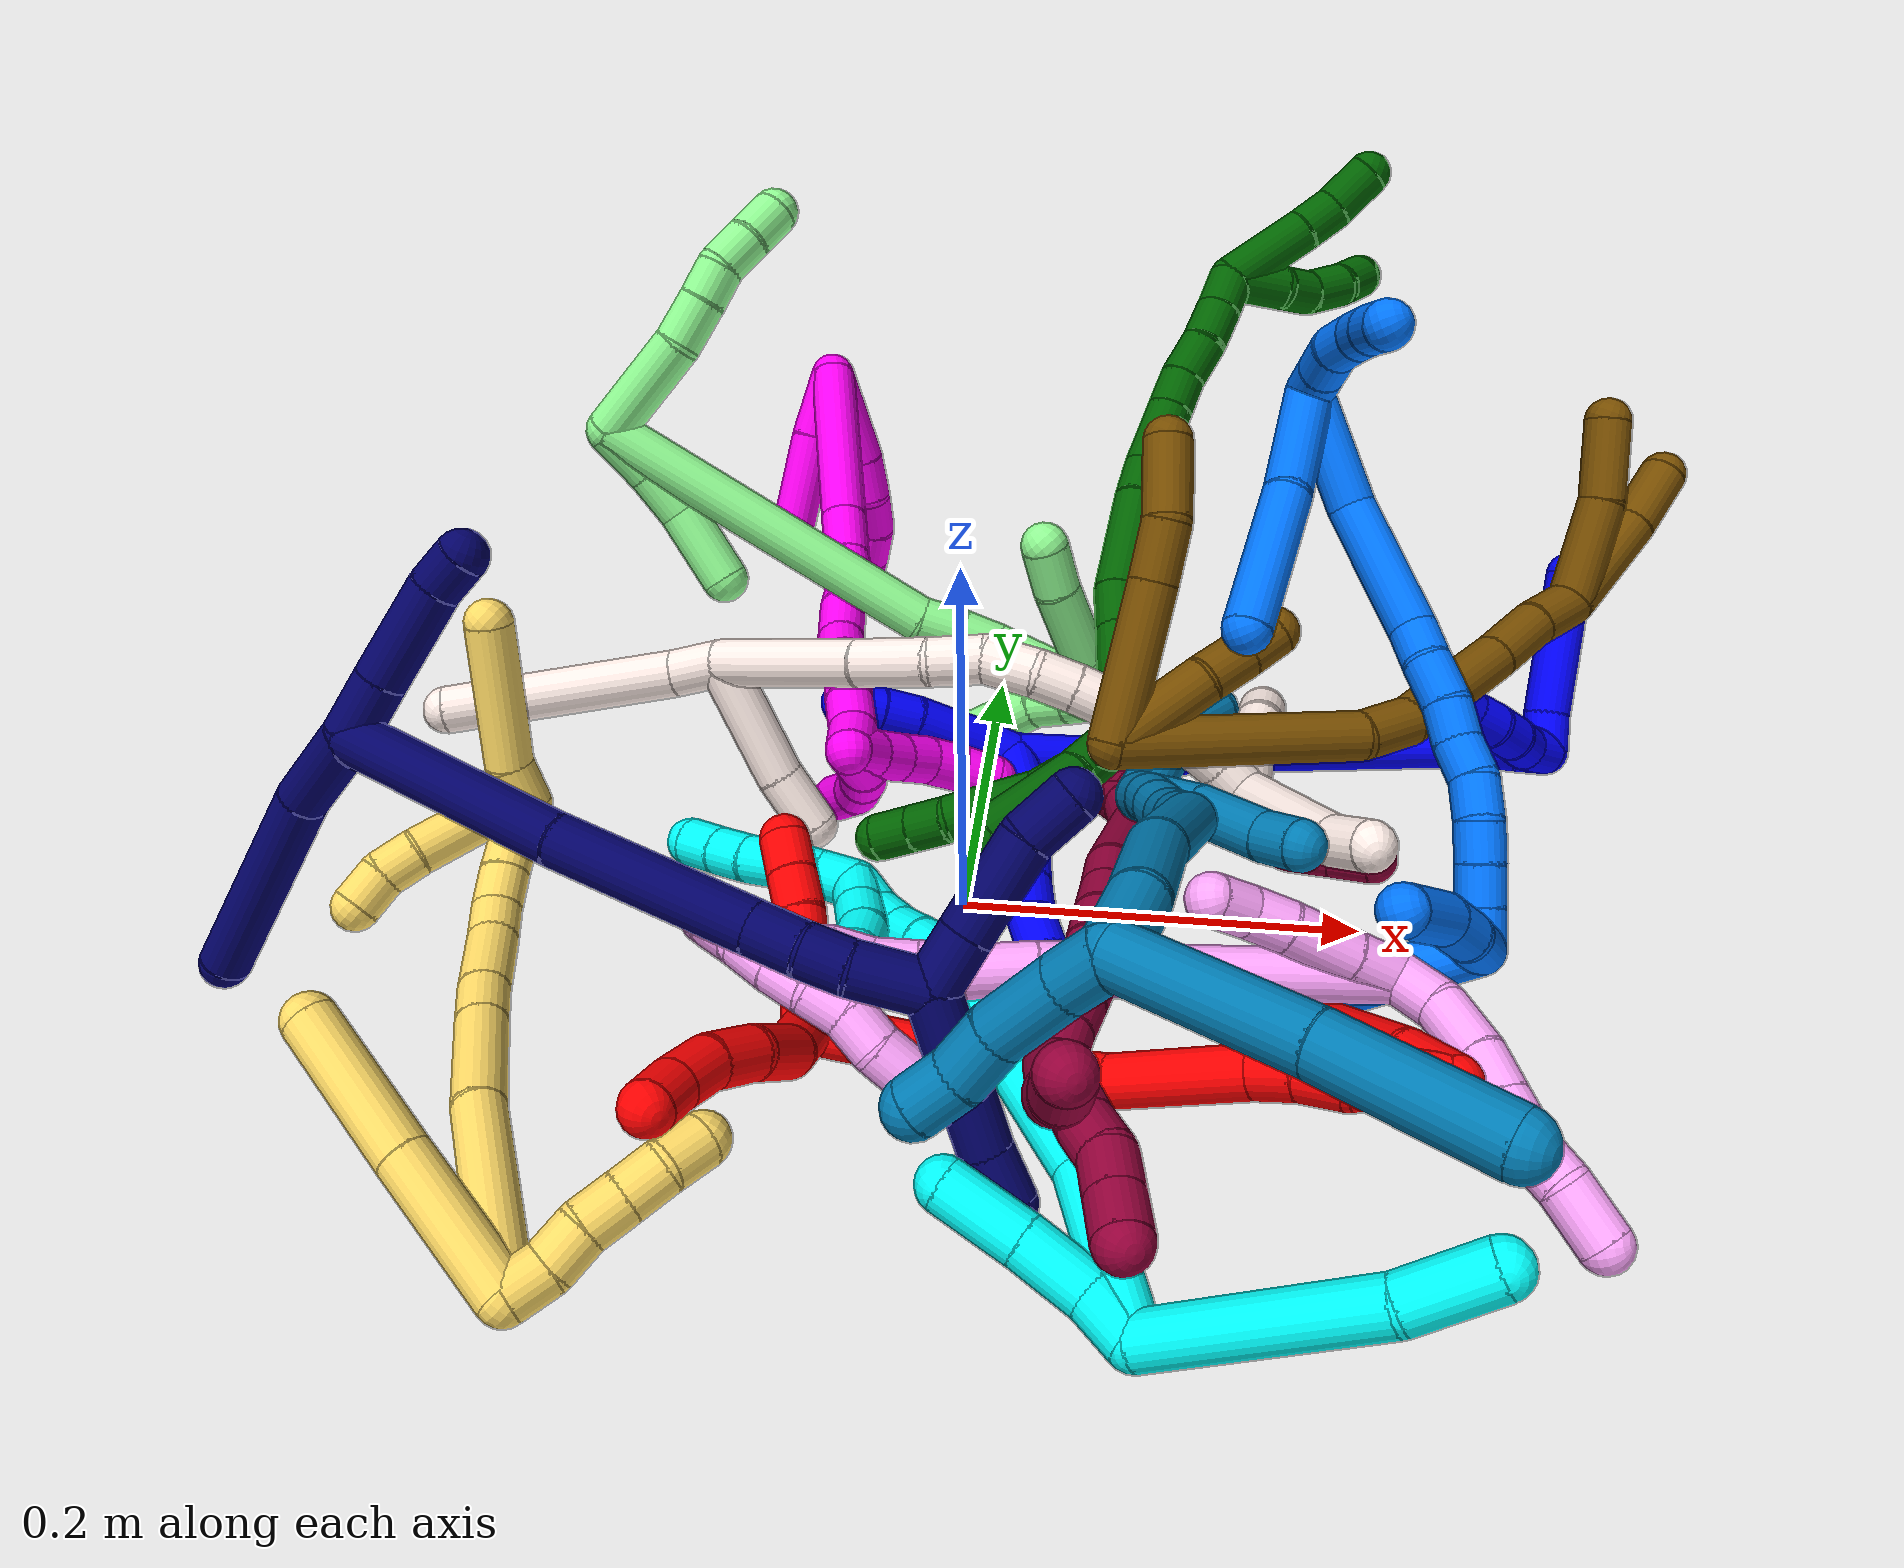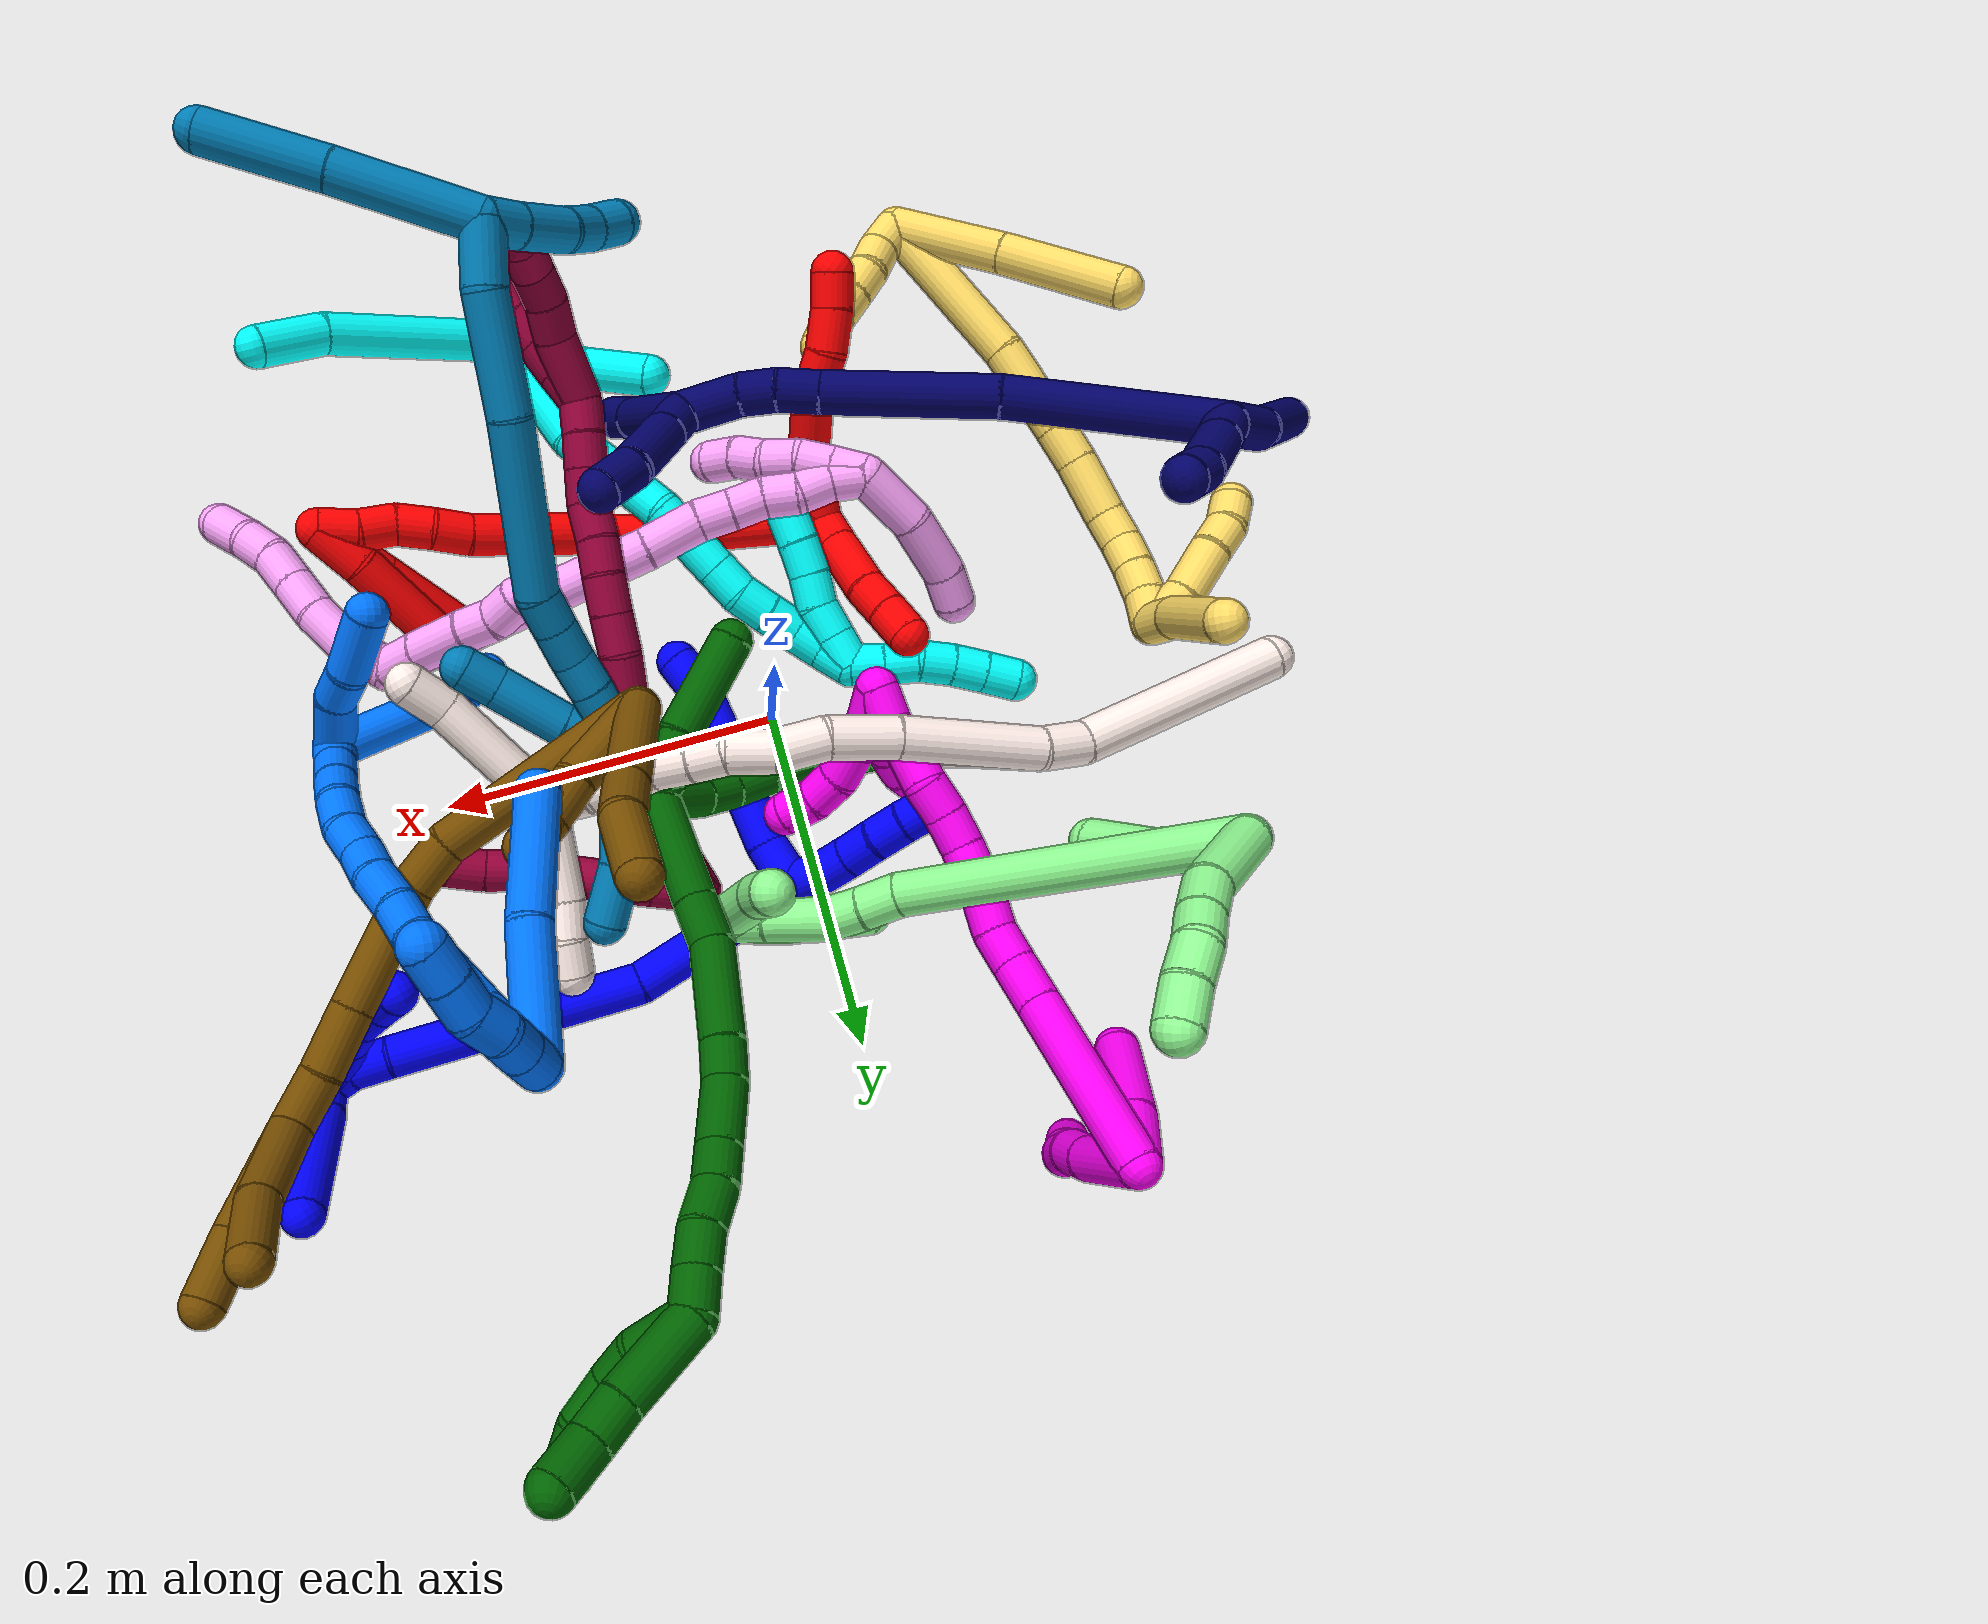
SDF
<sdf version="1.7">
 <world name="default">
  <plugin name="TubeGeneratorPlugin" filename="libtube_generator_plugin.so"/>
  <model name="photoneo_s_sensor">
   <static>1</static>
   <pose>0 0 2 1.57079 1.57079 3.14159</pose>
   <link name="link">
    <inertial><mass>0.1</mass></inertial>
    <sensor name="sensor" type="depth">
     <update_rate>30</update_rate>
     <camera>
      <horizontal_fov>1.22</horizontal_fov>
      <image><width>1920</width><height>1200</height><format>B8G8R8</format></image>
      <clip><near>0.1</near><far>4</far></clip>
      <depth_camera><output>points</output></depth_camera>
     </camera>
     <plugin name="camera_plugin" filename="libgazebo_ros_depth_camera.so">
      <baseline>0.2</baseline>
      <alwaysOn>1</alwaysOn>
      <updateRate>0.0</updateRate>
      <cameraName>camera_ir</cameraName>
      <imageTopicName>/camera/color/image_raw</imageTopicName>
      <cameraInfoTopicName>/camera/color/camera_info</cameraInfoTopicName>
      <depthImageTopicName>/camera/depth/image_raw</depthImageTopicName>
      <depthImageCameraInfoTopicName>/camera/depth/camera_info</depthImageCameraInfoTopicName>
      <pointCloudTopicName>/camera/depth/points</pointCloudTopicName>
      <frameName>fr_optical</frameName>
      <pointCloudCutoff>0.1</pointCloudCutoff>
      <pointCloudCutoffMax>2.0</pointCloudCutoffMax>
      <distortionK1>0</distortionK1>
      <distortionK2>0</distortionK2>
      <distortionK3>0</distortionK3>
      <distortionT1>0</distortionT1>
      <distortionT2>0</distortionT2>
      <CxPrime>0</CxPrime>
      <Cx>0</Cx>
      <Cy>0</Cy>
      <focalLength>0</focalLength>
      <hackBaseline>0</hackBaseline>
     </plugin>
    </sensor>
   </link>
  </model>
  <gravity>0 0 -9.8</gravity>
  <magnetic_field>6e-06 2.3e-05 -4.2e-05</magnetic_field>
  <atmosphere type="adiabatic"/>
  <physics name="default_physics" default="0" type="ode">
   <max_step_size>0.003</max_step_size>
   <real_time_factor>1</real_time_factor>
   <real_time_update_rate>1000</real_time_update_rate>
   <max_contacts>10000</max_contacts>
   <ode>
    <solver>
     <type>quick</type>
     <iters>100</iters>
     <sor>1.3</sor>
     <use_dynamic_moi_rescaling>0</use_dynamic_moi_rescaling>
    </solver>
    <constraints>
     <contact_max_correcting_vel>0</contact_max_correcting_vel>
     <contact_surface_layer>0.001</contact_surface_layer>
     <cfm>0</cfm>
     <erp>0.2</erp>
    </constraints>
   </ode>
  </physics>
  <scene><ambient>0.4 0.4 0.4 1</ambient><background>0.7 0.7 0.7 1</background><shadows>0</shadows></scene>
  <audio><device>default</device></audio>
  <spherical_coordinates>
   <surface_model>EARTH_WGS84</surface_model>
   <latitude_deg>0</latitude_deg>
   <longitude_deg>0</longitude_deg>
   <elevation>0</elevation>
   <heading_deg>0</heading_deg>
  </spherical_coordinates>
  <model name="bin">
   <static>1</static>
   <link name="bottom">
    <collision name="collision-bottom">
     <pose>0 0 -0.01 0 -0 0</pose>
     <geometry><box><size>0.8 0.6 0.02</size></box></geometry>
     <surface>
      <friction><ode><mu>100</mu><mu2>100</mu2></ode></friction>
      <contact><collide_bitmask>65535</collide_bitmask></contact>
     </surface>
    </collision>
   </link>
   <link name="west_wall">
    <collision name="collision-west_wall">
     <pose>-0.41 0 0.1 0 -0 0</pose>
     <geometry><box><size>0.02 0.6 0.2</size></box></geometry>
     <surface>
      <friction><ode><mu>100</mu><mu2>100</mu2></ode></friction>
      <contact><collide_bitmask>65535</collide_bitmask></contact>
     </surface>
    </collision>
   </link>
   <link name="east_wall">
    <collision name="collision-east_wall">
     <pose>0.41 0 0.1 0 -0 0</pose>
     <geometry><box><size>0.02 0.6 0.2</size></box></geometry>
     <surface>
      <friction><ode><mu>100</mu><mu2>100</mu2></ode></friction>
      <contact><collide_bitmask>65535</collide_bitmask></contact>
     </surface>
    </collision>
   </link>
   <link name="south_wall">
    <collision name="collision-south_wall">
     <pose>0 -0.31 0.1 0 -0 0</pose>
     <geometry><box><size>0.8 0.02 0.2</size></box></geometry>
     <surface>
      <friction><ode><mu>100</mu><mu2>100</mu2></ode></friction>
      <contact><collide_bitmask>65535</collide_bitmask></contact>
     </surface>
    </collision>
   </link>
   <link name="north_wall">
    <collision name="collision-north_wall">
     <pose>0 0.31 0.1 0 -0 0</pose>
     <geometry><box><size>0.8 0.02 0.2</size></box></geometry>
     <surface>
      <friction><ode><mu>100</mu><mu2>100</mu2></ode></friction>
      <contact><collide_bitmask>65535</collide_bitmask></contact>
     </surface>
    </collision>
   </link>
  </model>
  <model name="1">
   <static>0</static>
   <link name="1">
    <collision name="collision-cylinder-e_1_2_8">
     <pose>0.011209 -0.007037 -0.0007 1.66989 1.00796 1.09407</pose>
     <geometry><cylinder><radius>0.0125</radius><length>0.026506</length></cylinder></geometry>
     <surface>
      <friction><ode><mu>1.16</mu><mu2>1.16</mu2><slip1>0</slip1><slip2>0</slip2></ode></friction>
      <contact><ode><kp>1e+06</kp><kd>1</kd><max_vel>0</max_vel><min_depth>0.001</min_depth></ode></contact>
     </surface>
    </collision>
    <visual name="visual-cylinder-e_1_2_8">
     <pose>0.011209 -0.007037 -0.0007 1.66989 1.00796 1.09407</pose>
     <geometry><cylinder><radius>0.0125</radius><length>0.026506</length></cylinder></geometry>
     <material><ambient>0 0 1 1</ambient></material>
    </visual>
    <collision name="collision-cylinder-e_2_8_9">
     <pose>0.049469 -0.038651 -0.007769 1.82439 0.817079 1.02005</pose>
     <geometry><cylinder><radius>0.0125</radius><length>0.0742</length></cylinder></geometry>
     <surface>
      <friction><ode><mu>1.16</mu><mu2>1.16</mu2><slip1>0</slip1><slip2>0</slip2></ode></friction>
      <contact><ode><kp>1e+06</kp><kd>1</kd><max_vel>0</max_vel><min_depth>0.001</min_depth></ode></contact>
     </surface>
    </collision>
    <visual name="visual-cylinder-e_2_8_9">
     <pose>0.049469 -0.038651 -0.007769 1.82439 0.817079 1.02005</pose>
     <geometry><cylinder><radius>0.0125</radius><length>0.0742</length></cylinder></geometry>
     <material><ambient>0 0 1 1</ambient></material>
    </visual>
    <collision name="collision-cylinder-e_3_9_10">
     <pose>0.085483 -0.072151 -0.015664 1.74013 0.780411 0.907331</pose>
     <geometry><cylinder><radius>0.0125</radius><length>0.025477</length></cylinder></geometry>
     <surface>
      <friction><ode><mu>1.16</mu><mu2>1.16</mu2><slip1>0</slip1><slip2>0</slip2></ode></friction>
      <contact><ode><kp>1e+06</kp><kd>1</kd><max_vel>0</max_vel><min_depth>0.001</min_depth></ode></contact>
     </surface>
    </collision>
    <visual name="visual-cylinder-e_3_9_10">
     <pose>0.085483 -0.072151 -0.015664 1.74013 0.780411 0.907331</pose>
     <geometry><cylinder><radius>0.0125</radius><length>0.025477</length></cylinder></geometry>
     <material><ambient>0 0 1 1</ambient></material>
    </visual>
    <collision name="collision-cylinder-e_4_10_6">
     <pose>0.104608 -0.087276 -0.016946 1.53157 1.02258 0.989439</pose>
     <geometry><cylinder><radius>0.0125</radius><length>0.023817</length></cylinder></geometry>
     <surface>
      <friction><ode><mu>1.16</mu><mu2>1.16</mu2><slip1>0</slip1><slip2>0</slip2></ode></friction>
      <contact><ode><kp>1e+06</kp><kd>1</kd><max_vel>0</max_vel><min_depth>0.001</min_depth></ode></contact>
     </surface>
    </collision>
    <visual name="visual-cylinder-e_4_10_6">
     <pose>0.104608 -0.087276 -0.016946 1.53157 1.02258 0.989439</pose>
     <geometry><cylinder><radius>0.0125</radius><length>0.023817</length></cylinder></geometry>
     <material><ambient>0 0 1 1</ambient></material>
    </visual>
    <collision name="collision-cylinder-e_1_2_11">
     <pose>-0.006483 -0.003358 -0.006833 2.6848 -0.705341 -2.01498</pose>
     <geometry><cylinder><radius>0.0125</radius><length>0.02</length></cylinder></geometry>
     <surface>
      <friction><ode><mu>1.16</mu><mu2>1.16</mu2><slip1>0</slip1><slip2>0</slip2></ode></friction>
      <contact><ode><kp>1e+06</kp><kd>1</kd><max_vel>0</max_vel><min_depth>0.001</min_depth></ode></contact>
     </surface>
    </collision>
    <visual name="visual-cylinder-e_1_2_11">
     <pose>-0.006483 -0.003358 -0.006833 2.6848 -0.705341 -2.01498</pose>
     <geometry><cylinder><radius>0.0125</radius><length>0.02</length></cylinder></geometry>
     <material><ambient>0 0 1 1</ambient></material>
    </visual>
    <collision name="collision-cylinder-e_2_11_12">
     <pose>-0.018118 -0.012017 -0.020401 2.47478 -0.541212 -1.35069</pose>
     <geometry><cylinder><radius>0.0125</radius><length>0.02</length></cylinder></geometry>
     <surface>
      <friction><ode><mu>1.16</mu><mu2>1.16</mu2><slip1>0</slip1><slip2>0</slip2></ode></friction>
      <contact><ode><kp>1e+06</kp><kd>1</kd><max_vel>0</max_vel><min_depth>0.001</min_depth></ode></contact>
     </surface>
    </collision>
    <visual name="visual-cylinder-e_2_11_12">
     <pose>-0.018118 -0.012017 -0.020401 2.47478 -0.541212 -1.35069</pose>
     <geometry><cylinder><radius>0.0125</radius><length>0.02</length></cylinder></geometry>
     <material><ambient>0 0 1 1</ambient></material>
    </visual>
    <collision name="collision-cylinder-e_3_12_13">
     <pose>-0.028431 -0.022964 -0.033577 2.42189 -0.542416 -1.27292</pose>
     <geometry><cylinder><radius>0.0125</radius><length>0.02</length></cylinder></geometry>
     <surface>
      <friction><ode><mu>1.16</mu><mu2>1.16</mu2><slip1>0</slip1><slip2>0</slip2></ode></friction>
      <contact><ode><kp>1e+06</kp><kd>1</kd><max_vel>0</max_vel><min_depth>0.001</min_depth></ode></contact>
     </surface>
    </collision>
    <visual name="visual-cylinder-e_3_12_13">
     <pose>-0.028431 -0.022964 -0.033577 2.42189 -0.542416 -1.27292</pose>
     <geometry><cylinder><radius>0.0125</radius><length>0.02</length></cylinder></geometry>
     <material><ambient>0 0 1 1</ambient></material>
    </visual>
    <collision name="collision-cylinder-e_4_13_14">
     <pose>-0.038237 -0.033459 -0.047428 2.56214 -0.482942 -1.38092</pose>
     <geometry><cylinder><radius>0.0125</radius><length>0.02</length></cylinder></geometry>
     <surface>
      <friction><ode><mu>1.16</mu><mu2>1.16</mu2><slip1>0</slip1><slip2>0</slip2></ode></friction>
      <contact><ode><kp>1e+06</kp><kd>1</kd><max_vel>0</max_vel><min_depth>0.001</min_depth></ode></contact>
     </surface>
    </collision>
    <visual name="visual-cylinder-e_4_13_14">
     <pose>-0.038237 -0.033459 -0.047428 2.56214 -0.482942 -1.38092</pose>
     <geometry><cylinder><radius>0.0125</radius><length>0.02</length></cylinder></geometry>
     <material><ambient>0 0 1 1</ambient></material>
    </visual>
    <collision name="collision-cylinder-e_5_14_5">
     <pose>-0.047543 -0.042537 -0.06261 2.64327 -0.485005 -1.54258</pose>
     <geometry><cylinder><radius>0.0125</radius><length>0.02</length></cylinder></geometry>
     <surface>
      <friction><ode><mu>1.16</mu><mu2>1.16</mu2><slip1>0</slip1><slip2>0</slip2></ode></friction>
      <contact><ode><kp>1e+06</kp><kd>1</kd><max_vel>0</max_vel><min_depth>0.001</min_depth></ode></contact>
     </surface>
    </collision>
    <visual name="visual-cylinder-e_5_14_5">
     <pose>-0.047543 -0.042537 -0.06261 2.64327 -0.485005 -1.54258</pose>
     <geometry><cylinder><radius>0.0125</radius><length>0.02</length></cylinder></geometry>
     <material><ambient>0 0 1 1</ambient></material>
    </visual>
    <collision name="collision-cylinder-e_1_2_15">
     <pose>0.010293 0.013205 0.026542 -0.461659 0.334185 -0.079237</pose>
     <geometry><cylinder><radius>0.0125</radius><length>0.062763</length></cylinder></geometry>
     <surface>
      <friction><ode><mu>1.16</mu><mu2>1.16</mu2><slip1>0</slip1><slip2>0</slip2></ode></friction>
      <contact><ode><kp>1e+06</kp><kd>1</kd><max_vel>0</max_vel><min_depth>0.001</min_depth></ode></contact>
     </surface>
    </collision>
    <visual name="visual-cylinder-e_1_2_15">
     <pose>0.010293 0.013205 0.026542 -0.461659 0.334185 -0.079237</pose>
     <geometry><cylinder><radius>0.0125</radius><length>0.062763</length></cylinder></geometry>
     <material><ambient>0 0 1 1</ambient></material>
    </visual>
    <collision name="collision-cylinder-e_2_15_16">
     <pose>0.025546 0.032195 0.07373 -0.273172 0.227335 -0.031378</pose>
     <geometry><cylinder><radius>0.0125</radius><length>0.044015</length></cylinder></geometry>
     <surface>
      <friction><ode><mu>1.16</mu><mu2>1.16</mu2><slip1>0</slip1><slip2>0</slip2></ode></friction>
      <contact><ode><kp>1e+06</kp><kd>1</kd><max_vel>0</max_vel><min_depth>0.001</min_depth></ode></contact>
     </surface>
    </collision>
    <visual name="visual-cylinder-e_2_15_16">
     <pose>0.025546 0.032195 0.07373 -0.273172 0.227335 -0.031378</pose>
     <geometry><cylinder><radius>0.0125</radius><length>0.044015</length></cylinder></geometry>
     <material><ambient>0 0 1 1</ambient></material>
    </visual>
    <collision name="collision-cylinder-e_3_16_17">
     <pose>0.057461 0.037965 0.164245 0.000208 0.368202 3.9e-05</pose>
     <geometry><cylinder><radius>0.0125</radius><length>0.149777</length></cylinder></geometry>
     <surface>
      <friction><ode><mu>1.16</mu><mu2>1.16</mu2><slip1>0</slip1><slip2>0</slip2></ode></friction>
      <contact><ode><kp>1e+06</kp><kd>1</kd><max_vel>0</max_vel><min_depth>0.001</min_depth></ode></contact>
     </surface>
    </collision>
    <visual name="visual-cylinder-e_3_16_17">
     <pose>0.057461 0.037965 0.164245 0.000208 0.368202 3.9e-05</pose>
     <geometry><cylinder><radius>0.0125</radius><length>0.149777</length></cylinder></geometry>
     <material><ambient>0 0 1 1</ambient></material>
    </visual>
    <collision name="collision-cylinder-e_4_17_18">
     <pose>0.08955 0.039336 0.244136 -0.137363 0.469522 -0.032902</pose>
     <geometry><cylinder><radius>0.0125</radius><length>0.022692</length></cylinder></geometry>
     <surface>
      <friction><ode><mu>1.16</mu><mu2>1.16</mu2><slip1>0</slip1><slip2>0</slip2></ode></friction>
      <contact><ode><kp>1e+06</kp><kd>1</kd><max_vel>0</max_vel><min_depth>0.001</min_depth></ode></contact>
     </surface>
    </collision>
    <visual name="visual-cylinder-e_4_17_18">
     <pose>0.08955 0.039336 0.244136 -0.137363 0.469522 -0.032902</pose>
     <geometry><cylinder><radius>0.0125</radius><length>0.022692</length></cylinder></geometry>
     <material><ambient>0 0 1 1</ambient></material>
    </visual>
    <collision name="collision-cylinder-e_5_18_1">
     <pose>0.098453 0.045215 0.262719 -0.483457 0.371755 -0.09266</pose>
     <geometry><cylinder><radius>0.0125</radius><length>0.020754</length></cylinder></geometry>
     <surface>
      <friction><ode><mu>1.16</mu><mu2>1.16</mu2><slip1>0</slip1><slip2>0</slip2></ode></friction>
      <contact><ode><kp>1e+06</kp><kd>1</kd><max_vel>0</max_vel><min_depth>0.001</min_depth></ode></contact>
     </surface>
    </collision>
    <visual name="visual-cylinder-e_5_18_1">
     <pose>0.098453 0.045215 0.262719 -0.483457 0.371755 -0.09266</pose>
     <geometry><cylinder><radius>0.0125</radius><length>0.020754</length></cylinder></geometry>
     <material><ambient>0 0 1 1</ambient></material>
    </visual>
    <collision name="collision-cylinder-e_1_1_19">
     <pose>0.099425 0.042157 0.265353 2.23614 -0.283591 -0.570921</pose>
     <geometry><cylinder><radius>0.0125</radius><length>0.02</length></cylinder></geometry>
     <surface>
      <friction><ode><mu>1.16</mu><mu2>1.16</mu2><slip1>0</slip1><slip2>0</slip2></ode></friction>
      <contact><ode><kp>1e+06</kp><kd>1</kd><max_vel>0</max_vel><min_depth>0.001</min_depth></ode></contact>
     </surface>
    </collision>
    <visual name="visual-cylinder-e_1_1_19">
     <pose>0.099425 0.042157 0.265353 2.23614 -0.283591 -0.570921</pose>
     <geometry><cylinder><radius>0.0125</radius><length>0.02</length></cylinder></geometry>
     <material><ambient>0 0 1 1</ambient></material>
    </visual>
    <collision name="collision-cylinder-e_2_19_20">
     <pose>0.093906 0.025638 0.255932 1.94247 -0.275574 -0.400324</pose>
     <geometry><cylinder><radius>0.0125</radius><length>0.02</length></cylinder></geometry>
     <surface>
      <friction><ode><mu>1.16</mu><mu2>1.16</mu2><slip1>0</slip1><slip2>0</slip2></ode></friction>
      <contact><ode><kp>1e+06</kp><kd>1</kd><max_vel>0</max_vel><min_depth>0.001</min_depth></ode></contact>
     </surface>
    </collision>
    <visual name="visual-cylinder-e_2_19_20">
     <pose>0.093906 0.025638 0.255932 1.94247 -0.275574 -0.400324</pose>
     <geometry><cylinder><radius>0.0125</radius><length>0.02</length></cylinder></geometry>
     <material><ambient>0 0 1 1</ambient></material>
    </visual>
    <collision name="collision-cylinder-e_3_20_21">
     <pose>0.087074 0.008814 0.247817 2.10227 -0.423645 -0.719089</pose>
     <geometry><cylinder><radius>0.0125</radius><length>0.02</length></cylinder></geometry>
     <surface>
      <friction><ode><mu>1.16</mu><mu2>1.16</mu2><slip1>0</slip1><slip2>0</slip2></ode></friction>
      <contact><ode><kp>1e+06</kp><kd>1</kd><max_vel>0</max_vel><min_depth>0.001</min_depth></ode></contact>
     </surface>
    </collision>
    <visual name="visual-cylinder-e_3_20_21">
     <pose>0.087074 0.008814 0.247817 2.10227 -0.423645 -0.719089</pose>
     <geometry><cylinder><radius>0.0125</radius><length>0.02</length></cylinder></geometry>
     <material><ambient>0 0 1 1</ambient></material>
    </visual>
    <collision name="collision-cylinder-e_4_21_22">
     <pose>0.077751 -0.005438 0.237543 2.29491 -0.548217 -1.11583</pose>
     <geometry><cylinder><radius>0.0125</radius><length>0.02</length></cylinder></geometry>
     <surface>
      <friction><ode><mu>1.16</mu><mu2>1.16</mu2><slip1>0</slip1><slip2>0</slip2></ode></friction>
      <contact><ode><kp>1e+06</kp><kd>1</kd><max_vel>0</max_vel><min_depth>0.001</min_depth></ode></contact>
     </surface>
    </collision>
    <visual name="visual-cylinder-e_4_21_22">
     <pose>0.077751 -0.005438 0.237543 2.29491 -0.548217 -1.11583</pose>
     <geometry><cylinder><radius>0.0125</radius><length>0.02</length></cylinder></geometry>
     <material><ambient>0 0 1 1</ambient></material>
    </visual>
    <collision name="collision-cylinder-e_5_22_4">
     <pose>0.066135 -0.018578 0.228221 2.06873 -0.69517 -1.09448</pose>
     <geometry><cylinder><radius>0.0125</radius><length>0.02</length></cylinder></geometry>
     <surface>
      <friction><ode><mu>1.16</mu><mu2>1.16</mu2><slip1>0</slip1><slip2>0</slip2></ode></friction>
      <contact><ode><kp>1e+06</kp><kd>1</kd><max_vel>0</max_vel><min_depth>0.001</min_depth></ode></contact>
     </surface>
    </collision>
    <visual name="visual-cylinder-e_5_22_4">
     <pose>0.066135 -0.018578 0.228221 2.06873 -0.69517 -1.09448</pose>
     <geometry><cylinder><radius>0.0125</radius><length>0.02</length></cylinder></geometry>
     <material><ambient>0 0 1 1</ambient></material>
    </visual>
    <collision name="collision-cylinder-e_1_1_23">
     <pose>0.092795 0.050033 0.276303 -0.06431 -1.08037 0.038574</pose>
     <geometry><cylinder><radius>0.0125</radius><length>0.021374</length></cylinder></geometry>
     <surface>
      <friction><ode><mu>1.16</mu><mu2>1.16</mu2><slip1>0</slip1><slip2>0</slip2></ode></friction>
      <contact><ode><kp>1e+06</kp><kd>1</kd><max_vel>0</max_vel><min_depth>0.001</min_depth></ode></contact>
     </surface>
    </collision>
    <visual name="visual-cylinder-e_1_1_23">
     <pose>0.092795 0.050033 0.276303 -0.06431 -1.08037 0.038574</pose>
     <geometry><cylinder><radius>0.0125</radius><length>0.021374</length></cylinder></geometry>
     <material><ambient>0 0 1 1</ambient></material>
    </visual>
    <collision name="collision-cylinder-e_2_23_3">
     <pose>0.050436 0.045615 0.302267 0.222672 -0.993019 -0.120992</pose>
     <geometry><cylinder><radius>0.0125</radius><length>0.078626</length></cylinder></geometry>
     <surface>
      <friction><ode><mu>1.16</mu><mu2>1.16</mu2><slip1>0</slip1><slip2>0</slip2></ode></friction>
      <contact><ode><kp>1e+06</kp><kd>1</kd><max_vel>0</max_vel><min_depth>0.001</min_depth></ode></contact>
     </surface>
    </collision>
    <visual name="visual-cylinder-e_2_23_3">
     <pose>0.050436 0.045615 0.302267 0.222672 -0.993019 -0.120992</pose>
     <geometry><cylinder><radius>0.0125</radius><length>0.078626</length></cylinder></geometry>
     <material><ambient>0 0 1 1</ambient></material>
    </visual>
    <collision name="collision-sphere-3">
     <pose>0.017505 0.040873 0.323209 0 -0 0</pose>
     <geometry><sphere><radius>0.0125</radius></sphere></geometry>
     <surface>
      <friction><ode><mu>1.16</mu><mu2>1.16</mu2><slip1>0</slip1><slip2>0</slip2></ode></friction>
      <contact><ode><kp>1e+06</kp><kd>1</kd><max_vel>0</max_vel><min_depth>0.001</min_depth></ode></contact>
     </surface>
    </collision>
    <visual name="visual-sphere-3">
     <pose>0.017505 0.040873 0.323209 0 -0 0</pose>
     <geometry><sphere><radius>0.0125</radius></sphere></geometry>
     <material><ambient>0 0 1 1</ambient></material>
    </visual>
    <collision name="collision-sphere-23">
     <pose>0.083368 0.050357 0.281326 0 -0 0</pose>
     <geometry><sphere><radius>0.0125</radius></sphere></geometry>
     <surface>
      <friction><ode><mu>1.16</mu><mu2>1.16</mu2><slip1>0</slip1><slip2>0</slip2></ode></friction>
      <contact><ode><kp>1e+06</kp><kd>1</kd><max_vel>0</max_vel><min_depth>0.001</min_depth></ode></contact>
     </surface>
    </collision>
    <visual name="visual-sphere-23">
     <pose>0.083368 0.050357 0.281326 0 -0 0</pose>
     <geometry><sphere><radius>0.0125</radius></sphere></geometry>
     <material><ambient>0 0 1 1</ambient></material>
    </visual>
    <collision name="collision-sphere-4">
     <pose>0.059729 -0.025325 0.224554 0 -0 0</pose>
     <geometry><sphere><radius>0.0125</radius></sphere></geometry>
     <surface>
      <friction><ode><mu>1.16</mu><mu2>1.16</mu2><slip1>0</slip1><slip2>0</slip2></ode></friction>
      <contact><ode><kp>1e+06</kp><kd>1</kd><max_vel>0</max_vel><min_depth>0.001</min_depth></ode></contact>
     </surface>
    </collision>
    <visual name="visual-sphere-4">
     <pose>0.059729 -0.025325 0.224554 0 -0 0</pose>
     <geometry><sphere><radius>0.0125</radius></sphere></geometry>
     <material><ambient>0 0 1 1</ambient></material>
    </visual>
    <collision name="collision-sphere-22">
     <pose>0.07254 -0.011831 0.231889 0 -0 0</pose>
     <geometry><sphere><radius>0.0125</radius></sphere></geometry>
     <surface>
      <friction><ode><mu>1.16</mu><mu2>1.16</mu2><slip1>0</slip1><slip2>0</slip2></ode></friction>
      <contact><ode><kp>1e+06</kp><kd>1</kd><max_vel>0</max_vel><min_depth>0.001</min_depth></ode></contact>
     </surface>
    </collision>
    <visual name="visual-sphere-22">
     <pose>0.07254 -0.011831 0.231889 0 -0 0</pose>
     <geometry><sphere><radius>0.0125</radius></sphere></geometry>
     <material><ambient>0 0 1 1</ambient></material>
    </visual>
    <collision name="collision-sphere-21">
     <pose>0.082963 0.000956 0.243197 0 -0 0</pose>
     <geometry><sphere><radius>0.0125</radius></sphere></geometry>
     <surface>
      <friction><ode><mu>1.16</mu><mu2>1.16</mu2><slip1>0</slip1><slip2>0</slip2></ode></friction>
      <contact><ode><kp>1e+06</kp><kd>1</kd><max_vel>0</max_vel><min_depth>0.001</min_depth></ode></contact>
     </surface>
    </collision>
    <visual name="visual-sphere-21">
     <pose>0.082963 0.000956 0.243197 0 -0 0</pose>
     <geometry><sphere><radius>0.0125</radius></sphere></geometry>
     <material><ambient>0 0 1 1</ambient></material>
    </visual>
    <collision name="collision-sphere-20">
     <pose>0.091185 0.016673 0.252437 0 -0 0</pose>
     <geometry><sphere><radius>0.0125</radius></sphere></geometry>
     <surface>
      <friction><ode><mu>1.16</mu><mu2>1.16</mu2><slip1>0</slip1><slip2>0</slip2></ode></friction>
      <contact><ode><kp>1e+06</kp><kd>1</kd><max_vel>0</max_vel><min_depth>0.001</min_depth></ode></contact>
     </surface>
    </collision>
    <visual name="visual-sphere-20">
     <pose>0.091185 0.016673 0.252437 0 -0 0</pose>
     <geometry><sphere><radius>0.0125</radius></sphere></geometry>
     <material><ambient>0 0 1 1</ambient></material>
    </visual>
    <collision name="collision-sphere-11">
     <pose>-0.012966 -0.006717 -0.013667 0 -0 0</pose>
     <geometry><sphere><radius>0.0125</radius></sphere></geometry>
     <surface>
      <friction><ode><mu>1.16</mu><mu2>1.16</mu2><slip1>0</slip1><slip2>0</slip2></ode></friction>
      <contact><ode><kp>1e+06</kp><kd>1</kd><max_vel>0</max_vel><min_depth>0.001</min_depth></ode></contact>
     </surface>
    </collision>
    <visual name="visual-sphere-11">
     <pose>-0.012966 -0.006717 -0.013667 0 -0 0</pose>
     <geometry><sphere><radius>0.0125</radius></sphere></geometry>
     <material><ambient>0 0 1 1</ambient></material>
    </visual>
    <collision name="collision-sphere-6">
     <pose>0.114772 -0.093477 -0.016703 0 -0 0</pose>
     <geometry><sphere><radius>0.0125</radius></sphere></geometry>
     <surface>
      <friction><ode><mu>1.16</mu><mu2>1.16</mu2><slip1>0</slip1><slip2>0</slip2></ode></friction>
      <contact><ode><kp>1e+06</kp><kd>1</kd><max_vel>0</max_vel><min_depth>0.001</min_depth></ode></contact>
     </surface>
    </collision>
    <visual name="visual-sphere-6">
     <pose>0.114772 -0.093477 -0.016703 0 -0 0</pose>
     <geometry><sphere><radius>0.0125</radius></sphere></geometry>
     <material><ambient>0 0 1 1</ambient></material>
    </visual>
    <collision name="collision-sphere-10">
     <pose>0.094445 -0.081074 -0.01719 0 -0 0</pose>
     <geometry><sphere><radius>0.0125</radius></sphere></geometry>
     <surface>
      <friction><ode><mu>1.16</mu><mu2>1.16</mu2><slip1>0</slip1><slip2>0</slip2></ode></friction>
      <contact><ode><kp>1e+06</kp><kd>1</kd><max_vel>0</max_vel><min_depth>0.001</min_depth></ode></contact>
     </surface>
    </collision>
    <visual name="visual-sphere-10">
     <pose>0.094445 -0.081074 -0.01719 0 -0 0</pose>
     <geometry><sphere><radius>0.0125</radius></sphere></geometry>
     <material><ambient>0 0 1 1</ambient></material>
    </visual>
    <collision name="collision-sphere-9">
     <pose>0.07652 -0.063229 -0.014139 0 -0 0</pose>
     <geometry><sphere><radius>0.0125</radius></sphere></geometry>
     <surface>
      <friction><ode><mu>1.16</mu><mu2>1.16</mu2><slip1>0</slip1><slip2>0</slip2></ode></friction>
      <contact><ode><kp>1e+06</kp><kd>1</kd><max_vel>0</max_vel><min_depth>0.001</min_depth></ode></contact>
     </surface>
    </collision>
    <visual name="visual-sphere-9">
     <pose>0.07652 -0.063229 -0.014139 0 -0 0</pose>
     <geometry><sphere><radius>0.0125</radius></sphere></geometry>
     <material><ambient>0 0 1 1</ambient></material>
    </visual>
    <collision name="collision-sphere-2">
     <geometry><sphere><radius>0.0125</radius></sphere></geometry>
     <surface>
      <friction><ode><mu>1.16</mu><mu2>1.16</mu2><slip1>0</slip1><slip2>0</slip2></ode></friction>
      <contact><ode><kp>1e+06</kp><kd>1</kd><max_vel>0</max_vel><min_depth>0.001</min_depth></ode></contact>
     </surface>
    </collision>
    <visual name="visual-sphere-2">
     <geometry><sphere><radius>0.0125</radius></sphere></geometry>
     <material><ambient>0 0 1 1</ambient></material>
    </visual>
    <collision name="collision-sphere-19">
     <pose>0.096627 0.034604 0.259426 0 -0 0</pose>
     <geometry><sphere><radius>0.0125</radius></sphere></geometry>
     <surface>
      <friction><ode><mu>1.16</mu><mu2>1.16</mu2><slip1>0</slip1><slip2>0</slip2></ode></friction>
      <contact><ode><kp>1e+06</kp><kd>1</kd><max_vel>0</max_vel><min_depth>0.001</min_depth></ode></contact>
     </surface>
    </collision>
    <visual name="visual-sphere-19">
     <pose>0.096627 0.034604 0.259426 0 -0 0</pose>
     <geometry><sphere><radius>0.0125</radius></sphere></geometry>
     <material><ambient>0 0 1 1</ambient></material>
    </visual>
    <collision name="collision-sphere-8">
     <pose>0.022417 -0.014074 -0.001399 0 -0 0</pose>
     <geometry><sphere><radius>0.0125</radius></sphere></geometry>
     <surface>
      <friction><ode><mu>1.16</mu><mu2>1.16</mu2><slip1>0</slip1><slip2>0</slip2></ode></friction>
      <contact><ode><kp>1e+06</kp><kd>1</kd><max_vel>0</max_vel><min_depth>0.001</min_depth></ode></contact>
     </surface>
    </collision>
    <visual name="visual-sphere-8">
     <pose>0.022417 -0.014074 -0.001399 0 -0 0</pose>
     <geometry><sphere><radius>0.0125</radius></sphere></geometry>
     <material><ambient>0 0 1 1</ambient></material>
    </visual>
    <collision name="collision-sphere-12">
     <pose>-0.023269 -0.017318 -0.027136 0 -0 0</pose>
     <geometry><sphere><radius>0.0125</radius></sphere></geometry>
     <surface>
      <friction><ode><mu>1.16</mu><mu2>1.16</mu2><slip1>0</slip1><slip2>0</slip2></ode></friction>
      <contact><ode><kp>1e+06</kp><kd>1</kd><max_vel>0</max_vel><min_depth>0.001</min_depth></ode></contact>
     </surface>
    </collision>
    <visual name="visual-sphere-12">
     <pose>-0.023269 -0.017318 -0.027136 0 -0 0</pose>
     <geometry><sphere><radius>0.0125</radius></sphere></geometry>
     <material><ambient>0 0 1 1</ambient></material>
    </visual>
    <collision name="collision-sphere-13">
     <pose>-0.033593 -0.028609 -0.040018 0 -0 0</pose>
     <geometry><sphere><radius>0.0125</radius></sphere></geometry>
     <surface>
      <friction><ode><mu>1.16</mu><mu2>1.16</mu2><slip1>0</slip1><slip2>0</slip2></ode></friction>
      <contact><ode><kp>1e+06</kp><kd>1</kd><max_vel>0</max_vel><min_depth>0.001</min_depth></ode></contact>
     </surface>
    </collision>
    <visual name="visual-sphere-13">
     <pose>-0.033593 -0.028609 -0.040018 0 -0 0</pose>
     <geometry><sphere><radius>0.0125</radius></sphere></geometry>
     <material><ambient>0 0 1 1</ambient></material>
    </visual>
    <collision name="collision-sphere-14">
     <pose>-0.042881 -0.038308 -0.054839 0 -0 0</pose>
     <geometry><sphere><radius>0.0125</radius></sphere></geometry>
     <surface>
      <friction><ode><mu>1.16</mu><mu2>1.16</mu2><slip1>0</slip1><slip2>0</slip2></ode></friction>
      <contact><ode><kp>1e+06</kp><kd>1</kd><max_vel>0</max_vel><min_depth>0.001</min_depth></ode></contact>
     </surface>
    </collision>
    <visual name="visual-sphere-14">
     <pose>-0.042881 -0.038308 -0.054839 0 -0 0</pose>
     <geometry><sphere><radius>0.0125</radius></sphere></geometry>
     <material><ambient>0 0 1 1</ambient></material>
    </visual>
    <collision name="collision-sphere-5">
     <pose>-0.052205 -0.046765 -0.070381 0 -0 0</pose>
     <geometry><sphere><radius>0.0125</radius></sphere></geometry>
     <surface>
      <friction><ode><mu>1.16</mu><mu2>1.16</mu2><slip1>0</slip1><slip2>0</slip2></ode></friction>
      <contact><ode><kp>1e+06</kp><kd>1</kd><max_vel>0</max_vel><min_depth>0.001</min_depth></ode></contact>
     </surface>
    </collision>
    <visual name="visual-sphere-5">
     <pose>-0.052205 -0.046765 -0.070381 0 -0 0</pose>
     <geometry><sphere><radius>0.0125</radius></sphere></geometry>
     <material><ambient>0 0 1 1</ambient></material>
    </visual>
    <collision name="collision-sphere-15">
     <pose>0.020586 0.02641 0.053084 0 -0 0</pose>
     <geometry><sphere><radius>0.0125</radius></sphere></geometry>
     <surface>
      <friction><ode><mu>1.16</mu><mu2>1.16</mu2><slip1>0</slip1><slip2>0</slip2></ode></friction>
      <contact><ode><kp>1e+06</kp><kd>1</kd><max_vel>0</max_vel><min_depth>0.001</min_depth></ode></contact>
     </surface>
    </collision>
    <visual name="visual-sphere-15">
     <pose>0.020586 0.02641 0.053084 0 -0 0</pose>
     <geometry><sphere><radius>0.0125</radius></sphere></geometry>
     <material><ambient>0 0 1 1</ambient></material>
    </visual>
    <collision name="collision-sphere-16">
     <pose>0.030506 0.037979 0.094376 0 -0 0</pose>
     <geometry><sphere><radius>0.0125</radius></sphere></geometry>
     <surface>
      <friction><ode><mu>1.16</mu><mu2>1.16</mu2><slip1>0</slip1><slip2>0</slip2></ode></friction>
      <contact><ode><kp>1e+06</kp><kd>1</kd><max_vel>0</max_vel><min_depth>0.001</min_depth></ode></contact>
     </surface>
    </collision>
    <visual name="visual-sphere-16">
     <pose>0.030506 0.037979 0.094376 0 -0 0</pose>
     <geometry><sphere><radius>0.0125</radius></sphere></geometry>
     <material><ambient>0 0 1 1</ambient></material>
    </visual>
    <collision name="collision-sphere-17">
     <pose>0.084417 0.03795 0.234114 0 -0 0</pose>
     <geometry><sphere><radius>0.0125</radius></sphere></geometry>
     <surface>
      <friction><ode><mu>1.16</mu><mu2>1.16</mu2><slip1>0</slip1><slip2>0</slip2></ode></friction>
      <contact><ode><kp>1e+06</kp><kd>1</kd><max_vel>0</max_vel><min_depth>0.001</min_depth></ode></contact>
     </surface>
    </collision>
    <visual name="visual-sphere-17">
     <pose>0.084417 0.03795 0.234114 0 -0 0</pose>
     <geometry><sphere><radius>0.0125</radius></sphere></geometry>
     <material><ambient>0 0 1 1</ambient></material>
    </visual>
    <collision name="collision-sphere-18">
     <pose>0.094684 0.040721 0.254159 0 -0 0</pose>
     <geometry><sphere><radius>0.0125</radius></sphere></geometry>
     <surface>
      <friction><ode><mu>1.16</mu><mu2>1.16</mu2><slip1>0</slip1><slip2>0</slip2></ode></friction>
      <contact><ode><kp>1e+06</kp><kd>1</kd><max_vel>0</max_vel><min_depth>0.001</min_depth></ode></contact>
     </surface>
    </collision>
    <visual name="visual-sphere-18">
     <pose>0.094684 0.040721 0.254159 0 -0 0</pose>
     <geometry><sphere><radius>0.0125</radius></sphere></geometry>
     <material><ambient>0 0 1 1</ambient></material>
    </visual>
    <collision name="collision-sphere-1">
     <pose>0.102223 0.04971 0.27128 0 -0 0</pose>
     <geometry><sphere><radius>0.0125</radius></sphere></geometry>
     <surface>
      <friction><ode><mu>1.16</mu><mu2>1.16</mu2><slip1>0</slip1><slip2>0</slip2></ode></friction>
      <contact><ode><kp>1e+06</kp><kd>1</kd><max_vel>0</max_vel><min_depth>0.001</min_depth></ode></contact>
     </surface>
    </collision>
    <visual name="visual-sphere-1">
     <pose>0.102223 0.04971 0.27128 0 -0 0</pose>
     <geometry><sphere><radius>0.0125</radius></sphere></geometry>
     <material><ambient>0 0 1 1</ambient></material>
    </visual>
    <inertial>
     <pose>0.04633 0.008284 0.120077 0 -0 0</pose>
     <mass>0.75</mass>
     <inertia>
      <ixx>0.000358</ixx>
      <ixy>0</ixy>
      <ixz>0</ixz>
      <iyy>0.000382</iyy>
      <iyz>0</iyz>
      <izz>-5.7e-05</izz>
     </inertia>
    </inertial>
   </link>
   <pose>0.015661 0.098012 0.024842 -1.11373 0.682214 -0.980651</pose>
  </model>
  <model name="2">
   <static>0</static>
   <link name="2">
    <collision name="collision-cylinder-e_1_2_8">
     <pose>-0.012272 -0.00541 0.014466 0.35787 -0.671418 -0.126049</pose>
     <geometry><cylinder><radius>0.0125</radius><length>0.039454</length></cylinder></geometry>
     <surface>
      <friction><ode><mu>1.16</mu><mu2>1.16</mu2><slip1>0</slip1><slip2>0</slip2></ode></friction>
      <contact><ode><kp>1e+06</kp><kd>1</kd><max_vel>0</max_vel><min_depth>0.001</min_depth></ode></contact>
     </surface>
    </collision>
    <visual name="visual-cylinder-e_1_2_8">
     <pose>-0.012272 -0.00541 0.014466 0.35787 -0.671418 -0.126049</pose>
     <geometry><cylinder><radius>0.0125</radius><length>0.039454</length></cylinder></geometry>
     <material><ambient>1 0 0 1</ambient></material>
    </visual>
    <collision name="collision-cylinder-e_2_8_9">
     <pose>-0.041014 -0.013768 0.039009 0.28461 -1.00333 -0.156839</pose>
     <geometry><cylinder><radius>0.0125</radius><length>0.039063</length></cylinder></geometry>
     <surface>
      <friction><ode><mu>1.16</mu><mu2>1.16</mu2><slip1>0</slip1><slip2>0</slip2></ode></friction>
      <contact><ode><kp>1e+06</kp><kd>1</kd><max_vel>0</max_vel><min_depth>0.001</min_depth></ode></contact>
     </surface>
    </collision>
    <visual name="visual-cylinder-e_2_8_9">
     <pose>-0.041014 -0.013768 0.039009 0.28461 -1.00333 -0.156839</pose>
     <geometry><cylinder><radius>0.0125</radius><length>0.039063</length></cylinder></geometry>
     <material><ambient>1 0 0 1</ambient></material>
    </visual>
    <collision name="collision-cylinder-e_3_9_10">
     <pose>-0.068954 -0.022055 0.053333 0.898626 -1.03412 -0.535274</pose>
     <geometry><cylinder><radius>0.0125</radius><length>0.026692</length></cylinder></geometry>
     <surface>
      <friction><ode><mu>1.16</mu><mu2>1.16</mu2><slip1>0</slip1><slip2>0</slip2></ode></friction>
      <contact><ode><kp>1e+06</kp><kd>1</kd><max_vel>0</max_vel><min_depth>0.001</min_depth></ode></contact>
     </surface>
    </collision>
    <visual name="visual-cylinder-e_3_9_10">
     <pose>-0.068954 -0.022055 0.053333 0.898626 -1.03412 -0.535274</pose>
     <geometry><cylinder><radius>0.0125</radius><length>0.026692</length></cylinder></geometry>
     <material><ambient>1 0 0 1</ambient></material>
    </visual>
    <collision name="collision-cylinder-e_4_10_11">
     <pose>-0.089059 -0.034055 0.063322 0.859537 -0.776304 -0.370529</pose>
     <geometry><cylinder><radius>0.0125</radius><length>0.024649</length></cylinder></geometry>
     <surface>
      <friction><ode><mu>1.16</mu><mu2>1.16</mu2><slip1>0</slip1><slip2>0</slip2></ode></friction>
      <contact><ode><kp>1e+06</kp><kd>1</kd><max_vel>0</max_vel><min_depth>0.001</min_depth></ode></contact>
     </surface>
    </collision>
    <visual name="visual-cylinder-e_4_10_11">
     <pose>-0.089059 -0.034055 0.063322 0.859537 -0.776304 -0.370529</pose>
     <geometry><cylinder><radius>0.0125</radius><length>0.024649</length></cylinder></geometry>
     <material><ambient>1 0 0 1</ambient></material>
    </visual>
    <collision name="collision-cylinder-e_5_11_6">
     <pose>-0.104193 -0.045739 0.074892 0.71113 -0.701403 -0.270043</pose>
     <geometry><cylinder><radius>0.0125</radius><length>0.020143</length></cylinder></geometry>
     <surface>
      <friction><ode><mu>1.16</mu><mu2>1.16</mu2><slip1>0</slip1><slip2>0</slip2></ode></friction>
      <contact><ode><kp>1e+06</kp><kd>1</kd><max_vel>0</max_vel><min_depth>0.001</min_depth></ode></contact>
     </surface>
    </collision>
    <visual name="visual-cylinder-e_5_11_6">
     <pose>-0.104193 -0.045739 0.074892 0.71113 -0.701403 -0.270043</pose>
     <geometry><cylinder><radius>0.0125</radius><length>0.020143</length></cylinder></geometry>
     <material><ambient>1 0 0 1</ambient></material>
    </visual>
    <collision name="collision-cylinder-e_1_2_12">
     <pose>-0.001584 0.007609 -0.007274 -2.33372 -0.149318 0.346471</pose>
     <geometry><cylinder><radius>0.0125</radius><length>0.021291</length></cylinder></geometry>
     <surface>
      <friction><ode><mu>1.16</mu><mu2>1.16</mu2><slip1>0</slip1><slip2>0</slip2></ode></friction>
      <contact><ode><kp>1e+06</kp><kd>1</kd><max_vel>0</max_vel><min_depth>0.001</min_depth></ode></contact>
     </surface>
    </collision>
    <visual name="visual-cylinder-e_1_2_12">
     <pose>-0.001584 0.007609 -0.007274 -2.33372 -0.149318 0.346471</pose>
     <geometry><cylinder><radius>0.0125</radius><length>0.021291</length></cylinder></geometry>
     <material><ambient>1 0 0 1</ambient></material>
    </visual>
    <collision name="collision-cylinder-e_2_12_13">
     <pose>-0.006835 0.028543 -0.026838 -2.31575 -0.199651 0.449508</pose>
     <geometry><cylinder><radius>0.0125</radius><length>0.036988</length></cylinder></geometry>
     <surface>
      <friction><ode><mu>1.16</mu><mu2>1.16</mu2><slip1>0</slip1><slip2>0</slip2></ode></friction>
      <contact><ode><kp>1e+06</kp><kd>1</kd><max_vel>0</max_vel><min_depth>0.001</min_depth></ode></contact>
     </surface>
    </collision>
    <visual name="visual-cylinder-e_2_12_13">
     <pose>-0.006835 0.028543 -0.026838 -2.31575 -0.199651 0.449508</pose>
     <geometry><cylinder><radius>0.0125</radius><length>0.036988</length></cylinder></geometry>
     <material><ambient>1 0 0 1</ambient></material>
    </visual>
    <collision name="collision-cylinder-e_3_13_14">
     <pose>-0.013111 0.048338 -0.046914 -2.44839 -0.252078 0.674817</pose>
     <geometry><cylinder><radius>0.0125</radius><length>0.020909</length></cylinder></geometry>
     <surface>
      <friction><ode><mu>1.16</mu><mu2>1.16</mu2><slip1>0</slip1><slip2>0</slip2></ode></friction>
      <contact><ode><kp>1e+06</kp><kd>1</kd><max_vel>0</max_vel><min_depth>0.001</min_depth></ode></contact>
     </surface>
    </collision>
    <visual name="visual-cylinder-e_3_13_14">
     <pose>-0.013111 0.048338 -0.046914 -2.44839 -0.252078 0.674817</pose>
     <geometry><cylinder><radius>0.0125</radius><length>0.020909</length></cylinder></geometry>
     <material><ambient>1 0 0 1</ambient></material>
    </visual>
    <collision name="collision-cylinder-e_4_14_5">
     <pose>-0.018023 0.061225 -0.062562 -2.45688 -0.223327 0.609646</pose>
     <geometry><cylinder><radius>0.0125</radius><length>0.020812</length></cylinder></geometry>
     <surface>
      <friction><ode><mu>1.16</mu><mu2>1.16</mu2><slip1>0</slip1><slip2>0</slip2></ode></friction>
      <contact><ode><kp>1e+06</kp><kd>1</kd><max_vel>0</max_vel><min_depth>0.001</min_depth></ode></contact>
     </surface>
    </collision>
    <visual name="visual-cylinder-e_4_14_5">
     <pose>-0.018023 0.061225 -0.062562 -2.45688 -0.223327 0.609646</pose>
     <geometry><cylinder><radius>0.0125</radius><length>0.020812</length></cylinder></geometry>
     <material><ambient>1 0 0 1</ambient></material>
    </visual>
    <collision name="collision-cylinder-e_1_2_15">
     <pose>0.028809 0.01939 0.041359 -0.438392 0.562689 -0.128592</pose>
     <geometry><cylinder><radius>0.0125</radius><length>0.108009</length></cylinder></geometry>
     <surface>
      <friction><ode><mu>1.16</mu><mu2>1.16</mu2><slip1>0</slip1><slip2>0</slip2></ode></friction>
      <contact><ode><kp>1e+06</kp><kd>1</kd><max_vel>0</max_vel><min_depth>0.001</min_depth></ode></contact>
     </surface>
    </collision>
    <visual name="visual-cylinder-e_1_2_15">
     <pose>0.028809 0.01939 0.041359 -0.438392 0.562689 -0.128592</pose>
     <geometry><cylinder><radius>0.0125</radius><length>0.108009</length></cylinder></geometry>
     <material><ambient>1 0 0 1</ambient></material>
    </visual>
    <collision name="collision-cylinder-e_2_15_16">
     <pose>0.063967 0.046546 0.09836 -0.460822 0.348637 -0.082574</pose>
     <geometry><cylinder><radius>0.0125</radius><length>0.037164</length></cylinder></geometry>
     <surface>
      <friction><ode><mu>1.16</mu><mu2>1.16</mu2><slip1>0</slip1><slip2>0</slip2></ode></friction>
      <contact><ode><kp>1e+06</kp><kd>1</kd><max_vel>0</max_vel><min_depth>0.001</min_depth></ode></contact>
     </surface>
    </collision>
    <visual name="visual-cylinder-e_2_15_16">
     <pose>0.063967 0.046546 0.09836 -0.460822 0.348637 -0.082574</pose>
     <geometry><cylinder><radius>0.0125</radius><length>0.037164</length></cylinder></geometry>
     <material><ambient>1 0 0 1</ambient></material>
    </visual>
    <collision name="collision-cylinder-e_3_16_17">
     <pose>0.078746 0.072857 0.140846 -0.604585 0.252882 -0.079243</pose>
     <geometry><cylinder><radius>0.0125</radius><length>0.067397</length></cylinder></geometry>
     <surface>
      <friction><ode><mu>1.16</mu><mu2>1.16</mu2><slip1>0</slip1><slip2>0</slip2></ode></friction>
      <contact><ode><kp>1e+06</kp><kd>1</kd><max_vel>0</max_vel><min_depth>0.001</min_depth></ode></contact>
     </surface>
    </collision>
    <visual name="visual-cylinder-e_3_16_17">
     <pose>0.078746 0.072857 0.140846 -0.604585 0.252882 -0.079243</pose>
     <geometry><cylinder><radius>0.0125</radius><length>0.067397</length></cylinder></geometry>
     <material><ambient>1 0 0 1</ambient></material>
    </visual>
    <collision name="collision-cylinder-e_4_17_18">
     <pose>0.088839 0.096154 0.177228 -0.462085 0.154681 -0.036456</pose>
     <geometry><cylinder><radius>0.0125</radius><length>0.021572</length></cylinder></geometry>
     <surface>
      <friction><ode><mu>1.16</mu><mu2>1.16</mu2><slip1>0</slip1><slip2>0</slip2></ode></friction>
      <contact><ode><kp>1e+06</kp><kd>1</kd><max_vel>0</max_vel><min_depth>0.001</min_depth></ode></contact>
     </surface>
    </collision>
    <visual name="visual-cylinder-e_4_17_18">
     <pose>0.088839 0.096154 0.177228 -0.462085 0.154681 -0.036456</pose>
     <geometry><cylinder><radius>0.0125</radius><length>0.021572</length></cylinder></geometry>
     <material><ambient>1 0 0 1</ambient></material>
    </visual>
    <collision name="collision-cylinder-e_5_18_19">
     <pose>0.094027 0.104475 0.196201 -0.361808 0.336322 -0.062081</pose>
     <geometry><cylinder><radius>0.0125</radius><length>0.02137</length></cylinder></geometry>
     <surface>
      <friction><ode><mu>1.16</mu><mu2>1.16</mu2><slip1>0</slip1><slip2>0</slip2></ode></friction>
      <contact><ode><kp>1e+06</kp><kd>1</kd><max_vel>0</max_vel><min_depth>0.001</min_depth></ode></contact>
     </surface>
    </collision>
    <visual name="visual-cylinder-e_5_18_19">
     <pose>0.094027 0.104475 0.196201 -0.361808 0.336322 -0.062081</pose>
     <geometry><cylinder><radius>0.0125</radius><length>0.02137</length></cylinder></geometry>
     <material><ambient>1 0 0 1</ambient></material>
    </visual>
    <collision name="collision-cylinder-e_6_19_20">
     <pose>0.10135 0.114742 0.213201 -0.724518 0.359448 -0.137494</pose>
     <geometry><cylinder><radius>0.0125</radius><length>0.021588</length></cylinder></geometry>
     <surface>
      <friction><ode><mu>1.16</mu><mu2>1.16</mu2><slip1>0</slip1><slip2>0</slip2></ode></friction>
      <contact><ode><kp>1e+06</kp><kd>1</kd><max_vel>0</max_vel><min_depth>0.001</min_depth></ode></contact>
     </surface>
    </collision>
    <visual name="visual-cylinder-e_6_19_20">
     <pose>0.10135 0.114742 0.213201 -0.724518 0.359448 -0.137494</pose>
     <geometry><cylinder><radius>0.0125</radius><length>0.021588</length></cylinder></geometry>
     <material><ambient>1 0 0 1</ambient></material>
    </visual>
    <collision name="collision-cylinder-e_7_20_1">
     <pose>0.109143 0.126239 0.230364 -0.463759 0.356502 -0.085031</pose>
     <geometry><cylinder><radius>0.0125</radius><length>0.0229</length></cylinder></geometry>
     <surface>
      <friction><ode><mu>1.16</mu><mu2>1.16</mu2><slip1>0</slip1><slip2>0</slip2></ode></friction>
      <contact><ode><kp>1e+06</kp><kd>1</kd><max_vel>0</max_vel><min_depth>0.001</min_depth></ode></contact>
     </surface>
    </collision>
    <visual name="visual-cylinder-e_7_20_1">
     <pose>0.109143 0.126239 0.230364 -0.463759 0.356502 -0.085031</pose>
     <geometry><cylinder><radius>0.0125</radius><length>0.0229</length></cylinder></geometry>
     <material><ambient>1 0 0 1</ambient></material>
    </visual>
    <collision name="collision-cylinder-e_1_1_21">
     <pose>0.118833 0.126125 0.218504 2.91647 0.253143 1.68894</pose>
     <geometry><cylinder><radius>0.0125</radius><length>0.045472</length></cylinder></geometry>
     <surface>
      <friction><ode><mu>1.16</mu><mu2>1.16</mu2><slip1>0</slip1><slip2>0</slip2></ode></friction>
      <contact><ode><kp>1e+06</kp><kd>1</kd><max_vel>0</max_vel><min_depth>0.001</min_depth></ode></contact>
     </surface>
    </collision>
    <visual name="visual-cylinder-e_1_1_21">
     <pose>0.118833 0.126125 0.218504 2.91647 0.253143 1.68894</pose>
     <geometry><cylinder><radius>0.0125</radius><length>0.045472</length></cylinder></geometry>
     <material><ambient>1 0 0 1</ambient></material>
    </visual>
    <collision name="collision-cylinder-e_2_21_4">
     <pose>0.131218 0.115172 0.171317 2.91105 0.247924 1.64413</pose>
     <geometry><cylinder><radius>0.0125</radius><length>0.054528</length></cylinder></geometry>
     <surface>
      <friction><ode><mu>1.16</mu><mu2>1.16</mu2><slip1>0</slip1><slip2>0</slip2></ode></friction>
      <contact><ode><kp>1e+06</kp><kd>1</kd><max_vel>0</max_vel><min_depth>0.001</min_depth></ode></contact>
     </surface>
    </collision>
    <visual name="visual-cylinder-e_2_21_4">
     <pose>0.131218 0.115172 0.171317 2.91105 0.247924 1.64413</pose>
     <geometry><cylinder><radius>0.0125</radius><length>0.054528</length></cylinder></geometry>
     <material><ambient>1 0 0 1</ambient></material>
    </visual>
    <collision name="collision-cylinder-e_1_1_22">
     <pose>0.115034 0.131345 0.22466 -3.12154 0.123232 -2.8194</pose>
     <geometry><cylinder><radius>0.0125</radius><length>0.03084</length></cylinder></geometry>
     <surface>
      <friction><ode><mu>1.16</mu><mu2>1.16</mu2><slip1>0</slip1><slip2>0</slip2></ode></friction>
      <contact><ode><kp>1e+06</kp><kd>1</kd><max_vel>0</max_vel><min_depth>0.001</min_depth></ode></contact>
     </surface>
    </collision>
    <visual name="visual-cylinder-e_1_1_22">
     <pose>0.115034 0.131345 0.22466 -3.12154 0.123232 -2.8194</pose>
     <geometry><cylinder><radius>0.0125</radius><length>0.03084</length></cylinder></geometry>
     <material><ambient>1 0 0 1</ambient></material>
    </visual>
    <collision name="collision-cylinder-e_2_22_3">
     <pose>0.126966 0.129412 0.176345 3.07383 0.294461 2.69225</pose>
     <geometry><cylinder><radius>0.0125</radius><length>0.06916</length></cylinder></geometry>
     <surface>
      <friction><ode><mu>1.16</mu><mu2>1.16</mu2><slip1>0</slip1><slip2>0</slip2></ode></friction>
      <contact><ode><kp>1e+06</kp><kd>1</kd><max_vel>0</max_vel><min_depth>0.001</min_depth></ode></contact>
     </surface>
    </collision>
    <visual name="visual-cylinder-e_2_22_3">
     <pose>0.126966 0.129412 0.176345 3.07383 0.294461 2.69225</pose>
     <geometry><cylinder><radius>0.0125</radius><length>0.06916</length></cylinder></geometry>
     <material><ambient>1 0 0 1</ambient></material>
    </visual>
    <collision name="collision-sphere-3">
     <pose>0.137002 0.127171 0.143329 0 -0 0</pose>
     <geometry><sphere><radius>0.0125</radius></sphere></geometry>
     <surface>
      <friction><ode><mu>1.16</mu><mu2>1.16</mu2><slip1>0</slip1><slip2>0</slip2></ode></friction>
      <contact><ode><kp>1e+06</kp><kd>1</kd><max_vel>0</max_vel><min_depth>0.001</min_depth></ode></contact>
     </surface>
    </collision>
    <visual name="visual-sphere-3">
     <pose>0.137002 0.127171 0.143329 0 -0 0</pose>
     <geometry><sphere><radius>0.0125</radius></sphere></geometry>
     <material><ambient>1 0 0 1</ambient></material>
    </visual>
    <collision name="collision-sphere-22">
     <pose>0.11693 0.131652 0.209361 0 -0 0</pose>
     <geometry><sphere><radius>0.0125</radius></sphere></geometry>
     <surface>
      <friction><ode><mu>1.16</mu><mu2>1.16</mu2><slip1>0</slip1><slip2>0</slip2></ode></friction>
      <contact><ode><kp>1e+06</kp><kd>1</kd><max_vel>0</max_vel><min_depth>0.001</min_depth></ode></contact>
     </surface>
    </collision>
    <visual name="visual-sphere-22">
     <pose>0.11693 0.131652 0.209361 0 -0 0</pose>
     <geometry><sphere><radius>0.0125</radius></sphere></geometry>
     <material><ambient>1 0 0 1</ambient></material>
    </visual>
    <collision name="collision-sphere-4">
     <pose>0.137908 0.109133 0.145586 0 -0 0</pose>
     <geometry><sphere><radius>0.0125</radius></sphere></geometry>
     <surface>
      <friction><ode><mu>1.16</mu><mu2>1.16</mu2><slip1>0</slip1><slip2>0</slip2></ode></friction>
      <contact><ode><kp>1e+06</kp><kd>1</kd><max_vel>0</max_vel><min_depth>0.001</min_depth></ode></contact>
     </surface>
    </collision>
    <visual name="visual-sphere-4">
     <pose>0.137908 0.109133 0.145586 0 -0 0</pose>
     <geometry><sphere><radius>0.0125</radius></sphere></geometry>
     <material><ambient>1 0 0 1</ambient></material>
    </visual>
    <collision name="collision-sphere-21">
     <pose>0.124527 0.121211 0.197049 0 -0 0</pose>
     <geometry><sphere><radius>0.0125</radius></sphere></geometry>
     <surface>
      <friction><ode><mu>1.16</mu><mu2>1.16</mu2><slip1>0</slip1><slip2>0</slip2></ode></friction>
      <contact><ode><kp>1e+06</kp><kd>1</kd><max_vel>0</max_vel><min_depth>0.001</min_depth></ode></contact>
     </surface>
    </collision>
    <visual name="visual-sphere-21">
     <pose>0.124527 0.121211 0.197049 0 -0 0</pose>
     <geometry><sphere><radius>0.0125</radius></sphere></geometry>
     <material><ambient>1 0 0 1</ambient></material>
    </visual>
    <collision name="collision-sphere-1">
     <pose>0.113139 0.131038 0.23996 0 -0 0</pose>
     <geometry><sphere><radius>0.0125</radius></sphere></geometry>
     <surface>
      <friction><ode><mu>1.16</mu><mu2>1.16</mu2><slip1>0</slip1><slip2>0</slip2></ode></friction>
      <contact><ode><kp>1e+06</kp><kd>1</kd><max_vel>0</max_vel><min_depth>0.001</min_depth></ode></contact>
     </surface>
    </collision>
    <visual name="visual-sphere-1">
     <pose>0.113139 0.131038 0.23996 0 -0 0</pose>
     <geometry><sphere><radius>0.0125</radius></sphere></geometry>
     <material><ambient>1 0 0 1</ambient></material>
    </visual>
    <collision name="collision-sphere-6">
     <pose>-0.110692 -0.05076 0.080721 0 -0 0</pose>
     <geometry><sphere><radius>0.0125</radius></sphere></geometry>
     <surface>
      <friction><ode><mu>1.16</mu><mu2>1.16</mu2><slip1>0</slip1><slip2>0</slip2></ode></friction>
      <contact><ode><kp>1e+06</kp><kd>1</kd><max_vel>0</max_vel><min_depth>0.001</min_depth></ode></contact>
     </surface>
    </collision>
    <visual name="visual-sphere-6">
     <pose>-0.110692 -0.05076 0.080721 0 -0 0</pose>
     <geometry><sphere><radius>0.0125</radius></sphere></geometry>
     <material><ambient>1 0 0 1</ambient></material>
    </visual>
    <collision name="collision-sphere-11">
     <pose>-0.097694 -0.040717 0.069063 0 -0 0</pose>
     <geometry><sphere><radius>0.0125</radius></sphere></geometry>
     <surface>
      <friction><ode><mu>1.16</mu><mu2>1.16</mu2><slip1>0</slip1><slip2>0</slip2></ode></friction>
      <contact><ode><kp>1e+06</kp><kd>1</kd><max_vel>0</max_vel><min_depth>0.001</min_depth></ode></contact>
     </surface>
    </collision>
    <visual name="visual-sphere-11">
     <pose>-0.097694 -0.040717 0.069063 0 -0 0</pose>
     <geometry><sphere><radius>0.0125</radius></sphere></geometry>
     <material><ambient>1 0 0 1</ambient></material>
    </visual>
    <collision name="collision-sphere-10">
     <pose>-0.080424 -0.027394 0.057582 0 -0 0</pose>
     <geometry><sphere><radius>0.0125</radius></sphere></geometry>
     <surface>
      <friction><ode><mu>1.16</mu><mu2>1.16</mu2><slip1>0</slip1><slip2>0</slip2></ode></friction>
      <contact><ode><kp>1e+06</kp><kd>1</kd><max_vel>0</max_vel><min_depth>0.001</min_depth></ode></contact>
     </surface>
    </collision>
    <visual name="visual-sphere-10">
     <pose>-0.080424 -0.027394 0.057582 0 -0 0</pose>
     <geometry><sphere><radius>0.0125</radius></sphere></geometry>
     <material><ambient>1 0 0 1</ambient></material>
    </visual>
    <collision name="collision-sphere-9">
     <pose>-0.057484 -0.016715 0.049084 0 -0 0</pose>
     <geometry><sphere><radius>0.0125</radius></sphere></geometry>
     <surface>
      <friction><ode><mu>1.16</mu><mu2>1.16</mu2><slip1>0</slip1><slip2>0</slip2></ode></friction>
      <contact><ode><kp>1e+06</kp><kd>1</kd><max_vel>0</max_vel><min_depth>0.001</min_depth></ode></contact>
     </surface>
    </collision>
    <visual name="visual-sphere-9">
     <pose>-0.057484 -0.016715 0.049084 0 -0 0</pose>
     <geometry><sphere><radius>0.0125</radius></sphere></geometry>
     <material><ambient>1 0 0 1</ambient></material>
    </visual>
    <collision name="collision-sphere-2">
     <geometry><sphere><radius>0.0125</radius></sphere></geometry>
     <surface>
      <friction><ode><mu>1.16</mu><mu2>1.16</mu2><slip1>0</slip1><slip2>0</slip2></ode></friction>
      <contact><ode><kp>1e+06</kp><kd>1</kd><max_vel>0</max_vel><min_depth>0.001</min_depth></ode></contact>
     </surface>
    </collision>
    <visual name="visual-sphere-2">
     <geometry><sphere><radius>0.0125</radius></sphere></geometry>
     <material><ambient>1 0 0 1</ambient></material>
    </visual>
    <collision name="collision-sphere-19">
     <pose>0.097553 0.108046 0.205635 0 -0 0</pose>
     <geometry><sphere><radius>0.0125</radius></sphere></geometry>
     <surface>
      <friction><ode><mu>1.16</mu><mu2>1.16</mu2><slip1>0</slip1><slip2>0</slip2></ode></friction>
      <contact><ode><kp>1e+06</kp><kd>1</kd><max_vel>0</max_vel><min_depth>0.001</min_depth></ode></contact>
     </surface>
    </collision>
    <visual name="visual-sphere-19">
     <pose>0.097553 0.108046 0.205635 0 -0 0</pose>
     <geometry><sphere><radius>0.0125</radius></sphere></geometry>
     <material><ambient>1 0 0 1</ambient></material>
    </visual>
    <collision name="collision-sphere-8">
     <pose>-0.024544 -0.01082 0.028933 0 -0 0</pose>
     <geometry><sphere><radius>0.0125</radius></sphere></geometry>
     <surface>
      <friction><ode><mu>1.16</mu><mu2>1.16</mu2><slip1>0</slip1><slip2>0</slip2></ode></friction>
      <contact><ode><kp>1e+06</kp><kd>1</kd><max_vel>0</max_vel><min_depth>0.001</min_depth></ode></contact>
     </surface>
    </collision>
    <visual name="visual-sphere-8">
     <pose>-0.024544 -0.01082 0.028933 0 -0 0</pose>
     <geometry><sphere><radius>0.0125</radius></sphere></geometry>
     <material><ambient>1 0 0 1</ambient></material>
    </visual>
    <collision name="collision-sphere-12">
     <pose>-0.003167 0.015218 -0.014549 0 -0 0</pose>
     <geometry><sphere><radius>0.0125</radius></sphere></geometry>
     <surface>
      <friction><ode><mu>1.16</mu><mu2>1.16</mu2><slip1>0</slip1><slip2>0</slip2></ode></friction>
      <contact><ode><kp>1e+06</kp><kd>1</kd><max_vel>0</max_vel><min_depth>0.001</min_depth></ode></contact>
     </surface>
    </collision>
    <visual name="visual-sphere-12">
     <pose>-0.003167 0.015218 -0.014549 0 -0 0</pose>
     <geometry><sphere><radius>0.0125</radius></sphere></geometry>
     <material><ambient>1 0 0 1</ambient></material>
    </visual>
    <collision name="collision-sphere-13">
     <pose>-0.010503 0.041869 -0.039127 0 -0 0</pose>
     <geometry><sphere><radius>0.0125</radius></sphere></geometry>
     <surface>
      <friction><ode><mu>1.16</mu><mu2>1.16</mu2><slip1>0</slip1><slip2>0</slip2></ode></friction>
      <contact><ode><kp>1e+06</kp><kd>1</kd><max_vel>0</max_vel><min_depth>0.001</min_depth></ode></contact>
     </surface>
    </collision>
    <visual name="visual-sphere-13">
     <pose>-0.010503 0.041869 -0.039127 0 -0 0</pose>
     <geometry><sphere><radius>0.0125</radius></sphere></geometry>
     <material><ambient>1 0 0 1</ambient></material>
    </visual>
    <collision name="collision-sphere-14">
     <pose>-0.015718 0.054807 -0.054701 0 -0 0</pose>
     <geometry><sphere><radius>0.0125</radius></sphere></geometry>
     <surface>
      <friction><ode><mu>1.16</mu><mu2>1.16</mu2><slip1>0</slip1><slip2>0</slip2></ode></friction>
      <contact><ode><kp>1e+06</kp><kd>1</kd><max_vel>0</max_vel><min_depth>0.001</min_depth></ode></contact>
     </surface>
    </collision>
    <visual name="visual-sphere-14">
     <pose>-0.015718 0.054807 -0.054701 0 -0 0</pose>
     <geometry><sphere><radius>0.0125</radius></sphere></geometry>
     <material><ambient>1 0 0 1</ambient></material>
    </visual>
    <collision name="collision-sphere-5">
     <pose>-0.020327 0.067643 -0.070422 0 -0 0</pose>
     <geometry><sphere><radius>0.0125</radius></sphere></geometry>
     <surface>
      <friction><ode><mu>1.16</mu><mu2>1.16</mu2><slip1>0</slip1><slip2>0</slip2></ode></friction>
      <contact><ode><kp>1e+06</kp><kd>1</kd><max_vel>0</max_vel><min_depth>0.001</min_depth></ode></contact>
     </surface>
    </collision>
    <visual name="visual-sphere-5">
     <pose>-0.020327 0.067643 -0.070422 0 -0 0</pose>
     <geometry><sphere><radius>0.0125</radius></sphere></geometry>
     <material><ambient>1 0 0 1</ambient></material>
    </visual>
    <collision name="collision-sphere-15">
     <pose>0.057619 0.03878 0.082718 0 -0 0</pose>
     <geometry><sphere><radius>0.0125</radius></sphere></geometry>
     <surface>
      <friction><ode><mu>1.16</mu><mu2>1.16</mu2><slip1>0</slip1><slip2>0</slip2></ode></friction>
      <contact><ode><kp>1e+06</kp><kd>1</kd><max_vel>0</max_vel><min_depth>0.001</min_depth></ode></contact>
     </surface>
    </collision>
    <visual name="visual-sphere-15">
     <pose>0.057619 0.03878 0.082718 0 -0 0</pose>
     <geometry><sphere><radius>0.0125</radius></sphere></geometry>
     <material><ambient>1 0 0 1</ambient></material>
    </visual>
    <collision name="collision-sphere-16">
     <pose>0.070315 0.054312 0.114002 0 -0 0</pose>
     <geometry><sphere><radius>0.0125</radius></sphere></geometry>
     <surface>
      <friction><ode><mu>1.16</mu><mu2>1.16</mu2><slip1>0</slip1><slip2>0</slip2></ode></friction>
      <contact><ode><kp>1e+06</kp><kd>1</kd><max_vel>0</max_vel><min_depth>0.001</min_depth></ode></contact>
     </surface>
    </collision>
    <visual name="visual-sphere-16">
     <pose>0.070315 0.054312 0.114002 0 -0 0</pose>
     <geometry><sphere><radius>0.0125</radius></sphere></geometry>
     <material><ambient>1 0 0 1</ambient></material>
    </visual>
    <collision name="collision-sphere-17">
     <pose>0.087177 0.091403 0.167689 0 -0 0</pose>
     <geometry><sphere><radius>0.0125</radius></sphere></geometry>
     <surface>
      <friction><ode><mu>1.16</mu><mu2>1.16</mu2><slip1>0</slip1><slip2>0</slip2></ode></friction>
      <contact><ode><kp>1e+06</kp><kd>1</kd><max_vel>0</max_vel><min_depth>0.001</min_depth></ode></contact>
     </surface>
    </collision>
    <visual name="visual-sphere-17">
     <pose>0.087177 0.091403 0.167689 0 -0 0</pose>
     <geometry><sphere><radius>0.0125</radius></sphere></geometry>
     <material><ambient>1 0 0 1</ambient></material>
    </visual>
    <collision name="collision-sphere-18">
     <pose>0.090501 0.100905 0.186768 0 -0 0</pose>
     <geometry><sphere><radius>0.0125</radius></sphere></geometry>
     <surface>
      <friction><ode><mu>1.16</mu><mu2>1.16</mu2><slip1>0</slip1><slip2>0</slip2></ode></friction>
      <contact><ode><kp>1e+06</kp><kd>1</kd><max_vel>0</max_vel><min_depth>0.001</min_depth></ode></contact>
     </surface>
    </collision>
    <visual name="visual-sphere-18">
     <pose>0.090501 0.100905 0.186768 0 -0 0</pose>
     <geometry><sphere><radius>0.0125</radius></sphere></geometry>
     <material><ambient>1 0 0 1</ambient></material>
    </visual>
    <collision name="collision-sphere-20">
     <pose>0.105147 0.121439 0.220767 0 -0 0</pose>
     <geometry><sphere><radius>0.0125</radius></sphere></geometry>
     <surface>
      <friction><ode><mu>1.16</mu><mu2>1.16</mu2><slip1>0</slip1><slip2>0</slip2></ode></friction>
      <contact><ode><kp>1e+06</kp><kd>1</kd><max_vel>0</max_vel><min_depth>0.001</min_depth></ode></contact>
     </surface>
    </collision>
    <visual name="visual-sphere-20">
     <pose>0.105147 0.121439 0.220767 0 -0 0</pose>
     <geometry><sphere><radius>0.0125</radius></sphere></geometry>
     <material><ambient>1 0 0 1</ambient></material>
    </visual>
    <inertial>
     <pose>0.046853 0.058436 0.102757 0 -0 0</pose>
     <mass>0.75</mass>
     <inertia>
      <ixx>0.000146</ixx>
      <ixy>0</ixy>
      <ixz>0</ixz>
      <iyy>0.000215</iyy>
      <iyz>0</iyz>
      <izz>-0.000118</izz>
     </inertia>
    </inertial>
   </link>
   <pose>-0.06064 -0.107484 0.011492 1.20371 0.840875 0.448831</pose>
  </model>
  <model name="3">
   <static>0</static>
   <link name="3">
    <collision name="collision-cylinder-e_1_2_8">
     <pose>0.04837 0.017768 0.017767 -0.785415 1.0917 -0.492972</pose>
     <geometry><cylinder><radius>0.0125</radius><length>0.109014</length></cylinder></geometry>
     <surface>
      <friction><ode><mu>1.16</mu><mu2>1.16</mu2><slip1>0</slip1><slip2>0</slip2></ode></friction>
      <contact><ode><kp>1e+06</kp><kd>1</kd><max_vel>0</max_vel><min_depth>0.001</min_depth></ode></contact>
     </surface>
    </collision>
    <visual name="visual-cylinder-e_1_2_8">
     <pose>0.04837 0.017768 0.017767 -0.785415 1.0917 -0.492972</pose>
     <geometry><cylinder><radius>0.0125</radius><length>0.109014</length></cylinder></geometry>
     <material><ambient>0.003922 1 0.996078 1</ambient></material>
    </visual>
    <collision name="collision-cylinder-e_2_8_6">
     <pose>0.115172 0.044211 0.037759 -1.31972 1.11846 -0.90413</pose>
     <geometry><cylinder><radius>0.0125</radius><length>0.040986</length></cylinder></geometry>
     <surface>
      <friction><ode><mu>1.16</mu><mu2>1.16</mu2><slip1>0</slip1><slip2>0</slip2></ode></friction>
      <contact><ode><kp>1e+06</kp><kd>1</kd><max_vel>0</max_vel><min_depth>0.001</min_depth></ode></contact>
     </surface>
    </collision>
    <visual name="visual-cylinder-e_2_8_6">
     <pose>0.115172 0.044211 0.037759 -1.31972 1.11846 -0.90413</pose>
     <geometry><cylinder><radius>0.0125</radius><length>0.040986</length></cylinder></geometry>
     <material><ambient>0.003922 1 0.996078 1</ambient></material>
    </visual>
    <collision name="collision-cylinder-e_1_2_9">
     <pose>-0.008256 0.005606 -0.007774 -2.5168 -0.711059 1.70982</pose>
     <geometry><cylinder><radius>0.0125</radius><length>0.025301</length></cylinder></geometry>
     <surface>
      <friction><ode><mu>1.16</mu><mu2>1.16</mu2><slip1>0</slip1><slip2>0</slip2></ode></friction>
      <contact><ode><kp>1e+06</kp><kd>1</kd><max_vel>0</max_vel><min_depth>0.001</min_depth></ode></contact>
     </surface>
    </collision>
    <visual name="visual-cylinder-e_1_2_9">
     <pose>-0.008256 0.005606 -0.007774 -2.5168 -0.711059 1.70982</pose>
     <geometry><cylinder><radius>0.0125</radius><length>0.025301</length></cylinder></geometry>
     <material><ambient>0.003922 1 0.996078 1</ambient></material>
    </visual>
    <collision name="collision-cylinder-e_2_9_10">
     <pose>-0.030548 0.019531 -0.021478 -2.19017 -0.941652 1.55875</pose>
     <geometry><cylinder><radius>0.0125</radius><length>0.03472</length></cylinder></geometry>
     <surface>
      <friction><ode><mu>1.16</mu><mu2>1.16</mu2><slip1>0</slip1><slip2>0</slip2></ode></friction>
      <contact><ode><kp>1e+06</kp><kd>1</kd><max_vel>0</max_vel><min_depth>0.001</min_depth></ode></contact>
     </surface>
    </collision>
    <visual name="visual-cylinder-e_2_9_10">
     <pose>-0.030548 0.019531 -0.021478 -2.19017 -0.941652 1.55875</pose>
     <geometry><cylinder><radius>0.0125</radius><length>0.03472</length></cylinder></geometry>
     <material><ambient>0.003922 1 0.996078 1</ambient></material>
    </visual>
    <collision name="collision-cylinder-e_3_10_5">
     <pose>-0.061352 0.036792 -0.033608 -2.17694 -0.995134 1.60749</pose>
     <geometry><cylinder><radius>0.0125</radius><length>0.03998</length></cylinder></geometry>
     <surface>
      <friction><ode><mu>1.16</mu><mu2>1.16</mu2><slip1>0</slip1><slip2>0</slip2></ode></friction>
      <contact><ode><kp>1e+06</kp><kd>1</kd><max_vel>0</max_vel><min_depth>0.001</min_depth></ode></contact>
     </surface>
    </collision>
    <visual name="visual-cylinder-e_3_10_5">
     <pose>-0.061352 0.036792 -0.033608 -2.17694 -0.995134 1.60749</pose>
     <geometry><cylinder><radius>0.0125</radius><length>0.03998</length></cylinder></geometry>
     <material><ambient>0.003922 1 0.996078 1</ambient></material>
    </visual>
    <collision name="collision-cylinder-e_1_2_11">
     <pose>-0.011275 0.022174 -0.031072 -2.52178 -0.287197 0.848267</pose>
     <geometry><cylinder><radius>0.0125</radius><length>0.079606</length></cylinder></geometry>
     <surface>
      <friction><ode><mu>1.16</mu><mu2>1.16</mu2><slip1>0</slip1><slip2>0</slip2></ode></friction>
      <contact><ode><kp>1e+06</kp><kd>1</kd><max_vel>0</max_vel><min_depth>0.001</min_depth></ode></contact>
     </surface>
    </collision>
    <visual name="visual-cylinder-e_1_2_11">
     <pose>-0.011275 0.022174 -0.031072 -2.52178 -0.287197 0.848267</pose>
     <geometry><cylinder><radius>0.0125</radius><length>0.079606</length></cylinder></geometry>
     <material><ambient>0.003922 1 0.996078 1</ambient></material>
    </visual>
    <collision name="collision-cylinder-e_2_11_12">
     <pose>-0.036034 0.057958 -0.080031 -2.49115 -0.540383 1.37529</pose>
     <geometry><cylinder><radius>0.0125</radius><length>0.052422</length></cylinder></geometry>
     <surface>
      <friction><ode><mu>1.16</mu><mu2>1.16</mu2><slip1>0</slip1><slip2>0</slip2></ode></friction>
      <contact><ode><kp>1e+06</kp><kd>1</kd><max_vel>0</max_vel><min_depth>0.001</min_depth></ode></contact>
     </surface>
    </collision>
    <visual name="visual-cylinder-e_2_11_12">
     <pose>-0.036034 0.057958 -0.080031 -2.49115 -0.540383 1.37529</pose>
     <geometry><cylinder><radius>0.0125</radius><length>0.052422</length></cylinder></geometry>
     <material><ambient>0.003922 1 0.996078 1</ambient></material>
    </visual>
    <collision name="collision-cylinder-e_3_12_13">
     <pose>-0.054816 0.077042 -0.104946 -2.47986 -0.536448 1.34966</pose>
     <geometry><cylinder><radius>0.0125</radius><length>0.020728</length></cylinder></geometry>
     <surface>
      <friction><ode><mu>1.16</mu><mu2>1.16</mu2><slip1>0</slip1><slip2>0</slip2></ode></friction>
      <contact><ode><kp>1e+06</kp><kd>1</kd><max_vel>0</max_vel><min_depth>0.001</min_depth></ode></contact>
     </surface>
    </collision>
    <visual name="visual-cylinder-e_3_12_13">
     <pose>-0.054816 0.077042 -0.104946 -2.47986 -0.536448 1.34966</pose>
     <geometry><cylinder><radius>0.0125</radius><length>0.020728</length></cylinder></geometry>
     <material><ambient>0.003922 1 0.996078 1</ambient></material>
    </visual>
    <collision name="collision-cylinder-e_4_13_14">
     <pose>-0.065962 0.086897 -0.123339 -2.77367 -0.447737 1.7713</pose>
     <geometry><cylinder><radius>0.0125</radius><length>0.027023</length></cylinder></geometry>
     <surface>
      <friction><ode><mu>1.16</mu><mu2>1.16</mu2><slip1>0</slip1><slip2>0</slip2></ode></friction>
      <contact><ode><kp>1e+06</kp><kd>1</kd><max_vel>0</max_vel><min_depth>0.001</min_depth></ode></contact>
     </surface>
    </collision>
    <visual name="visual-cylinder-e_4_13_14">
     <pose>-0.065962 0.086897 -0.123339 -2.77367 -0.447737 1.7713</pose>
     <geometry><cylinder><radius>0.0125</radius><length>0.027023</length></cylinder></geometry>
     <material><ambient>0.003922 1 0.996078 1</ambient></material>
    </visual>
    <collision name="collision-cylinder-e_5_14_15">
     <pose>-0.076124 0.094326 -0.143299 -2.80076 -0.441677 1.8336</pose>
     <geometry><cylinder><radius>0.0125</radius><length>0.020177</length></cylinder></geometry>
     <surface>
      <friction><ode><mu>1.16</mu><mu2>1.16</mu2><slip1>0</slip1><slip2>0</slip2></ode></friction>
      <contact><ode><kp>1e+06</kp><kd>1</kd><max_vel>0</max_vel><min_depth>0.001</min_depth></ode></contact>
     </surface>
    </collision>
    <visual name="visual-cylinder-e_5_14_15">
     <pose>-0.076124 0.094326 -0.143299 -2.80076 -0.441677 1.8336</pose>
     <geometry><cylinder><radius>0.0125</radius><length>0.020177</length></cylinder></geometry>
     <material><ambient>0.003922 1 0.996078 1</ambient></material>
    </visual>
    <collision name="collision-cylinder-e_6_15_16">
     <pose>-0.084741 0.100284 -0.160457 -2.8141 -0.444263 1.87841</pose>
     <geometry><cylinder><radius>0.0125</radius><length>0.020031</length></cylinder></geometry>
     <surface>
      <friction><ode><mu>1.16</mu><mu2>1.16</mu2><slip1>0</slip1><slip2>0</slip2></ode></friction>
      <contact><ode><kp>1e+06</kp><kd>1</kd><max_vel>0</max_vel><min_depth>0.001</min_depth></ode></contact>
     </surface>
    </collision>
    <visual name="visual-cylinder-e_6_15_16">
     <pose>-0.084741 0.100284 -0.160457 -2.8141 -0.444263 1.87841</pose>
     <geometry><cylinder><radius>0.0125</radius><length>0.020031</length></cylinder></geometry>
     <material><ambient>0.003922 1 0.996078 1</ambient></material>
    </visual>
    <collision name="collision-cylinder-e_7_16_17">
     <pose>-0.095296 0.104541 -0.176711 -2.96802 -0.675021 2.65557</pose>
     <geometry><cylinder><radius>0.0125</radius><length>0.020004</length></cylinder></geometry>
     <surface>
      <friction><ode><mu>1.16</mu><mu2>1.16</mu2><slip1>0</slip1><slip2>0</slip2></ode></friction>
      <contact><ode><kp>1e+06</kp><kd>1</kd><max_vel>0</max_vel><min_depth>0.001</min_depth></ode></contact>
     </surface>
    </collision>
    <visual name="visual-cylinder-e_7_16_17">
     <pose>-0.095296 0.104541 -0.176711 -2.96802 -0.675021 2.65557</pose>
     <geometry><cylinder><radius>0.0125</radius><length>0.020004</length></cylinder></geometry>
     <material><ambient>0.003922 1 0.996078 1</ambient></material>
    </visual>
    <collision name="collision-cylinder-e_8_17_18">
     <pose>-0.107919 0.106466 -0.192087 -3.0668 -0.690883 2.9344</pose>
     <geometry><cylinder><radius>0.0125</radius><length>0.02</length></cylinder></geometry>
     <surface>
      <friction><ode><mu>1.16</mu><mu2>1.16</mu2><slip1>0</slip1><slip2>0</slip2></ode></friction>
      <contact><ode><kp>1e+06</kp><kd>1</kd><max_vel>0</max_vel><min_depth>0.001</min_depth></ode></contact>
     </surface>
    </collision>
    <visual name="visual-cylinder-e_8_17_18">
     <pose>-0.107919 0.106466 -0.192087 -3.0668 -0.690883 2.9344</pose>
     <geometry><cylinder><radius>0.0125</radius><length>0.02</length></cylinder></geometry>
     <material><ambient>0.003922 1 0.996078 1</ambient></material>
    </visual>
    <collision name="collision-cylinder-e_9_18_19">
     <pose>-0.120767 0.109474 -0.206997 -2.81683 -0.704237 2.30277</pose>
     <geometry><cylinder><radius>0.0125</radius><length>0.020005</length></cylinder></geometry>
     <surface>
      <friction><ode><mu>1.16</mu><mu2>1.16</mu2><slip1>0</slip1><slip2>0</slip2></ode></friction>
      <contact><ode><kp>1e+06</kp><kd>1</kd><max_vel>0</max_vel><min_depth>0.001</min_depth></ode></contact>
     </surface>
    </collision>
    <visual name="visual-cylinder-e_9_18_19">
     <pose>-0.120767 0.109474 -0.206997 -2.81683 -0.704237 2.30277</pose>
     <geometry><cylinder><radius>0.0125</radius><length>0.020005</length></cylinder></geometry>
     <material><ambient>0.003922 1 0.996078 1</ambient></material>
    </visual>
    <collision name="collision-cylinder-e_10_19_1">
     <pose>-0.133221 0.117381 -0.22008 -2.39011 -0.640663 1.39848</pose>
     <geometry><cylinder><radius>0.0125</radius><length>0.020004</length></cylinder></geometry>
     <surface>
      <friction><ode><mu>1.16</mu><mu2>1.16</mu2><slip1>0</slip1><slip2>0</slip2></ode></friction>
      <contact><ode><kp>1e+06</kp><kd>1</kd><max_vel>0</max_vel><min_depth>0.001</min_depth></ode></contact>
     </surface>
    </collision>
    <visual name="visual-cylinder-e_10_19_1">
     <pose>-0.133221 0.117381 -0.22008 -2.39011 -0.640663 1.39848</pose>
     <geometry><cylinder><radius>0.0125</radius><length>0.020004</length></cylinder></geometry>
     <material><ambient>0.003922 1 0.996078 1</ambient></material>
    </visual>
    <collision name="collision-cylinder-e_1_1_20">
     <pose>-0.148751 0.124932 -0.228054 -2.36529 -1.26995 2.12827</pose>
     <geometry><cylinder><radius>0.0125</radius><length>0.02</length></cylinder></geometry>
     <surface>
      <friction><ode><mu>1.16</mu><mu2>1.16</mu2><slip1>0</slip1><slip2>0</slip2></ode></friction>
      <contact><ode><kp>1e+06</kp><kd>1</kd><max_vel>0</max_vel><min_depth>0.001</min_depth></ode></contact>
     </surface>
    </collision>
    <visual name="visual-cylinder-e_1_1_20">
     <pose>-0.148751 0.124932 -0.228054 -2.36529 -1.26995 2.12827</pose>
     <geometry><cylinder><radius>0.0125</radius><length>0.02</length></cylinder></geometry>
     <material><ambient>0.003922 1 0.996078 1</ambient></material>
    </visual>
    <collision name="collision-cylinder-e_2_20_21">
     <pose>-0.16799 0.129033 -0.231596 -2.18495 -1.32035 1.96401</pose>
     <geometry><cylinder><radius>0.0125</radius><length>0.02</length></cylinder></geometry>
     <surface>
      <friction><ode><mu>1.16</mu><mu2>1.16</mu2><slip1>0</slip1><slip2>0</slip2></ode></friction>
      <contact><ode><kp>1e+06</kp><kd>1</kd><max_vel>0</max_vel><min_depth>0.001</min_depth></ode></contact>
     </surface>
    </collision>
    <visual name="visual-cylinder-e_2_20_21">
     <pose>-0.16799 0.129033 -0.231596 -2.18495 -1.32035 1.96401</pose>
     <geometry><cylinder><radius>0.0125</radius><length>0.02</length></cylinder></geometry>
     <material><ambient>0.003922 1 0.996078 1</ambient></material>
    </visual>
    <collision name="collision-cylinder-e_3_21_22">
     <pose>-0.186818 0.1313 -0.237074 -3.08204 -1.15308 3.05004</pose>
     <geometry><cylinder><radius>0.0125</radius><length>0.02</length></cylinder></geometry>
     <surface>
      <friction><ode><mu>1.16</mu><mu2>1.16</mu2><slip1>0</slip1><slip2>0</slip2></ode></friction>
      <contact><ode><kp>1e+06</kp><kd>1</kd><max_vel>0</max_vel><min_depth>0.001</min_depth></ode></contact>
     </surface>
    </collision>
    <visual name="visual-cylinder-e_3_21_22">
     <pose>-0.186818 0.1313 -0.237074 -3.08204 -1.15308 3.05004</pose>
     <geometry><cylinder><radius>0.0125</radius><length>0.02</length></cylinder></geometry>
     <material><ambient>0.003922 1 0.996078 1</ambient></material>
    </visual>
    <collision name="collision-cylinder-e_4_22_23">
     <pose>-0.204638 0.132413 -0.246012 -2.96521 -1.05116 2.83902</pose>
     <geometry><cylinder><radius>0.0125</radius><length>0.02</length></cylinder></geometry>
     <surface>
      <friction><ode><mu>1.16</mu><mu2>1.16</mu2><slip1>0</slip1><slip2>0</slip2></ode></friction>
      <contact><ode><kp>1e+06</kp><kd>1</kd><max_vel>0</max_vel><min_depth>0.001</min_depth></ode></contact>
     </surface>
    </collision>
    <visual name="visual-cylinder-e_4_22_23">
     <pose>-0.204638 0.132413 -0.246012 -2.96521 -1.05116 2.83902</pose>
     <geometry><cylinder><radius>0.0125</radius><length>0.02</length></cylinder></geometry>
     <material><ambient>0.003922 1 0.996078 1</ambient></material>
    </visual>
    <collision name="collision-cylinder-e_5_23_4">
     <pose>-0.221919 0.134398 -0.255879 -2.92145 -1.03548 2.75827</pose>
     <geometry><cylinder><radius>0.0125</radius><length>0.02</length></cylinder></geometry>
     <surface>
      <friction><ode><mu>1.16</mu><mu2>1.16</mu2><slip1>0</slip1><slip2>0</slip2></ode></friction>
      <contact><ode><kp>1e+06</kp><kd>1</kd><max_vel>0</max_vel><min_depth>0.001</min_depth></ode></contact>
     </surface>
    </collision>
    <visual name="visual-cylinder-e_5_23_4">
     <pose>-0.221919 0.134398 -0.255879 -2.92145 -1.03548 2.75827</pose>
     <geometry><cylinder><radius>0.0125</radius><length>0.02</length></cylinder></geometry>
     <material><ambient>0.003922 1 0.996078 1</ambient></material>
    </visual>
    <collision name="collision-cylinder-e_1_1_24">
     <pose>-0.137114 0.119401 -0.21679 0.361009 0.210122 0.038482</pose>
     <geometry><cylinder><radius>0.0125</radius><length>0.02</length></cylinder></geometry>
     <surface>
      <friction><ode><mu>1.16</mu><mu2>1.16</mu2><slip1>0</slip1><slip2>0</slip2></ode></friction>
      <contact><ode><kp>1e+06</kp><kd>1</kd><max_vel>0</max_vel><min_depth>0.001</min_depth></ode></contact>
     </surface>
    </collision>
    <visual name="visual-cylinder-e_1_1_24">
     <pose>-0.137114 0.119401 -0.21679 0.361009 0.210122 0.038482</pose>
     <geometry><cylinder><radius>0.0125</radius><length>0.02</length></cylinder></geometry>
     <material><ambient>0.003922 1 0.996078 1</ambient></material>
    </visual>
    <collision name="collision-cylinder-e_2_24_25">
     <pose>-0.132845 0.113054 -0.19832 0.300961 0.220123 0.033509</pose>
     <geometry><cylinder><radius>0.0125</radius><length>0.02</length></cylinder></geometry>
     <surface>
      <friction><ode><mu>1.16</mu><mu2>1.16</mu2><slip1>0</slip1><slip2>0</slip2></ode></friction>
      <contact><ode><kp>1e+06</kp><kd>1</kd><max_vel>0</max_vel><min_depth>0.001</min_depth></ode></contact>
     </surface>
    </collision>
    <visual name="visual-cylinder-e_2_24_25">
     <pose>-0.132845 0.113054 -0.19832 0.300961 0.220123 0.033509</pose>
     <geometry><cylinder><radius>0.0125</radius><length>0.02</length></cylinder></geometry>
     <material><ambient>0.003922 1 0.996078 1</ambient></material>
    </visual>
    <collision name="collision-cylinder-e_3_25_26">
     <pose>-0.131279 0.107843 -0.179292 0.234369 -0.06181 -0.007279</pose>
     <geometry><cylinder><radius>0.0125</radius><length>0.02</length></cylinder></geometry>
     <surface>
      <friction><ode><mu>1.16</mu><mu2>1.16</mu2><slip1>0</slip1><slip2>0</slip2></ode></friction>
      <contact><ode><kp>1e+06</kp><kd>1</kd><max_vel>0</max_vel><min_depth>0.001</min_depth></ode></contact>
     </surface>
    </collision>
    <visual name="visual-cylinder-e_3_25_26">
     <pose>-0.131279 0.107843 -0.179292 0.234369 -0.06181 -0.007279</pose>
     <geometry><cylinder><radius>0.0125</radius><length>0.02</length></cylinder></geometry>
     <material><ambient>0.003922 1 0.996078 1</ambient></material>
    </visual>
    <collision name="collision-cylinder-e_4_26_27">
     <pose>-0.131505 0.103149 -0.159878 0.24007 0.039242 0.004734</pose>
     <geometry><cylinder><radius>0.0125</radius><length>0.02</length></cylinder></geometry>
     <surface>
      <friction><ode><mu>1.16</mu><mu2>1.16</mu2><slip1>0</slip1><slip2>0</slip2></ode></friction>
      <contact><ode><kp>1e+06</kp><kd>1</kd><max_vel>0</max_vel><min_depth>0.001</min_depth></ode></contact>
     </surface>
    </collision>
    <visual name="visual-cylinder-e_4_26_27">
     <pose>-0.131505 0.103149 -0.159878 0.24007 0.039242 0.004734</pose>
     <geometry><cylinder><radius>0.0125</radius><length>0.02</length></cylinder></geometry>
     <material><ambient>0.003922 1 0.996078 1</ambient></material>
    </visual>
    <collision name="collision-cylinder-e_5_27_3">
     <pose>-0.130386 0.097737 -0.140672 0.309321 0.07271 0.011341</pose>
     <geometry><cylinder><radius>0.0125</radius><length>0.02</length></cylinder></geometry>
     <surface>
      <friction><ode><mu>1.16</mu><mu2>1.16</mu2><slip1>0</slip1><slip2>0</slip2></ode></friction>
      <contact><ode><kp>1e+06</kp><kd>1</kd><max_vel>0</max_vel><min_depth>0.001</min_depth></ode></contact>
     </surface>
    </collision>
    <visual name="visual-cylinder-e_5_27_3">
     <pose>-0.130386 0.097737 -0.140672 0.309321 0.07271 0.011341</pose>
     <geometry><cylinder><radius>0.0125</radius><length>0.02</length></cylinder></geometry>
     <material><ambient>0.003922 1 0.996078 1</ambient></material>
    </visual>
    <collision name="collision-sphere-3">
     <pose>-0.129659 0.094701 -0.131172 0 -0 0</pose>
     <geometry><sphere><radius>0.0125</radius></sphere></geometry>
     <surface>
      <friction><ode><mu>1.16</mu><mu2>1.16</mu2><slip1>0</slip1><slip2>0</slip2></ode></friction>
      <contact><ode><kp>1e+06</kp><kd>1</kd><max_vel>0</max_vel><min_depth>0.001</min_depth></ode></contact>
     </surface>
    </collision>
    <visual name="visual-sphere-3">
     <pose>-0.129659 0.094701 -0.131172 0 -0 0</pose>
     <geometry><sphere><radius>0.0125</radius></sphere></geometry>
     <material><ambient>0.003922 1 0.996078 1</ambient></material>
    </visual>
    <collision name="collision-sphere-27">
     <pose>-0.131112 0.100773 -0.150173 0 -0 0</pose>
     <geometry><sphere><radius>0.0125</radius></sphere></geometry>
     <surface>
      <friction><ode><mu>1.16</mu><mu2>1.16</mu2><slip1>0</slip1><slip2>0</slip2></ode></friction>
      <contact><ode><kp>1e+06</kp><kd>1</kd><max_vel>0</max_vel><min_depth>0.001</min_depth></ode></contact>
     </surface>
    </collision>
    <visual name="visual-sphere-27">
     <pose>-0.131112 0.100773 -0.150173 0 -0 0</pose>
     <geometry><sphere><radius>0.0125</radius></sphere></geometry>
     <material><ambient>0.003922 1 0.996078 1</ambient></material>
    </visual>
    <collision name="collision-sphere-26">
     <pose>-0.131897 0.105525 -0.169584 0 -0 0</pose>
     <geometry><sphere><radius>0.0125</radius></sphere></geometry>
     <surface>
      <friction><ode><mu>1.16</mu><mu2>1.16</mu2><slip1>0</slip1><slip2>0</slip2></ode></friction>
      <contact><ode><kp>1e+06</kp><kd>1</kd><max_vel>0</max_vel><min_depth>0.001</min_depth></ode></contact>
     </surface>
    </collision>
    <visual name="visual-sphere-26">
     <pose>-0.131897 0.105525 -0.169584 0 -0 0</pose>
     <geometry><sphere><radius>0.0125</radius></sphere></geometry>
     <material><ambient>0.003922 1 0.996078 1</ambient></material>
    </visual>
    <collision name="collision-sphere-25">
     <pose>-0.130661 0.110161 -0.189 0 -0 0</pose>
     <geometry><sphere><radius>0.0125</radius></sphere></geometry>
     <surface>
      <friction><ode><mu>1.16</mu><mu2>1.16</mu2><slip1>0</slip1><slip2>0</slip2></ode></friction>
      <contact><ode><kp>1e+06</kp><kd>1</kd><max_vel>0</max_vel><min_depth>0.001</min_depth></ode></contact>
     </surface>
    </collision>
    <visual name="visual-sphere-25">
     <pose>-0.130661 0.110161 -0.189 0 -0 0</pose>
     <geometry><sphere><radius>0.0125</radius></sphere></geometry>
     <material><ambient>0.003922 1 0.996078 1</ambient></material>
    </visual>
    <collision name="collision-sphere-24">
     <pose>-0.135028 0.115947 -0.20764 0 -0 0</pose>
     <geometry><sphere><radius>0.0125</radius></sphere></geometry>
     <surface>
      <friction><ode><mu>1.16</mu><mu2>1.16</mu2><slip1>0</slip1><slip2>0</slip2></ode></friction>
      <contact><ode><kp>1e+06</kp><kd>1</kd><max_vel>0</max_vel><min_depth>0.001</min_depth></ode></contact>
     </surface>
    </collision>
    <visual name="visual-sphere-24">
     <pose>-0.135028 0.115947 -0.20764 0 -0 0</pose>
     <geometry><sphere><radius>0.0125</radius></sphere></geometry>
     <material><ambient>0.003922 1 0.996078 1</ambient></material>
    </visual>
    <collision name="collision-sphere-4">
     <pose>-0.23052 0.135512 -0.260857 0 -0 0</pose>
     <geometry><sphere><radius>0.0125</radius></sphere></geometry>
     <surface>
      <friction><ode><mu>1.16</mu><mu2>1.16</mu2><slip1>0</slip1><slip2>0</slip2></ode></friction>
      <contact><ode><kp>1e+06</kp><kd>1</kd><max_vel>0</max_vel><min_depth>0.001</min_depth></ode></contact>
     </surface>
    </collision>
    <visual name="visual-sphere-4">
     <pose>-0.23052 0.135512 -0.260857 0 -0 0</pose>
     <geometry><sphere><radius>0.0125</radius></sphere></geometry>
     <material><ambient>0.003922 1 0.996078 1</ambient></material>
    </visual>
    <collision name="collision-sphere-23">
     <pose>-0.213318 0.133284 -0.250901 0 -0 0</pose>
     <geometry><sphere><radius>0.0125</radius></sphere></geometry>
     <surface>
      <friction><ode><mu>1.16</mu><mu2>1.16</mu2><slip1>0</slip1><slip2>0</slip2></ode></friction>
      <contact><ode><kp>1e+06</kp><kd>1</kd><max_vel>0</max_vel><min_depth>0.001</min_depth></ode></contact>
     </surface>
    </collision>
    <visual name="visual-sphere-23">
     <pose>-0.213318 0.133284 -0.250901 0 -0 0</pose>
     <geometry><sphere><radius>0.0125</radius></sphere></geometry>
     <material><ambient>0.003922 1 0.996078 1</ambient></material>
    </visual>
    <collision name="collision-sphere-22">
     <pose>-0.195958 0.131542 -0.241124 0 -0 0</pose>
     <geometry><sphere><radius>0.0125</radius></sphere></geometry>
     <surface>
      <friction><ode><mu>1.16</mu><mu2>1.16</mu2><slip1>0</slip1><slip2>0</slip2></ode></friction>
      <contact><ode><kp>1e+06</kp><kd>1</kd><max_vel>0</max_vel><min_depth>0.001</min_depth></ode></contact>
     </surface>
    </collision>
    <visual name="visual-sphere-22">
     <pose>-0.195958 0.131542 -0.241124 0 -0 0</pose>
     <geometry><sphere><radius>0.0125</radius></sphere></geometry>
     <material><ambient>0.003922 1 0.996078 1</ambient></material>
    </visual>
    <collision name="collision-sphere-21">
     <pose>-0.177678 0.131059 -0.233025 0 -0 0</pose>
     <geometry><sphere><radius>0.0125</radius></sphere></geometry>
     <surface>
      <friction><ode><mu>1.16</mu><mu2>1.16</mu2><slip1>0</slip1><slip2>0</slip2></ode></friction>
      <contact><ode><kp>1e+06</kp><kd>1</kd><max_vel>0</max_vel><min_depth>0.001</min_depth></ode></contact>
     </surface>
    </collision>
    <visual name="visual-sphere-21">
     <pose>-0.177678 0.131059 -0.233025 0 -0 0</pose>
     <geometry><sphere><radius>0.0125</radius></sphere></geometry>
     <material><ambient>0.003922 1 0.996078 1</ambient></material>
    </visual>
    <collision name="collision-sphere-20">
     <pose>-0.158302 0.127008 -0.230168 0 -0 0</pose>
     <geometry><sphere><radius>0.0125</radius></sphere></geometry>
     <surface>
      <friction><ode><mu>1.16</mu><mu2>1.16</mu2><slip1>0</slip1><slip2>0</slip2></ode></friction>
      <contact><ode><kp>1e+06</kp><kd>1</kd><max_vel>0</max_vel><min_depth>0.001</min_depth></ode></contact>
     </surface>
    </collision>
    <visual name="visual-sphere-20">
     <pose>-0.158302 0.127008 -0.230168 0 -0 0</pose>
     <geometry><sphere><radius>0.0125</radius></sphere></geometry>
     <material><ambient>0.003922 1 0.996078 1</ambient></material>
    </visual>
    <collision name="collision-sphere-5">
     <pose>-0.07812 0.045736 -0.039808 0 -0 0</pose>
     <geometry><sphere><radius>0.0125</radius></sphere></geometry>
     <surface>
      <friction><ode><mu>1.16</mu><mu2>1.16</mu2><slip1>0</slip1><slip2>0</slip2></ode></friction>
      <contact><ode><kp>1e+06</kp><kd>1</kd><max_vel>0</max_vel><min_depth>0.001</min_depth></ode></contact>
     </surface>
    </collision>
    <visual name="visual-sphere-5">
     <pose>-0.07812 0.045736 -0.039808 0 -0 0</pose>
     <geometry><sphere><radius>0.0125</radius></sphere></geometry>
     <material><ambient>0.003922 1 0.996078 1</ambient></material>
    </visual>
    <collision name="collision-sphere-10">
     <pose>-0.044584 0.027848 -0.027409 0 -0 0</pose>
     <geometry><sphere><radius>0.0125</radius></sphere></geometry>
     <surface>
      <friction><ode><mu>1.16</mu><mu2>1.16</mu2><slip1>0</slip1><slip2>0</slip2></ode></friction>
      <contact><ode><kp>1e+06</kp><kd>1</kd><max_vel>0</max_vel><min_depth>0.001</min_depth></ode></contact>
     </surface>
    </collision>
    <visual name="visual-sphere-10">
     <pose>-0.044584 0.027848 -0.027409 0 -0 0</pose>
     <geometry><sphere><radius>0.0125</radius></sphere></geometry>
     <material><ambient>0.003922 1 0.996078 1</ambient></material>
    </visual>
    <collision name="collision-sphere-6">
     <pose>0.133604 0.052887 0.039984 0 -0 0</pose>
     <geometry><sphere><radius>0.0125</radius></sphere></geometry>
     <surface>
      <friction><ode><mu>1.16</mu><mu2>1.16</mu2><slip1>0</slip1><slip2>0</slip2></ode></friction>
      <contact><ode><kp>1e+06</kp><kd>1</kd><max_vel>0</max_vel><min_depth>0.001</min_depth></ode></contact>
     </surface>
    </collision>
    <visual name="visual-sphere-6">
     <pose>0.133604 0.052887 0.039984 0 -0 0</pose>
     <geometry><sphere><radius>0.0125</radius></sphere></geometry>
     <material><ambient>0.003922 1 0.996078 1</ambient></material>
    </visual>
    <collision name="collision-sphere-9">
     <pose>-0.016512 0.011213 -0.015548 0 -0 0</pose>
     <geometry><sphere><radius>0.0125</radius></sphere></geometry>
     <surface>
      <friction><ode><mu>1.16</mu><mu2>1.16</mu2><slip1>0</slip1><slip2>0</slip2></ode></friction>
      <contact><ode><kp>1e+06</kp><kd>1</kd><max_vel>0</max_vel><min_depth>0.001</min_depth></ode></contact>
     </surface>
    </collision>
    <visual name="visual-sphere-9">
     <pose>-0.016512 0.011213 -0.015548 0 -0 0</pose>
     <geometry><sphere><radius>0.0125</radius></sphere></geometry>
     <material><ambient>0.003922 1 0.996078 1</ambient></material>
    </visual>
    <collision name="collision-sphere-2">
     <geometry><sphere><radius>0.0125</radius></sphere></geometry>
     <surface>
      <friction><ode><mu>1.16</mu><mu2>1.16</mu2><slip1>0</slip1><slip2>0</slip2></ode></friction>
      <contact><ode><kp>1e+06</kp><kd>1</kd><max_vel>0</max_vel><min_depth>0.001</min_depth></ode></contact>
     </surface>
    </collision>
    <visual name="visual-sphere-2">
     <geometry><sphere><radius>0.0125</radius></sphere></geometry>
     <material><ambient>0.003922 1 0.996078 1</ambient></material>
    </visual>
    <collision name="collision-sphere-19">
     <pose>-0.127243 0.111906 -0.214221 0 -0 0</pose>
     <geometry><sphere><radius>0.0125</radius></sphere></geometry>
     <surface>
      <friction><ode><mu>1.16</mu><mu2>1.16</mu2><slip1>0</slip1><slip2>0</slip2></ode></friction>
      <contact><ode><kp>1e+06</kp><kd>1</kd><max_vel>0</max_vel><min_depth>0.001</min_depth></ode></contact>
     </surface>
    </collision>
    <visual name="visual-sphere-19">
     <pose>-0.127243 0.111906 -0.214221 0 -0 0</pose>
     <geometry><sphere><radius>0.0125</radius></sphere></geometry>
     <material><ambient>0.003922 1 0.996078 1</ambient></material>
    </visual>
    <collision name="collision-sphere-8">
     <pose>0.09674 0.035535 0.035534 0 -0 0</pose>
     <geometry><sphere><radius>0.0125</radius></sphere></geometry>
     <surface>
      <friction><ode><mu>1.16</mu><mu2>1.16</mu2><slip1>0</slip1><slip2>0</slip2></ode></friction>
      <contact><ode><kp>1e+06</kp><kd>1</kd><max_vel>0</max_vel><min_depth>0.001</min_depth></ode></contact>
     </surface>
    </collision>
    <visual name="visual-sphere-8">
     <pose>0.09674 0.035535 0.035534 0 -0 0</pose>
     <geometry><sphere><radius>0.0125</radius></sphere></geometry>
     <material><ambient>0.003922 1 0.996078 1</ambient></material>
    </visual>
    <collision name="collision-sphere-11">
     <pose>-0.02255 0.044348 -0.062144 0 -0 0</pose>
     <geometry><sphere><radius>0.0125</radius></sphere></geometry>
     <surface>
      <friction><ode><mu>1.16</mu><mu2>1.16</mu2><slip1>0</slip1><slip2>0</slip2></ode></friction>
      <contact><ode><kp>1e+06</kp><kd>1</kd><max_vel>0</max_vel><min_depth>0.001</min_depth></ode></contact>
     </surface>
    </collision>
    <visual name="visual-sphere-11">
     <pose>-0.02255 0.044348 -0.062144 0 -0 0</pose>
     <geometry><sphere><radius>0.0125</radius></sphere></geometry>
     <material><ambient>0.003922 1 0.996078 1</ambient></material>
    </visual>
    <collision name="collision-sphere-12">
     <pose>-0.049519 0.071568 -0.097918 0 -0 0</pose>
     <geometry><sphere><radius>0.0125</radius></sphere></geometry>
     <surface>
      <friction><ode><mu>1.16</mu><mu2>1.16</mu2><slip1>0</slip1><slip2>0</slip2></ode></friction>
      <contact><ode><kp>1e+06</kp><kd>1</kd><max_vel>0</max_vel><min_depth>0.001</min_depth></ode></contact>
     </surface>
    </collision>
    <visual name="visual-sphere-12">
     <pose>-0.049519 0.071568 -0.097918 0 -0 0</pose>
     <geometry><sphere><radius>0.0125</radius></sphere></geometry>
     <material><ambient>0.003922 1 0.996078 1</ambient></material>
    </visual>
    <collision name="collision-sphere-13">
     <pose>-0.060113 0.082516 -0.111974 0 -0 0</pose>
     <geometry><sphere><radius>0.0125</radius></sphere></geometry>
     <surface>
      <friction><ode><mu>1.16</mu><mu2>1.16</mu2><slip1>0</slip1><slip2>0</slip2></ode></friction>
      <contact><ode><kp>1e+06</kp><kd>1</kd><max_vel>0</max_vel><min_depth>0.001</min_depth></ode></contact>
     </surface>
    </collision>
    <visual name="visual-sphere-13">
     <pose>-0.060113 0.082516 -0.111974 0 -0 0</pose>
     <geometry><sphere><radius>0.0125</radius></sphere></geometry>
     <material><ambient>0.003922 1 0.996078 1</ambient></material>
    </visual>
    <collision name="collision-sphere-14">
     <pose>-0.071812 0.091278 -0.134704 0 -0 0</pose>
     <geometry><sphere><radius>0.0125</radius></sphere></geometry>
     <surface>
      <friction><ode><mu>1.16</mu><mu2>1.16</mu2><slip1>0</slip1><slip2>0</slip2></ode></friction>
      <contact><ode><kp>1e+06</kp><kd>1</kd><max_vel>0</max_vel><min_depth>0.001</min_depth></ode></contact>
     </surface>
    </collision>
    <visual name="visual-sphere-14">
     <pose>-0.071812 0.091278 -0.134704 0 -0 0</pose>
     <geometry><sphere><radius>0.0125</radius></sphere></geometry>
     <material><ambient>0.003922 1 0.996078 1</ambient></material>
    </visual>
    <collision name="collision-sphere-15">
     <pose>-0.080437 0.097375 -0.151895 0 -0 0</pose>
     <geometry><sphere><radius>0.0125</radius></sphere></geometry>
     <surface>
      <friction><ode><mu>1.16</mu><mu2>1.16</mu2><slip1>0</slip1><slip2>0</slip2></ode></friction>
      <contact><ode><kp>1e+06</kp><kd>1</kd><max_vel>0</max_vel><min_depth>0.001</min_depth></ode></contact>
     </surface>
    </collision>
    <visual name="visual-sphere-15">
     <pose>-0.080437 0.097375 -0.151895 0 -0 0</pose>
     <geometry><sphere><radius>0.0125</radius></sphere></geometry>
     <material><ambient>0.003922 1 0.996078 1</ambient></material>
    </visual>
    <collision name="collision-sphere-16">
     <pose>-0.089046 0.103193 -0.16902 0 -0 0</pose>
     <geometry><sphere><radius>0.0125</radius></sphere></geometry>
     <surface>
      <friction><ode><mu>1.16</mu><mu2>1.16</mu2><slip1>0</slip1><slip2>0</slip2></ode></friction>
      <contact><ode><kp>1e+06</kp><kd>1</kd><max_vel>0</max_vel><min_depth>0.001</min_depth></ode></contact>
     </surface>
    </collision>
    <visual name="visual-sphere-16">
     <pose>-0.089046 0.103193 -0.16902 0 -0 0</pose>
     <geometry><sphere><radius>0.0125</radius></sphere></geometry>
     <material><ambient>0.003922 1 0.996078 1</ambient></material>
    </visual>
    <collision name="collision-sphere-17">
     <pose>-0.101546 0.10589 -0.184402 0 -0 0</pose>
     <geometry><sphere><radius>0.0125</radius></sphere></geometry>
     <surface>
      <friction><ode><mu>1.16</mu><mu2>1.16</mu2><slip1>0</slip1><slip2>0</slip2></ode></friction>
      <contact><ode><kp>1e+06</kp><kd>1</kd><max_vel>0</max_vel><min_depth>0.001</min_depth></ode></contact>
     </surface>
    </collision>
    <visual name="visual-sphere-17">
     <pose>-0.101546 0.10589 -0.184402 0 -0 0</pose>
     <geometry><sphere><radius>0.0125</radius></sphere></geometry>
     <material><ambient>0.003922 1 0.996078 1</ambient></material>
    </visual>
    <collision name="collision-sphere-18">
     <pose>-0.114291 0.107042 -0.199773 0 -0 0</pose>
     <geometry><sphere><radius>0.0125</radius></sphere></geometry>
     <surface>
      <friction><ode><mu>1.16</mu><mu2>1.16</mu2><slip1>0</slip1><slip2>0</slip2></ode></friction>
      <contact><ode><kp>1e+06</kp><kd>1</kd><max_vel>0</max_vel><min_depth>0.001</min_depth></ode></contact>
     </surface>
    </collision>
    <visual name="visual-sphere-18">
     <pose>-0.114291 0.107042 -0.199773 0 -0 0</pose>
     <geometry><sphere><radius>0.0125</radius></sphere></geometry>
     <material><ambient>0.003922 1 0.996078 1</ambient></material>
    </visual>
    <collision name="collision-sphere-1">
     <pose>-0.1392 0.122856 -0.22594 0 -0 0</pose>
     <geometry><sphere><radius>0.0125</radius></sphere></geometry>
     <surface>
      <friction><ode><mu>1.16</mu><mu2>1.16</mu2><slip1>0</slip1><slip2>0</slip2></ode></friction>
      <contact><ode><kp>1e+06</kp><kd>1</kd><max_vel>0</max_vel><min_depth>0.001</min_depth></ode></contact>
     </surface>
    </collision>
    <visual name="visual-sphere-1">
     <pose>-0.1392 0.122856 -0.22594 0 -0 0</pose>
     <geometry><sphere><radius>0.0125</radius></sphere></geometry>
     <material><ambient>0.003922 1 0.996078 1</ambient></material>
    </visual>
    <inertial>
     <pose>-0.058237 0.068432 -0.099834 0 -0 0</pose>
     <mass>0.75</mass>
     <inertia>
      <ixx>0.000102</ixx>
      <ixy>0</ixy>
      <ixz>0</ixz>
      <iyy>0.000175</iyy>
      <iyz>0</iyz>
      <izz>-0.000157</izz>
     </inertia>
    </inertial>
   </link>
   <pose>0.097997 -0.266532 0.012296 1.13287 -0.037675 0.042814</pose>
  </model>
  <model name="4">
   <static>0</static>
   <link name="4">
    <collision name="collision-cylinder-e_1_2_8">
     <pose>0.006158 -0.004731 0.010016 0.441319 0.507347 0.116179</pose>
     <geometry><cylinder><radius>0.0125</radius><length>0.025348</length></cylinder></geometry>
     <surface>
      <friction><ode><mu>1.16</mu><mu2>1.16</mu2><slip1>0</slip1><slip2>0</slip2></ode></friction>
      <contact><ode><kp>1e+06</kp><kd>1</kd><max_vel>0</max_vel><min_depth>0.001</min_depth></ode></contact>
     </surface>
    </collision>
    <visual name="visual-cylinder-e_1_2_8">
     <pose>0.006158 -0.004731 0.010016 0.441319 0.507347 0.116179</pose>
     <geometry><cylinder><radius>0.0125</radius><length>0.025348</length></cylinder></geometry>
     <material><ambient>1 0.65098 0.996078 1</ambient></material>
    </visual>
    <collision name="collision-cylinder-e_2_8_9">
     <pose>0.021545 -0.01707 0.028678 0.721548 0.675627 0.26353</pose>
     <geometry><cylinder><radius>0.0125</radius><length>0.029517</length></cylinder></geometry>
     <surface>
      <friction><ode><mu>1.16</mu><mu2>1.16</mu2><slip1>0</slip1><slip2>0</slip2></ode></friction>
      <contact><ode><kp>1e+06</kp><kd>1</kd><max_vel>0</max_vel><min_depth>0.001</min_depth></ode></contact>
     </surface>
    </collision>
    <visual name="visual-cylinder-e_2_8_9">
     <pose>0.021545 -0.01707 0.028678 0.721548 0.675627 0.26353</pose>
     <geometry><cylinder><radius>0.0125</radius><length>0.029517</length></cylinder></geometry>
     <material><ambient>1 0.65098 0.996078 1</ambient></material>
    </visual>
    <collision name="collision-cylinder-e_3_9_10">
     <pose>0.038614 -0.031545 0.04268 0.908492 0.732847 0.37048</pose>
     <geometry><cylinder><radius>0.0125</radius><length>0.023435</length></cylinder></geometry>
     <surface>
      <friction><ode><mu>1.16</mu><mu2>1.16</mu2><slip1>0</slip1><slip2>0</slip2></ode></friction>
      <contact><ode><kp>1e+06</kp><kd>1</kd><max_vel>0</max_vel><min_depth>0.001</min_depth></ode></contact>
     </surface>
    </collision>
    <visual name="visual-cylinder-e_3_9_10">
     <pose>0.038614 -0.031545 0.04268 0.908492 0.732847 0.37048</pose>
     <geometry><cylinder><radius>0.0125</radius><length>0.023435</length></cylinder></geometry>
     <material><ambient>1 0.65098 0.996078 1</ambient></material>
    </visual>
    <collision name="collision-cylinder-e_4_10_11">
     <pose>0.054208 -0.045202 0.05338 0.90387 0.731466 0.367617</pose>
     <geometry><cylinder><radius>0.0125</radius><length>0.023221</length></cylinder></geometry>
     <surface>
      <friction><ode><mu>1.16</mu><mu2>1.16</mu2><slip1>0</slip1><slip2>0</slip2></ode></friction>
      <contact><ode><kp>1e+06</kp><kd>1</kd><max_vel>0</max_vel><min_depth>0.001</min_depth></ode></contact>
     </surface>
    </collision>
    <visual name="visual-cylinder-e_4_10_11">
     <pose>0.054208 -0.045202 0.05338 0.90387 0.731466 0.367617</pose>
     <geometry><cylinder><radius>0.0125</radius><length>0.023221</length></cylinder></geometry>
     <material><ambient>1 0.65098 0.996078 1</ambient></material>
    </visual>
    <collision name="collision-cylinder-e_5_11_12">
     <pose>0.069438 -0.055543 0.064951 0.518413 0.806328 0.225249</pose>
     <geometry><cylinder><radius>0.0125</radius><length>0.020712</length></cylinder></geometry>
     <surface>
      <friction><ode><mu>1.16</mu><mu2>1.16</mu2><slip1>0</slip1><slip2>0</slip2></ode></friction>
      <contact><ode><kp>1e+06</kp><kd>1</kd><max_vel>0</max_vel><min_depth>0.001</min_depth></ode></contact>
     </surface>
    </collision>
    <visual name="visual-cylinder-e_5_11_12">
     <pose>0.069438 -0.055543 0.064951 0.518413 0.806328 0.225249</pose>
     <geometry><cylinder><radius>0.0125</radius><length>0.020712</length></cylinder></geometry>
     <material><ambient>1 0.65098 0.996078 1</ambient></material>
    </visual>
    <collision name="collision-cylinder-e_6_12_6">
     <pose>0.089188 -0.06182 0.077062 0.43376 1.08478 0.264052</pose>
     <geometry><cylinder><radius>0.0125</radius><length>0.027768</length></cylinder></geometry>
     <surface>
      <friction><ode><mu>1.16</mu><mu2>1.16</mu2><slip1>0</slip1><slip2>0</slip2></ode></friction>
      <contact><ode><kp>1e+06</kp><kd>1</kd><max_vel>0</max_vel><min_depth>0.001</min_depth></ode></contact>
     </surface>
    </collision>
    <visual name="visual-cylinder-e_6_12_6">
     <pose>0.089188 -0.06182 0.077062 0.43376 1.08478 0.264052</pose>
     <geometry><cylinder><radius>0.0125</radius><length>0.027768</length></cylinder></geometry>
     <material><ambient>1 0.65098 0.996078 1</ambient></material>
    </visual>
    <collision name="collision-cylinder-e_1_2_13">
     <pose>-0.008983 -0.007045 -0.006127 2.28662 -0.766077 -1.44832</pose>
     <geometry><cylinder><radius>0.0125</radius><length>0.025913</length></cylinder></geometry>
     <surface>
      <friction><ode><mu>1.16</mu><mu2>1.16</mu2><slip1>0</slip1><slip2>0</slip2></ode></friction>
      <contact><ode><kp>1e+06</kp><kd>1</kd><max_vel>0</max_vel><min_depth>0.001</min_depth></ode></contact>
     </surface>
    </collision>
    <visual name="visual-cylinder-e_1_2_13">
     <pose>-0.008983 -0.007045 -0.006127 2.28662 -0.766077 -1.44832</pose>
     <geometry><cylinder><radius>0.0125</radius><length>0.025913</length></cylinder></geometry>
     <material><ambient>1 0.65098 0.996078 1</ambient></material>
    </visual>
    <collision name="collision-cylinder-e_2_13_14">
     <pose>-0.029769 -0.022712 -0.020645 2.3426 -0.775839 -1.53812</pose>
     <geometry><cylinder><radius>0.0125</radius><length>0.033706</length></cylinder></geometry>
     <surface>
      <friction><ode><mu>1.16</mu><mu2>1.16</mu2><slip1>0</slip1><slip2>0</slip2></ode></friction>
      <contact><ode><kp>1e+06</kp><kd>1</kd><max_vel>0</max_vel><min_depth>0.001</min_depth></ode></contact>
     </surface>
    </collision>
    <visual name="visual-cylinder-e_2_13_14">
     <pose>-0.029769 -0.022712 -0.020645 2.3426 -0.775839 -1.53812</pose>
     <geometry><cylinder><radius>0.0125</radius><length>0.033706</length></cylinder></geometry>
     <material><ambient>1 0.65098 0.996078 1</ambient></material>
    </visual>
    <collision name="collision-cylinder-e_3_14_15">
     <pose>-0.048144 -0.036169 -0.034979 2.45858 -0.709012 -1.61134</pose>
     <geometry><cylinder><radius>0.0125</radius><length>0.02019</length></cylinder></geometry>
     <surface>
      <friction><ode><mu>1.16</mu><mu2>1.16</mu2><slip1>0</slip1><slip2>0</slip2></ode></friction>
      <contact><ode><kp>1e+06</kp><kd>1</kd><max_vel>0</max_vel><min_depth>0.001</min_depth></ode></contact>
     </surface>
    </collision>
    <visual name="visual-cylinder-e_3_14_15">
     <pose>-0.048144 -0.036169 -0.034979 2.45858 -0.709012 -1.61134</pose>
     <geometry><cylinder><radius>0.0125</radius><length>0.02019</length></cylinder></geometry>
     <material><ambient>1 0.65098 0.996078 1</ambient></material>
    </visual>
    <collision name="collision-cylinder-e_4_15_5">
     <pose>-0.060927 -0.048118 -0.044493 2.03613 -0.662652 -1.01742</pose>
     <geometry><cylinder><radius>0.0125</radius><length>0.020191</length></cylinder></geometry>
     <surface>
      <friction><ode><mu>1.16</mu><mu2>1.16</mu2><slip1>0</slip1><slip2>0</slip2></ode></friction>
      <contact><ode><kp>1e+06</kp><kd>1</kd><max_vel>0</max_vel><min_depth>0.001</min_depth></ode></contact>
     </surface>
    </collision>
    <visual name="visual-cylinder-e_4_15_5">
     <pose>-0.060927 -0.048118 -0.044493 2.03613 -0.662652 -1.01742</pose>
     <geometry><cylinder><radius>0.0125</radius><length>0.020191</length></cylinder></geometry>
     <material><ambient>1 0.65098 0.996078 1</ambient></material>
    </visual>
    <collision name="collision-cylinder-e_1_2_16">
     <pose>-0.029982 -0.046366 -0.06182 2.49808 -0.370114 -1.02339</pose>
     <geometry><cylinder><radius>0.0125</radius><length>0.165776</length></cylinder></geometry>
     <surface>
      <friction><ode><mu>1.16</mu><mu2>1.16</mu2><slip1>0</slip1><slip2>0</slip2></ode></friction>
      <contact><ode><kp>1e+06</kp><kd>1</kd><max_vel>0</max_vel><min_depth>0.001</min_depth></ode></contact>
     </surface>
    </collision>
    <visual name="visual-cylinder-e_1_2_16">
     <pose>-0.029982 -0.046366 -0.06182 2.49808 -0.370114 -1.02339</pose>
     <geometry><cylinder><radius>0.0125</radius><length>0.165776</length></cylinder></geometry>
     <material><ambient>1 0.65098 0.996078 1</ambient></material>
    </visual>
    <collision name="collision-cylinder-e_2_16_17">
     <pose>-0.064974 -0.103035 -0.136116 2.45132 -0.30023 -0.796448</pose>
     <geometry><cylinder><radius>0.0125</radius><length>0.033877</length></cylinder></geometry>
     <surface>
      <friction><ode><mu>1.16</mu><mu2>1.16</mu2><slip1>0</slip1><slip2>0</slip2></ode></friction>
      <contact><ode><kp>1e+06</kp><kd>1</kd><max_vel>0</max_vel><min_depth>0.001</min_depth></ode></contact>
     </surface>
    </collision>
    <visual name="visual-cylinder-e_2_16_17">
     <pose>-0.064974 -0.103035 -0.136116 2.45132 -0.30023 -0.796448</pose>
     <geometry><cylinder><radius>0.0125</radius><length>0.033877</length></cylinder></geometry>
     <material><ambient>1 0.65098 0.996078 1</ambient></material>
    </visual>
    <collision name="collision-cylinder-e_3_17_18">
     <pose>-0.07415 -0.117978 -0.156554 2.614 -0.424656 -1.34724</pose>
     <geometry><cylinder><radius>0.0125</radius><length>0.020226</length></cylinder></geometry>
     <surface>
      <friction><ode><mu>1.16</mu><mu2>1.16</mu2><slip1>0</slip1><slip2>0</slip2></ode></friction>
      <contact><ode><kp>1e+06</kp><kd>1</kd><max_vel>0</max_vel><min_depth>0.001</min_depth></ode></contact>
     </surface>
    </collision>
    <visual name="visual-cylinder-e_3_17_18">
     <pose>-0.07415 -0.117978 -0.156554 2.614 -0.424656 -1.34724</pose>
     <geometry><cylinder><radius>0.0125</radius><length>0.020226</length></cylinder></geometry>
     <material><ambient>1 0.65098 0.996078 1</ambient></material>
    </visual>
    <collision name="collision-cylinder-e_4_18_19">
     <pose>-0.082162 -0.12767 -0.17228 2.56466 -0.393411 -1.18277</pose>
     <geometry><cylinder><radius>0.0125</radius><length>0.02006</length></cylinder></geometry>
     <surface>
      <friction><ode><mu>1.16</mu><mu2>1.16</mu2><slip1>0</slip1><slip2>0</slip2></ode></friction>
      <contact><ode><kp>1e+06</kp><kd>1</kd><max_vel>0</max_vel><min_depth>0.001</min_depth></ode></contact>
     </surface>
    </collision>
    <visual name="visual-cylinder-e_4_18_19">
     <pose>-0.082162 -0.12767 -0.17228 2.56466 -0.393411 -1.18277</pose>
     <geometry><cylinder><radius>0.0125</radius><length>0.02006</length></cylinder></geometry>
     <material><ambient>1 0.65098 0.996078 1</ambient></material>
    </visual>
    <collision name="collision-cylinder-e_5_19_20">
     <pose>-0.0913 -0.135547 -0.188054 2.80262 -0.557347 -2.06355</pose>
     <geometry><cylinder><radius>0.0125</radius><length>0.020014</length></cylinder></geometry>
     <surface>
      <friction><ode><mu>1.16</mu><mu2>1.16</mu2><slip1>0</slip1><slip2>0</slip2></ode></friction>
      <contact><ode><kp>1e+06</kp><kd>1</kd><max_vel>0</max_vel><min_depth>0.001</min_depth></ode></contact>
     </surface>
    </collision>
    <visual name="visual-cylinder-e_5_19_20">
     <pose>-0.0913 -0.135547 -0.188054 2.80262 -0.557347 -2.06355</pose>
     <geometry><cylinder><radius>0.0125</radius><length>0.020014</length></cylinder></geometry>
     <material><ambient>1 0.65098 0.996078 1</ambient></material>
    </visual>
    <collision name="collision-cylinder-e_6_20_21">
     <pose>-0.099313 -0.143486 -0.204216 2.58122 -0.275435 -0.897706</pose>
     <geometry><cylinder><radius>0.0125</radius><length>0.020003</length></cylinder></geometry>
     <surface>
      <friction><ode><mu>1.16</mu><mu2>1.16</mu2><slip1>0</slip1><slip2>0</slip2></ode></friction>
      <contact><ode><kp>1e+06</kp><kd>1</kd><max_vel>0</max_vel><min_depth>0.001</min_depth></ode></contact>
     </surface>
    </collision>
    <visual name="visual-cylinder-e_6_20_21">
     <pose>-0.099313 -0.143486 -0.204216 2.58122 -0.275435 -0.897706</pose>
     <geometry><cylinder><radius>0.0125</radius><length>0.020003</length></cylinder></geometry>
     <material><ambient>1 0.65098 0.996078 1</ambient></material>
    </visual>
    <collision name="collision-cylinder-e_7_21_1">
     <pose>-0.107307 -0.151537 -0.220369 2.78989 -0.554126 -2.02465</pose>
     <geometry><cylinder><radius>0.0125</radius><length>0.020044</length></cylinder></geometry>
     <surface>
      <friction><ode><mu>1.16</mu><mu2>1.16</mu2><slip1>0</slip1><slip2>0</slip2></ode></friction>
      <contact><ode><kp>1e+06</kp><kd>1</kd><max_vel>0</max_vel><min_depth>0.001</min_depth></ode></contact>
     </surface>
    </collision>
    <visual name="visual-cylinder-e_7_21_1">
     <pose>-0.107307 -0.151537 -0.220369 2.78989 -0.554126 -2.02465</pose>
     <geometry><cylinder><radius>0.0125</radius><length>0.020044</length></cylinder></geometry>
     <material><ambient>1 0.65098 0.996078 1</ambient></material>
    </visual>
    <collision name="collision-cylinder-e_1_1_22">
     <pose>-0.105946 -0.15539 -0.220944 0.122902 0.725384 0.046689</pose>
     <geometry><cylinder><radius>0.0125</radius><length>0.02</length></cylinder></geometry>
     <surface>
      <friction><ode><mu>1.16</mu><mu2>1.16</mu2><slip1>0</slip1><slip2>0</slip2></ode></friction>
      <contact><ode><kp>1e+06</kp><kd>1</kd><max_vel>0</max_vel><min_depth>0.001</min_depth></ode></contact>
     </surface>
    </collision>
    <visual name="visual-cylinder-e_1_1_22">
     <pose>-0.105946 -0.15539 -0.220944 0.122902 0.725384 0.046689</pose>
     <geometry><cylinder><radius>0.0125</radius><length>0.02</length></cylinder></geometry>
     <material><ambient>1 0.65098 0.996078 1</ambient></material>
    </visual>
    <collision name="collision-cylinder-e_2_22_23">
     <pose>-0.093234 -0.156817 -0.205593 0.064173 0.653272 0.021747</pose>
     <geometry><cylinder><radius>0.0125</radius><length>0.02</length></cylinder></geometry>
     <surface>
      <friction><ode><mu>1.16</mu><mu2>1.16</mu2><slip1>0</slip1><slip2>0</slip2></ode></friction>
      <contact><ode><kp>1e+06</kp><kd>1</kd><max_vel>0</max_vel><min_depth>0.001</min_depth></ode></contact>
     </surface>
    </collision>
    <visual name="visual-cylinder-e_2_22_23">
     <pose>-0.093234 -0.156817 -0.205593 0.064173 0.653272 0.021747</pose>
     <geometry><cylinder><radius>0.0125</radius><length>0.02</length></cylinder></geometry>
     <material><ambient>1 0.65098 0.996078 1</ambient></material>
    </visual>
    <collision name="collision-cylinder-e_3_23_24">
     <pose>-0.079881 -0.155635 -0.191019 -0.249016 0.814637 -0.107891</pose>
     <geometry><cylinder><radius>0.0125</radius><length>0.02</length></cylinder></geometry>
     <surface>
      <friction><ode><mu>1.16</mu><mu2>1.16</mu2><slip1>0</slip1><slip2>0</slip2></ode></friction>
      <contact><ode><kp>1e+06</kp><kd>1</kd><max_vel>0</max_vel><min_depth>0.001</min_depth></ode></contact>
     </surface>
    </collision>
    <visual name="visual-cylinder-e_3_23_24">
     <pose>-0.079881 -0.155635 -0.191019 -0.249016 0.814637 -0.107891</pose>
     <geometry><cylinder><radius>0.0125</radius><length>0.02</length></cylinder></geometry>
     <material><ambient>1 0.65098 0.996078 1</ambient></material>
    </visual>
    <collision name="collision-cylinder-e_4_24_25">
     <pose>-0.063735 -0.153887 -0.179754 -0.012454 1.09106 -0.007559</pose>
     <geometry><cylinder><radius>0.0125</radius><length>0.02</length></cylinder></geometry>
     <surface>
      <friction><ode><mu>1.16</mu><mu2>1.16</mu2><slip1>0</slip1><slip2>0</slip2></ode></friction>
      <contact><ode><kp>1e+06</kp><kd>1</kd><max_vel>0</max_vel><min_depth>0.001</min_depth></ode></contact>
     </surface>
    </collision>
    <visual name="visual-cylinder-e_4_24_25">
     <pose>-0.063735 -0.153887 -0.179754 -0.012454 1.09106 -0.007559</pose>
     <geometry><cylinder><radius>0.0125</radius><length>0.02</length></cylinder></geometry>
     <material><ambient>1 0.65098 0.996078 1</ambient></material>
    </visual>
    <collision name="collision-cylinder-e_5_25_4">
     <pose>-0.046329 -0.151286 -0.170591 -0.509891 1.02272 -0.290427</pose>
     <geometry><cylinder><radius>0.0125</radius><length>0.02</length></cylinder></geometry>
     <surface>
      <friction><ode><mu>1.16</mu><mu2>1.16</mu2><slip1>0</slip1><slip2>0</slip2></ode></friction>
      <contact><ode><kp>1e+06</kp><kd>1</kd><max_vel>0</max_vel><min_depth>0.001</min_depth></ode></contact>
     </surface>
    </collision>
    <visual name="visual-cylinder-e_5_25_4">
     <pose>-0.046329 -0.151286 -0.170591 -0.509891 1.02272 -0.290427</pose>
     <geometry><cylinder><radius>0.0125</radius><length>0.02</length></cylinder></geometry>
     <material><ambient>1 0.65098 0.996078 1</ambient></material>
    </visual>
    <collision name="collision-cylinder-e_1_1_26">
     <pose>-0.11508 -0.144145 -0.244581 -2.57436 -0.129323 0.437208</pose>
     <geometry><cylinder><radius>0.0125</radius><length>0.038768</length></cylinder></geometry>
     <surface>
      <friction><ode><mu>1.16</mu><mu2>1.16</mu2><slip1>0</slip1><slip2>0</slip2></ode></friction>
      <contact><ode><kp>1e+06</kp><kd>1</kd><max_vel>0</max_vel><min_depth>0.001</min_depth></ode></contact>
     </surface>
    </collision>
    <visual name="visual-cylinder-e_1_1_26">
     <pose>-0.11508 -0.144145 -0.244581 -2.57436 -0.129323 0.437208</pose>
     <geometry><cylinder><radius>0.0125</radius><length>0.038768</length></cylinder></geometry>
     <material><ambient>1 0.65098 0.996078 1</ambient></material>
    </visual>
    <collision name="collision-cylinder-e_2_26_27">
     <pose>-0.116016 -0.120843 -0.275689 -2.42503 0.07902 -0.210365</pose>
     <geometry><cylinder><radius>0.0125</radius><length>0.039631</length></cylinder></geometry>
     <surface>
      <friction><ode><mu>1.16</mu><mu2>1.16</mu2><slip1>0</slip1><slip2>0</slip2></ode></friction>
      <contact><ode><kp>1e+06</kp><kd>1</kd><max_vel>0</max_vel><min_depth>0.001</min_depth></ode></contact>
     </surface>
    </collision>
    <visual name="visual-cylinder-e_2_26_27">
     <pose>-0.116016 -0.120843 -0.275689 -2.42503 0.07902 -0.210365</pose>
     <geometry><cylinder><radius>0.0125</radius><length>0.039631</length></cylinder></geometry>
     <material><ambient>1 0.65098 0.996078 1</ambient></material>
    </visual>
    <collision name="collision-cylinder-e_3_27_3">
     <pose>-0.11314 -0.099341 -0.297081 -2.22186 0.121732 -0.244856</pose>
     <geometry><cylinder><radius>0.0125</radius><length>0.021601</length></cylinder></geometry>
     <surface>
      <friction><ode><mu>1.16</mu><mu2>1.16</mu2><slip1>0</slip1><slip2>0</slip2></ode></friction>
      <contact><ode><kp>1e+06</kp><kd>1</kd><max_vel>0</max_vel><min_depth>0.001</min_depth></ode></contact>
     </surface>
    </collision>
    <visual name="visual-cylinder-e_3_27_3">
     <pose>-0.11314 -0.099341 -0.297081 -2.22186 0.121732 -0.244856</pose>
     <geometry><cylinder><radius>0.0125</radius><length>0.021601</length></cylinder></geometry>
     <material><ambient>1 0.65098 0.996078 1</ambient></material>
    </visual>
    <collision name="collision-sphere-3">
     <pose>-0.111828 -0.090814 -0.303578 0 -0 0</pose>
     <geometry><sphere><radius>0.0125</radius></sphere></geometry>
     <surface>
      <friction><ode><mu>1.16</mu><mu2>1.16</mu2><slip1>0</slip1><slip2>0</slip2></ode></friction>
      <contact><ode><kp>1e+06</kp><kd>1</kd><max_vel>0</max_vel><min_depth>0.001</min_depth></ode></contact>
     </surface>
    </collision>
    <visual name="visual-sphere-3">
     <pose>-0.111828 -0.090814 -0.303578 0 -0 0</pose>
     <geometry><sphere><radius>0.0125</radius></sphere></geometry>
     <material><ambient>1 0.65098 0.996078 1</ambient></material>
    </visual>
    <collision name="collision-sphere-27">
     <pose>-0.114451 -0.107869 -0.290584 0 -0 0</pose>
     <geometry><sphere><radius>0.0125</radius></sphere></geometry>
     <surface>
      <friction><ode><mu>1.16</mu><mu2>1.16</mu2><slip1>0</slip1><slip2>0</slip2></ode></friction>
      <contact><ode><kp>1e+06</kp><kd>1</kd><max_vel>0</max_vel><min_depth>0.001</min_depth></ode></contact>
     </surface>
    </collision>
    <visual name="visual-sphere-27">
     <pose>-0.114451 -0.107869 -0.290584 0 -0 0</pose>
     <geometry><sphere><radius>0.0125</radius></sphere></geometry>
     <material><ambient>1 0.65098 0.996078 1</ambient></material>
    </visual>
    <collision name="collision-sphere-26">
     <pose>-0.11758 -0.133817 -0.260793 0 -0 0</pose>
     <geometry><sphere><radius>0.0125</radius></sphere></geometry>
     <surface>
      <friction><ode><mu>1.16</mu><mu2>1.16</mu2><slip1>0</slip1><slip2>0</slip2></ode></friction>
      <contact><ode><kp>1e+06</kp><kd>1</kd><max_vel>0</max_vel><min_depth>0.001</min_depth></ode></contact>
     </surface>
    </collision>
    <visual name="visual-sphere-26">
     <pose>-0.11758 -0.133817 -0.260793 0 -0 0</pose>
     <geometry><sphere><radius>0.0125</radius></sphere></geometry>
     <material><ambient>1 0.65098 0.996078 1</ambient></material>
    </visual>
    <collision name="collision-sphere-4">
     <pose>-0.037793 -0.148743 -0.166043 0 -0 0</pose>
     <geometry><sphere><radius>0.0125</radius></sphere></geometry>
     <surface>
      <friction><ode><mu>1.16</mu><mu2>1.16</mu2><slip1>0</slip1><slip2>0</slip2></ode></friction>
      <contact><ode><kp>1e+06</kp><kd>1</kd><max_vel>0</max_vel><min_depth>0.001</min_depth></ode></contact>
     </surface>
    </collision>
    <visual name="visual-sphere-4">
     <pose>-0.037793 -0.148743 -0.166043 0 -0 0</pose>
     <geometry><sphere><radius>0.0125</radius></sphere></geometry>
     <material><ambient>1 0.65098 0.996078 1</ambient></material>
    </visual>
    <collision name="collision-sphere-25">
     <pose>-0.054864 -0.153829 -0.175139 0 -0 0</pose>
     <geometry><sphere><radius>0.0125</radius></sphere></geometry>
     <surface>
      <friction><ode><mu>1.16</mu><mu2>1.16</mu2><slip1>0</slip1><slip2>0</slip2></ode></friction>
      <contact><ode><kp>1e+06</kp><kd>1</kd><max_vel>0</max_vel><min_depth>0.001</min_depth></ode></contact>
     </surface>
    </collision>
    <visual name="visual-sphere-25">
     <pose>-0.054864 -0.153829 -0.175139 0 -0 0</pose>
     <geometry><sphere><radius>0.0125</radius></sphere></geometry>
     <material><ambient>1 0.65098 0.996078 1</ambient></material>
    </visual>
    <collision name="collision-sphere-24">
     <pose>-0.072606 -0.153944 -0.184369 0 -0 0</pose>
     <geometry><sphere><radius>0.0125</radius></sphere></geometry>
     <surface>
      <friction><ode><mu>1.16</mu><mu2>1.16</mu2><slip1>0</slip1><slip2>0</slip2></ode></friction>
      <contact><ode><kp>1e+06</kp><kd>1</kd><max_vel>0</max_vel><min_depth>0.001</min_depth></ode></contact>
     </surface>
    </collision>
    <visual name="visual-sphere-24">
     <pose>-0.072606 -0.153944 -0.184369 0 -0 0</pose>
     <geometry><sphere><radius>0.0125</radius></sphere></geometry>
     <material><ambient>1 0.65098 0.996078 1</ambient></material>
    </visual>
    <collision name="collision-sphere-23">
     <pose>-0.087156 -0.157326 -0.197668 0 -0 0</pose>
     <geometry><sphere><radius>0.0125</radius></sphere></geometry>
     <surface>
      <friction><ode><mu>1.16</mu><mu2>1.16</mu2><slip1>0</slip1><slip2>0</slip2></ode></friction>
      <contact><ode><kp>1e+06</kp><kd>1</kd><max_vel>0</max_vel><min_depth>0.001</min_depth></ode></contact>
     </surface>
    </collision>
    <visual name="visual-sphere-23">
     <pose>-0.087156 -0.157326 -0.197668 0 -0 0</pose>
     <geometry><sphere><radius>0.0125</radius></sphere></geometry>
     <material><ambient>1 0.65098 0.996078 1</ambient></material>
    </visual>
    <collision name="collision-sphere-22">
     <pose>-0.099312 -0.156308 -0.213518 0 -0 0</pose>
     <geometry><sphere><radius>0.0125</radius></sphere></geometry>
     <surface>
      <friction><ode><mu>1.16</mu><mu2>1.16</mu2><slip1>0</slip1><slip2>0</slip2></ode></friction>
      <contact><ode><kp>1e+06</kp><kd>1</kd><max_vel>0</max_vel><min_depth>0.001</min_depth></ode></contact>
     </surface>
    </collision>
    <visual name="visual-sphere-22">
     <pose>-0.099312 -0.156308 -0.213518 0 -0 0</pose>
     <geometry><sphere><radius>0.0125</radius></sphere></geometry>
     <material><ambient>1 0.65098 0.996078 1</ambient></material>
    </visual>
    <collision name="collision-sphere-1">
     <pose>-0.11258 -0.154473 -0.22837 0 -0 0</pose>
     <geometry><sphere><radius>0.0125</radius></sphere></geometry>
     <surface>
      <friction><ode><mu>1.16</mu><mu2>1.16</mu2><slip1>0</slip1><slip2>0</slip2></ode></friction>
      <contact><ode><kp>1e+06</kp><kd>1</kd><max_vel>0</max_vel><min_depth>0.001</min_depth></ode></contact>
     </surface>
    </collision>
    <visual name="visual-sphere-1">
     <pose>-0.11258 -0.154473 -0.22837 0 -0 0</pose>
     <geometry><sphere><radius>0.0125</radius></sphere></geometry>
     <material><ambient>1 0.65098 0.996078 1</ambient></material>
    </visual>
    <collision name="collision-sphere-21">
     <pose>-0.102033 -0.148601 -0.212368 0 -0 0</pose>
     <geometry><sphere><radius>0.0125</radius></sphere></geometry>
     <surface>
      <friction><ode><mu>1.16</mu><mu2>1.16</mu2><slip1>0</slip1><slip2>0</slip2></ode></friction>
      <contact><ode><kp>1e+06</kp><kd>1</kd><max_vel>0</max_vel><min_depth>0.001</min_depth></ode></contact>
     </surface>
    </collision>
    <visual name="visual-sphere-21">
     <pose>-0.102033 -0.148601 -0.212368 0 -0 0</pose>
     <geometry><sphere><radius>0.0125</radius></sphere></geometry>
     <material><ambient>1 0.65098 0.996078 1</ambient></material>
    </visual>
    <collision name="collision-sphere-12">
     <pose>0.076912 -0.059094 0.071178 0 -0 0</pose>
     <geometry><sphere><radius>0.0125</radius></sphere></geometry>
     <surface>
      <friction><ode><mu>1.16</mu><mu2>1.16</mu2><slip1>0</slip1><slip2>0</slip2></ode></friction>
      <contact><ode><kp>1e+06</kp><kd>1</kd><max_vel>0</max_vel><min_depth>0.001</min_depth></ode></contact>
     </surface>
    </collision>
    <visual name="visual-sphere-12">
     <pose>0.076912 -0.059094 0.071178 0 -0 0</pose>
     <geometry><sphere><radius>0.0125</radius></sphere></geometry>
     <material><ambient>1 0.65098 0.996078 1</ambient></material>
    </visual>
    <collision name="collision-sphere-11">
     <pose>0.061963 -0.051991 0.058725 0 -0 0</pose>
     <geometry><sphere><radius>0.0125</radius></sphere></geometry>
     <surface>
      <friction><ode><mu>1.16</mu><mu2>1.16</mu2><slip1>0</slip1><slip2>0</slip2></ode></friction>
      <contact><ode><kp>1e+06</kp><kd>1</kd><max_vel>0</max_vel><min_depth>0.001</min_depth></ode></contact>
     </surface>
    </collision>
    <visual name="visual-sphere-11">
     <pose>0.061963 -0.051991 0.058725 0 -0 0</pose>
     <geometry><sphere><radius>0.0125</radius></sphere></geometry>
     <material><ambient>1 0.65098 0.996078 1</ambient></material>
    </visual>
    <collision name="collision-sphere-10">
     <pose>0.046453 -0.038413 0.048036 0 -0 0</pose>
     <geometry><sphere><radius>0.0125</radius></sphere></geometry>
     <surface>
      <friction><ode><mu>1.16</mu><mu2>1.16</mu2><slip1>0</slip1><slip2>0</slip2></ode></friction>
      <contact><ode><kp>1e+06</kp><kd>1</kd><max_vel>0</max_vel><min_depth>0.001</min_depth></ode></contact>
     </surface>
    </collision>
    <visual name="visual-sphere-10">
     <pose>0.046453 -0.038413 0.048036 0 -0 0</pose>
     <geometry><sphere><radius>0.0125</radius></sphere></geometry>
     <material><ambient>1 0.65098 0.996078 1</ambient></material>
    </visual>
    <collision name="collision-sphere-9">
     <pose>0.030775 -0.024677 0.037324 0 -0 0</pose>
     <geometry><sphere><radius>0.0125</radius></sphere></geometry>
     <surface>
      <friction><ode><mu>1.16</mu><mu2>1.16</mu2><slip1>0</slip1><slip2>0</slip2></ode></friction>
      <contact><ode><kp>1e+06</kp><kd>1</kd><max_vel>0</max_vel><min_depth>0.001</min_depth></ode></contact>
     </surface>
    </collision>
    <visual name="visual-sphere-9">
     <pose>0.030775 -0.024677 0.037324 0 -0 0</pose>
     <geometry><sphere><radius>0.0125</radius></sphere></geometry>
     <material><ambient>1 0.65098 0.996078 1</ambient></material>
    </visual>
    <collision name="collision-sphere-2">
     <geometry><sphere><radius>0.0125</radius></sphere></geometry>
     <surface>
      <friction><ode><mu>1.16</mu><mu2>1.16</mu2><slip1>0</slip1><slip2>0</slip2></ode></friction>
      <contact><ode><kp>1e+06</kp><kd>1</kd><max_vel>0</max_vel><min_depth>0.001</min_depth></ode></contact>
     </surface>
    </collision>
    <visual name="visual-sphere-2">
     <geometry><sphere><radius>0.0125</radius></sphere></geometry>
     <material><ambient>1 0.65098 0.996078 1</ambient></material>
    </visual>
    <collision name="collision-sphere-19">
     <pose>-0.086007 -0.132723 -0.180045 0 -0 0</pose>
     <geometry><sphere><radius>0.0125</radius></sphere></geometry>
     <surface>
      <friction><ode><mu>1.16</mu><mu2>1.16</mu2><slip1>0</slip1><slip2>0</slip2></ode></friction>
      <contact><ode><kp>1e+06</kp><kd>1</kd><max_vel>0</max_vel><min_depth>0.001</min_depth></ode></contact>
     </surface>
    </collision>
    <visual name="visual-sphere-19">
     <pose>-0.086007 -0.132723 -0.180045 0 -0 0</pose>
     <geometry><sphere><radius>0.0125</radius></sphere></geometry>
     <material><ambient>1 0.65098 0.996078 1</ambient></material>
    </visual>
    <collision name="collision-sphere-8">
     <pose>0.012315 -0.009463 0.020032 0 -0 0</pose>
     <geometry><sphere><radius>0.0125</radius></sphere></geometry>
     <surface>
      <friction><ode><mu>1.16</mu><mu2>1.16</mu2><slip1>0</slip1><slip2>0</slip2></ode></friction>
      <contact><ode><kp>1e+06</kp><kd>1</kd><max_vel>0</max_vel><min_depth>0.001</min_depth></ode></contact>
     </surface>
    </collision>
    <visual name="visual-sphere-8">
     <pose>0.012315 -0.009463 0.020032 0 -0 0</pose>
     <geometry><sphere><radius>0.0125</radius></sphere></geometry>
     <material><ambient>1 0.65098 0.996078 1</ambient></material>
    </visual>
    <collision name="collision-sphere-6">
     <pose>0.101464 -0.064546 0.082947 0 -0 0</pose>
     <geometry><sphere><radius>0.0125</radius></sphere></geometry>
     <surface>
      <friction><ode><mu>1.16</mu><mu2>1.16</mu2><slip1>0</slip1><slip2>0</slip2></ode></friction>
      <contact><ode><kp>1e+06</kp><kd>1</kd><max_vel>0</max_vel><min_depth>0.001</min_depth></ode></contact>
     </surface>
    </collision>
    <visual name="visual-sphere-6">
     <pose>0.101464 -0.064546 0.082947 0 -0 0</pose>
     <geometry><sphere><radius>0.0125</radius></sphere></geometry>
     <material><ambient>1 0.65098 0.996078 1</ambient></material>
    </visual>
    <collision name="collision-sphere-13">
     <pose>-0.017966 -0.014091 -0.012255 0 -0 0</pose>
     <geometry><sphere><radius>0.0125</radius></sphere></geometry>
     <surface>
      <friction><ode><mu>1.16</mu><mu2>1.16</mu2><slip1>0</slip1><slip2>0</slip2></ode></friction>
      <contact><ode><kp>1e+06</kp><kd>1</kd><max_vel>0</max_vel><min_depth>0.001</min_depth></ode></contact>
     </surface>
    </collision>
    <visual name="visual-sphere-13">
     <pose>-0.017966 -0.014091 -0.012255 0 -0 0</pose>
     <geometry><sphere><radius>0.0125</radius></sphere></geometry>
     <material><ambient>1 0.65098 0.996078 1</ambient></material>
    </visual>
    <collision name="collision-sphere-14">
     <pose>-0.041571 -0.031334 -0.029035 0 -0 0</pose>
     <geometry><sphere><radius>0.0125</radius></sphere></geometry>
     <surface>
      <friction><ode><mu>1.16</mu><mu2>1.16</mu2><slip1>0</slip1><slip2>0</slip2></ode></friction>
      <contact><ode><kp>1e+06</kp><kd>1</kd><max_vel>0</max_vel><min_depth>0.001</min_depth></ode></contact>
     </surface>
    </collision>
    <visual name="visual-sphere-14">
     <pose>-0.041571 -0.031334 -0.029035 0 -0 0</pose>
     <geometry><sphere><radius>0.0125</radius></sphere></geometry>
     <material><ambient>1 0.65098 0.996078 1</ambient></material>
    </visual>
    <collision name="collision-sphere-15">
     <pose>-0.054716 -0.041005 -0.040922 0 -0 0</pose>
     <geometry><sphere><radius>0.0125</radius></sphere></geometry>
     <surface>
      <friction><ode><mu>1.16</mu><mu2>1.16</mu2><slip1>0</slip1><slip2>0</slip2></ode></friction>
      <contact><ode><kp>1e+06</kp><kd>1</kd><max_vel>0</max_vel><min_depth>0.001</min_depth></ode></contact>
     </surface>
    </collision>
    <visual name="visual-sphere-15">
     <pose>-0.054716 -0.041005 -0.040922 0 -0 0</pose>
     <geometry><sphere><radius>0.0125</radius></sphere></geometry>
     <material><ambient>1 0.65098 0.996078 1</ambient></material>
    </visual>
    <collision name="collision-sphere-5">
     <pose>-0.067138 -0.05523 -0.048064 0 -0 0</pose>
     <geometry><sphere><radius>0.0125</radius></sphere></geometry>
     <surface>
      <friction><ode><mu>1.16</mu><mu2>1.16</mu2><slip1>0</slip1><slip2>0</slip2></ode></friction>
      <contact><ode><kp>1e+06</kp><kd>1</kd><max_vel>0</max_vel><min_depth>0.001</min_depth></ode></contact>
     </surface>
    </collision>
    <visual name="visual-sphere-5">
     <pose>-0.067138 -0.05523 -0.048064 0 -0 0</pose>
     <geometry><sphere><radius>0.0125</radius></sphere></geometry>
     <material><ambient>1 0.65098 0.996078 1</ambient></material>
    </visual>
    <collision name="collision-sphere-16">
     <pose>-0.059965 -0.092732 -0.123639 0 -0 0</pose>
     <geometry><sphere><radius>0.0125</radius></sphere></geometry>
     <surface>
      <friction><ode><mu>1.16</mu><mu2>1.16</mu2><slip1>0</slip1><slip2>0</slip2></ode></friction>
      <contact><ode><kp>1e+06</kp><kd>1</kd><max_vel>0</max_vel><min_depth>0.001</min_depth></ode></contact>
     </surface>
    </collision>
    <visual name="visual-sphere-16">
     <pose>-0.059965 -0.092732 -0.123639 0 -0 0</pose>
     <geometry><sphere><radius>0.0125</radius></sphere></geometry>
     <material><ambient>1 0.65098 0.996078 1</ambient></material>
    </visual>
    <collision name="collision-sphere-17">
     <pose>-0.069984 -0.113338 -0.148592 0 -0 0</pose>
     <geometry><sphere><radius>0.0125</radius></sphere></geometry>
     <surface>
      <friction><ode><mu>1.16</mu><mu2>1.16</mu2><slip1>0</slip1><slip2>0</slip2></ode></friction>
      <contact><ode><kp>1e+06</kp><kd>1</kd><max_vel>0</max_vel><min_depth>0.001</min_depth></ode></contact>
     </surface>
    </collision>
    <visual name="visual-sphere-17">
     <pose>-0.069984 -0.113338 -0.148592 0 -0 0</pose>
     <geometry><sphere><radius>0.0125</radius></sphere></geometry>
     <material><ambient>1 0.65098 0.996078 1</ambient></material>
    </visual>
    <collision name="collision-sphere-18">
     <pose>-0.078317 -0.122617 -0.164516 0 -0 0</pose>
     <geometry><sphere><radius>0.0125</radius></sphere></geometry>
     <surface>
      <friction><ode><mu>1.16</mu><mu2>1.16</mu2><slip1>0</slip1><slip2>0</slip2></ode></friction>
      <contact><ode><kp>1e+06</kp><kd>1</kd><max_vel>0</max_vel><min_depth>0.001</min_depth></ode></contact>
     </surface>
    </collision>
    <visual name="visual-sphere-18">
     <pose>-0.078317 -0.122617 -0.164516 0 -0 0</pose>
     <geometry><sphere><radius>0.0125</radius></sphere></geometry>
     <material><ambient>1 0.65098 0.996078 1</ambient></material>
    </visual>
    <collision name="collision-sphere-20">
     <pose>-0.096593 -0.138371 -0.196064 0 -0 0</pose>
     <geometry><sphere><radius>0.0125</radius></sphere></geometry>
     <surface>
      <friction><ode><mu>1.16</mu><mu2>1.16</mu2><slip1>0</slip1><slip2>0</slip2></ode></friction>
      <contact><ode><kp>1e+06</kp><kd>1</kd><max_vel>0</max_vel><min_depth>0.001</min_depth></ode></contact>
     </surface>
    </collision>
    <visual name="visual-sphere-20">
     <pose>-0.096593 -0.138371 -0.196064 0 -0 0</pose>
     <geometry><sphere><radius>0.0125</radius></sphere></geometry>
     <material><ambient>1 0.65098 0.996078 1</ambient></material>
    </visual>
    <inertial>
     <pose>-0.04285 -0.080877 -0.100753 0 -0 0</pose>
     <mass>0.75</mass>
     <inertia>
      <ixx>-0.000101</ixx>
      <ixy>0</ixy>
      <ixz>0</ixz>
      <iyy>-0.000413</iyy>
      <iyz>0</iyz>
      <izz>0.000343</izz>
     </inertia>
    </inertial>
   </link>
   <pose>0.208815 -0.08199 0.04552 -0.451504 1.0094 -0.826393</pose>
  </model>
  <model name="5">
   <static>0</static>
   <link name="5">
    <collision name="collision-cylinder-e_1_2_8">
     <pose>0.002028 0.017294 0.032396 -0.490342 0.055177 -0.013809</pose>
     <geometry><cylinder><radius>0.0125</radius><length>0.073557</length></cylinder></geometry>
     <surface>
      <friction><ode><mu>1.16</mu><mu2>1.16</mu2><slip1>0</slip1><slip2>0</slip2></ode></friction>
      <contact><ode><kp>1e+06</kp><kd>1</kd><max_vel>0</max_vel><min_depth>0.001</min_depth></ode></contact>
     </surface>
    </collision>
    <visual name="visual-cylinder-e_1_2_8">
     <pose>0.002028 0.017294 0.032396 -0.490342 0.055177 -0.013809</pose>
     <geometry><cylinder><radius>0.0125</radius><length>0.073557</length></cylinder></geometry>
     <material><ambient>1 0.858824 0.4 1</ambient></material>
    </visual>
    <collision name="collision-cylinder-e_2_8_6">
     <pose>0.006022 0.053956 0.097683 -0.532186 0.051447 -0.014025</pose>
     <geometry><cylinder><radius>0.0125</radius><length>0.076443</length></cylinder></geometry>
     <surface>
      <friction><ode><mu>1.16</mu><mu2>1.16</mu2><slip1>0</slip1><slip2>0</slip2></ode></friction>
      <contact><ode><kp>1e+06</kp><kd>1</kd><max_vel>0</max_vel><min_depth>0.001</min_depth></ode></contact>
     </surface>
    </collision>
    <visual name="visual-cylinder-e_2_8_6">
     <pose>0.006022 0.053956 0.097683 -0.532186 0.051447 -0.014025</pose>
     <geometry><cylinder><radius>0.0125</radius><length>0.076443</length></cylinder></geometry>
     <material><ambient>1 0.858824 0.4 1</ambient></material>
    </visual>
    <collision name="collision-cylinder-e_1_2_9">
     <pose>0.008879 0.00332 -0.003185 -2.33541 1.09276 -1.91849</pose>
     <geometry><cylinder><radius>0.0125</radius><length>0.02</length></cylinder></geometry>
     <surface>
      <friction><ode><mu>1.16</mu><mu2>1.16</mu2><slip1>0</slip1><slip2>0</slip2></ode></friction>
      <contact><ode><kp>1e+06</kp><kd>1</kd><max_vel>0</max_vel><min_depth>0.001</min_depth></ode></contact>
     </surface>
    </collision>
    <visual name="visual-cylinder-e_1_2_9">
     <pose>0.008879 0.00332 -0.003185 -2.33541 1.09276 -1.91849</pose>
     <geometry><cylinder><radius>0.0125</radius><length>0.02</length></cylinder></geometry>
     <material><ambient>1 0.858824 0.4 1</ambient></material>
    </visual>
    <collision name="collision-cylinder-e_2_9_10">
     <pose>0.027123 0.010103 -0.006919 -1.72813 1.21253 -1.36409</pose>
     <geometry><cylinder><radius>0.0125</radius><length>0.02</length></cylinder></geometry>
     <surface>
      <friction><ode><mu>1.16</mu><mu2>1.16</mu2><slip1>0</slip1><slip2>0</slip2></ode></friction>
      <contact><ode><kp>1e+06</kp><kd>1</kd><max_vel>0</max_vel><min_depth>0.001</min_depth></ode></contact>
     </surface>
    </collision>
    <visual name="visual-cylinder-e_2_9_10">
     <pose>0.027123 0.010103 -0.006919 -1.72813 1.21253 -1.36409</pose>
     <geometry><cylinder><radius>0.0125</radius><length>0.02</length></cylinder></geometry>
     <material><ambient>1 0.858824 0.4 1</ambient></material>
    </visual>
    <collision name="collision-cylinder-e_3_10_11">
     <pose>0.045415 0.01714 -0.010214 -2.22594 1.10323 -1.79116</pose>
     <geometry><cylinder><radius>0.0125</radius><length>0.02</length></cylinder></geometry>
     <surface>
      <friction><ode><mu>1.16</mu><mu2>1.16</mu2><slip1>0</slip1><slip2>0</slip2></ode></friction>
      <contact><ode><kp>1e+06</kp><kd>1</kd><max_vel>0</max_vel><min_depth>0.001</min_depth></ode></contact>
     </surface>
    </collision>
    <visual name="visual-cylinder-e_3_10_11">
     <pose>0.045415 0.01714 -0.010214 -2.22594 1.10323 -1.79116</pose>
     <geometry><cylinder><radius>0.0125</radius><length>0.02</length></cylinder></geometry>
     <material><ambient>1 0.858824 0.4 1</ambient></material>
    </visual>
    <collision name="collision-cylinder-e_4_11_12">
     <pose>0.063393 0.024053 -0.015592 -2.23839 1.13166 -1.83716</pose>
     <geometry><cylinder><radius>0.0125</radius><length>0.02</length></cylinder></geometry>
     <surface>
      <friction><ode><mu>1.16</mu><mu2>1.16</mu2><slip1>0</slip1><slip2>0</slip2></ode></friction>
      <contact><ode><kp>1e+06</kp><kd>1</kd><max_vel>0</max_vel><min_depth>0.001</min_depth></ode></contact>
     </surface>
    </collision>
    <visual name="visual-cylinder-e_4_11_12">
     <pose>0.063393 0.024053 -0.015592 -2.23839 1.13166 -1.83716</pose>
     <geometry><cylinder><radius>0.0125</radius><length>0.02</length></cylinder></geometry>
     <material><ambient>1 0.858824 0.4 1</ambient></material>
    </visual>
    <collision name="collision-cylinder-e_5_12_5">
     <pose>0.079958 0.033048 -0.021623 -2.11179 0.850164 -1.34956</pose>
     <geometry><cylinder><radius>0.0125</radius><length>0.02</length></cylinder></geometry>
     <surface>
      <friction><ode><mu>1.16</mu><mu2>1.16</mu2><slip1>0</slip1><slip2>0</slip2></ode></friction>
      <contact><ode><kp>1e+06</kp><kd>1</kd><max_vel>0</max_vel><min_depth>0.001</min_depth></ode></contact>
     </surface>
    </collision>
    <visual name="visual-cylinder-e_5_12_5">
     <pose>0.079958 0.033048 -0.021623 -2.11179 0.850164 -1.34956</pose>
     <geometry><cylinder><radius>0.0125</radius><length>0.02</length></cylinder></geometry>
     <material><ambient>1 0.858824 0.4 1</ambient></material>
    </visual>
    <collision name="collision-cylinder-e_1_2_13">
     <pose>0.009215 0.043843 0.024847 -1.05519 0.180852 -0.105571</pose>
     <geometry><cylinder><radius>0.0125</radius><length>0.10246</length></cylinder></geometry>
     <surface>
      <friction><ode><mu>1.16</mu><mu2>1.16</mu2><slip1>0</slip1><slip2>0</slip2></ode></friction>
      <contact><ode><kp>1e+06</kp><kd>1</kd><max_vel>0</max_vel><min_depth>0.001</min_depth></ode></contact>
     </surface>
    </collision>
    <visual name="visual-cylinder-e_1_2_13">
     <pose>0.009215 0.043843 0.024847 -1.05519 0.180852 -0.105571</pose>
     <geometry><cylinder><radius>0.0125</radius><length>0.10246</length></cylinder></geometry>
     <material><ambient>1 0.858824 0.4 1</ambient></material>
    </visual>
    <collision name="collision-cylinder-e_2_13_14">
     <pose>0.024045 0.1136 0.059779 -1.19969 0.199277 -0.136528</pose>
     <geometry><cylinder><radius>0.0125</radius><length>0.056738</length></cylinder></geometry>
     <surface>
      <friction><ode><mu>1.16</mu><mu2>1.16</mu2><slip1>0</slip1><slip2>0</slip2></ode></friction>
      <contact><ode><kp>1e+06</kp><kd>1</kd><max_vel>0</max_vel><min_depth>0.001</min_depth></ode></contact>
     </surface>
    </collision>
    <visual name="visual-cylinder-e_2_13_14">
     <pose>0.024045 0.1136 0.059779 -1.19969 0.199277 -0.136528</pose>
     <geometry><cylinder><radius>0.0125</radius><length>0.056738</length></cylinder></geometry>
     <material><ambient>1 0.858824 0.4 1</ambient></material>
    </visual>
    <collision name="collision-cylinder-e_3_14_15">
     <pose>0.032323 0.150297 0.073968 -1.20707 0.226766 -0.156672</pose>
     <geometry><cylinder><radius>0.0125</radius><length>0.02368</length></cylinder></geometry>
     <surface>
      <friction><ode><mu>1.16</mu><mu2>1.16</mu2><slip1>0</slip1><slip2>0</slip2></ode></friction>
      <contact><ode><kp>1e+06</kp><kd>1</kd><max_vel>0</max_vel><min_depth>0.001</min_depth></ode></contact>
     </surface>
    </collision>
    <visual name="visual-cylinder-e_3_14_15">
     <pose>0.032323 0.150297 0.073968 -1.20707 0.226766 -0.156672</pose>
     <geometry><cylinder><radius>0.0125</radius><length>0.02368</length></cylinder></geometry>
     <material><ambient>1 0.858824 0.4 1</ambient></material>
    </visual>
    <collision name="collision-cylinder-e_4_15_16">
     <pose>0.040118 0.177982 0.083666 -1.2512 0.280701 -0.203416</pose>
     <geometry><cylinder><radius>0.0125</radius><length>0.03706</length></cylinder></geometry>
     <surface>
      <friction><ode><mu>1.16</mu><mu2>1.16</mu2><slip1>0</slip1><slip2>0</slip2></ode></friction>
      <contact><ode><kp>1e+06</kp><kd>1</kd><max_vel>0</max_vel><min_depth>0.001</min_depth></ode></contact>
     </surface>
    </collision>
    <visual name="visual-cylinder-e_4_15_16">
     <pose>0.040118 0.177982 0.083666 -1.2512 0.280701 -0.203416</pose>
     <geometry><cylinder><radius>0.0125</radius><length>0.03706</length></cylinder></geometry>
     <material><ambient>1 0.858824 0.4 1</ambient></material>
    </visual>
    <collision name="collision-cylinder-e_5_16_17">
     <pose>0.04927 0.203129 0.093251 -1.1199 0.413443 -0.261434</pose>
     <geometry><cylinder><radius>0.0125</radius><length>0.020004</length></cylinder></geometry>
     <surface>
      <friction><ode><mu>1.16</mu><mu2>1.16</mu2><slip1>0</slip1><slip2>0</slip2></ode></friction>
      <contact><ode><kp>1e+06</kp><kd>1</kd><max_vel>0</max_vel><min_depth>0.001</min_depth></ode></contact>
     </surface>
    </collision>
    <visual name="visual-cylinder-e_5_16_17">
     <pose>0.04927 0.203129 0.093251 -1.1199 0.413443 -0.261434</pose>
     <geometry><cylinder><radius>0.0125</radius><length>0.020004</length></cylinder></geometry>
     <material><ambient>1 0.858824 0.4 1</ambient></material>
    </visual>
    <collision name="collision-cylinder-e_6_17_18">
     <pose>0.059582 0.217881 0.101519 -0.989425 0.679705 -0.376945</pose>
     <geometry><cylinder><radius>0.0125</radius><length>0.020024</length></cylinder></geometry>
     <surface>
      <friction><ode><mu>1.16</mu><mu2>1.16</mu2><slip1>0</slip1><slip2>0</slip2></ode></friction>
      <contact><ode><kp>1e+06</kp><kd>1</kd><max_vel>0</max_vel><min_depth>0.001</min_depth></ode></contact>
     </surface>
    </collision>
    <visual name="visual-cylinder-e_6_17_18">
     <pose>0.059582 0.217881 0.101519 -0.989425 0.679705 -0.376945</pose>
     <geometry><cylinder><radius>0.0125</radius><length>0.020024</length></cylinder></geometry>
     <material><ambient>1 0.858824 0.4 1</ambient></material>
    </visual>
    <collision name="collision-cylinder-e_7_18_19">
     <pose>0.072307 0.231091 0.109524 -1.06313 0.697795 -0.421466</pose>
     <geometry><cylinder><radius>0.0125</radius><length>0.020019</length></cylinder></geometry>
     <surface>
      <friction><ode><mu>1.16</mu><mu2>1.16</mu2><slip1>0</slip1><slip2>0</slip2></ode></friction>
      <contact><ode><kp>1e+06</kp><kd>1</kd><max_vel>0</max_vel><min_depth>0.001</min_depth></ode></contact>
     </surface>
    </collision>
    <visual name="visual-cylinder-e_7_18_19">
     <pose>0.072307 0.231091 0.109524 -1.06313 0.697795 -0.421466</pose>
     <geometry><cylinder><radius>0.0125</radius><length>0.020019</length></cylinder></geometry>
     <material><ambient>1 0.858824 0.4 1</ambient></material>
    </visual>
    <collision name="collision-cylinder-e_8_19_1">
     <pose>0.086467 0.243367 0.11631 -1.06914 0.882565 -0.545395</pose>
     <geometry><cylinder><radius>0.0125</radius><length>0.020015</length></cylinder></geometry>
     <surface>
      <friction><ode><mu>1.16</mu><mu2>1.16</mu2><slip1>0</slip1><slip2>0</slip2></ode></friction>
      <contact><ode><kp>1e+06</kp><kd>1</kd><max_vel>0</max_vel><min_depth>0.001</min_depth></ode></contact>
     </surface>
    </collision>
    <visual name="visual-cylinder-e_8_19_1">
     <pose>0.086467 0.243367 0.11631 -1.06914 0.882565 -0.545395</pose>
     <geometry><cylinder><radius>0.0125</radius><length>0.020015</length></cylinder></geometry>
     <material><ambient>1 0.858824 0.4 1</ambient></material>
    </visual>
    <collision name="collision-cylinder-e_1_1_20">
     <pose>0.099866 0.245784 0.129707 0.296297 0.482932 0.073475</pose>
     <geometry><cylinder><radius>0.0125</radius><length>0.024416</length></cylinder></geometry>
     <surface>
      <friction><ode><mu>1.16</mu><mu2>1.16</mu2><slip1>0</slip1><slip2>0</slip2></ode></friction>
      <contact><ode><kp>1e+06</kp><kd>1</kd><max_vel>0</max_vel><min_depth>0.001</min_depth></ode></contact>
     </surface>
    </collision>
    <visual name="visual-cylinder-e_1_1_20">
     <pose>0.099866 0.245784 0.129707 0.296297 0.482932 0.073475</pose>
     <geometry><cylinder><radius>0.0125</radius><length>0.024416</length></cylinder></geometry>
     <material><ambient>1 0.858824 0.4 1</ambient></material>
    </visual>
    <collision name="collision-cylinder-e_2_20_4">
     <pose>0.131383 0.235347 0.166639 0.26722 0.753157 0.106206</pose>
     <geometry><cylinder><radius>0.0125</radius><length>0.075584</length></cylinder></geometry>
     <surface>
      <friction><ode><mu>1.16</mu><mu2>1.16</mu2><slip1>0</slip1><slip2>0</slip2></ode></friction>
      <contact><ode><kp>1e+06</kp><kd>1</kd><max_vel>0</max_vel><min_depth>0.001</min_depth></ode></contact>
     </surface>
    </collision>
    <visual name="visual-cylinder-e_2_20_4">
     <pose>0.131383 0.235347 0.166639 0.26722 0.753157 0.106206</pose>
     <geometry><cylinder><radius>0.0125</radius><length>0.075584</length></cylinder></geometry>
     <material><ambient>1 0.858824 0.4 1</ambient></material>
    </visual>
    <collision name="collision-cylinder-e_1_1_21">
     <pose>0.083661 0.246278 0.126352 0.364157 -0.953643 -0.189652</pose>
     <geometry><cylinder><radius>0.0125</radius><length>0.025838</length></cylinder></geometry>
     <surface>
      <friction><ode><mu>1.16</mu><mu2>1.16</mu2><slip1>0</slip1><slip2>0</slip2></ode></friction>
      <contact><ode><kp>1e+06</kp><kd>1</kd><max_vel>0</max_vel><min_depth>0.001</min_depth></ode></contact>
     </surface>
    </collision>
    <visual name="visual-cylinder-e_1_1_21">
     <pose>0.083661 0.246278 0.126352 0.364157 -0.953643 -0.189652</pose>
     <geometry><cylinder><radius>0.0125</radius><length>0.025838</length></cylinder></geometry>
     <material><ambient>1 0.858824 0.4 1</ambient></material>
    </visual>
    <collision name="collision-cylinder-e_2_21_22">
     <pose>0.058641 0.236961 0.139322 0.838398 -1.01739 -0.48712</pose>
     <geometry><cylinder><radius>0.0125</radius><length>0.034051</length></cylinder></geometry>
     <surface>
      <friction><ode><mu>1.16</mu><mu2>1.16</mu2><slip1>0</slip1><slip2>0</slip2></ode></friction>
      <contact><ode><kp>1e+06</kp><kd>1</kd><max_vel>0</max_vel><min_depth>0.001</min_depth></ode></contact>
     </surface>
    </collision>
    <visual name="visual-cylinder-e_2_21_22">
     <pose>0.058641 0.236961 0.139322 0.838398 -1.01739 -0.48712</pose>
     <geometry><cylinder><radius>0.0125</radius><length>0.034051</length></cylinder></geometry>
     <material><ambient>1 0.858824 0.4 1</ambient></material>
    </visual>
    <collision name="collision-cylinder-e_3_22_23">
     <pose>0.034952 0.227528 0.148095 0.783482 -1.16662 -0.532271</pose>
     <geometry><cylinder><radius>0.0125</radius><length>0.020022</length></cylinder></geometry>
     <surface>
      <friction><ode><mu>1.16</mu><mu2>1.16</mu2><slip1>0</slip1><slip2>0</slip2></ode></friction>
      <contact><ode><kp>1e+06</kp><kd>1</kd><max_vel>0</max_vel><min_depth>0.001</min_depth></ode></contact>
     </surface>
    </collision>
    <visual name="visual-cylinder-e_3_22_23">
     <pose>0.034952 0.227528 0.148095 0.783482 -1.16662 -0.532271</pose>
     <geometry><cylinder><radius>0.0125</radius><length>0.020022</length></cylinder></geometry>
     <material><ambient>1 0.858824 0.4 1</ambient></material>
    </visual>
    <collision name="collision-cylinder-e_4_23_3">
     <pose>0.016373 0.221162 0.150526 1.67022 -1.20364 -1.29814</pose>
     <geometry><cylinder><radius>0.0125</radius><length>0.020089</length></cylinder></geometry>
     <surface>
      <friction><ode><mu>1.16</mu><mu2>1.16</mu2><slip1>0</slip1><slip2>0</slip2></ode></friction>
      <contact><ode><kp>1e+06</kp><kd>1</kd><max_vel>0</max_vel><min_depth>0.001</min_depth></ode></contact>
     </surface>
    </collision>
    <visual name="visual-cylinder-e_4_23_3">
     <pose>0.016373 0.221162 0.150526 1.67022 -1.20364 -1.29814</pose>
     <geometry><cylinder><radius>0.0125</radius><length>0.020089</length></cylinder></geometry>
     <material><ambient>1 0.858824 0.4 1</ambient></material>
    </visual>
    <collision name="collision-sphere-3">
     <pose>0.006998 0.217574 0.150168 0 -0 0</pose>
     <geometry><sphere><radius>0.0125</radius></sphere></geometry>
     <surface>
      <friction><ode><mu>1.16</mu><mu2>1.16</mu2><slip1>0</slip1><slip2>0</slip2></ode></friction>
      <contact><ode><kp>1e+06</kp><kd>1</kd><max_vel>0</max_vel><min_depth>0.001</min_depth></ode></contact>
     </surface>
    </collision>
    <visual name="visual-sphere-3">
     <pose>0.006998 0.217574 0.150168 0 -0 0</pose>
     <geometry><sphere><radius>0.0125</radius></sphere></geometry>
     <material><ambient>1 0.858824 0.4 1</ambient></material>
    </visual>
    <collision name="collision-sphere-23">
     <pose>0.025748 0.22475 0.150884 0 -0 0</pose>
     <geometry><sphere><radius>0.0125</radius></sphere></geometry>
     <surface>
      <friction><ode><mu>1.16</mu><mu2>1.16</mu2><slip1>0</slip1><slip2>0</slip2></ode></friction>
      <contact><ode><kp>1e+06</kp><kd>1</kd><max_vel>0</max_vel><min_depth>0.001</min_depth></ode></contact>
     </surface>
    </collision>
    <visual name="visual-sphere-23">
     <pose>0.025748 0.22475 0.150884 0 -0 0</pose>
     <geometry><sphere><radius>0.0125</radius></sphere></geometry>
     <material><ambient>1 0.858824 0.4 1</ambient></material>
    </visual>
    <collision name="collision-sphere-22">
     <pose>0.044156 0.230307 0.145306 0 -0 0</pose>
     <geometry><sphere><radius>0.0125</radius></sphere></geometry>
     <surface>
      <friction><ode><mu>1.16</mu><mu2>1.16</mu2><slip1>0</slip1><slip2>0</slip2></ode></friction>
      <contact><ode><kp>1e+06</kp><kd>1</kd><max_vel>0</max_vel><min_depth>0.001</min_depth></ode></contact>
     </surface>
    </collision>
    <visual name="visual-sphere-22">
     <pose>0.044156 0.230307 0.145306 0 -0 0</pose>
     <geometry><sphere><radius>0.0125</radius></sphere></geometry>
     <material><ambient>1 0.858824 0.4 1</ambient></material>
    </visual>
    <collision name="collision-sphere-21">
     <pose>0.073125 0.243615 0.133339 0 -0 0</pose>
     <geometry><sphere><radius>0.0125</radius></sphere></geometry>
     <surface>
      <friction><ode><mu>1.16</mu><mu2>1.16</mu2><slip1>0</slip1><slip2>0</slip2></ode></friction>
      <contact><ode><kp>1e+06</kp><kd>1</kd><max_vel>0</max_vel><min_depth>0.001</min_depth></ode></contact>
     </surface>
    </collision>
    <visual name="visual-sphere-21">
     <pose>0.073125 0.243615 0.133339 0 -0 0</pose>
     <geometry><sphere><radius>0.0125</radius></sphere></geometry>
     <material><ambient>1 0.858824 0.4 1</ambient></material>
    </visual>
    <collision name="collision-sphere-4">
     <pose>0.157231 0.228067 0.193232 0 -0 0</pose>
     <geometry><sphere><radius>0.0125</radius></sphere></geometry>
     <surface>
      <friction><ode><mu>1.16</mu><mu2>1.16</mu2><slip1>0</slip1><slip2>0</slip2></ode></friction>
      <contact><ode><kp>1e+06</kp><kd>1</kd><max_vel>0</max_vel><min_depth>0.001</min_depth></ode></contact>
     </surface>
    </collision>
    <visual name="visual-sphere-4">
     <pose>0.157231 0.228067 0.193232 0 -0 0</pose>
     <geometry><sphere><radius>0.0125</radius></sphere></geometry>
     <material><ambient>1 0.858824 0.4 1</ambient></material>
    </visual>
    <collision name="collision-sphere-20">
     <pose>0.105535 0.242627 0.140047 0 -0 0</pose>
     <geometry><sphere><radius>0.0125</radius></sphere></geometry>
     <surface>
      <friction><ode><mu>1.16</mu><mu2>1.16</mu2><slip1>0</slip1><slip2>0</slip2></ode></friction>
      <contact><ode><kp>1e+06</kp><kd>1</kd><max_vel>0</max_vel><min_depth>0.001</min_depth></ode></contact>
     </surface>
    </collision>
    <visual name="visual-sphere-20">
     <pose>0.105535 0.242627 0.140047 0 -0 0</pose>
     <geometry><sphere><radius>0.0125</radius></sphere></geometry>
     <material><ambient>1 0.858824 0.4 1</ambient></material>
    </visual>
    <collision name="collision-sphere-11">
     <pose>0.054341 0.020714 -0.01296 0 -0 0</pose>
     <geometry><sphere><radius>0.0125</radius></sphere></geometry>
     <surface>
      <friction><ode><mu>1.16</mu><mu2>1.16</mu2><slip1>0</slip1><slip2>0</slip2></ode></friction>
      <contact><ode><kp>1e+06</kp><kd>1</kd><max_vel>0</max_vel><min_depth>0.001</min_depth></ode></contact>
     </surface>
    </collision>
    <visual name="visual-sphere-11">
     <pose>0.054341 0.020714 -0.01296 0 -0 0</pose>
     <geometry><sphere><radius>0.0125</radius></sphere></geometry>
     <material><ambient>1 0.858824 0.4 1</ambient></material>
    </visual>
    <collision name="collision-sphere-10">
     <pose>0.036488 0.013566 -0.007468 0 -0 0</pose>
     <geometry><sphere><radius>0.0125</radius></sphere></geometry>
     <surface>
      <friction><ode><mu>1.16</mu><mu2>1.16</mu2><slip1>0</slip1><slip2>0</slip2></ode></friction>
      <contact><ode><kp>1e+06</kp><kd>1</kd><max_vel>0</max_vel><min_depth>0.001</min_depth></ode></contact>
     </surface>
    </collision>
    <visual name="visual-sphere-10">
     <pose>0.036488 0.013566 -0.007468 0 -0 0</pose>
     <geometry><sphere><radius>0.0125</radius></sphere></geometry>
     <material><ambient>1 0.858824 0.4 1</ambient></material>
    </visual>
    <collision name="collision-sphere-6">
     <pose>0.007988 0.073325 0.130575 0 -0 0</pose>
     <geometry><sphere><radius>0.0125</radius></sphere></geometry>
     <surface>
      <friction><ode><mu>1.16</mu><mu2>1.16</mu2><slip1>0</slip1><slip2>0</slip2></ode></friction>
      <contact><ode><kp>1e+06</kp><kd>1</kd><max_vel>0</max_vel><min_depth>0.001</min_depth></ode></contact>
     </surface>
    </collision>
    <visual name="visual-sphere-6">
     <pose>0.007988 0.073325 0.130575 0 -0 0</pose>
     <geometry><sphere><radius>0.0125</radius></sphere></geometry>
     <material><ambient>1 0.858824 0.4 1</ambient></material>
    </visual>
    <collision name="collision-sphere-9">
     <pose>0.017758 0.00664 -0.006369 0 -0 0</pose>
     <geometry><sphere><radius>0.0125</radius></sphere></geometry>
     <surface>
      <friction><ode><mu>1.16</mu><mu2>1.16</mu2><slip1>0</slip1><slip2>0</slip2></ode></friction>
      <contact><ode><kp>1e+06</kp><kd>1</kd><max_vel>0</max_vel><min_depth>0.001</min_depth></ode></contact>
     </surface>
    </collision>
    <visual name="visual-sphere-9">
     <pose>0.017758 0.00664 -0.006369 0 -0 0</pose>
     <geometry><sphere><radius>0.0125</radius></sphere></geometry>
     <material><ambient>1 0.858824 0.4 1</ambient></material>
    </visual>
    <collision name="collision-sphere-2">
     <geometry><sphere><radius>0.0125</radius></sphere></geometry>
     <surface>
      <friction><ode><mu>1.16</mu><mu2>1.16</mu2><slip1>0</slip1><slip2>0</slip2></ode></friction>
      <contact><ode><kp>1e+06</kp><kd>1</kd><max_vel>0</max_vel><min_depth>0.001</min_depth></ode></contact>
     </surface>
    </collision>
    <visual name="visual-sphere-2">
     <geometry><sphere><radius>0.0125</radius></sphere></geometry>
     <material><ambient>1 0.858824 0.4 1</ambient></material>
    </visual>
    <collision name="collision-sphere-19">
     <pose>0.078738 0.237794 0.113253 0 -0 0</pose>
     <geometry><sphere><radius>0.0125</radius></sphere></geometry>
     <surface>
      <friction><ode><mu>1.16</mu><mu2>1.16</mu2><slip1>0</slip1><slip2>0</slip2></ode></friction>
      <contact><ode><kp>1e+06</kp><kd>1</kd><max_vel>0</max_vel><min_depth>0.001</min_depth></ode></contact>
     </surface>
    </collision>
    <visual name="visual-sphere-19">
     <pose>0.078738 0.237794 0.113253 0 -0 0</pose>
     <geometry><sphere><radius>0.0125</radius></sphere></geometry>
     <material><ambient>1 0.858824 0.4 1</ambient></material>
    </visual>
    <collision name="collision-sphere-8">
     <pose>0.004057 0.034587 0.064791 0 -0 0</pose>
     <geometry><sphere><radius>0.0125</radius></sphere></geometry>
     <surface>
      <friction><ode><mu>1.16</mu><mu2>1.16</mu2><slip1>0</slip1><slip2>0</slip2></ode></friction>
      <contact><ode><kp>1e+06</kp><kd>1</kd><max_vel>0</max_vel><min_depth>0.001</min_depth></ode></contact>
     </surface>
    </collision>
    <visual name="visual-sphere-8">
     <pose>0.004057 0.034587 0.064791 0 -0 0</pose>
     <geometry><sphere><radius>0.0125</radius></sphere></geometry>
     <material><ambient>1 0.858824 0.4 1</ambient></material>
    </visual>
    <collision name="collision-sphere-12">
     <pose>0.072444 0.027392 -0.018225 0 -0 0</pose>
     <geometry><sphere><radius>0.0125</radius></sphere></geometry>
     <surface>
      <friction><ode><mu>1.16</mu><mu2>1.16</mu2><slip1>0</slip1><slip2>0</slip2></ode></friction>
      <contact><ode><kp>1e+06</kp><kd>1</kd><max_vel>0</max_vel><min_depth>0.001</min_depth></ode></contact>
     </surface>
    </collision>
    <visual name="visual-sphere-12">
     <pose>0.072444 0.027392 -0.018225 0 -0 0</pose>
     <geometry><sphere><radius>0.0125</radius></sphere></geometry>
     <material><ambient>1 0.858824 0.4 1</ambient></material>
    </visual>
    <collision name="collision-sphere-5">
     <pose>0.087472 0.038704 -0.025021 0 -0 0</pose>
     <geometry><sphere><radius>0.0125</radius></sphere></geometry>
     <surface>
      <friction><ode><mu>1.16</mu><mu2>1.16</mu2><slip1>0</slip1><slip2>0</slip2></ode></friction>
      <contact><ode><kp>1e+06</kp><kd>1</kd><max_vel>0</max_vel><min_depth>0.001</min_depth></ode></contact>
     </surface>
    </collision>
    <visual name="visual-sphere-5">
     <pose>0.087472 0.038704 -0.025021 0 -0 0</pose>
     <geometry><sphere><radius>0.0125</radius></sphere></geometry>
     <material><ambient>1 0.858824 0.4 1</ambient></material>
    </visual>
    <collision name="collision-sphere-13">
     <pose>0.018429 0.087685 0.049695 0 -0 0</pose>
     <geometry><sphere><radius>0.0125</radius></sphere></geometry>
     <surface>
      <friction><ode><mu>1.16</mu><mu2>1.16</mu2><slip1>0</slip1><slip2>0</slip2></ode></friction>
      <contact><ode><kp>1e+06</kp><kd>1</kd><max_vel>0</max_vel><min_depth>0.001</min_depth></ode></contact>
     </surface>
    </collision>
    <visual name="visual-sphere-13">
     <pose>0.018429 0.087685 0.049695 0 -0 0</pose>
     <geometry><sphere><radius>0.0125</radius></sphere></geometry>
     <material><ambient>1 0.858824 0.4 1</ambient></material>
    </visual>
    <collision name="collision-sphere-14">
     <pose>0.029661 0.139515 0.069863 0 -0 0</pose>
     <geometry><sphere><radius>0.0125</radius></sphere></geometry>
     <surface>
      <friction><ode><mu>1.16</mu><mu2>1.16</mu2><slip1>0</slip1><slip2>0</slip2></ode></friction>
      <contact><ode><kp>1e+06</kp><kd>1</kd><max_vel>0</max_vel><min_depth>0.001</min_depth></ode></contact>
     </surface>
    </collision>
    <visual name="visual-sphere-14">
     <pose>0.029661 0.139515 0.069863 0 -0 0</pose>
     <geometry><sphere><radius>0.0125</radius></sphere></geometry>
     <material><ambient>1 0.858824 0.4 1</ambient></material>
    </visual>
    <collision name="collision-sphere-15">
     <pose>0.034985 0.161079 0.078072 0 -0 0</pose>
     <geometry><sphere><radius>0.0125</radius></sphere></geometry>
     <surface>
      <friction><ode><mu>1.16</mu><mu2>1.16</mu2><slip1>0</slip1><slip2>0</slip2></ode></friction>
      <contact><ode><kp>1e+06</kp><kd>1</kd><max_vel>0</max_vel><min_depth>0.001</min_depth></ode></contact>
     </surface>
    </collision>
    <visual name="visual-sphere-15">
     <pose>0.034985 0.161079 0.078072 0 -0 0</pose>
     <geometry><sphere><radius>0.0125</radius></sphere></geometry>
     <material><ambient>1 0.858824 0.4 1</ambient></material>
    </visual>
    <collision name="collision-sphere-16">
     <pose>0.045252 0.194885 0.08926 0 -0 0</pose>
     <geometry><sphere><radius>0.0125</radius></sphere></geometry>
     <surface>
      <friction><ode><mu>1.16</mu><mu2>1.16</mu2><slip1>0</slip1><slip2>0</slip2></ode></friction>
      <contact><ode><kp>1e+06</kp><kd>1</kd><max_vel>0</max_vel><min_depth>0.001</min_depth></ode></contact>
     </surface>
    </collision>
    <visual name="visual-sphere-16">
     <pose>0.045252 0.194885 0.08926 0 -0 0</pose>
     <geometry><sphere><radius>0.0125</radius></sphere></geometry>
     <material><ambient>1 0.858824 0.4 1</ambient></material>
    </visual>
    <collision name="collision-sphere-17">
     <pose>0.053289 0.211373 0.097243 0 -0 0</pose>
     <geometry><sphere><radius>0.0125</radius></sphere></geometry>
     <surface>
      <friction><ode><mu>1.16</mu><mu2>1.16</mu2><slip1>0</slip1><slip2>0</slip2></ode></friction>
      <contact><ode><kp>1e+06</kp><kd>1</kd><max_vel>0</max_vel><min_depth>0.001</min_depth></ode></contact>
     </surface>
    </collision>
    <visual name="visual-sphere-17">
     <pose>0.053289 0.211373 0.097243 0 -0 0</pose>
     <geometry><sphere><radius>0.0125</radius></sphere></geometry>
     <material><ambient>1 0.858824 0.4 1</ambient></material>
    </visual>
    <collision name="collision-sphere-18">
     <pose>0.065875 0.224389 0.105795 0 -0 0</pose>
     <geometry><sphere><radius>0.0125</radius></sphere></geometry>
     <surface>
      <friction><ode><mu>1.16</mu><mu2>1.16</mu2><slip1>0</slip1><slip2>0</slip2></ode></friction>
      <contact><ode><kp>1e+06</kp><kd>1</kd><max_vel>0</max_vel><min_depth>0.001</min_depth></ode></contact>
     </surface>
    </collision>
    <visual name="visual-sphere-18">
     <pose>0.065875 0.224389 0.105795 0 -0 0</pose>
     <geometry><sphere><radius>0.0125</radius></sphere></geometry>
     <material><ambient>1 0.858824 0.4 1</ambient></material>
    </visual>
    <collision name="collision-sphere-1">
     <pose>0.094197 0.24894 0.119366 0 -0 0</pose>
     <geometry><sphere><radius>0.0125</radius></sphere></geometry>
     <surface>
      <friction><ode><mu>1.16</mu><mu2>1.16</mu2><slip1>0</slip1><slip2>0</slip2></ode></friction>
      <contact><ode><kp>1e+06</kp><kd>1</kd><max_vel>0</max_vel><min_depth>0.001</min_depth></ode></contact>
     </surface>
    </collision>
    <visual name="visual-sphere-1">
     <pose>0.094197 0.24894 0.119366 0 -0 0</pose>
     <geometry><sphere><radius>0.0125</radius></sphere></geometry>
     <material><ambient>1 0.858824 0.4 1</ambient></material>
    </visual>
    <inertial>
     <pose>0.043438 0.124515 0.076891 0 -0 0</pose>
     <mass>0.75</mass>
     <inertia>
      <ixx>0.000225</ixx>
      <ixy>0</ixy>
      <ixz>0</ixz>
      <iyy>0.000188</iyy>
      <iyz>0</iyz>
      <izz>-0.000165</izz>
     </inertia>
    </inertial>
   </link>
   <pose>-0.153687 -0.271655 0.012346 -0.60918 -0.70848 0.608842</pose>
  </model>
  <model name="6">
   <static>0</static>
   <link name="6">
    <collision name="collision-cylinder-e_1_2_8">
     <pose>0.004038 -0.012772 -0.011999 2.325 0.226499 0.51418</pose>
     <geometry><cylinder><radius>0.0125</radius><length>0.035966</length></cylinder></geometry>
     <surface>
      <friction><ode><mu>1.16</mu><mu2>1.16</mu2><slip1>0</slip1><slip2>0</slip2></ode></friction>
      <contact><ode><kp>1e+06</kp><kd>1</kd><max_vel>0</max_vel><min_depth>0.001</min_depth></ode></contact>
     </surface>
    </collision>
    <visual name="visual-cylinder-e_1_2_8">
     <pose>0.004038 -0.012772 -0.011999 2.325 0.226499 0.51418</pose>
     <geometry><cylinder><radius>0.0125</radius><length>0.035966</length></cylinder></geometry>
     <material><ambient>0 0.392157 0.003922 1</ambient></material>
    </visual>
    <collision name="collision-cylinder-e_2_8_9">
     <pose>0.013143 -0.032367 -0.031766 2.4209 0.455601 1.10312</pose>
     <geometry><cylinder><radius>0.0125</radius><length>0.02303</length></cylinder></geometry>
     <surface>
      <friction><ode><mu>1.16</mu><mu2>1.16</mu2><slip1>0</slip1><slip2>0</slip2></ode></friction>
      <contact><ode><kp>1e+06</kp><kd>1</kd><max_vel>0</max_vel><min_depth>0.001</min_depth></ode></contact>
     </surface>
    </collision>
    <visual name="visual-cylinder-e_2_8_9">
     <pose>0.013143 -0.032367 -0.031766 2.4209 0.455601 1.10312</pose>
     <geometry><cylinder><radius>0.0125</radius><length>0.02303</length></cylinder></geometry>
     <material><ambient>0 0.392157 0.003922 1</ambient></material>
    </visual>
    <collision name="collision-cylinder-e_3_9_10">
     <pose>0.026744 -0.044448 -0.046627 2.50359 0.768492 1.77176</pose>
     <geometry><cylinder><radius>0.0125</radius><length>0.024556</length></cylinder></geometry>
     <surface>
      <friction><ode><mu>1.16</mu><mu2>1.16</mu2><slip1>0</slip1><slip2>0</slip2></ode></friction>
      <contact><ode><kp>1e+06</kp><kd>1</kd><max_vel>0</max_vel><min_depth>0.001</min_depth></ode></contact>
     </surface>
    </collision>
    <visual name="visual-cylinder-e_3_9_10">
     <pose>0.026744 -0.044448 -0.046627 2.50359 0.768492 1.77176</pose>
     <geometry><cylinder><radius>0.0125</radius><length>0.024556</length></cylinder></geometry>
     <material><ambient>0 0.392157 0.003922 1</ambient></material>
    </visual>
    <collision name="collision-cylinder-e_4_10_11">
     <pose>0.043773 -0.054832 -0.060979 2.52687 0.762799 1.80252</pose>
     <geometry><cylinder><radius>0.0125</radius><length>0.024591</length></cylinder></geometry>
     <surface>
      <friction><ode><mu>1.16</mu><mu2>1.16</mu2><slip1>0</slip1><slip2>0</slip2></ode></friction>
      <contact><ode><kp>1e+06</kp><kd>1</kd><max_vel>0</max_vel><min_depth>0.001</min_depth></ode></contact>
     </surface>
    </collision>
    <visual name="visual-cylinder-e_4_10_11">
     <pose>0.043773 -0.054832 -0.060979 2.52687 0.762799 1.80252</pose>
     <geometry><cylinder><radius>0.0125</radius><length>0.024591</length></cylinder></geometry>
     <material><ambient>0 0.392157 0.003922 1</ambient></material>
    </visual>
    <collision name="collision-cylinder-e_5_11_12">
     <pose>0.058286 -0.066534 -0.073304 2.22697 0.627254 1.16545</pose>
     <geometry><cylinder><radius>0.0125</radius><length>0.020504</length></cylinder></geometry>
     <surface>
      <friction><ode><mu>1.16</mu><mu2>1.16</mu2><slip1>0</slip1><slip2>0</slip2></ode></friction>
      <contact><ode><kp>1e+06</kp><kd>1</kd><max_vel>0</max_vel><min_depth>0.001</min_depth></ode></contact>
     </surface>
    </collision>
    <visual name="visual-cylinder-e_5_11_12">
     <pose>0.058286 -0.066534 -0.073304 2.22697 0.627254 1.16545</pose>
     <geometry><cylinder><radius>0.0125</radius><length>0.020504</length></cylinder></geometry>
     <material><ambient>0 0.392157 0.003922 1</ambient></material>
    </visual>
    <collision name="collision-cylinder-e_6_12_6">
     <pose>0.070652 -0.079866 -0.083664 2.23568 0.636901 1.19073</pose>
     <geometry><cylinder><radius>0.0125</radius><length>0.021354</length></cylinder></geometry>
     <surface>
      <friction><ode><mu>1.16</mu><mu2>1.16</mu2><slip1>0</slip1><slip2>0</slip2></ode></friction>
      <contact><ode><kp>1e+06</kp><kd>1</kd><max_vel>0</max_vel><min_depth>0.001</min_depth></ode></contact>
     </surface>
    </collision>
    <visual name="visual-cylinder-e_6_12_6">
     <pose>0.070652 -0.079866 -0.083664 2.23568 0.636901 1.19073</pose>
     <geometry><cylinder><radius>0.0125</radius><length>0.021354</length></cylinder></geometry>
     <material><ambient>0 0.392157 0.003922 1</ambient></material>
    </visual>
    <collision name="collision-cylinder-e_1_2_13">
     <pose>0.009697 0.00714 -0.014914 -2.69511 0.530379 -1.74906</pose>
     <geometry><cylinder><radius>0.0125</radius><length>0.038337</length></cylinder></geometry>
     <surface>
      <friction><ode><mu>1.16</mu><mu2>1.16</mu2><slip1>0</slip1><slip2>0</slip2></ode></friction>
      <contact><ode><kp>1e+06</kp><kd>1</kd><max_vel>0</max_vel><min_depth>0.001</min_depth></ode></contact>
     </surface>
    </collision>
    <visual name="visual-cylinder-e_1_2_13">
     <pose>0.009697 0.00714 -0.014914 -2.69511 0.530379 -1.74906</pose>
     <geometry><cylinder><radius>0.0125</radius><length>0.038337</length></cylinder></geometry>
     <material><ambient>0 0.392157 0.003922 1</ambient></material>
    </visual>
    <collision name="collision-cylinder-e_2_13_5">
     <pose>0.03726 0.020756 -0.054106 -2.88088 0.618127 -2.36239</pose>
     <geometry><cylinder><radius>0.0125</radius><length>0.061663</length></cylinder></geometry>
     <surface>
      <friction><ode><mu>1.16</mu><mu2>1.16</mu2><slip1>0</slip1><slip2>0</slip2></ode></friction>
      <contact><ode><kp>1e+06</kp><kd>1</kd><max_vel>0</max_vel><min_depth>0.001</min_depth></ode></contact>
     </surface>
    </collision>
    <visual name="visual-cylinder-e_2_13_5">
     <pose>0.03726 0.020756 -0.054106 -2.88088 0.618127 -2.36239</pose>
     <geometry><cylinder><radius>0.0125</radius><length>0.061663</length></cylinder></geometry>
     <material><ambient>0 0.392157 0.003922 1</ambient></material>
    </visual>
    <collision name="collision-cylinder-e_1_2_14">
     <pose>0.00553 -0.017244 0.026881 0.570366 0.17144 0.050375</pose>
     <geometry><cylinder><radius>0.0125</radius><length>0.064824</length></cylinder></geometry>
     <surface>
      <friction><ode><mu>1.16</mu><mu2>1.16</mu2><slip1>0</slip1><slip2>0</slip2></ode></friction>
      <contact><ode><kp>1e+06</kp><kd>1</kd><max_vel>0</max_vel><min_depth>0.001</min_depth></ode></contact>
     </surface>
    </collision>
    <visual name="visual-cylinder-e_1_2_14">
     <pose>0.00553 -0.017244 0.026881 0.570366 0.17144 0.050375</pose>
     <geometry><cylinder><radius>0.0125</radius><length>0.064824</length></cylinder></geometry>
     <material><ambient>0 0.392157 0.003922 1</ambient></material>
    </visual>
    <collision name="collision-cylinder-e_2_14_15">
     <pose>0.013762 -0.041389 0.065172 0.54397 0.200016 0.055956</pose>
     <geometry><cylinder><radius>0.0125</radius><length>0.02721</length></cylinder></geometry>
     <surface>
      <friction><ode><mu>1.16</mu><mu2>1.16</mu2><slip1>0</slip1><slip2>0</slip2></ode></friction>
      <contact><ode><kp>1e+06</kp><kd>1</kd><max_vel>0</max_vel><min_depth>0.001</min_depth></ode></contact>
     </surface>
    </collision>
    <visual name="visual-cylinder-e_2_14_15">
     <pose>0.013762 -0.041389 0.065172 0.54397 0.200016 0.055956</pose>
     <geometry><cylinder><radius>0.0125</radius><length>0.02721</length></cylinder></geometry>
     <material><ambient>0 0.392157 0.003922 1</ambient></material>
    </visual>
    <collision name="collision-cylinder-e_3_15_16">
     <pose>0.018222 -0.05713 0.104242 0.309348 0.060434 0.009426</pose>
     <geometry><cylinder><radius>0.0125</radius><length>0.058184</length></cylinder></geometry>
     <surface>
      <friction><ode><mu>1.16</mu><mu2>1.16</mu2><slip1>0</slip1><slip2>0</slip2></ode></friction>
      <contact><ode><kp>1e+06</kp><kd>1</kd><max_vel>0</max_vel><min_depth>0.001</min_depth></ode></contact>
     </surface>
    </collision>
    <visual name="visual-cylinder-e_3_15_16">
     <pose>0.018222 -0.05713 0.104242 0.309348 0.060434 0.009426</pose>
     <geometry><cylinder><radius>0.0125</radius><length>0.058184</length></cylinder></geometry>
     <material><ambient>0 0.392157 0.003922 1</ambient></material>
    </visual>
    <collision name="collision-cylinder-e_4_16_17">
     <pose>0.019769 -0.069697 0.142348 0.342639 -0.018999 -0.003287</pose>
     <geometry><cylinder><radius>0.0125</radius><length>0.022185</length></cylinder></geometry>
     <surface>
      <friction><ode><mu>1.16</mu><mu2>1.16</mu2><slip1>0</slip1><slip2>0</slip2></ode></friction>
      <contact><ode><kp>1e+06</kp><kd>1</kd><max_vel>0</max_vel><min_depth>0.001</min_depth></ode></contact>
     </surface>
    </collision>
    <visual name="visual-cylinder-e_4_16_17">
     <pose>0.019769 -0.069697 0.142348 0.342639 -0.018999 -0.003287</pose>
     <geometry><cylinder><radius>0.0125</radius><length>0.022185</length></cylinder></geometry>
     <material><ambient>0 0.392157 0.003922 1</ambient></material>
    </visual>
    <collision name="collision-cylinder-e_5_17_18">
     <pose>0.018929 -0.075804 0.171432 0.127049 -0.03348 -0.00213</pose>
     <geometry><cylinder><radius>0.0125</radius><length>0.037601</length></cylinder></geometry>
     <surface>
      <friction><ode><mu>1.16</mu><mu2>1.16</mu2><slip1>0</slip1><slip2>0</slip2></ode></friction>
      <contact><ode><kp>1e+06</kp><kd>1</kd><max_vel>0</max_vel><min_depth>0.001</min_depth></ode></contact>
     </surface>
    </collision>
    <visual name="visual-cylinder-e_5_17_18">
     <pose>0.018929 -0.075804 0.171432 0.127049 -0.03348 -0.00213</pose>
     <geometry><cylinder><radius>0.0125</radius><length>0.037601</length></cylinder></geometry>
     <material><ambient>0 0.392157 0.003922 1</ambient></material>
    </visual>
    <collision name="collision-cylinder-e_6_18_19">
     <pose>0.017907 -0.079496 0.200447 0.125734 -0.037496 -0.002361</pose>
     <geometry><cylinder><radius>0.0125</radius><length>0.020932</length></cylinder></geometry>
     <surface>
      <friction><ode><mu>1.16</mu><mu2>1.16</mu2><slip1>0</slip1><slip2>0</slip2></ode></friction>
      <contact><ode><kp>1e+06</kp><kd>1</kd><max_vel>0</max_vel><min_depth>0.001</min_depth></ode></contact>
     </surface>
    </collision>
    <visual name="visual-cylinder-e_6_18_19">
     <pose>0.017907 -0.079496 0.200447 0.125734 -0.037496 -0.002361</pose>
     <geometry><cylinder><radius>0.0125</radius><length>0.020932</length></cylinder></geometry>
     <material><ambient>0 0.392157 0.003922 1</ambient></material>
    </visual>
    <collision name="collision-cylinder-e_7_19_20">
     <pose>0.015643 -0.080577 0.222713 -0.019377 -0.156085 0.001515</pose>
     <geometry><cylinder><radius>0.0125</radius><length>0.024076</length></cylinder></geometry>
     <surface>
      <friction><ode><mu>1.16</mu><mu2>1.16</mu2><slip1>0</slip1><slip2>0</slip2></ode></friction>
      <contact><ode><kp>1e+06</kp><kd>1</kd><max_vel>0</max_vel><min_depth>0.001</min_depth></ode></contact>
     </surface>
    </collision>
    <visual name="visual-cylinder-e_7_19_20">
     <pose>0.015643 -0.080577 0.222713 -0.019377 -0.156085 0.001515</pose>
     <geometry><cylinder><radius>0.0125</radius><length>0.024076</length></cylinder></geometry>
     <material><ambient>0 0.392157 0.003922 1</ambient></material>
    </visual>
    <collision name="collision-cylinder-e_8_20_21">
     <pose>0.012871 -0.082072 0.245737 0.153738 -0.079756 -0.006146</pose>
     <geometry><cylinder><radius>0.0125</radius><length>0.022608</length></cylinder></geometry>
     <surface>
      <friction><ode><mu>1.16</mu><mu2>1.16</mu2><slip1>0</slip1><slip2>0</slip2></ode></friction>
      <contact><ode><kp>1e+06</kp><kd>1</kd><max_vel>0</max_vel><min_depth>0.001</min_depth></ode></contact>
     </surface>
    </collision>
    <visual name="visual-cylinder-e_8_20_21">
     <pose>0.012871 -0.082072 0.245737 0.153738 -0.079756 -0.006146</pose>
     <geometry><cylinder><radius>0.0125</radius><length>0.022608</length></cylinder></geometry>
     <material><ambient>0 0.392157 0.003922 1</ambient></material>
    </visual>
    <collision name="collision-cylinder-e_9_21_1">
     <pose>0.011449 -0.085611 0.267902 0.162937 -0.046626 -0.003808</pose>
     <geometry><cylinder><radius>0.0125</radius><length>0.022379</length></cylinder></geometry>
     <surface>
      <friction><ode><mu>1.16</mu><mu2>1.16</mu2><slip1>0</slip1><slip2>0</slip2></ode></friction>
      <contact><ode><kp>1e+06</kp><kd>1</kd><max_vel>0</max_vel><min_depth>0.001</min_depth></ode></contact>
     </surface>
    </collision>
    <visual name="visual-cylinder-e_9_21_1">
     <pose>0.011449 -0.085611 0.267902 0.162937 -0.046626 -0.003808</pose>
     <geometry><cylinder><radius>0.0125</radius><length>0.022379</length></cylinder></geometry>
     <material><ambient>0 0.392157 0.003922 1</ambient></material>
    </visual>
    <collision name="collision-cylinder-e_1_1_22">
     <pose>-0.004341 -0.088344 0.283801 0.186588 -1.25695 -0.135795</pose>
     <geometry><cylinder><radius>0.0125</radius><length>0.032106</length></cylinder></geometry>
     <surface>
      <friction><ode><mu>1.16</mu><mu2>1.16</mu2><slip1>0</slip1><slip2>0</slip2></ode></friction>
      <contact><ode><kp>1e+06</kp><kd>1</kd><max_vel>0</max_vel><min_depth>0.001</min_depth></ode></contact>
     </surface>
    </collision>
    <visual name="visual-cylinder-e_1_1_22">
     <pose>-0.004341 -0.088344 0.283801 0.186588 -1.25695 -0.135795</pose>
     <geometry><cylinder><radius>0.0125</radius><length>0.032106</length></cylinder></geometry>
     <material><ambient>0 0.392157 0.003922 1</ambient></material>
    </visual>
    <collision name="collision-cylinder-e_2_22_23">
     <pose>-0.028441 -0.092727 0.292498 0.735631 -1.04184 -0.435215</pose>
     <geometry><cylinder><radius>0.0125</radius><length>0.020457</length></cylinder></geometry>
     <surface>
      <friction><ode><mu>1.16</mu><mu2>1.16</mu2><slip1>0</slip1><slip2>0</slip2></ode></friction>
      <contact><ode><kp>1e+06</kp><kd>1</kd><max_vel>0</max_vel><min_depth>0.001</min_depth></ode></contact>
     </surface>
    </collision>
    <visual name="visual-cylinder-e_2_22_23">
     <pose>-0.028441 -0.092727 0.292498 0.735631 -1.04184 -0.435215</pose>
     <geometry><cylinder><radius>0.0125</radius><length>0.020457</length></cylinder></geometry>
     <material><ambient>0 0.392157 0.003922 1</ambient></material>
    </visual>
    <collision name="collision-cylinder-e_3_23_24">
     <pose>-0.046445 -0.098732 0.304262 0.309885 -0.83332 -0.138035</pose>
     <geometry><cylinder><radius>0.0125</radius><length>0.024788</length></cylinder></geometry>
     <surface>
      <friction><ode><mu>1.16</mu><mu2>1.16</mu2><slip1>0</slip1><slip2>0</slip2></ode></friction>
      <contact><ode><kp>1e+06</kp><kd>1</kd><max_vel>0</max_vel><min_depth>0.001</min_depth></ode></contact>
     </surface>
    </collision>
    <visual name="visual-cylinder-e_3_23_24">
     <pose>-0.046445 -0.098732 0.304262 0.309885 -0.83332 -0.138035</pose>
     <geometry><cylinder><radius>0.0125</radius><length>0.024788</length></cylinder></geometry>
     <material><ambient>0 0.392157 0.003922 1</ambient></material>
    </visual>
    <collision name="collision-cylinder-e_4_24_4">
     <pose>-0.062074 -0.10659 0.319834 0.608246 -0.606581 -0.195814</pose>
     <geometry><cylinder><radius>0.0125</radius><length>0.022649</length></cylinder></geometry>
     <surface>
      <friction><ode><mu>1.16</mu><mu2>1.16</mu2><slip1>0</slip1><slip2>0</slip2></ode></friction>
      <contact><ode><kp>1e+06</kp><kd>1</kd><max_vel>0</max_vel><min_depth>0.001</min_depth></ode></contact>
     </surface>
    </collision>
    <visual name="visual-cylinder-e_4_24_4">
     <pose>-0.062074 -0.10659 0.319834 0.608246 -0.606581 -0.195814</pose>
     <geometry><cylinder><radius>0.0125</radius><length>0.022649</length></cylinder></geometry>
     <material><ambient>0 0.392157 0.003922 1</ambient></material>
    </visual>
    <collision name="collision-cylinder-e_1_1_25">
     <pose>-0.002179 -0.082832 0.299718 -0.217457 -0.551869 0.061799</pose>
     <geometry><cylinder><radius>0.0125</radius><length>0.049999</length></cylinder></geometry>
     <surface>
      <friction><ode><mu>1.16</mu><mu2>1.16</mu2><slip1>0</slip1><slip2>0</slip2></ode></friction>
      <contact><ode><kp>1e+06</kp><kd>1</kd><max_vel>0</max_vel><min_depth>0.001</min_depth></ode></contact>
     </surface>
    </collision>
    <visual name="visual-cylinder-e_1_1_25">
     <pose>-0.002179 -0.082832 0.299718 -0.217457 -0.551869 0.061799</pose>
     <geometry><cylinder><radius>0.0125</radius><length>0.049999</length></cylinder></geometry>
     <material><ambient>0 0.392157 0.003922 1</ambient></material>
    </visual>
    <collision name="collision-cylinder-e_2_25_26">
     <pose>-0.020879 -0.076737 0.33018 -0.153938 -0.519011 0.040944</pose>
     <geometry><cylinder><radius>0.0125</radius><length>0.022551</length></cylinder></geometry>
     <surface>
      <friction><ode><mu>1.16</mu><mu2>1.16</mu2><slip1>0</slip1><slip2>0</slip2></ode></friction>
      <contact><ode><kp>1e+06</kp><kd>1</kd><max_vel>0</max_vel><min_depth>0.001</min_depth></ode></contact>
     </surface>
    </collision>
    <visual name="visual-cylinder-e_2_25_26">
     <pose>-0.020879 -0.076737 0.33018 -0.153938 -0.519011 0.040944</pose>
     <geometry><cylinder><radius>0.0125</radius><length>0.022551</length></cylinder></geometry>
     <material><ambient>0 0.392157 0.003922 1</ambient></material>
    </visual>
    <collision name="collision-cylinder-e_3_26_3">
     <pose>-0.031147 -0.071234 0.352123 -0.315365 -0.347599 0.055818</pose>
     <geometry><cylinder><radius>0.0125</radius><length>0.02745</length></cylinder></geometry>
     <surface>
      <friction><ode><mu>1.16</mu><mu2>1.16</mu2><slip1>0</slip1><slip2>0</slip2></ode></friction>
      <contact><ode><kp>1e+06</kp><kd>1</kd><max_vel>0</max_vel><min_depth>0.001</min_depth></ode></contact>
     </surface>
    </collision>
    <visual name="visual-cylinder-e_3_26_3">
     <pose>-0.031147 -0.071234 0.352123 -0.315365 -0.347599 0.055818</pose>
     <geometry><cylinder><radius>0.0125</radius><length>0.02745</length></cylinder></geometry>
     <material><ambient>0 0.392157 0.003922 1</ambient></material>
    </visual>
    <collision name="collision-sphere-3">
     <pose>-0.035822 -0.067231 0.364391 0 -0 0</pose>
     <geometry><sphere><radius>0.0125</radius></sphere></geometry>
     <surface>
      <friction><ode><mu>1.16</mu><mu2>1.16</mu2><slip1>0</slip1><slip2>0</slip2></ode></friction>
      <contact><ode><kp>1e+06</kp><kd>1</kd><max_vel>0</max_vel><min_depth>0.001</min_depth></ode></contact>
     </surface>
    </collision>
    <visual name="visual-sphere-3">
     <pose>-0.035822 -0.067231 0.364391 0 -0 0</pose>
     <geometry><sphere><radius>0.0125</radius></sphere></geometry>
     <material><ambient>0 0.392157 0.003922 1</ambient></material>
    </visual>
    <collision name="collision-sphere-26">
     <pose>-0.026471 -0.075236 0.339855 0 -0 0</pose>
     <geometry><sphere><radius>0.0125</radius></sphere></geometry>
     <surface>
      <friction><ode><mu>1.16</mu><mu2>1.16</mu2><slip1>0</slip1><slip2>0</slip2></ode></friction>
      <contact><ode><kp>1e+06</kp><kd>1</kd><max_vel>0</max_vel><min_depth>0.001</min_depth></ode></contact>
     </surface>
    </collision>
    <visual name="visual-sphere-26">
     <pose>-0.026471 -0.075236 0.339855 0 -0 0</pose>
     <geometry><sphere><radius>0.0125</radius></sphere></geometry>
     <material><ambient>0 0.392157 0.003922 1</ambient></material>
    </visual>
    <collision name="collision-sphere-25">
     <pose>-0.015286 -0.078239 0.320505 0 -0 0</pose>
     <geometry><sphere><radius>0.0125</radius></sphere></geometry>
     <surface>
      <friction><ode><mu>1.16</mu><mu2>1.16</mu2><slip1>0</slip1><slip2>0</slip2></ode></friction>
      <contact><ode><kp>1e+06</kp><kd>1</kd><max_vel>0</max_vel><min_depth>0.001</min_depth></ode></contact>
     </surface>
    </collision>
    <visual name="visual-sphere-25">
     <pose>-0.015286 -0.078239 0.320505 0 -0 0</pose>
     <geometry><sphere><radius>0.0125</radius></sphere></geometry>
     <material><ambient>0 0.392157 0.003922 1</ambient></material>
    </visual>
    <collision name="collision-sphere-4">
     <pose>-0.06853 -0.111907 0.32747 0 -0 0</pose>
     <geometry><sphere><radius>0.0125</radius></sphere></geometry>
     <surface>
      <friction><ode><mu>1.16</mu><mu2>1.16</mu2><slip1>0</slip1><slip2>0</slip2></ode></friction>
      <contact><ode><kp>1e+06</kp><kd>1</kd><max_vel>0</max_vel><min_depth>0.001</min_depth></ode></contact>
     </surface>
    </collision>
    <visual name="visual-sphere-4">
     <pose>-0.06853 -0.111907 0.32747 0 -0 0</pose>
     <geometry><sphere><radius>0.0125</radius></sphere></geometry>
     <material><ambient>0 0.392157 0.003922 1</ambient></material>
    </visual>
    <collision name="collision-sphere-24">
     <pose>-0.055618 -0.101273 0.312199 0 -0 0</pose>
     <geometry><sphere><radius>0.0125</radius></sphere></geometry>
     <surface>
      <friction><ode><mu>1.16</mu><mu2>1.16</mu2><slip1>0</slip1><slip2>0</slip2></ode></friction>
      <contact><ode><kp>1e+06</kp><kd>1</kd><max_vel>0</max_vel><min_depth>0.001</min_depth></ode></contact>
     </surface>
    </collision>
    <visual name="visual-sphere-24">
     <pose>-0.055618 -0.101273 0.312199 0 -0 0</pose>
     <geometry><sphere><radius>0.0125</radius></sphere></geometry>
     <material><ambient>0 0.392157 0.003922 1</ambient></material>
    </visual>
    <collision name="collision-sphere-23">
     <pose>-0.037271 -0.096191 0.296325 0 -0 0</pose>
     <geometry><sphere><radius>0.0125</radius></sphere></geometry>
     <surface>
      <friction><ode><mu>1.16</mu><mu2>1.16</mu2><slip1>0</slip1><slip2>0</slip2></ode></friction>
      <contact><ode><kp>1e+06</kp><kd>1</kd><max_vel>0</max_vel><min_depth>0.001</min_depth></ode></contact>
     </surface>
    </collision>
    <visual name="visual-sphere-23">
     <pose>-0.037271 -0.096191 0.296325 0 -0 0</pose>
     <geometry><sphere><radius>0.0125</radius></sphere></geometry>
     <material><ambient>0 0.392157 0.003922 1</ambient></material>
    </visual>
    <collision name="collision-sphere-22">
     <pose>-0.01961 -0.089263 0.288671 0 -0 0</pose>
     <geometry><sphere><radius>0.0125</radius></sphere></geometry>
     <surface>
      <friction><ode><mu>1.16</mu><mu2>1.16</mu2><slip1>0</slip1><slip2>0</slip2></ode></friction>
      <contact><ode><kp>1e+06</kp><kd>1</kd><max_vel>0</max_vel><min_depth>0.001</min_depth></ode></contact>
     </surface>
    </collision>
    <visual name="visual-sphere-22">
     <pose>-0.01961 -0.089263 0.288671 0 -0 0</pose>
     <geometry><sphere><radius>0.0125</radius></sphere></geometry>
     <material><ambient>0 0.392157 0.003922 1</ambient></material>
    </visual>
    <collision name="collision-sphere-1">
     <pose>0.010928 -0.087424 0.278932 0 -0 0</pose>
     <geometry><sphere><radius>0.0125</radius></sphere></geometry>
     <surface>
      <friction><ode><mu>1.16</mu><mu2>1.16</mu2><slip1>0</slip1><slip2>0</slip2></ode></friction>
      <contact><ode><kp>1e+06</kp><kd>1</kd><max_vel>0</max_vel><min_depth>0.001</min_depth></ode></contact>
     </surface>
    </collision>
    <visual name="visual-sphere-1">
     <pose>0.010928 -0.087424 0.278932 0 -0 0</pose>
     <geometry><sphere><radius>0.0125</radius></sphere></geometry>
     <material><ambient>0 0.392157 0.003922 1</ambient></material>
    </visual>
    <collision name="collision-sphere-21">
     <pose>0.011971 -0.083798 0.256873 0 -0 0</pose>
     <geometry><sphere><radius>0.0125</radius></sphere></geometry>
     <surface>
      <friction><ode><mu>1.16</mu><mu2>1.16</mu2><slip1>0</slip1><slip2>0</slip2></ode></friction>
      <contact><ode><kp>1e+06</kp><kd>1</kd><max_vel>0</max_vel><min_depth>0.001</min_depth></ode></contact>
     </surface>
    </collision>
    <visual name="visual-sphere-21">
     <pose>0.011971 -0.083798 0.256873 0 -0 0</pose>
     <geometry><sphere><radius>0.0125</radius></sphere></geometry>
     <material><ambient>0 0.392157 0.003922 1</ambient></material>
    </visual>
    <collision name="collision-sphere-12">
     <pose>0.064303 -0.073111 -0.078368 0 -0 0</pose>
     <geometry><sphere><radius>0.0125</radius></sphere></geometry>
     <surface>
      <friction><ode><mu>1.16</mu><mu2>1.16</mu2><slip1>0</slip1><slip2>0</slip2></ode></friction>
      <contact><ode><kp>1e+06</kp><kd>1</kd><max_vel>0</max_vel><min_depth>0.001</min_depth></ode></contact>
     </surface>
    </collision>
    <visual name="visual-sphere-12">
     <pose>0.064303 -0.073111 -0.078368 0 -0 0</pose>
     <geometry><sphere><radius>0.0125</radius></sphere></geometry>
     <material><ambient>0 0.392157 0.003922 1</ambient></material>
    </visual>
    <collision name="collision-sphere-11">
     <pose>0.052268 -0.059958 -0.06824 0 -0 0</pose>
     <geometry><sphere><radius>0.0125</radius></sphere></geometry>
     <surface>
      <friction><ode><mu>1.16</mu><mu2>1.16</mu2><slip1>0</slip1><slip2>0</slip2></ode></friction>
      <contact><ode><kp>1e+06</kp><kd>1</kd><max_vel>0</max_vel><min_depth>0.001</min_depth></ode></contact>
     </surface>
    </collision>
    <visual name="visual-sphere-11">
     <pose>0.052268 -0.059958 -0.06824 0 -0 0</pose>
     <geometry><sphere><radius>0.0125</radius></sphere></geometry>
     <material><ambient>0 0.392157 0.003922 1</ambient></material>
    </visual>
    <collision name="collision-sphere-10">
     <pose>0.035278 -0.049705 -0.053718 0 -0 0</pose>
     <geometry><sphere><radius>0.0125</radius></sphere></geometry>
     <surface>
      <friction><ode><mu>1.16</mu><mu2>1.16</mu2><slip1>0</slip1><slip2>0</slip2></ode></friction>
      <contact><ode><kp>1e+06</kp><kd>1</kd><max_vel>0</max_vel><min_depth>0.001</min_depth></ode></contact>
     </surface>
    </collision>
    <visual name="visual-sphere-10">
     <pose>0.035278 -0.049705 -0.053718 0 -0 0</pose>
     <geometry><sphere><radius>0.0125</radius></sphere></geometry>
     <material><ambient>0 0.392157 0.003922 1</ambient></material>
    </visual>
    <collision name="collision-sphere-9">
     <pose>0.01821 -0.03919 -0.039536 0 -0 0</pose>
     <geometry><sphere><radius>0.0125</radius></sphere></geometry>
     <surface>
      <friction><ode><mu>1.16</mu><mu2>1.16</mu2><slip1>0</slip1><slip2>0</slip2></ode></friction>
      <contact><ode><kp>1e+06</kp><kd>1</kd><max_vel>0</max_vel><min_depth>0.001</min_depth></ode></contact>
     </surface>
    </collision>
    <visual name="visual-sphere-9">
     <pose>0.01821 -0.03919 -0.039536 0 -0 0</pose>
     <geometry><sphere><radius>0.0125</radius></sphere></geometry>
     <material><ambient>0 0.392157 0.003922 1</ambient></material>
    </visual>
    <collision name="collision-sphere-2">
     <geometry><sphere><radius>0.0125</radius></sphere></geometry>
     <surface>
      <friction><ode><mu>1.16</mu><mu2>1.16</mu2><slip1>0</slip1><slip2>0</slip2></ode></friction>
      <contact><ode><kp>1e+06</kp><kd>1</kd><max_vel>0</max_vel><min_depth>0.001</min_depth></ode></contact>
     </surface>
    </collision>
    <visual name="visual-sphere-2">
     <geometry><sphere><radius>0.0125</radius></sphere></geometry>
     <material><ambient>0 0.392157 0.003922 1</ambient></material>
    </visual>
    <collision name="collision-sphere-19">
     <pose>0.017515 -0.080808 0.210823 0 -0 0</pose>
     <geometry><sphere><radius>0.0125</radius></sphere></geometry>
     <surface>
      <friction><ode><mu>1.16</mu><mu2>1.16</mu2><slip1>0</slip1><slip2>0</slip2></ode></friction>
      <contact><ode><kp>1e+06</kp><kd>1</kd><max_vel>0</max_vel><min_depth>0.001</min_depth></ode></contact>
     </surface>
    </collision>
    <visual name="visual-sphere-19">
     <pose>0.017515 -0.080808 0.210823 0 -0 0</pose>
     <geometry><sphere><radius>0.0125</radius></sphere></geometry>
     <material><ambient>0 0.392157 0.003922 1</ambient></material>
    </visual>
    <collision name="collision-sphere-8">
     <pose>0.008077 -0.025543 -0.023997 0 -0 0</pose>
     <geometry><sphere><radius>0.0125</radius></sphere></geometry>
     <surface>
      <friction><ode><mu>1.16</mu><mu2>1.16</mu2><slip1>0</slip1><slip2>0</slip2></ode></friction>
      <contact><ode><kp>1e+06</kp><kd>1</kd><max_vel>0</max_vel><min_depth>0.001</min_depth></ode></contact>
     </surface>
    </collision>
    <visual name="visual-sphere-8">
     <pose>0.008077 -0.025543 -0.023997 0 -0 0</pose>
     <geometry><sphere><radius>0.0125</radius></sphere></geometry>
     <material><ambient>0 0.392157 0.003922 1</ambient></material>
    </visual>
    <collision name="collision-sphere-6">
     <pose>0.077002 -0.086621 -0.08896 0 -0 0</pose>
     <geometry><sphere><radius>0.0125</radius></sphere></geometry>
     <surface>
      <friction><ode><mu>1.16</mu><mu2>1.16</mu2><slip1>0</slip1><slip2>0</slip2></ode></friction>
      <contact><ode><kp>1e+06</kp><kd>1</kd><max_vel>0</max_vel><min_depth>0.001</min_depth></ode></contact>
     </surface>
    </collision>
    <visual name="visual-sphere-6">
     <pose>0.077002 -0.086621 -0.08896 0 -0 0</pose>
     <geometry><sphere><radius>0.0125</radius></sphere></geometry>
     <material><ambient>0 0.392157 0.003922 1</ambient></material>
    </visual>
    <collision name="collision-sphere-13">
     <pose>0.019393 0.01428 -0.029829 0 -0 0</pose>
     <geometry><sphere><radius>0.0125</radius></sphere></geometry>
     <surface>
      <friction><ode><mu>1.16</mu><mu2>1.16</mu2><slip1>0</slip1><slip2>0</slip2></ode></friction>
      <contact><ode><kp>1e+06</kp><kd>1</kd><max_vel>0</max_vel><min_depth>0.001</min_depth></ode></contact>
     </surface>
    </collision>
    <visual name="visual-sphere-13">
     <pose>0.019393 0.01428 -0.029829 0 -0 0</pose>
     <geometry><sphere><radius>0.0125</radius></sphere></geometry>
     <material><ambient>0 0.392157 0.003922 1</ambient></material>
    </visual>
    <collision name="collision-sphere-5">
     <pose>0.055127 0.027233 -0.078383 0 -0 0</pose>
     <geometry><sphere><radius>0.0125</radius></sphere></geometry>
     <surface>
      <friction><ode><mu>1.16</mu><mu2>1.16</mu2><slip1>0</slip1><slip2>0</slip2></ode></friction>
      <contact><ode><kp>1e+06</kp><kd>1</kd><max_vel>0</max_vel><min_depth>0.001</min_depth></ode></contact>
     </surface>
    </collision>
    <visual name="visual-sphere-5">
     <pose>0.055127 0.027233 -0.078383 0 -0 0</pose>
     <geometry><sphere><radius>0.0125</radius></sphere></geometry>
     <material><ambient>0 0.392157 0.003922 1</ambient></material>
    </visual>
    <collision name="collision-sphere-14">
     <pose>0.011059 -0.034488 0.053763 0 -0 0</pose>
     <geometry><sphere><radius>0.0125</radius></sphere></geometry>
     <surface>
      <friction><ode><mu>1.16</mu><mu2>1.16</mu2><slip1>0</slip1><slip2>0</slip2></ode></friction>
      <contact><ode><kp>1e+06</kp><kd>1</kd><max_vel>0</max_vel><min_depth>0.001</min_depth></ode></contact>
     </surface>
    </collision>
    <visual name="visual-sphere-14">
     <pose>0.011059 -0.034488 0.053763 0 -0 0</pose>
     <geometry><sphere><radius>0.0125</radius></sphere></geometry>
     <material><ambient>0 0.392157 0.003922 1</ambient></material>
    </visual>
    <collision name="collision-sphere-15">
     <pose>0.016465 -0.04829 0.076581 0 -0 0</pose>
     <geometry><sphere><radius>0.0125</radius></sphere></geometry>
     <surface>
      <friction><ode><mu>1.16</mu><mu2>1.16</mu2><slip1>0</slip1><slip2>0</slip2></ode></friction>
      <contact><ode><kp>1e+06</kp><kd>1</kd><max_vel>0</max_vel><min_depth>0.001</min_depth></ode></contact>
     </surface>
    </collision>
    <visual name="visual-sphere-15">
     <pose>0.016465 -0.04829 0.076581 0 -0 0</pose>
     <geometry><sphere><radius>0.0125</radius></sphere></geometry>
     <material><ambient>0 0.392157 0.003922 1</ambient></material>
    </visual>
    <collision name="collision-sphere-16">
     <pose>0.019979 -0.065971 0.131902 0 -0 0</pose>
     <geometry><sphere><radius>0.0125</radius></sphere></geometry>
     <surface>
      <friction><ode><mu>1.16</mu><mu2>1.16</mu2><slip1>0</slip1><slip2>0</slip2></ode></friction>
      <contact><ode><kp>1e+06</kp><kd>1</kd><max_vel>0</max_vel><min_depth>0.001</min_depth></ode></contact>
     </surface>
    </collision>
    <visual name="visual-sphere-16">
     <pose>0.019979 -0.065971 0.131902 0 -0 0</pose>
     <geometry><sphere><radius>0.0125</radius></sphere></geometry>
     <material><ambient>0 0.392157 0.003922 1</ambient></material>
    </visual>
    <collision name="collision-sphere-17">
     <pose>0.019558 -0.073423 0.152794 0 -0 0</pose>
     <geometry><sphere><radius>0.0125</radius></sphere></geometry>
     <surface>
      <friction><ode><mu>1.16</mu><mu2>1.16</mu2><slip1>0</slip1><slip2>0</slip2></ode></friction>
      <contact><ode><kp>1e+06</kp><kd>1</kd><max_vel>0</max_vel><min_depth>0.001</min_depth></ode></contact>
     </surface>
    </collision>
    <visual name="visual-sphere-17">
     <pose>0.019558 -0.073423 0.152794 0 -0 0</pose>
     <geometry><sphere><radius>0.0125</radius></sphere></geometry>
     <material><ambient>0 0.392157 0.003922 1</ambient></material>
    </visual>
    <collision name="collision-sphere-18">
     <pose>0.018299 -0.078185 0.190071 0 -0 0</pose>
     <geometry><sphere><radius>0.0125</radius></sphere></geometry>
     <surface>
      <friction><ode><mu>1.16</mu><mu2>1.16</mu2><slip1>0</slip1><slip2>0</slip2></ode></friction>
      <contact><ode><kp>1e+06</kp><kd>1</kd><max_vel>0</max_vel><min_depth>0.001</min_depth></ode></contact>
     </surface>
    </collision>
    <visual name="visual-sphere-18">
     <pose>0.018299 -0.078185 0.190071 0 -0 0</pose>
     <geometry><sphere><radius>0.0125</radius></sphere></geometry>
     <material><ambient>0 0.392157 0.003922 1</ambient></material>
    </visual>
    <collision name="collision-sphere-20">
     <pose>0.013772 -0.080347 0.234602 0 -0 0</pose>
     <geometry><sphere><radius>0.0125</radius></sphere></geometry>
     <surface>
      <friction><ode><mu>1.16</mu><mu2>1.16</mu2><slip1>0</slip1><slip2>0</slip2></ode></friction>
      <contact><ode><kp>1e+06</kp><kd>1</kd><max_vel>0</max_vel><min_depth>0.001</min_depth></ode></contact>
     </surface>
    </collision>
    <visual name="visual-sphere-20">
     <pose>0.013772 -0.080347 0.234602 0 -0 0</pose>
     <geometry><sphere><radius>0.0125</radius></sphere></geometry>
     <material><ambient>0 0.392157 0.003922 1</ambient></material>
    </visual>
    <inertial>
     <pose>0.009444 -0.05323 0.12169 0 -0 0</pose>
     <mass>0.75</mass>
     <inertia><ixx>6.7e-05</ixx><ixy>0</ixy><ixz>0</ixz><iyy>8.3e-05</iyy><iyz>0</iyz><izz>3.1e-05</izz></inertia>
    </inertial>
   </link>
   <pose>0.076232 0.036672 0.087138 0.71861 -0.477263 -3.07506</pose>
  </model>
  <model name="7">
   <static>0</static>
   <link name="7">
    <collision name="collision-cylinder-e_1_2_8">
     <pose>-0.009732 0.002984 -0.021459 -3.00341 -0.422196 2.51689</pose>
     <geometry><cylinder><radius>0.0125</radius><length>0.047502</length></cylinder></geometry>
     <surface>
      <friction><ode><mu>1.16</mu><mu2>1.16</mu2><slip1>0</slip1><slip2>0</slip2></ode></friction>
      <contact><ode><kp>1e+06</kp><kd>1</kd><max_vel>0</max_vel><min_depth>0.001</min_depth></ode></contact>
     </surface>
    </collision>
    <visual name="visual-cylinder-e_1_2_8">
     <pose>-0.009732 0.002984 -0.021459 -3.00341 -0.422196 2.51689</pose>
     <geometry><cylinder><radius>0.0125</radius><length>0.047502</length></cylinder></geometry>
     <material><ambient>0.003922 0 0.403922 1</ambient></material>
    </visual>
    <collision name="collision-cylinder-e_2_8_6">
     <pose>-0.028862 0.01049 -0.093095 -3.05172 -0.184405 2.23632</pose>
     <geometry><cylinder><radius>0.0125</radius><length>0.102498</length></cylinder></geometry>
     <surface>
      <friction><ode><mu>1.16</mu><mu2>1.16</mu2><slip1>0</slip1><slip2>0</slip2></ode></friction>
      <contact><ode><kp>1e+06</kp><kd>1</kd><max_vel>0</max_vel><min_depth>0.001</min_depth></ode></contact>
     </surface>
    </collision>
    <visual name="visual-cylinder-e_2_8_6">
     <pose>-0.028862 0.01049 -0.093095 -3.05172 -0.184405 2.23632</pose>
     <geometry><cylinder><radius>0.0125</radius><length>0.102498</length></cylinder></geometry>
     <material><ambient>0.003922 0 0.403922 1</ambient></material>
    </visual>
    <collision name="collision-cylinder-e_1_2_9">
     <pose>0.000862 0.001904 0.014836 -0.127625 0.05754 -0.003678</pose>
     <geometry><cylinder><radius>0.0125</radius><length>0.029966</length></cylinder></geometry>
     <surface>
      <friction><ode><mu>1.16</mu><mu2>1.16</mu2><slip1>0</slip1><slip2>0</slip2></ode></friction>
      <contact><ode><kp>1e+06</kp><kd>1</kd><max_vel>0</max_vel><min_depth>0.001</min_depth></ode></contact>
     </surface>
    </collision>
    <visual name="visual-cylinder-e_1_2_9">
     <pose>0.000862 0.001904 0.014836 -0.127625 0.05754 -0.003678</pose>
     <geometry><cylinder><radius>0.0125</radius><length>0.029966</length></cylinder></geometry>
     <material><ambient>0.003922 0 0.403922 1</ambient></material>
    </visual>
    <collision name="collision-cylinder-e_2_9_10">
     <pose>0.003971 0.006699 0.054339 -0.116705 0.09027 -0.005277</pose>
     <geometry><cylinder><radius>0.0125</radius><length>0.049873</length></cylinder></geometry>
     <surface>
      <friction><ode><mu>1.16</mu><mu2>1.16</mu2><slip1>0</slip1><slip2>0</slip2></ode></friction>
      <contact><ode><kp>1e+06</kp><kd>1</kd><max_vel>0</max_vel><min_depth>0.001</min_depth></ode></contact>
     </surface>
    </collision>
    <visual name="visual-cylinder-e_2_9_10">
     <pose>0.003971 0.006699 0.054339 -0.116705 0.09027 -0.005277</pose>
     <geometry><cylinder><radius>0.0125</radius><length>0.049873</length></cylinder></geometry>
     <material><ambient>0.003922 0 0.403922 1</ambient></material>
    </visual>
    <collision name="collision-cylinder-e_3_10_5">
     <pose>0.009343 0.010604 0.088536 -0.105843 0.315031 -0.016826</pose>
     <geometry><cylinder><radius>0.0125</radius><length>0.020161</length></cylinder></geometry>
     <surface>
      <friction><ode><mu>1.16</mu><mu2>1.16</mu2><slip1>0</slip1><slip2>0</slip2></ode></friction>
      <contact><ode><kp>1e+06</kp><kd>1</kd><max_vel>0</max_vel><min_depth>0.001</min_depth></ode></contact>
     </surface>
    </collision>
    <visual name="visual-cylinder-e_3_10_5">
     <pose>0.009343 0.010604 0.088536 -0.105843 0.315031 -0.016826</pose>
     <geometry><cylinder><radius>0.0125</radius><length>0.020161</length></cylinder></geometry>
     <material><ambient>0.003922 0 0.403922 1</ambient></material>
    </visual>
    <collision name="collision-cylinder-e_1_2_11">
     <pose>0.059419 0.010197 0.006114 -1.0307 1.37332 -0.869366</pose>
     <geometry><cylinder><radius>0.0125</radius><length>0.121194</length></cylinder></geometry>
     <surface>
      <friction><ode><mu>1.16</mu><mu2>1.16</mu2><slip1>0</slip1><slip2>0</slip2></ode></friction>
      <contact><ode><kp>1e+06</kp><kd>1</kd><max_vel>0</max_vel><min_depth>0.001</min_depth></ode></contact>
     </surface>
    </collision>
    <visual name="visual-cylinder-e_1_2_11">
     <pose>0.059419 0.010197 0.006114 -1.0307 1.37332 -0.869366</pose>
     <geometry><cylinder><radius>0.0125</radius><length>0.121194</length></cylinder></geometry>
     <material><ambient>0.003922 0 0.403922 1</ambient></material>
    </visual>
    <collision name="collision-cylinder-e_2_11_12">
     <pose>0.166299 0.033231 0.017656 -1.17071 1.28514 -0.921156</pose>
     <geometry><cylinder><radius>0.0125</radius><length>0.09893</length></cylinder></geometry>
     <surface>
      <friction><ode><mu>1.16</mu><mu2>1.16</mu2><slip1>0</slip1><slip2>0</slip2></ode></friction>
      <contact><ode><kp>1e+06</kp><kd>1</kd><max_vel>0</max_vel><min_depth>0.001</min_depth></ode></contact>
     </surface>
    </collision>
    <visual name="visual-cylinder-e_2_11_12">
     <pose>0.166299 0.033231 0.017656 -1.17071 1.28514 -0.921156</pose>
     <geometry><cylinder><radius>0.0125</radius><length>0.09893</length></cylinder></geometry>
     <material><ambient>0.003922 0 0.403922 1</ambient></material>
    </visual>
    <collision name="collision-cylinder-e_3_12_13">
     <pose>0.225349 0.04886 0.024572 -1.08148 1.30444 -0.859897</pose>
     <geometry><cylinder><radius>0.0125</radius><length>0.024027</length></cylinder></geometry>
     <surface>
      <friction><ode><mu>1.16</mu><mu2>1.16</mu2><slip1>0</slip1><slip2>0</slip2></ode></friction>
      <contact><ode><kp>1e+06</kp><kd>1</kd><max_vel>0</max_vel><min_depth>0.001</min_depth></ode></contact>
     </surface>
    </collision>
    <visual name="visual-cylinder-e_3_12_13">
     <pose>0.225349 0.04886 0.024572 -1.08148 1.30444 -0.859897</pose>
     <geometry><cylinder><radius>0.0125</radius><length>0.024027</length></cylinder></geometry>
     <material><ambient>0.003922 0 0.403922 1</ambient></material>
    </visual>
    <collision name="collision-cylinder-e_4_13_14">
     <pose>0.246467 0.055772 0.027148 -1.31213 1.15017 -0.925644</pose>
     <geometry><cylinder><radius>0.0125</radius><length>0.020876</length></cylinder></geometry>
     <surface>
      <friction><ode><mu>1.16</mu><mu2>1.16</mu2><slip1>0</slip1><slip2>0</slip2></ode></friction>
      <contact><ode><kp>1e+06</kp><kd>1</kd><max_vel>0</max_vel><min_depth>0.001</min_depth></ode></contact>
     </surface>
    </collision>
    <visual name="visual-cylinder-e_4_13_14">
     <pose>0.246467 0.055772 0.027148 -1.31213 1.15017 -0.925644</pose>
     <geometry><cylinder><radius>0.0125</radius><length>0.020876</length></cylinder></geometry>
     <material><ambient>0.003922 0 0.403922 1</ambient></material>
    </visual>
    <collision name="collision-cylinder-e_5_14_1">
     <pose>0.270392 0.069393 0.031113 -1.27694 0.967163 -0.743306</pose>
     <geometry><cylinder><radius>0.0125</radius><length>0.034973</length></cylinder></geometry>
     <surface>
      <friction><ode><mu>1.16</mu><mu2>1.16</mu2><slip1>0</slip1><slip2>0</slip2></ode></friction>
      <contact><ode><kp>1e+06</kp><kd>1</kd><max_vel>0</max_vel><min_depth>0.001</min_depth></ode></contact>
     </surface>
    </collision>
    <visual name="visual-cylinder-e_5_14_1">
     <pose>0.270392 0.069393 0.031113 -1.27694 0.967163 -0.743306</pose>
     <geometry><cylinder><radius>0.0125</radius><length>0.034973</length></cylinder></geometry>
     <material><ambient>0.003922 0 0.403922 1</ambient></material>
    </visual>
    <collision name="collision-cylinder-e_1_1_15">
     <pose>0.285065 0.081912 0.0471 -0.226254 0.02055 -0.002335</pose>
     <geometry><cylinder><radius>0.0125</radius><length>0.026915</length></cylinder></geometry>
     <surface>
      <friction><ode><mu>1.16</mu><mu2>1.16</mu2><slip1>0</slip1><slip2>0</slip2></ode></friction>
      <contact><ode><kp>1e+06</kp><kd>1</kd><max_vel>0</max_vel><min_depth>0.001</min_depth></ode></contact>
     </surface>
    </collision>
    <visual name="visual-cylinder-e_1_1_15">
     <pose>0.285065 0.081912 0.0471 -0.226254 0.02055 -0.002335</pose>
     <geometry><cylinder><radius>0.0125</radius><length>0.026915</length></cylinder></geometry>
     <material><ambient>0.003922 0 0.403922 1</ambient></material>
    </visual>
    <collision name="collision-cylinder-e_2_15_16">
     <pose>0.28599 0.089925 0.083055 -0.215294 0.027725 -0.002996</pose>
     <geometry><cylinder><radius>0.0125</radius><length>0.046784</length></cylinder></geometry>
     <surface>
      <friction><ode><mu>1.16</mu><mu2>1.16</mu2><slip1>0</slip1><slip2>0</slip2></ode></friction>
      <contact><ode><kp>1e+06</kp><kd>1</kd><max_vel>0</max_vel><min_depth>0.001</min_depth></ode></contact>
     </surface>
    </collision>
    <visual name="visual-cylinder-e_2_15_16">
     <pose>0.28599 0.089925 0.083055 -0.215294 0.027725 -0.002996</pose>
     <geometry><cylinder><radius>0.0125</radius><length>0.046784</length></cylinder></geometry>
     <material><ambient>0.003922 0 0.403922 1</ambient></material>
    </visual>
    <collision name="collision-cylinder-e_3_16_4">
     <pose>0.290243 0.099371 0.117736 -0.359608 0.277722 -0.050797</pose>
     <geometry><cylinder><radius>0.0125</radius><length>0.026301</length></cylinder></geometry>
     <surface>
      <friction><ode><mu>1.16</mu><mu2>1.16</mu2><slip1>0</slip1><slip2>0</slip2></ode></friction>
      <contact><ode><kp>1e+06</kp><kd>1</kd><max_vel>0</max_vel><min_depth>0.001</min_depth></ode></contact>
     </surface>
    </collision>
    <visual name="visual-cylinder-e_3_16_4">
     <pose>0.290243 0.099371 0.117736 -0.359608 0.277722 -0.050797</pose>
     <geometry><cylinder><radius>0.0125</radius><length>0.026301</length></cylinder></geometry>
     <material><ambient>0.003922 0 0.403922 1</ambient></material>
    </visual>
    <collision name="collision-cylinder-e_1_1_17">
     <pose>0.305144 0.092822 0.006175 -2.67732 0.579475 -1.80075</pose>
     <geometry><cylinder><radius>0.0125</radius><length>0.07435</length></cylinder></geometry>
     <surface>
      <friction><ode><mu>1.16</mu><mu2>1.16</mu2><slip1>0</slip1><slip2>0</slip2></ode></friction>
      <contact><ode><kp>1e+06</kp><kd>1</kd><max_vel>0</max_vel><min_depth>0.001</min_depth></ode></contact>
     </surface>
    </collision>
    <visual name="visual-cylinder-e_1_1_17">
     <pose>0.305144 0.092822 0.006175 -2.67732 0.579475 -1.80075</pose>
     <geometry><cylinder><radius>0.0125</radius><length>0.07435</length></cylinder></geometry>
     <material><ambient>0.003922 0 0.403922 1</ambient></material>
    </visual>
    <collision name="collision-cylinder-e_2_17_3">
     <pose>0.334062 0.111149 -0.030114 -2.66283 0.730917 -2.00606</pose>
     <geometry><cylinder><radius>0.0125</radius><length>0.02565</length></cylinder></geometry>
     <surface>
      <friction><ode><mu>1.16</mu><mu2>1.16</mu2><slip1>0</slip1><slip2>0</slip2></ode></friction>
      <contact><ode><kp>1e+06</kp><kd>1</kd><max_vel>0</max_vel><min_depth>0.001</min_depth></ode></contact>
     </surface>
    </collision>
    <visual name="visual-cylinder-e_2_17_3">
     <pose>0.334062 0.111149 -0.030114 -2.66283 0.730917 -2.00606</pose>
     <geometry><cylinder><radius>0.0125</radius><length>0.02565</length></cylinder></geometry>
     <material><ambient>0.003922 0 0.403922 1</ambient></material>
    </visual>
    <collision name="collision-sphere-3">
     <pose>0.342624 0.115548 -0.038589 0 -0 0</pose>
     <geometry><sphere><radius>0.0125</radius></sphere></geometry>
     <surface>
      <friction><ode><mu>1.16</mu><mu2>1.16</mu2><slip1>0</slip1><slip2>0</slip2></ode></friction>
      <contact><ode><kp>1e+06</kp><kd>1</kd><max_vel>0</max_vel><min_depth>0.001</min_depth></ode></contact>
     </surface>
    </collision>
    <visual name="visual-sphere-3">
     <pose>0.342624 0.115548 -0.038589 0 -0 0</pose>
     <geometry><sphere><radius>0.0125</radius></sphere></geometry>
     <material><ambient>0.003922 0 0.403922 1</ambient></material>
    </visual>
    <collision name="collision-sphere-17">
     <pose>0.325501 0.10675 -0.021639 0 -0 0</pose>
     <geometry><sphere><radius>0.0125</radius></sphere></geometry>
     <surface>
      <friction><ode><mu>1.16</mu><mu2>1.16</mu2><slip1>0</slip1><slip2>0</slip2></ode></friction>
      <contact><ode><kp>1e+06</kp><kd>1</kd><max_vel>0</max_vel><min_depth>0.001</min_depth></ode></contact>
     </surface>
    </collision>
    <visual name="visual-sphere-17">
     <pose>0.325501 0.10675 -0.021639 0 -0 0</pose>
     <geometry><sphere><radius>0.0125</radius></sphere></geometry>
     <material><ambient>0.003922 0 0.403922 1</ambient></material>
    </visual>
    <collision name="collision-sphere-4">
     <pose>0.293849 0.103822 0.129574 0 -0 0</pose>
     <geometry><sphere><radius>0.0125</radius></sphere></geometry>
     <surface>
      <friction><ode><mu>1.16</mu><mu2>1.16</mu2><slip1>0</slip1><slip2>0</slip2></ode></friction>
      <contact><ode><kp>1e+06</kp><kd>1</kd><max_vel>0</max_vel><min_depth>0.001</min_depth></ode></contact>
     </surface>
    </collision>
    <visual name="visual-sphere-4">
     <pose>0.293849 0.103822 0.129574 0 -0 0</pose>
     <geometry><sphere><radius>0.0125</radius></sphere></geometry>
     <material><ambient>0.003922 0 0.403922 1</ambient></material>
    </visual>
    <collision name="collision-sphere-16">
     <pose>0.286638 0.094921 0.105898 0 -0 0</pose>
     <geometry><sphere><radius>0.0125</radius></sphere></geometry>
     <surface>
      <friction><ode><mu>1.16</mu><mu2>1.16</mu2><slip1>0</slip1><slip2>0</slip2></ode></friction>
      <contact><ode><kp>1e+06</kp><kd>1</kd><max_vel>0</max_vel><min_depth>0.001</min_depth></ode></contact>
     </surface>
    </collision>
    <visual name="visual-sphere-16">
     <pose>0.286638 0.094921 0.105898 0 -0 0</pose>
     <geometry><sphere><radius>0.0125</radius></sphere></geometry>
     <material><ambient>0.003922 0 0.403922 1</ambient></material>
    </visual>
    <collision name="collision-sphere-15">
     <pose>0.285341 0.08493 0.060212 0 -0 0</pose>
     <geometry><sphere><radius>0.0125</radius></sphere></geometry>
     <surface>
      <friction><ode><mu>1.16</mu><mu2>1.16</mu2><slip1>0</slip1><slip2>0</slip2></ode></friction>
      <contact><ode><kp>1e+06</kp><kd>1</kd><max_vel>0</max_vel><min_depth>0.001</min_depth></ode></contact>
     </surface>
    </collision>
    <visual name="visual-sphere-15">
     <pose>0.285341 0.08493 0.060212 0 -0 0</pose>
     <geometry><sphere><radius>0.0125</radius></sphere></geometry>
     <material><ambient>0.003922 0 0.403922 1</ambient></material>
    </visual>
    <collision name="collision-sphere-1">
     <pose>0.284788 0.078893 0.033988 0 -0 0</pose>
     <geometry><sphere><radius>0.0125</radius></sphere></geometry>
     <surface>
      <friction><ode><mu>1.16</mu><mu2>1.16</mu2><slip1>0</slip1><slip2>0</slip2></ode></friction>
      <contact><ode><kp>1e+06</kp><kd>1</kd><max_vel>0</max_vel><min_depth>0.001</min_depth></ode></contact>
     </surface>
    </collision>
    <visual name="visual-sphere-1">
     <pose>0.284788 0.078893 0.033988 0 -0 0</pose>
     <geometry><sphere><radius>0.0125</radius></sphere></geometry>
     <material><ambient>0.003922 0 0.403922 1</ambient></material>
    </visual>
    <collision name="collision-sphere-14">
     <pose>0.255995 0.059892 0.028238 0 -0 0</pose>
     <geometry><sphere><radius>0.0125</radius></sphere></geometry>
     <surface>
      <friction><ode><mu>1.16</mu><mu2>1.16</mu2><slip1>0</slip1><slip2>0</slip2></ode></friction>
      <contact><ode><kp>1e+06</kp><kd>1</kd><max_vel>0</max_vel><min_depth>0.001</min_depth></ode></contact>
     </surface>
    </collision>
    <visual name="visual-sphere-14">
     <pose>0.255995 0.059892 0.028238 0 -0 0</pose>
     <geometry><sphere><radius>0.0125</radius></sphere></geometry>
     <material><ambient>0.003922 0 0.403922 1</ambient></material>
    </visual>
    <collision name="collision-sphere-13">
     <pose>0.236939 0.051651 0.026058 0 -0 0</pose>
     <geometry><sphere><radius>0.0125</radius></sphere></geometry>
     <surface>
      <friction><ode><mu>1.16</mu><mu2>1.16</mu2><slip1>0</slip1><slip2>0</slip2></ode></friction>
      <contact><ode><kp>1e+06</kp><kd>1</kd><max_vel>0</max_vel><min_depth>0.001</min_depth></ode></contact>
     </surface>
    </collision>
    <visual name="visual-sphere-13">
     <pose>0.236939 0.051651 0.026058 0 -0 0</pose>
     <geometry><sphere><radius>0.0125</radius></sphere></geometry>
     <material><ambient>0.003922 0 0.403922 1</ambient></material>
    </visual>
    <collision name="collision-sphere-12">
     <pose>0.213759 0.046069 0.023085 0 -0 0</pose>
     <geometry><sphere><radius>0.0125</radius></sphere></geometry>
     <surface>
      <friction><ode><mu>1.16</mu><mu2>1.16</mu2><slip1>0</slip1><slip2>0</slip2></ode></friction>
      <contact><ode><kp>1e+06</kp><kd>1</kd><max_vel>0</max_vel><min_depth>0.001</min_depth></ode></contact>
     </surface>
    </collision>
    <visual name="visual-sphere-12">
     <pose>0.213759 0.046069 0.023085 0 -0 0</pose>
     <geometry><sphere><radius>0.0125</radius></sphere></geometry>
     <material><ambient>0.003922 0 0.403922 1</ambient></material>
    </visual>
    <collision name="collision-sphere-11">
     <pose>0.118838 0.020393 0.012227 0 -0 0</pose>
     <geometry><sphere><radius>0.0125</radius></sphere></geometry>
     <surface>
      <friction><ode><mu>1.16</mu><mu2>1.16</mu2><slip1>0</slip1><slip2>0</slip2></ode></friction>
      <contact><ode><kp>1e+06</kp><kd>1</kd><max_vel>0</max_vel><min_depth>0.001</min_depth></ode></contact>
     </surface>
    </collision>
    <visual name="visual-sphere-11">
     <pose>0.118838 0.020393 0.012227 0 -0 0</pose>
     <geometry><sphere><radius>0.0125</radius></sphere></geometry>
     <material><ambient>0.003922 0 0.403922 1</ambient></material>
    </visual>
    <collision name="collision-sphere-8">
     <pose>-0.019465 0.005968 -0.042918 0 -0 0</pose>
     <geometry><sphere><radius>0.0125</radius></sphere></geometry>
     <surface>
      <friction><ode><mu>1.16</mu><mu2>1.16</mu2><slip1>0</slip1><slip2>0</slip2></ode></friction>
      <contact><ode><kp>1e+06</kp><kd>1</kd><max_vel>0</max_vel><min_depth>0.001</min_depth></ode></contact>
     </surface>
    </collision>
    <visual name="visual-sphere-8">
     <pose>-0.019465 0.005968 -0.042918 0 -0 0</pose>
     <geometry><sphere><radius>0.0125</radius></sphere></geometry>
     <material><ambient>0.003922 0 0.403922 1</ambient></material>
    </visual>
    <collision name="collision-sphere-2">
     <geometry><sphere><radius>0.0125</radius></sphere></geometry>
     <surface>
      <friction><ode><mu>1.16</mu><mu2>1.16</mu2><slip1>0</slip1><slip2>0</slip2></ode></friction>
      <contact><ode><kp>1e+06</kp><kd>1</kd><max_vel>0</max_vel><min_depth>0.001</min_depth></ode></contact>
     </surface>
    </collision>
    <visual name="visual-sphere-2">
     <geometry><sphere><radius>0.0125</radius></sphere></geometry>
     <material><ambient>0.003922 0 0.403922 1</ambient></material>
    </visual>
    <collision name="collision-sphere-9">
     <pose>0.001723 0.003808 0.029673 0 -0 0</pose>
     <geometry><sphere><radius>0.0125</radius></sphere></geometry>
     <surface>
      <friction><ode><mu>1.16</mu><mu2>1.16</mu2><slip1>0</slip1><slip2>0</slip2></ode></friction>
      <contact><ode><kp>1e+06</kp><kd>1</kd><max_vel>0</max_vel><min_depth>0.001</min_depth></ode></contact>
     </surface>
    </collision>
    <visual name="visual-sphere-9">
     <pose>0.001723 0.003808 0.029673 0 -0 0</pose>
     <geometry><sphere><radius>0.0125</radius></sphere></geometry>
     <material><ambient>0.003922 0 0.403922 1</ambient></material>
    </visual>
    <collision name="collision-sphere-6">
     <pose>-0.038259 0.015012 -0.143271 0 -0 0</pose>
     <geometry><sphere><radius>0.0125</radius></sphere></geometry>
     <surface>
      <friction><ode><mu>1.16</mu><mu2>1.16</mu2><slip1>0</slip1><slip2>0</slip2></ode></friction>
      <contact><ode><kp>1e+06</kp><kd>1</kd><max_vel>0</max_vel><min_depth>0.001</min_depth></ode></contact>
     </surface>
    </collision>
    <visual name="visual-sphere-6">
     <pose>-0.038259 0.015012 -0.143271 0 -0 0</pose>
     <geometry><sphere><radius>0.0125</radius></sphere></geometry>
     <material><ambient>0.003922 0 0.403922 1</ambient></material>
    </visual>
    <collision name="collision-sphere-10">
     <pose>0.006219 0.009591 0.079005 0 -0 0</pose>
     <geometry><sphere><radius>0.0125</radius></sphere></geometry>
     <surface>
      <friction><ode><mu>1.16</mu><mu2>1.16</mu2><slip1>0</slip1><slip2>0</slip2></ode></friction>
      <contact><ode><kp>1e+06</kp><kd>1</kd><max_vel>0</max_vel><min_depth>0.001</min_depth></ode></contact>
     </surface>
    </collision>
    <visual name="visual-sphere-10">
     <pose>0.006219 0.009591 0.079005 0 -0 0</pose>
     <geometry><sphere><radius>0.0125</radius></sphere></geometry>
     <material><ambient>0.003922 0 0.403922 1</ambient></material>
    </visual>
    <collision name="collision-sphere-5">
     <pose>0.012466 0.011616 0.098067 0 -0 0</pose>
     <geometry><sphere><radius>0.0125</radius></sphere></geometry>
     <surface>
      <friction><ode><mu>1.16</mu><mu2>1.16</mu2><slip1>0</slip1><slip2>0</slip2></ode></friction>
      <contact><ode><kp>1e+06</kp><kd>1</kd><max_vel>0</max_vel><min_depth>0.001</min_depth></ode></contact>
     </surface>
    </collision>
    <visual name="visual-sphere-5">
     <pose>0.012466 0.011616 0.098067 0 -0 0</pose>
     <geometry><sphere><radius>0.0125</radius></sphere></geometry>
     <material><ambient>0.003922 0 0.403922 1</ambient></material>
    </visual>
    <inertial>
     <pose>0.134137 0.039851 0.009397 0 -0 0</pose>
     <mass>0.75</mass>
     <inertia>
      <ixx>2.3e-05</ixx>
      <ixy>0</ixy>
      <ixz>0</ixz>
      <iyy>0.000368</iyy>
      <iyz>0</iyz>
      <izz>-0.000323</izz>
     </inertia>
    </inertial>
   </link>
   <pose>-0.272404 -0.072427 0.137536 -0.548908 0.097268 -0.621819</pose>
  </model>
  <model name="8">
   <static>0</static>
   <link name="8">
    <collision name="collision-cylinder-e_1_2_8">
     <pose>0.010166 0.003099 0.010073 -0.298489 0.767404 -0.121257</pose>
     <geometry><cylinder><radius>0.0125</radius><length>0.029287</length></cylinder></geometry>
     <surface>
      <friction><ode><mu>1.16</mu><mu2>1.16</mu2><slip1>0</slip1><slip2>0</slip2></ode></friction>
      <contact><ode><kp>1e+06</kp><kd>1</kd><max_vel>0</max_vel><min_depth>0.001</min_depth></ode></contact>
     </surface>
    </collision>
    <visual name="visual-cylinder-e_1_2_8">
     <pose>0.010166 0.003099 0.010073 -0.298489 0.767404 -0.121257</pose>
     <geometry><cylinder><radius>0.0125</radius><length>0.029287</length></cylinder></geometry>
     <material><ambient>0.584314 0 0.227451 1</ambient></material>
    </visual>
    <collision name="collision-cylinder-e_2_8_9">
     <pose>0.03052 0.008907 0.0302 -0.263123 0.774491 -0.10783</pose>
     <geometry><cylinder><radius>0.0125</radius><length>0.029134</length></cylinder></geometry>
     <surface>
      <friction><ode><mu>1.16</mu><mu2>1.16</mu2><slip1>0</slip1><slip2>0</slip2></ode></friction>
      <contact><ode><kp>1e+06</kp><kd>1</kd><max_vel>0</max_vel><min_depth>0.001</min_depth></ode></contact>
     </surface>
    </collision>
    <visual name="visual-cylinder-e_2_8_9">
     <pose>0.03052 0.008907 0.0302 -0.263123 0.774491 -0.10783</pose>
     <geometry><cylinder><radius>0.0125</radius><length>0.029134</length></cylinder></geometry>
     <material><ambient>0.584314 0 0.227451 1</ambient></material>
    </visual>
    <collision name="collision-cylinder-e_3_9_10">
     <pose>0.048512 0.012245 0.046596 -0.099097 0.886018 -0.047048</pose>
     <geometry><cylinder><radius>0.0125</radius><length>0.020152</length></cylinder></geometry>
     <surface>
      <friction><ode><mu>1.16</mu><mu2>1.16</mu2><slip1>0</slip1><slip2>0</slip2></ode></friction>
      <contact><ode><kp>1e+06</kp><kd>1</kd><max_vel>0</max_vel><min_depth>0.001</min_depth></ode></contact>
     </surface>
    </collision>
    <visual name="visual-cylinder-e_3_9_10">
     <pose>0.048512 0.012245 0.046596 -0.099097 0.886018 -0.047048</pose>
     <geometry><cylinder><radius>0.0125</radius><length>0.020152</length></cylinder></geometry>
     <material><ambient>0.584314 0 0.227451 1</ambient></material>
    </visual>
    <collision name="collision-cylinder-e_4_10_11">
     <pose>0.066922 0.013454 0.061465 -0.067652 0.892398 -0.032373</pose>
     <geometry><cylinder><radius>0.0125</radius><length>0.027241</length></cylinder></geometry>
     <surface>
      <friction><ode><mu>1.16</mu><mu2>1.16</mu2><slip1>0</slip1><slip2>0</slip2></ode></friction>
      <contact><ode><kp>1e+06</kp><kd>1</kd><max_vel>0</max_vel><min_depth>0.001</min_depth></ode></contact>
     </surface>
    </collision>
    <visual name="visual-cylinder-e_4_10_11">
     <pose>0.066922 0.013454 0.061465 -0.067652 0.892398 -0.032373</pose>
     <geometry><cylinder><radius>0.0125</radius><length>0.027241</length></cylinder></geometry>
     <material><ambient>0.584314 0 0.227451 1</ambient></material>
    </visual>
    <collision name="collision-cylinder-e_5_11_12">
     <pose>0.085537 0.017251 0.076722 -0.446267 0.821025 -0.196884</pose>
     <geometry><cylinder><radius>0.0125</radius><length>0.021892</length></cylinder></geometry>
     <surface>
      <friction><ode><mu>1.16</mu><mu2>1.16</mu2><slip1>0</slip1><slip2>0</slip2></ode></friction>
      <contact><ode><kp>1e+06</kp><kd>1</kd><max_vel>0</max_vel><min_depth>0.001</min_depth></ode></contact>
     </surface>
    </collision>
    <visual name="visual-cylinder-e_5_11_12">
     <pose>0.085537 0.017251 0.076722 -0.446267 0.821025 -0.196884</pose>
     <geometry><cylinder><radius>0.0125</radius><length>0.021892</length></cylinder></geometry>
     <material><ambient>0.584314 0 0.227451 1</ambient></material>
    </visual>
    <collision name="collision-cylinder-e_6_12_6">
     <pose>0.100495 0.023462 0.091639 -0.350289 0.672847 -0.123613</pose>
     <geometry><cylinder><radius>0.0125</radius><length>0.022294</length></cylinder></geometry>
     <surface>
      <friction><ode><mu>1.16</mu><mu2>1.16</mu2><slip1>0</slip1><slip2>0</slip2></ode></friction>
      <contact><ode><kp>1e+06</kp><kd>1</kd><max_vel>0</max_vel><min_depth>0.001</min_depth></ode></contact>
     </surface>
    </collision>
    <visual name="visual-cylinder-e_6_12_6">
     <pose>0.100495 0.023462 0.091639 -0.350289 0.672847 -0.123613</pose>
     <geometry><cylinder><radius>0.0125</radius><length>0.022294</length></cylinder></geometry>
     <material><ambient>0.584314 0 0.227451 1</ambient></material>
    </visual>
    <collision name="collision-cylinder-e_1_2_13">
     <pose>-0.001021 0.002817 0.009541 -0.287116 -0.10229 0.014799</pose>
     <geometry><cylinder><radius>0.0125</radius><length>0.02</length></cylinder></geometry>
     <surface>
      <friction><ode><mu>1.16</mu><mu2>1.16</mu2><slip1>0</slip1><slip2>0</slip2></ode></friction>
      <contact><ode><kp>1e+06</kp><kd>1</kd><max_vel>0</max_vel><min_depth>0.001</min_depth></ode></contact>
     </surface>
    </collision>
    <visual name="visual-cylinder-e_1_2_13">
     <pose>-0.001021 0.002817 0.009541 -0.287116 -0.10229 0.014799</pose>
     <geometry><cylinder><radius>0.0125</radius><length>0.02</length></cylinder></geometry>
     <material><ambient>0.584314 0 0.227451 1</ambient></material>
    </visual>
    <collision name="collision-cylinder-e_2_13_14">
     <pose>-0.001607 0.006457 0.029038 -0.082498 0.043563 -0.001798</pose>
     <geometry><cylinder><radius>0.0125</radius><length>0.02</length></cylinder></geometry>
     <surface>
      <friction><ode><mu>1.16</mu><mu2>1.16</mu2><slip1>0</slip1><slip2>0</slip2></ode></friction>
      <contact><ode><kp>1e+06</kp><kd>1</kd><max_vel>0</max_vel><min_depth>0.001</min_depth></ode></contact>
     </surface>
    </collision>
    <visual name="visual-cylinder-e_2_13_14">
     <pose>-0.001607 0.006457 0.029038 -0.082498 0.043563 -0.001798</pose>
     <geometry><cylinder><radius>0.0125</radius><length>0.02</length></cylinder></geometry>
     <material><ambient>0.584314 0 0.227451 1</ambient></material>
    </visual>
    <collision name="collision-cylinder-e_3_14_15">
     <pose>-0.001828 0.006019 0.048892 0.126795 -0.065727 -0.004174</pose>
     <geometry><cylinder><radius>0.0125</radius><length>0.02</length></cylinder></geometry>
     <surface>
      <friction><ode><mu>1.16</mu><mu2>1.16</mu2><slip1>0</slip1><slip2>0</slip2></ode></friction>
      <contact><ode><kp>1e+06</kp><kd>1</kd><max_vel>0</max_vel><min_depth>0.001</min_depth></ode></contact>
     </surface>
    </collision>
    <visual name="visual-cylinder-e_3_14_15">
     <pose>-0.001828 0.006019 0.048892 0.126795 -0.065727 -0.004174</pose>
     <geometry><cylinder><radius>0.0125</radius><length>0.02</length></cylinder></geometry>
     <material><ambient>0.584314 0 0.227451 1</ambient></material>
    </visual>
    <collision name="collision-cylinder-e_4_15_16">
     <pose>-0.000485 0.001434 0.068008 0.345996 0.201297 0.035291</pose>
     <geometry><cylinder><radius>0.0125</radius><length>0.02</length></cylinder></geometry>
     <surface>
      <friction><ode><mu>1.16</mu><mu2>1.16</mu2><slip1>0</slip1><slip2>0</slip2></ode></friction>
      <contact><ode><kp>1e+06</kp><kd>1</kd><max_vel>0</max_vel><min_depth>0.001</min_depth></ode></contact>
     </surface>
    </collision>
    <visual name="visual-cylinder-e_4_15_16">
     <pose>-0.000485 0.001434 0.068008 0.345996 0.201297 0.035291</pose>
     <geometry><cylinder><radius>0.0125</radius><length>0.02</length></cylinder></geometry>
     <material><ambient>0.584314 0 0.227451 1</ambient></material>
    </visual>
    <collision name="collision-cylinder-e_5_16_5">
     <pose>0.001514 -0.005095 0.086698 0.326355 2.6e-05 4e-06</pose>
     <geometry><cylinder><radius>0.0125</radius><length>0.02</length></cylinder></geometry>
     <surface>
      <friction><ode><mu>1.16</mu><mu2>1.16</mu2><slip1>0</slip1><slip2>0</slip2></ode></friction>
      <contact><ode><kp>1e+06</kp><kd>1</kd><max_vel>0</max_vel><min_depth>0.001</min_depth></ode></contact>
     </surface>
    </collision>
    <visual name="visual-cylinder-e_5_16_5">
     <pose>0.001514 -0.005095 0.086698 0.326355 2.6e-05 4e-06</pose>
     <geometry><cylinder><radius>0.0125</radius><length>0.02</length></cylinder></geometry>
     <material><ambient>0.584314 0 0.227451 1</ambient></material>
    </visual>
    <collision name="collision-cylinder-e_1_2_17">
     <pose>-0.002919 -0.001182 0.023207 0.050875 -0.124949 -0.003183</pose>
     <geometry><cylinder><radius>0.0125</radius><length>0.04684</length></cylinder></geometry>
     <surface>
      <friction><ode><mu>1.16</mu><mu2>1.16</mu2><slip1>0</slip1><slip2>0</slip2></ode></friction>
      <contact><ode><kp>1e+06</kp><kd>1</kd><max_vel>0</max_vel><min_depth>0.001</min_depth></ode></contact>
     </surface>
    </collision>
    <visual name="visual-cylinder-e_1_2_17">
     <pose>-0.002919 -0.001182 0.023207 0.050875 -0.124949 -0.003183</pose>
     <geometry><cylinder><radius>0.0125</radius><length>0.04684</length></cylinder></geometry>
     <material><ambient>0.584314 0 0.227451 1</ambient></material>
    </visual>
    <collision name="collision-cylinder-e_2_17_18">
     <pose>-0.007723 -0.00627 0.060375 0.272864 -0.129311 -0.017777</pose>
     <geometry><cylinder><radius>0.0125</radius><length>0.029237</length></cylinder></geometry>
     <surface>
      <friction><ode><mu>1.16</mu><mu2>1.16</mu2><slip1>0</slip1><slip2>0</slip2></ode></friction>
      <contact><ode><kp>1e+06</kp><kd>1</kd><max_vel>0</max_vel><min_depth>0.001</min_depth></ode></contact>
     </surface>
    </collision>
    <visual name="visual-cylinder-e_2_17_18">
     <pose>-0.007723 -0.00627 0.060375 0.272864 -0.129311 -0.017777</pose>
     <geometry><cylinder><radius>0.0125</radius><length>0.029237</length></cylinder></geometry>
     <material><ambient>0.584314 0 0.227451 1</ambient></material>
    </visual>
    <collision name="collision-cylinder-e_3_18_19">
     <pose>-0.02513 -0.021868 0.107618 0.337794 -0.414526 -0.071685</pose>
     <geometry><cylinder><radius>0.0125</radius><length>0.077081</length></cylinder></geometry>
     <surface>
      <friction><ode><mu>1.16</mu><mu2>1.16</mu2><slip1>0</slip1><slip2>0</slip2></ode></friction>
      <contact><ode><kp>1e+06</kp><kd>1</kd><max_vel>0</max_vel><min_depth>0.001</min_depth></ode></contact>
     </surface>
    </collision>
    <visual name="visual-cylinder-e_3_18_19">
     <pose>-0.02513 -0.021868 0.107618 0.337794 -0.414526 -0.071685</pose>
     <geometry><cylinder><radius>0.0125</radius><length>0.077081</length></cylinder></geometry>
     <material><ambient>0.584314 0 0.227451 1</ambient></material>
    </visual>
    <collision name="collision-cylinder-e_4_19_20">
     <pose>-0.043489 -0.038683 0.150728 0.480669 -0.250569 -0.061711</pose>
     <geometry><cylinder><radius>0.0125</radius><length>0.022881</length></cylinder></geometry>
     <surface>
      <friction><ode><mu>1.16</mu><mu2>1.16</mu2><slip1>0</slip1><slip2>0</slip2></ode></friction>
      <contact><ode><kp>1e+06</kp><kd>1</kd><max_vel>0</max_vel><min_depth>0.001</min_depth></ode></contact>
     </surface>
    </collision>
    <visual name="visual-cylinder-e_4_19_20">
     <pose>-0.043489 -0.038683 0.150728 0.480669 -0.250569 -0.061711</pose>
     <geometry><cylinder><radius>0.0125</radius><length>0.022881</length></cylinder></geometry>
     <material><ambient>0.584314 0 0.227451 1</ambient></material>
    </visual>
    <collision name="collision-cylinder-e_5_20_21">
     <pose>-0.049365 -0.049004 0.169993 0.503283 -0.274911 -0.071096</pose>
     <geometry><cylinder><radius>0.0125</radius><length>0.022389</length></cylinder></geometry>
     <surface>
      <friction><ode><mu>1.16</mu><mu2>1.16</mu2><slip1>0</slip1><slip2>0</slip2></ode></friction>
      <contact><ode><kp>1e+06</kp><kd>1</kd><max_vel>0</max_vel><min_depth>0.001</min_depth></ode></contact>
     </surface>
    </collision>
    <visual name="visual-cylinder-e_5_20_21">
     <pose>-0.049365 -0.049004 0.169993 0.503283 -0.274911 -0.071096</pose>
     <geometry><cylinder><radius>0.0125</radius><length>0.022389</length></cylinder></geometry>
     <material><ambient>0.584314 0 0.227451 1</ambient></material>
    </visual>
    <collision name="collision-cylinder-e_6_21_22">
     <pose>-0.054587 -0.060065 0.187343 0.637933 -0.218162 -0.072302</pose>
     <geometry><cylinder><radius>0.0125</radius><length>0.020176</length></cylinder></geometry>
     <surface>
      <friction><ode><mu>1.16</mu><mu2>1.16</mu2><slip1>0</slip1><slip2>0</slip2></ode></friction>
      <contact><ode><kp>1e+06</kp><kd>1</kd><max_vel>0</max_vel><min_depth>0.001</min_depth></ode></contact>
     </surface>
    </collision>
    <visual name="visual-cylinder-e_6_21_22">
     <pose>-0.054587 -0.060065 0.187343 0.637933 -0.218162 -0.072302</pose>
     <geometry><cylinder><radius>0.0125</radius><length>0.020176</length></cylinder></geometry>
     <material><ambient>0.584314 0 0.227451 1</ambient></material>
    </visual>
    <collision name="collision-cylinder-e_7_22_23">
     <pose>-0.057832 -0.07255 0.203537 0.674261 -0.099842 -0.035021</pose>
     <geometry><cylinder><radius>0.0125</radius><length>0.021311</length></cylinder></geometry>
     <surface>
      <friction><ode><mu>1.16</mu><mu2>1.16</mu2><slip1>0</slip1><slip2>0</slip2></ode></friction>
      <contact><ode><kp>1e+06</kp><kd>1</kd><max_vel>0</max_vel><min_depth>0.001</min_depth></ode></contact>
     </surface>
    </collision>
    <visual name="visual-cylinder-e_7_22_23">
     <pose>-0.057832 -0.07255 0.203537 0.674261 -0.099842 -0.035021</pose>
     <geometry><cylinder><radius>0.0125</radius><length>0.021311</length></cylinder></geometry>
     <material><ambient>0.584314 0 0.227451 1</ambient></material>
    </visual>
    <collision name="collision-cylinder-e_8_23_24">
     <pose>-0.062309 -0.084645 0.219515 0.618475 -0.346917 -0.111844</pose>
     <geometry><cylinder><radius>0.0125</radius><length>0.020085</length></cylinder></geometry>
     <surface>
      <friction><ode><mu>1.16</mu><mu2>1.16</mu2><slip1>0</slip1><slip2>0</slip2></ode></friction>
      <contact><ode><kp>1e+06</kp><kd>1</kd><max_vel>0</max_vel><min_depth>0.001</min_depth></ode></contact>
     </surface>
    </collision>
    <visual name="visual-cylinder-e_8_23_24">
     <pose>-0.062309 -0.084645 0.219515 0.618475 -0.346917 -0.111844</pose>
     <geometry><cylinder><radius>0.0125</radius><length>0.020085</length></cylinder></geometry>
     <material><ambient>0.584314 0 0.227451 1</ambient></material>
    </visual>
    <collision name="collision-cylinder-e_9_24_25">
     <pose>-0.069202 -0.095624 0.234801 0.627237 -0.355257 -0.116314</pose>
     <geometry><cylinder><radius>0.0125</radius><length>0.02</length></cylinder></geometry>
     <surface>
      <friction><ode><mu>1.16</mu><mu2>1.16</mu2><slip1>0</slip1><slip2>0</slip2></ode></friction>
      <contact><ode><kp>1e+06</kp><kd>1</kd><max_vel>0</max_vel><min_depth>0.001</min_depth></ode></contact>
     </surface>
    </collision>
    <visual name="visual-cylinder-e_9_24_25">
     <pose>-0.069202 -0.095624 0.234801 0.627237 -0.355257 -0.116314</pose>
     <geometry><cylinder><radius>0.0125</radius><length>0.02</length></cylinder></geometry>
     <material><ambient>0.584314 0 0.227451 1</ambient></material>
    </visual>
    <collision name="collision-cylinder-e_10_25_1">
     <pose>-0.075344 -0.107142 0.249922 0.674067 -0.269627 -0.094983</pose>
     <geometry><cylinder><radius>0.0125</radius><length>0.02</length></cylinder></geometry>
     <surface>
      <friction><ode><mu>1.16</mu><mu2>1.16</mu2><slip1>0</slip1><slip2>0</slip2></ode></friction>
      <contact><ode><kp>1e+06</kp><kd>1</kd><max_vel>0</max_vel><min_depth>0.001</min_depth></ode></contact>
     </surface>
    </collision>
    <visual name="visual-cylinder-e_10_25_1">
     <pose>-0.075344 -0.107142 0.249922 0.674067 -0.269627 -0.094983</pose>
     <geometry><cylinder><radius>0.0125</radius><length>0.02</length></cylinder></geometry>
     <material><ambient>0.584314 0 0.227451 1</ambient></material>
    </visual>
    <collision name="collision-cylinder-e_1_1_26">
     <pose>-0.083082 -0.114859 0.27564 0.093195 -0.270986 -0.012714</pose>
     <geometry><cylinder><radius>0.0125</radius><length>0.037916</length></cylinder></geometry>
     <surface>
      <friction><ode><mu>1.16</mu><mu2>1.16</mu2><slip1>0</slip1><slip2>0</slip2></ode></friction>
      <contact><ode><kp>1e+06</kp><kd>1</kd><max_vel>0</max_vel><min_depth>0.001</min_depth></ode></contact>
     </surface>
    </collision>
    <visual name="visual-cylinder-e_1_1_26">
     <pose>-0.083082 -0.114859 0.27564 0.093195 -0.270986 -0.012714</pose>
     <geometry><cylinder><radius>0.0125</radius><length>0.037916</length></cylinder></geometry>
     <material><ambient>0.584314 0 0.227451 1</ambient></material>
    </visual>
    <collision name="collision-cylinder-e_2_26_27">
     <pose>-0.093105 -0.116117 0.303442 -0.045888 -0.474792 0.011105</pose>
     <geometry><cylinder><radius>0.0125</radius><length>0.021645</length></cylinder></geometry>
     <surface>
      <friction><ode><mu>1.16</mu><mu2>1.16</mu2><slip1>0</slip1><slip2>0</slip2></ode></friction>
      <contact><ode><kp>1e+06</kp><kd>1</kd><max_vel>0</max_vel><min_depth>0.001</min_depth></ode></contact>
     </surface>
    </collision>
    <visual name="visual-cylinder-e_2_26_27">
     <pose>-0.093105 -0.116117 0.303442 -0.045888 -0.474792 0.011105</pose>
     <geometry><cylinder><radius>0.0125</radius><length>0.021645</length></cylinder></geometry>
     <material><ambient>0.584314 0 0.227451 1</ambient></material>
    </visual>
    <collision name="collision-cylinder-e_3_27_28">
     <pose>-0.101542 -0.113494 0.322404 -0.229242 -0.348731 0.040554</pose>
     <geometry><cylinder><radius>0.0125</radius><length>0.020424</length></cylinder></geometry>
     <surface>
      <friction><ode><mu>1.16</mu><mu2>1.16</mu2><slip1>0</slip1><slip2>0</slip2></ode></friction>
      <contact><ode><kp>1e+06</kp><kd>1</kd><max_vel>0</max_vel><min_depth>0.001</min_depth></ode></contact>
     </surface>
    </collision>
    <visual name="visual-cylinder-e_3_27_28">
     <pose>-0.101542 -0.113494 0.322404 -0.229242 -0.348731 0.040554</pose>
     <geometry><cylinder><radius>0.0125</radius><length>0.020424</length></cylinder></geometry>
     <material><ambient>0.584314 0 0.227451 1</ambient></material>
    </visual>
    <collision name="collision-cylinder-e_4_28_4">
     <pose>-0.109302 -0.106825 0.339609 -0.518938 -0.440887 0.118828</pose>
     <geometry><cylinder><radius>0.0125</radius><length>0.020015</length></cylinder></geometry>
     <surface>
      <friction><ode><mu>1.16</mu><mu2>1.16</mu2><slip1>0</slip1><slip2>0</slip2></ode></friction>
      <contact><ode><kp>1e+06</kp><kd>1</kd><max_vel>0</max_vel><min_depth>0.001</min_depth></ode></contact>
     </surface>
    </collision>
    <visual name="visual-cylinder-e_4_28_4">
     <pose>-0.109302 -0.106825 0.339609 -0.518938 -0.440887 0.118828</pose>
     <geometry><cylinder><radius>0.0125</radius><length>0.020015</length></cylinder></geometry>
     <material><ambient>0.584314 0 0.227451 1</ambient></material>
    </visual>
    <collision name="collision-cylinder-e_1_1_29">
     <pose>-0.076559 -0.115769 0.266997 0.266997 0.14536 0.019555</pose>
     <geometry><cylinder><radius>0.0125</radius><length>0.02</length></cylinder></geometry>
     <surface>
      <friction><ode><mu>1.16</mu><mu2>1.16</mu2><slip1>0</slip1><slip2>0</slip2></ode></friction>
      <contact><ode><kp>1e+06</kp><kd>1</kd><max_vel>0</max_vel><min_depth>0.001</min_depth></ode></contact>
     </surface>
    </collision>
    <visual name="visual-cylinder-e_1_1_29">
     <pose>-0.076559 -0.115769 0.266997 0.266997 0.14536 0.019555</pose>
     <geometry><cylinder><radius>0.0125</radius><length>0.02</length></cylinder></geometry>
     <material><ambient>0.584314 0 0.227451 1</ambient></material>
    </visual>
    <collision name="collision-cylinder-e_2_29_30">
     <pose>-0.073926 -0.121123 0.286084 0.279957 0.118683 0.016742</pose>
     <geometry><cylinder><radius>0.0125</radius><length>0.02</length></cylinder></geometry>
     <surface>
      <friction><ode><mu>1.16</mu><mu2>1.16</mu2><slip1>0</slip1><slip2>0</slip2></ode></friction>
      <contact><ode><kp>1e+06</kp><kd>1</kd><max_vel>0</max_vel><min_depth>0.001</min_depth></ode></contact>
     </surface>
    </collision>
    <visual name="visual-cylinder-e_2_29_30">
     <pose>-0.073926 -0.121123 0.286084 0.279957 0.118683 0.016742</pose>
     <geometry><cylinder><radius>0.0125</radius><length>0.02</length></cylinder></geometry>
     <material><ambient>0.584314 0 0.227451 1</ambient></material>
    </visual>
    <collision name="collision-cylinder-e_3_30_31">
     <pose>-0.070489 -0.126188 0.305089 0.240561 0.227335 0.027594</pose>
     <geometry><cylinder><radius>0.0125</radius><length>0.02</length></cylinder></geometry>
     <surface>
      <friction><ode><mu>1.16</mu><mu2>1.16</mu2><slip1>0</slip1><slip2>0</slip2></ode></friction>
      <contact><ode><kp>1e+06</kp><kd>1</kd><max_vel>0</max_vel><min_depth>0.001</min_depth></ode></contact>
     </surface>
    </collision>
    <visual name="visual-cylinder-e_3_30_31">
     <pose>-0.070489 -0.126188 0.305089 0.240561 0.227335 0.027594</pose>
     <geometry><cylinder><radius>0.0125</radius><length>0.02</length></cylinder></geometry>
     <material><ambient>0.584314 0 0.227451 1</ambient></material>
    </visual>
    <collision name="collision-cylinder-e_4_31_32">
     <pose>-0.06754 -0.133692 0.323075 0.546296 0.069556 0.019493</pose>
     <geometry><cylinder><radius>0.0125</radius><length>0.02</length></cylinder></geometry>
     <surface>
      <friction><ode><mu>1.16</mu><mu2>1.16</mu2><slip1>0</slip1><slip2>0</slip2></ode></friction>
      <contact><ode><kp>1e+06</kp><kd>1</kd><max_vel>0</max_vel><min_depth>0.001</min_depth></ode></contact>
     </surface>
    </collision>
    <visual name="visual-cylinder-e_4_31_32">
     <pose>-0.06754 -0.133692 0.323075 0.546296 0.069556 0.019493</pose>
     <geometry><cylinder><radius>0.0125</radius><length>0.02</length></cylinder></geometry>
     <material><ambient>0.584314 0 0.227451 1</ambient></material>
    </visual>
    <collision name="collision-cylinder-e_5_32_3">
     <pose>-0.066161 -0.144065 0.340119 0.547086 0.068451 0.019213</pose>
     <geometry><cylinder><radius>0.0125</radius><length>0.02</length></cylinder></geometry>
     <surface>
      <friction><ode><mu>1.16</mu><mu2>1.16</mu2><slip1>0</slip1><slip2>0</slip2></ode></friction>
      <contact><ode><kp>1e+06</kp><kd>1</kd><max_vel>0</max_vel><min_depth>0.001</min_depth></ode></contact>
     </surface>
    </collision>
    <visual name="visual-cylinder-e_5_32_3">
     <pose>-0.066161 -0.144065 0.340119 0.547086 0.068451 0.019213</pose>
     <geometry><cylinder><radius>0.0125</radius><length>0.02</length></cylinder></geometry>
     <material><ambient>0.584314 0 0.227451 1</ambient></material>
    </visual>
    <collision name="collision-sphere-3">
     <pose>-0.065477 -0.149255 0.34864 0 -0 0</pose>
     <geometry><sphere><radius>0.0125</radius></sphere></geometry>
     <surface>
      <friction><ode><mu>1.16</mu><mu2>1.16</mu2><slip1>0</slip1><slip2>0</slip2></ode></friction>
      <contact><ode><kp>1e+06</kp><kd>1</kd><max_vel>0</max_vel><min_depth>0.001</min_depth></ode></contact>
     </surface>
    </collision>
    <visual name="visual-sphere-3">
     <pose>-0.065477 -0.149255 0.34864 0 -0 0</pose>
     <geometry><sphere><radius>0.0125</radius></sphere></geometry>
     <material><ambient>0.584314 0 0.227451 1</ambient></material>
    </visual>
    <collision name="collision-sphere-32">
     <pose>-0.066845 -0.138875 0.331599 0 -0 0</pose>
     <geometry><sphere><radius>0.0125</radius></sphere></geometry>
     <surface>
      <friction><ode><mu>1.16</mu><mu2>1.16</mu2><slip1>0</slip1><slip2>0</slip2></ode></friction>
      <contact><ode><kp>1e+06</kp><kd>1</kd><max_vel>0</max_vel><min_depth>0.001</min_depth></ode></contact>
     </surface>
    </collision>
    <visual name="visual-sphere-32">
     <pose>-0.066845 -0.138875 0.331599 0 -0 0</pose>
     <geometry><sphere><radius>0.0125</radius></sphere></geometry>
     <material><ambient>0.584314 0 0.227451 1</ambient></material>
    </visual>
    <collision name="collision-sphere-31">
     <pose>-0.068235 -0.12851 0.314551 0 -0 0</pose>
     <geometry><sphere><radius>0.0125</radius></sphere></geometry>
     <surface>
      <friction><ode><mu>1.16</mu><mu2>1.16</mu2><slip1>0</slip1><slip2>0</slip2></ode></friction>
      <contact><ode><kp>1e+06</kp><kd>1</kd><max_vel>0</max_vel><min_depth>0.001</min_depth></ode></contact>
     </surface>
    </collision>
    <visual name="visual-sphere-31">
     <pose>-0.068235 -0.12851 0.314551 0 -0 0</pose>
     <geometry><sphere><radius>0.0125</radius></sphere></geometry>
     <material><ambient>0.584314 0 0.227451 1</ambient></material>
    </visual>
    <collision name="collision-sphere-30">
     <pose>-0.072742 -0.123867 0.295627 0 -0 0</pose>
     <geometry><sphere><radius>0.0125</radius></sphere></geometry>
     <surface>
      <friction><ode><mu>1.16</mu><mu2>1.16</mu2><slip1>0</slip1><slip2>0</slip2></ode></friction>
      <contact><ode><kp>1e+06</kp><kd>1</kd><max_vel>0</max_vel><min_depth>0.001</min_depth></ode></contact>
     </surface>
    </collision>
    <visual name="visual-sphere-30">
     <pose>-0.072742 -0.123867 0.295627 0 -0 0</pose>
     <geometry><sphere><radius>0.0125</radius></sphere></geometry>
     <material><ambient>0.584314 0 0.227451 1</ambient></material>
    </visual>
    <collision name="collision-sphere-29">
     <pose>-0.075111 -0.11838 0.276541 0 -0 0</pose>
     <geometry><sphere><radius>0.0125</radius></sphere></geometry>
     <surface>
      <friction><ode><mu>1.16</mu><mu2>1.16</mu2><slip1>0</slip1><slip2>0</slip2></ode></friction>
      <contact><ode><kp>1e+06</kp><kd>1</kd><max_vel>0</max_vel><min_depth>0.001</min_depth></ode></contact>
     </surface>
    </collision>
    <visual name="visual-sphere-29">
     <pose>-0.075111 -0.11838 0.276541 0 -0 0</pose>
     <geometry><sphere><radius>0.0125</radius></sphere></geometry>
     <material><ambient>0.584314 0 0.227451 1</ambient></material>
    </visual>
    <collision name="collision-sphere-4">
     <pose>-0.113572 -0.102336 0.347468 0 -0 0</pose>
     <geometry><sphere><radius>0.0125</radius></sphere></geometry>
     <surface>
      <friction><ode><mu>1.16</mu><mu2>1.16</mu2><slip1>0</slip1><slip2>0</slip2></ode></friction>
      <contact><ode><kp>1e+06</kp><kd>1</kd><max_vel>0</max_vel><min_depth>0.001</min_depth></ode></contact>
     </surface>
    </collision>
    <visual name="visual-sphere-4">
     <pose>-0.113572 -0.102336 0.347468 0 -0 0</pose>
     <geometry><sphere><radius>0.0125</radius></sphere></geometry>
     <material><ambient>0.584314 0 0.227451 1</ambient></material>
    </visual>
    <collision name="collision-sphere-28">
     <pose>-0.105031 -0.111313 0.33175 0 -0 0</pose>
     <geometry><sphere><radius>0.0125</radius></sphere></geometry>
     <surface>
      <friction><ode><mu>1.16</mu><mu2>1.16</mu2><slip1>0</slip1><slip2>0</slip2></ode></friction>
      <contact><ode><kp>1e+06</kp><kd>1</kd><max_vel>0</max_vel><min_depth>0.001</min_depth></ode></contact>
     </surface>
    </collision>
    <visual name="visual-sphere-28">
     <pose>-0.105031 -0.111313 0.33175 0 -0 0</pose>
     <geometry><sphere><radius>0.0125</radius></sphere></geometry>
     <material><ambient>0.584314 0 0.227451 1</ambient></material>
    </visual>
    <collision name="collision-sphere-27">
     <pose>-0.098052 -0.115675 0.313057 0 -0 0</pose>
     <geometry><sphere><radius>0.0125</radius></sphere></geometry>
     <surface>
      <friction><ode><mu>1.16</mu><mu2>1.16</mu2><slip1>0</slip1><slip2>0</slip2></ode></friction>
      <contact><ode><kp>1e+06</kp><kd>1</kd><max_vel>0</max_vel><min_depth>0.001</min_depth></ode></contact>
     </surface>
    </collision>
    <visual name="visual-sphere-27">
     <pose>-0.098052 -0.115675 0.313057 0 -0 0</pose>
     <geometry><sphere><radius>0.0125</radius></sphere></geometry>
     <material><ambient>0.584314 0 0.227451 1</ambient></material>
    </visual>
    <collision name="collision-sphere-26">
     <pose>-0.088157 -0.116558 0.293827 0 -0 0</pose>
     <geometry><sphere><radius>0.0125</radius></sphere></geometry>
     <surface>
      <friction><ode><mu>1.16</mu><mu2>1.16</mu2><slip1>0</slip1><slip2>0</slip2></ode></friction>
      <contact><ode><kp>1e+06</kp><kd>1</kd><max_vel>0</max_vel><min_depth>0.001</min_depth></ode></contact>
     </surface>
    </collision>
    <visual name="visual-sphere-26">
     <pose>-0.088157 -0.116558 0.293827 0 -0 0</pose>
     <geometry><sphere><radius>0.0125</radius></sphere></geometry>
     <material><ambient>0.584314 0 0.227451 1</ambient></material>
    </visual>
    <collision name="collision-sphere-1">
     <pose>-0.078007 -0.113159 0.257453 0 -0 0</pose>
     <geometry><sphere><radius>0.0125</radius></sphere></geometry>
     <surface>
      <friction><ode><mu>1.16</mu><mu2>1.16</mu2><slip1>0</slip1><slip2>0</slip2></ode></friction>
      <contact><ode><kp>1e+06</kp><kd>1</kd><max_vel>0</max_vel><min_depth>0.001</min_depth></ode></contact>
     </surface>
    </collision>
    <visual name="visual-sphere-1">
     <pose>-0.078007 -0.113159 0.257453 0 -0 0</pose>
     <geometry><sphere><radius>0.0125</radius></sphere></geometry>
     <material><ambient>0.584314 0 0.227451 1</ambient></material>
    </visual>
    <collision name="collision-sphere-25">
     <pose>-0.07268 -0.101126 0.242392 0 -0 0</pose>
     <geometry><sphere><radius>0.0125</radius></sphere></geometry>
     <surface>
      <friction><ode><mu>1.16</mu><mu2>1.16</mu2><slip1>0</slip1><slip2>0</slip2></ode></friction>
      <contact><ode><kp>1e+06</kp><kd>1</kd><max_vel>0</max_vel><min_depth>0.001</min_depth></ode></contact>
     </surface>
    </collision>
    <visual name="visual-sphere-25">
     <pose>-0.07268 -0.101126 0.242392 0 -0 0</pose>
     <geometry><sphere><radius>0.0125</radius></sphere></geometry>
     <material><ambient>0.584314 0 0.227451 1</ambient></material>
    </visual>
    <collision name="collision-sphere-24">
     <pose>-0.065723 -0.090121 0.22721 0 -0 0</pose>
     <geometry><sphere><radius>0.0125</radius></sphere></geometry>
     <surface>
      <friction><ode><mu>1.16</mu><mu2>1.16</mu2><slip1>0</slip1><slip2>0</slip2></ode></friction>
      <contact><ode><kp>1e+06</kp><kd>1</kd><max_vel>0</max_vel><min_depth>0.001</min_depth></ode></contact>
     </surface>
    </collision>
    <visual name="visual-sphere-24">
     <pose>-0.065723 -0.090121 0.22721 0 -0 0</pose>
     <geometry><sphere><radius>0.0125</radius></sphere></geometry>
     <material><ambient>0.584314 0 0.227451 1</ambient></material>
    </visual>
    <collision name="collision-sphere-23">
     <pose>-0.058894 -0.07917 0.21182 0 -0 0</pose>
     <geometry><sphere><radius>0.0125</radius></sphere></geometry>
     <surface>
      <friction><ode><mu>1.16</mu><mu2>1.16</mu2><slip1>0</slip1><slip2>0</slip2></ode></friction>
      <contact><ode><kp>1e+06</kp><kd>1</kd><max_vel>0</max_vel><min_depth>0.001</min_depth></ode></contact>
     </surface>
    </collision>
    <visual name="visual-sphere-23">
     <pose>-0.058894 -0.07917 0.21182 0 -0 0</pose>
     <geometry><sphere><radius>0.0125</radius></sphere></geometry>
     <material><ambient>0.584314 0 0.227451 1</ambient></material>
    </visual>
    <collision name="collision-sphere-22">
     <pose>-0.05677 -0.065931 0.195255 0 -0 0</pose>
     <geometry><sphere><radius>0.0125</radius></sphere></geometry>
     <surface>
      <friction><ode><mu>1.16</mu><mu2>1.16</mu2><slip1>0</slip1><slip2>0</slip2></ode></friction>
      <contact><ode><kp>1e+06</kp><kd>1</kd><max_vel>0</max_vel><min_depth>0.001</min_depth></ode></contact>
     </surface>
    </collision>
    <visual name="visual-sphere-22">
     <pose>-0.05677 -0.065931 0.195255 0 -0 0</pose>
     <geometry><sphere><radius>0.0125</radius></sphere></geometry>
     <material><ambient>0.584314 0 0.227451 1</ambient></material>
    </visual>
    <collision name="collision-sphere-21">
     <pose>-0.052403 -0.0542 0.179431 0 -0 0</pose>
     <geometry><sphere><radius>0.0125</radius></sphere></geometry>
     <surface>
      <friction><ode><mu>1.16</mu><mu2>1.16</mu2><slip1>0</slip1><slip2>0</slip2></ode></friction>
      <contact><ode><kp>1e+06</kp><kd>1</kd><max_vel>0</max_vel><min_depth>0.001</min_depth></ode></contact>
     </surface>
    </collision>
    <visual name="visual-sphere-21">
     <pose>-0.052403 -0.0542 0.179431 0 -0 0</pose>
     <geometry><sphere><radius>0.0125</radius></sphere></geometry>
     <material><ambient>0.584314 0 0.227451 1</ambient></material>
    </visual>
    <collision name="collision-sphere-12">
     <pose>0.093548 0.020471 0.083451 0 -0 0</pose>
     <geometry><sphere><radius>0.0125</radius></sphere></geometry>
     <surface>
      <friction><ode><mu>1.16</mu><mu2>1.16</mu2><slip1>0</slip1><slip2>0</slip2></ode></friction>
      <contact><ode><kp>1e+06</kp><kd>1</kd><max_vel>0</max_vel><min_depth>0.001</min_depth></ode></contact>
     </surface>
    </collision>
    <visual name="visual-sphere-12">
     <pose>0.093548 0.020471 0.083451 0 -0 0</pose>
     <geometry><sphere><radius>0.0125</radius></sphere></geometry>
     <material><ambient>0.584314 0 0.227451 1</ambient></material>
    </visual>
    <collision name="collision-sphere-11">
     <pose>0.077526 0.014032 0.069994 0 -0 0</pose>
     <geometry><sphere><radius>0.0125</radius></sphere></geometry>
     <surface>
      <friction><ode><mu>1.16</mu><mu2>1.16</mu2><slip1>0</slip1><slip2>0</slip2></ode></friction>
      <contact><ode><kp>1e+06</kp><kd>1</kd><max_vel>0</max_vel><min_depth>0.001</min_depth></ode></contact>
     </surface>
    </collision>
    <visual name="visual-sphere-11">
     <pose>0.077526 0.014032 0.069994 0 -0 0</pose>
     <geometry><sphere><radius>0.0125</radius></sphere></geometry>
     <material><ambient>0.584314 0 0.227451 1</ambient></material>
    </visual>
    <collision name="collision-sphere-10">
     <pose>0.056317 0.012876 0.052937 0 -0 0</pose>
     <geometry><sphere><radius>0.0125</radius></sphere></geometry>
     <surface>
      <friction><ode><mu>1.16</mu><mu2>1.16</mu2><slip1>0</slip1><slip2>0</slip2></ode></friction>
      <contact><ode><kp>1e+06</kp><kd>1</kd><max_vel>0</max_vel><min_depth>0.001</min_depth></ode></contact>
     </surface>
    </collision>
    <visual name="visual-sphere-10">
     <pose>0.056317 0.012876 0.052937 0 -0 0</pose>
     <geometry><sphere><radius>0.0125</radius></sphere></geometry>
     <material><ambient>0.584314 0 0.227451 1</ambient></material>
    </visual>
    <collision name="collision-sphere-9">
     <pose>0.040708 0.011615 0.040254 0 -0 0</pose>
     <geometry><sphere><radius>0.0125</radius></sphere></geometry>
     <surface>
      <friction><ode><mu>1.16</mu><mu2>1.16</mu2><slip1>0</slip1><slip2>0</slip2></ode></friction>
      <contact><ode><kp>1e+06</kp><kd>1</kd><max_vel>0</max_vel><min_depth>0.001</min_depth></ode></contact>
     </surface>
    </collision>
    <visual name="visual-sphere-9">
     <pose>0.040708 0.011615 0.040254 0 -0 0</pose>
     <geometry><sphere><radius>0.0125</radius></sphere></geometry>
     <material><ambient>0.584314 0 0.227451 1</ambient></material>
    </visual>
    <collision name="collision-sphere-2">
     <geometry><sphere><radius>0.0125</radius></sphere></geometry>
     <surface>
      <friction><ode><mu>1.16</mu><mu2>1.16</mu2><slip1>0</slip1><slip2>0</slip2></ode></friction>
      <contact><ode><kp>1e+06</kp><kd>1</kd><max_vel>0</max_vel><min_depth>0.001</min_depth></ode></contact>
     </surface>
    </collision>
    <visual name="visual-sphere-2">
     <geometry><sphere><radius>0.0125</radius></sphere></geometry>
     <material><ambient>0.584314 0 0.227451 1</ambient></material>
    </visual>
    <collision name="collision-sphere-19">
     <pose>-0.040652 -0.033558 0.140901 0 -0 0</pose>
     <geometry><sphere><radius>0.0125</radius></sphere></geometry>
     <surface>
      <friction><ode><mu>1.16</mu><mu2>1.16</mu2><slip1>0</slip1><slip2>0</slip2></ode></friction>
      <contact><ode><kp>1e+06</kp><kd>1</kd><max_vel>0</max_vel><min_depth>0.001</min_depth></ode></contact>
     </surface>
    </collision>
    <visual name="visual-sphere-19">
     <pose>-0.040652 -0.033558 0.140901 0 -0 0</pose>
     <geometry><sphere><radius>0.0125</radius></sphere></geometry>
     <material><ambient>0.584314 0 0.227451 1</ambient></material>
    </visual>
    <collision name="collision-sphere-8">
     <pose>0.020333 0.006199 0.020146 0 -0 0</pose>
     <geometry><sphere><radius>0.0125</radius></sphere></geometry>
     <surface>
      <friction><ode><mu>1.16</mu><mu2>1.16</mu2><slip1>0</slip1><slip2>0</slip2></ode></friction>
      <contact><ode><kp>1e+06</kp><kd>1</kd><max_vel>0</max_vel><min_depth>0.001</min_depth></ode></contact>
     </surface>
    </collision>
    <visual name="visual-sphere-8">
     <pose>0.020333 0.006199 0.020146 0 -0 0</pose>
     <geometry><sphere><radius>0.0125</radius></sphere></geometry>
     <material><ambient>0.584314 0 0.227451 1</ambient></material>
    </visual>
    <collision name="collision-sphere-6">
     <pose>0.107442 0.026454 0.099827 0 -0 0</pose>
     <geometry><sphere><radius>0.0125</radius></sphere></geometry>
     <surface>
      <friction><ode><mu>1.16</mu><mu2>1.16</mu2><slip1>0</slip1><slip2>0</slip2></ode></friction>
      <contact><ode><kp>1e+06</kp><kd>1</kd><max_vel>0</max_vel><min_depth>0.001</min_depth></ode></contact>
     </surface>
    </collision>
    <visual name="visual-sphere-6">
     <pose>0.107442 0.026454 0.099827 0 -0 0</pose>
     <geometry><sphere><radius>0.0125</radius></sphere></geometry>
     <material><ambient>0.584314 0 0.227451 1</ambient></material>
    </visual>
    <collision name="collision-sphere-13">
     <pose>-0.002042 0.005634 0.019081 0 -0 0</pose>
     <geometry><sphere><radius>0.0125</radius></sphere></geometry>
     <surface>
      <friction><ode><mu>1.16</mu><mu2>1.16</mu2><slip1>0</slip1><slip2>0</slip2></ode></friction>
      <contact><ode><kp>1e+06</kp><kd>1</kd><max_vel>0</max_vel><min_depth>0.001</min_depth></ode></contact>
     </surface>
    </collision>
    <visual name="visual-sphere-13">
     <pose>-0.002042 0.005634 0.019081 0 -0 0</pose>
     <geometry><sphere><radius>0.0125</radius></sphere></geometry>
     <material><ambient>0.584314 0 0.227451 1</ambient></material>
    </visual>
    <collision name="collision-sphere-14">
     <pose>-0.001171 0.007281 0.038994 0 -0 0</pose>
     <geometry><sphere><radius>0.0125</radius></sphere></geometry>
     <surface>
      <friction><ode><mu>1.16</mu><mu2>1.16</mu2><slip1>0</slip1><slip2>0</slip2></ode></friction>
      <contact><ode><kp>1e+06</kp><kd>1</kd><max_vel>0</max_vel><min_depth>0.001</min_depth></ode></contact>
     </surface>
    </collision>
    <visual name="visual-sphere-14">
     <pose>-0.001171 0.007281 0.038994 0 -0 0</pose>
     <geometry><sphere><radius>0.0125</radius></sphere></geometry>
     <material><ambient>0.584314 0 0.227451 1</ambient></material>
    </visual>
    <collision name="collision-sphere-15">
     <pose>-0.002485 0.004757 0.058791 0 -0 0</pose>
     <geometry><sphere><radius>0.0125</radius></sphere></geometry>
     <surface>
      <friction><ode><mu>1.16</mu><mu2>1.16</mu2><slip1>0</slip1><slip2>0</slip2></ode></friction>
      <contact><ode><kp>1e+06</kp><kd>1</kd><max_vel>0</max_vel><min_depth>0.001</min_depth></ode></contact>
     </surface>
    </collision>
    <visual name="visual-sphere-15">
     <pose>-0.002485 0.004757 0.058791 0 -0 0</pose>
     <geometry><sphere><radius>0.0125</radius></sphere></geometry>
     <material><ambient>0.584314 0 0.227451 1</ambient></material>
    </visual>
    <collision name="collision-sphere-16">
     <pose>0.001514 -0.001889 0.077226 0 -0 0</pose>
     <geometry><sphere><radius>0.0125</radius></sphere></geometry>
     <surface>
      <friction><ode><mu>1.16</mu><mu2>1.16</mu2><slip1>0</slip1><slip2>0</slip2></ode></friction>
      <contact><ode><kp>1e+06</kp><kd>1</kd><max_vel>0</max_vel><min_depth>0.001</min_depth></ode></contact>
     </surface>
    </collision>
    <visual name="visual-sphere-16">
     <pose>0.001514 -0.001889 0.077226 0 -0 0</pose>
     <geometry><sphere><radius>0.0125</radius></sphere></geometry>
     <material><ambient>0.584314 0 0.227451 1</ambient></material>
    </visual>
    <collision name="collision-sphere-5">
     <pose>0.001515 -0.008301 0.09617 0 -0 0</pose>
     <geometry><sphere><radius>0.0125</radius></sphere></geometry>
     <surface>
      <friction><ode><mu>1.16</mu><mu2>1.16</mu2><slip1>0</slip1><slip2>0</slip2></ode></friction>
      <contact><ode><kp>1e+06</kp><kd>1</kd><max_vel>0</max_vel><min_depth>0.001</min_depth></ode></contact>
     </surface>
    </collision>
    <visual name="visual-sphere-5">
     <pose>0.001515 -0.008301 0.09617 0 -0 0</pose>
     <geometry><sphere><radius>0.0125</radius></sphere></geometry>
     <material><ambient>0.584314 0 0.227451 1</ambient></material>
    </visual>
    <collision name="collision-sphere-17">
     <pose>-0.005837 -0.002363 0.046415 0 -0 0</pose>
     <geometry><sphere><radius>0.0125</radius></sphere></geometry>
     <surface>
      <friction><ode><mu>1.16</mu><mu2>1.16</mu2><slip1>0</slip1><slip2>0</slip2></ode></friction>
      <contact><ode><kp>1e+06</kp><kd>1</kd><max_vel>0</max_vel><min_depth>0.001</min_depth></ode></contact>
     </surface>
    </collision>
    <visual name="visual-sphere-17">
     <pose>-0.005837 -0.002363 0.046415 0 -0 0</pose>
     <geometry><sphere><radius>0.0125</radius></sphere></geometry>
     <material><ambient>0.584314 0 0.227451 1</ambient></material>
    </visual>
    <collision name="collision-sphere-18">
     <pose>-0.009608 -0.010177 0.074335 0 -0 0</pose>
     <geometry><sphere><radius>0.0125</radius></sphere></geometry>
     <surface>
      <friction><ode><mu>1.16</mu><mu2>1.16</mu2><slip1>0</slip1><slip2>0</slip2></ode></friction>
      <contact><ode><kp>1e+06</kp><kd>1</kd><max_vel>0</max_vel><min_depth>0.001</min_depth></ode></contact>
     </surface>
    </collision>
    <visual name="visual-sphere-18">
     <pose>-0.009608 -0.010177 0.074335 0 -0 0</pose>
     <geometry><sphere><radius>0.0125</radius></sphere></geometry>
     <material><ambient>0.584314 0 0.227451 1</ambient></material>
    </visual>
    <collision name="collision-sphere-20">
     <pose>-0.046326 -0.043807 0.160555 0 -0 0</pose>
     <geometry><sphere><radius>0.0125</radius></sphere></geometry>
     <surface>
      <friction><ode><mu>1.16</mu><mu2>1.16</mu2><slip1>0</slip1><slip2>0</slip2></ode></friction>
      <contact><ode><kp>1e+06</kp><kd>1</kd><max_vel>0</max_vel><min_depth>0.001</min_depth></ode></contact>
     </surface>
    </collision>
    <visual name="visual-sphere-20">
     <pose>-0.046326 -0.043807 0.160555 0 -0 0</pose>
     <geometry><sphere><radius>0.0125</radius></sphere></geometry>
     <material><ambient>0.584314 0 0.227451 1</ambient></material>
    </visual>
    <inertial>
     <pose>-0.025819 -0.045952 0.151741 0 -0 0</pose>
     <mass>0.75</mass>
     <inertia><ixx>9.2e-05</ixx><ixy>0</ixy><ixz>0</ixz><iyy>8.6e-05</iyy><iyz>0</iyz><izz>8.3e-05</izz></inertia>
    </inertial>
   </link>
   <pose>0.067857 0.087971 0.011491 1.01643 0.550741 0.133549</pose>
  </model>
  <model name="9">
   <static>0</static>
   <link name="9">
    <collision name="collision-cylinder-e_1_2_8">
     <pose>0.003507 -0.000726 0.039996 0.018149 0.087456 0.000794</pose>
     <geometry><cylinder><radius>0.0125</radius><length>0.080313</length></cylinder></geometry>
     <surface>
      <friction><ode><mu>1.16</mu><mu2>1.16</mu2><slip1>0</slip1><slip2>0</slip2></ode></friction>
      <contact><ode><kp>1e+06</kp><kd>1</kd><max_vel>0</max_vel><min_depth>0.001</min_depth></ode></contact>
     </surface>
    </collision>
    <visual name="visual-cylinder-e_1_2_8">
     <pose>0.003507 -0.000726 0.039996 0.018149 0.087456 0.000794</pose>
     <geometry><cylinder><radius>0.0125</radius><length>0.080313</length></cylinder></geometry>
     <material><ambient>0 0.490196 0.709804 1</ambient></material>
    </visual>
    <collision name="collision-cylinder-e_2_8_6">
     <pose>0.012293 -0.002387 0.114422 0.027157 0.152067 0.002069</pose>
     <geometry><cylinder><radius>0.0125</radius><length>0.069687</length></cylinder></geometry>
     <surface>
      <friction><ode><mu>1.16</mu><mu2>1.16</mu2><slip1>0</slip1><slip2>0</slip2></ode></friction>
      <contact><ode><kp>1e+06</kp><kd>1</kd><max_vel>0</max_vel><min_depth>0.001</min_depth></ode></contact>
     </surface>
    </collision>
    <visual name="visual-cylinder-e_2_8_6">
     <pose>0.012293 -0.002387 0.114422 0.027157 0.152067 0.002069</pose>
     <geometry><cylinder><radius>0.0125</radius><length>0.069687</length></cylinder></geometry>
     <material><ambient>0 0.490196 0.709804 1</ambient></material>
    </visual>
    <collision name="collision-cylinder-e_1_2_9">
     <pose>0.005619 -0.005346 -0.008086 2.55743 0.52533 1.45923</pose>
     <geometry><cylinder><radius>0.0125</radius><length>0.022409</length></cylinder></geometry>
     <surface>
      <friction><ode><mu>1.16</mu><mu2>1.16</mu2><slip1>0</slip1><slip2>0</slip2></ode></friction>
      <contact><ode><kp>1e+06</kp><kd>1</kd><max_vel>0</max_vel><min_depth>0.001</min_depth></ode></contact>
     </surface>
    </collision>
    <visual name="visual-cylinder-e_1_2_9">
     <pose>0.005619 -0.005346 -0.008086 2.55743 0.52533 1.45923</pose>
     <geometry><cylinder><radius>0.0125</radius><length>0.022409</length></cylinder></geometry>
     <material><ambient>0 0.490196 0.709804 1</ambient></material>
    </visual>
    <collision name="collision-cylinder-e_2_9_10">
     <pose>0.019762 -0.019821 -0.027629 2.46876 0.526994 1.31413</pose>
     <geometry><cylinder><radius>0.0125</radius><length>0.033897</length></cylinder></geometry>
     <surface>
      <friction><ode><mu>1.16</mu><mu2>1.16</mu2><slip1>0</slip1><slip2>0</slip2></ode></friction>
      <contact><ode><kp>1e+06</kp><kd>1</kd><max_vel>0</max_vel><min_depth>0.001</min_depth></ode></contact>
     </surface>
    </collision>
    <visual name="visual-cylinder-e_2_9_10">
     <pose>0.019762 -0.019821 -0.027629 2.46876 0.526994 1.31413</pose>
     <geometry><cylinder><radius>0.0125</radius><length>0.033897</length></cylinder></geometry>
     <material><ambient>0 0.490196 0.709804 1</ambient></material>
    </visual>
    <collision name="collision-cylinder-e_3_10_11">
     <pose>0.034748 -0.03635 -0.044792 2.22777 0.605044 1.13132</pose>
     <geometry><cylinder><radius>0.0125</radius><length>0.022721</length></cylinder></geometry>
     <surface>
      <friction><ode><mu>1.16</mu><mu2>1.16</mu2><slip1>0</slip1><slip2>0</slip2></ode></friction>
      <contact><ode><kp>1e+06</kp><kd>1</kd><max_vel>0</max_vel><min_depth>0.001</min_depth></ode></contact>
     </surface>
    </collision>
    <visual name="visual-cylinder-e_3_10_11">
     <pose>0.034748 -0.03635 -0.044792 2.22777 0.605044 1.13132</pose>
     <geometry><cylinder><radius>0.0125</radius><length>0.022721</length></cylinder></geometry>
     <material><ambient>0 0.490196 0.709804 1</ambient></material>
    </visual>
    <collision name="collision-cylinder-e_4_11_5">
     <pose>0.04497 -0.051118 -0.056941 2.28923 0.366716 0.775543</pose>
     <geometry><cylinder><radius>0.0125</radius><length>0.020973</length></cylinder></geometry>
     <surface>
      <friction><ode><mu>1.16</mu><mu2>1.16</mu2><slip1>0</slip1><slip2>0</slip2></ode></friction>
      <contact><ode><kp>1e+06</kp><kd>1</kd><max_vel>0</max_vel><min_depth>0.001</min_depth></ode></contact>
     </surface>
    </collision>
    <visual name="visual-cylinder-e_4_11_5">
     <pose>0.04497 -0.051118 -0.056941 2.28923 0.366716 0.775543</pose>
     <geometry><cylinder><radius>0.0125</radius><length>0.020973</length></cylinder></geometry>
     <material><ambient>0 0.490196 0.709804 1</ambient></material>
    </visual>
    <collision name="collision-cylinder-e_1_2_12">
     <pose>0.005109 0.015832 -0.006178 -1.94284 0.292022 -0.424015</pose>
     <geometry><cylinder><radius>0.0125</radius><length>0.035491</length></cylinder></geometry>
     <surface>
      <friction><ode><mu>1.16</mu><mu2>1.16</mu2><slip1>0</slip1><slip2>0</slip2></ode></friction>
      <contact><ode><kp>1e+06</kp><kd>1</kd><max_vel>0</max_vel><min_depth>0.001</min_depth></ode></contact>
     </surface>
    </collision>
    <visual name="visual-cylinder-e_1_2_12">
     <pose>0.005109 0.015832 -0.006178 -1.94284 0.292022 -0.424015</pose>
     <geometry><cylinder><radius>0.0125</radius><length>0.035491</length></cylinder></geometry>
     <material><ambient>0 0.490196 0.709804 1</ambient></material>
    </visual>
    <collision name="collision-cylinder-e_2_12_13">
     <pose>0.025756 0.05548 -0.0282 -2.15782 0.497607 -0.885544</pose>
     <geometry><cylinder><radius>0.0125</radius><length>0.065108</length></cylinder></geometry>
     <surface>
      <friction><ode><mu>1.16</mu><mu2>1.16</mu2><slip1>0</slip1><slip2>0</slip2></ode></friction>
      <contact><ode><kp>1e+06</kp><kd>1</kd><max_vel>0</max_vel><min_depth>0.001</min_depth></ode></contact>
     </surface>
    </collision>
    <visual name="visual-cylinder-e_2_12_13">
     <pose>0.025756 0.05548 -0.0282 -2.15782 0.497607 -0.885544</pose>
     <geometry><cylinder><radius>0.0125</radius><length>0.065108</length></cylinder></geometry>
     <material><ambient>0 0.490196 0.709804 1</ambient></material>
    </visual>
    <collision name="collision-cylinder-e_3_13_14">
     <pose>0.070989 0.111427 -0.064856 -2.14558 0.659737 -1.12394</pose>
     <geometry><cylinder><radius>0.0125</radius><length>0.096894</length></cylinder></geometry>
     <surface>
      <friction><ode><mu>1.16</mu><mu2>1.16</mu2><slip1>0</slip1><slip2>0</slip2></ode></friction>
      <contact><ode><kp>1e+06</kp><kd>1</kd><max_vel>0</max_vel><min_depth>0.001</min_depth></ode></contact>
     </surface>
    </collision>
    <visual name="visual-cylinder-e_3_13_14">
     <pose>0.070989 0.111427 -0.064856 -2.14558 0.659737 -1.12394</pose>
     <geometry><cylinder><radius>0.0125</radius><length>0.096894</length></cylinder></geometry>
     <material><ambient>0 0.490196 0.709804 1</ambient></material>
    </visual>
    <collision name="collision-cylinder-e_4_14_15">
     <pose>0.106882 0.148068 -0.092746 -2.57419 0.636121 -1.69201</pose>
     <geometry><cylinder><radius>0.0125</radius><length>0.020871</length></cylinder></geometry>
     <surface>
      <friction><ode><mu>1.16</mu><mu2>1.16</mu2><slip1>0</slip1><slip2>0</slip2></ode></friction>
      <contact><ode><kp>1e+06</kp><kd>1</kd><max_vel>0</max_vel><min_depth>0.001</min_depth></ode></contact>
     </surface>
    </collision>
    <visual name="visual-cylinder-e_4_14_15">
     <pose>0.106882 0.148068 -0.092746 -2.57419 0.636121 -1.69201</pose>
     <geometry><cylinder><radius>0.0125</radius><length>0.020871</length></cylinder></geometry>
     <material><ambient>0 0.490196 0.709804 1</ambient></material>
    </visual>
    <collision name="collision-cylinder-e_5_15_16">
     <pose>0.119095 0.157571 -0.107261 -2.55036 0.591332 -1.57098</pose>
     <geometry><cylinder><radius>0.0125</radius><length>0.021575</length></cylinder></geometry>
     <surface>
      <friction><ode><mu>1.16</mu><mu2>1.16</mu2><slip1>0</slip1><slip2>0</slip2></ode></friction>
      <contact><ode><kp>1e+06</kp><kd>1</kd><max_vel>0</max_vel><min_depth>0.001</min_depth></ode></contact>
     </surface>
    </collision>
    <visual name="visual-cylinder-e_5_15_16">
     <pose>0.119095 0.157571 -0.107261 -2.55036 0.591332 -1.57098</pose>
     <geometry><cylinder><radius>0.0125</radius><length>0.021575</length></cylinder></geometry>
     <material><ambient>0 0.490196 0.709804 1</ambient></material>
    </visual>
    <collision name="collision-cylinder-e_6_16_17">
     <pose>0.129439 0.167546 -0.122245 -2.55812 0.446501 -1.29469</pose>
     <geometry><cylinder><radius>0.0125</radius><length>0.020057</length></cylinder></geometry>
     <surface>
      <friction><ode><mu>1.16</mu><mu2>1.16</mu2><slip1>0</slip1><slip2>0</slip2></ode></friction>
      <contact><ode><kp>1e+06</kp><kd>1</kd><max_vel>0</max_vel><min_depth>0.001</min_depth></ode></contact>
     </surface>
    </collision>
    <visual name="visual-cylinder-e_6_16_17">
     <pose>0.129439 0.167546 -0.122245 -2.55812 0.446501 -1.29469</pose>
     <geometry><cylinder><radius>0.0125</radius><length>0.020057</length></cylinder></geometry>
     <material><ambient>0 0.490196 0.709804 1</ambient></material>
    </visual>
    <collision name="collision-cylinder-e_7_17_18">
     <pose>0.138583 0.177621 -0.136929 -2.52178 0.50216 -1.35068</pose>
     <geometry><cylinder><radius>0.0125</radius><length>0.020001</length></cylinder></geometry>
     <surface>
      <friction><ode><mu>1.16</mu><mu2>1.16</mu2><slip1>0</slip1><slip2>0</slip2></ode></friction>
      <contact><ode><kp>1e+06</kp><kd>1</kd><max_vel>0</max_vel><min_depth>0.001</min_depth></ode></contact>
     </surface>
    </collision>
    <visual name="visual-cylinder-e_7_17_18">
     <pose>0.138583 0.177621 -0.136929 -2.52178 0.50216 -1.35068</pose>
     <geometry><cylinder><radius>0.0125</radius><length>0.020001</length></cylinder></geometry>
     <material><ambient>0 0.490196 0.709804 1</ambient></material>
    </visual>
    <collision name="collision-cylinder-e_8_18_1">
     <pose>0.148979 0.187056 -0.151136 -2.59084 0.59218 -1.64735</pose>
     <geometry><cylinder><radius>0.0125</radius><length>0.020003</length></cylinder></geometry>
     <surface>
      <friction><ode><mu>1.16</mu><mu2>1.16</mu2><slip1>0</slip1><slip2>0</slip2></ode></friction>
      <contact><ode><kp>1e+06</kp><kd>1</kd><max_vel>0</max_vel><min_depth>0.001</min_depth></ode></contact>
     </surface>
    </collision>
    <visual name="visual-cylinder-e_8_18_1">
     <pose>0.148979 0.187056 -0.151136 -2.59084 0.59218 -1.64735</pose>
     <geometry><cylinder><radius>0.0125</radius><length>0.020003</length></cylinder></geometry>
     <material><ambient>0 0.490196 0.709804 1</ambient></material>
    </visual>
    <collision name="collision-cylinder-e_1_1_19">
     <pose>0.1619 0.222237 -0.167568 -1.86549 0.223902 -0.300928</pose>
     <geometry><cylinder><radius>0.0125</radius><length>0.066104</length></cylinder></geometry>
     <surface>
      <friction><ode><mu>1.16</mu><mu2>1.16</mu2><slip1>0</slip1><slip2>0</slip2></ode></friction>
      <contact><ode><kp>1e+06</kp><kd>1</kd><max_vel>0</max_vel><min_depth>0.001</min_depth></ode></contact>
     </surface>
    </collision>
    <visual name="visual-cylinder-e_1_1_19">
     <pose>0.1619 0.222237 -0.167568 -1.86549 0.223902 -0.300928</pose>
     <geometry><cylinder><radius>0.0125</radius><length>0.066104</length></cylinder></geometry>
     <material><ambient>0 0.490196 0.709804 1</ambient></material>
    </visual>
    <collision name="collision-cylinder-e_2_19_4">
     <pose>0.176298 0.268446 -0.177985 -1.63942 0.429603 -0.459116</pose>
     <geometry><cylinder><radius>0.0125</radius><length>0.033896</length></cylinder></geometry>
     <surface>
      <friction><ode><mu>1.16</mu><mu2>1.16</mu2><slip1>0</slip1><slip2>0</slip2></ode></friction>
      <contact><ode><kp>1e+06</kp><kd>1</kd><max_vel>0</max_vel><min_depth>0.001</min_depth></ode></contact>
     </surface>
    </collision>
    <visual name="visual-cylinder-e_2_19_4">
     <pose>0.176298 0.268446 -0.177985 -1.63942 0.429603 -0.459116</pose>
     <geometry><cylinder><radius>0.0125</radius><length>0.033896</length></cylinder></geometry>
     <material><ambient>0 0.490196 0.709804 1</ambient></material>
    </visual>
    <collision name="collision-cylinder-e_1_1_20">
     <pose>0.153166 0.19138 -0.140265 0.001065 -0.0776 -4.1e-05</pose>
     <geometry><cylinder><radius>0.0125</radius><length>0.035993</length></cylinder></geometry>
     <surface>
      <friction><ode><mu>1.16</mu><mu2>1.16</mu2><slip1>0</slip1><slip2>0</slip2></ode></friction>
      <contact><ode><kp>1e+06</kp><kd>1</kd><max_vel>0</max_vel><min_depth>0.001</min_depth></ode></contact>
     </surface>
    </collision>
    <visual name="visual-cylinder-e_1_1_20">
     <pose>0.153166 0.19138 -0.140265 0.001065 -0.0776 -4.1e-05</pose>
     <geometry><cylinder><radius>0.0125</radius><length>0.035993</length></cylinder></geometry>
     <material><ambient>0 0.490196 0.709804 1</ambient></material>
    </visual>
    <collision name="collision-cylinder-e_2_20_21">
     <pose>0.149832 0.187562 -0.101413 0.179715 -0.090977 -0.008203</pose>
     <geometry><cylinder><radius>0.0125</radius><length>0.042681</length></cylinder></geometry>
     <surface>
      <friction><ode><mu>1.16</mu><mu2>1.16</mu2><slip1>0</slip1><slip2>0</slip2></ode></friction>
      <contact><ode><kp>1e+06</kp><kd>1</kd><max_vel>0</max_vel><min_depth>0.001</min_depth></ode></contact>
     </surface>
    </collision>
    <visual name="visual-cylinder-e_2_20_21">
     <pose>0.149832 0.187562 -0.101413 0.179715 -0.090977 -0.008203</pose>
     <geometry><cylinder><radius>0.0125</radius><length>0.042681</length></cylinder></geometry>
     <material><ambient>0 0.490196 0.709804 1</ambient></material>
    </visual>
    <collision name="collision-cylinder-e_3_21_3">
     <pose>0.145712 0.182511 -0.070141 0.120222 -0.2061 -0.012448</pose>
     <geometry><cylinder><radius>0.0125</radius><length>0.021326</length></cylinder></geometry>
     <surface>
      <friction><ode><mu>1.16</mu><mu2>1.16</mu2><slip1>0</slip1><slip2>0</slip2></ode></friction>
      <contact><ode><kp>1e+06</kp><kd>1</kd><max_vel>0</max_vel><min_depth>0.001</min_depth></ode></contact>
     </surface>
    </collision>
    <visual name="visual-cylinder-e_3_21_3">
     <pose>0.145712 0.182511 -0.070141 0.120222 -0.2061 -0.012448</pose>
     <geometry><cylinder><radius>0.0125</radius><length>0.021326</length></cylinder></geometry>
     <material><ambient>0 0.490196 0.709804 1</ambient></material>
    </visual>
    <collision name="collision-sphere-3">
     <pose>0.143529 0.181259 -0.059779 0 -0 0</pose>
     <geometry><sphere><radius>0.0125</radius></sphere></geometry>
     <surface>
      <friction><ode><mu>1.16</mu><mu2>1.16</mu2><slip1>0</slip1><slip2>0</slip2></ode></friction>
      <contact><ode><kp>1e+06</kp><kd>1</kd><max_vel>0</max_vel><min_depth>0.001</min_depth></ode></contact>
     </surface>
    </collision>
    <visual name="visual-sphere-3">
     <pose>0.143529 0.181259 -0.059779 0 -0 0</pose>
     <geometry><sphere><radius>0.0125</radius></sphere></geometry>
     <material><ambient>0 0.490196 0.709804 1</ambient></material>
    </visual>
    <collision name="collision-sphere-21">
     <pose>0.147894 0.183763 -0.080503 0 -0 0</pose>
     <geometry><sphere><radius>0.0125</radius></sphere></geometry>
     <surface>
      <friction><ode><mu>1.16</mu><mu2>1.16</mu2><slip1>0</slip1><slip2>0</slip2></ode></friction>
      <contact><ode><kp>1e+06</kp><kd>1</kd><max_vel>0</max_vel><min_depth>0.001</min_depth></ode></contact>
     </surface>
    </collision>
    <visual name="visual-sphere-21">
     <pose>0.147894 0.183763 -0.080503 0 -0 0</pose>
     <geometry><sphere><radius>0.0125</radius></sphere></geometry>
     <material><ambient>0 0.490196 0.709804 1</ambient></material>
    </visual>
    <collision name="collision-sphere-20">
     <pose>0.151771 0.191361 -0.122323 0 -0 0</pose>
     <geometry><sphere><radius>0.0125</radius></sphere></geometry>
     <surface>
      <friction><ode><mu>1.16</mu><mu2>1.16</mu2><slip1>0</slip1><slip2>0</slip2></ode></friction>
      <contact><ode><kp>1e+06</kp><kd>1</kd><max_vel>0</max_vel><min_depth>0.001</min_depth></ode></contact>
     </surface>
    </collision>
    <visual name="visual-sphere-20">
     <pose>0.151771 0.191361 -0.122323 0 -0 0</pose>
     <geometry><sphere><radius>0.0125</radius></sphere></geometry>
     <material><ambient>0 0.490196 0.709804 1</ambient></material>
    </visual>
    <collision name="collision-sphere-4">
     <pose>0.183357 0.283818 -0.179041 0 -0 0</pose>
     <geometry><sphere><radius>0.0125</radius></sphere></geometry>
     <surface>
      <friction><ode><mu>1.16</mu><mu2>1.16</mu2><slip1>0</slip1><slip2>0</slip2></ode></friction>
      <contact><ode><kp>1e+06</kp><kd>1</kd><max_vel>0</max_vel><min_depth>0.001</min_depth></ode></contact>
     </surface>
    </collision>
    <visual name="visual-sphere-4">
     <pose>0.183357 0.283818 -0.179041 0 -0 0</pose>
     <geometry><sphere><radius>0.0125</radius></sphere></geometry>
     <material><ambient>0 0.490196 0.709804 1</ambient></material>
    </visual>
    <collision name="collision-sphere-11">
     <pose>0.04121 -0.043749 -0.050498 0 -0 0</pose>
     <geometry><sphere><radius>0.0125</radius></sphere></geometry>
     <surface>
      <friction><ode><mu>1.16</mu><mu2>1.16</mu2><slip1>0</slip1><slip2>0</slip2></ode></friction>
      <contact><ode><kp>1e+06</kp><kd>1</kd><max_vel>0</max_vel><min_depth>0.001</min_depth></ode></contact>
     </surface>
    </collision>
    <visual name="visual-sphere-11">
     <pose>0.04121 -0.043749 -0.050498 0 -0 0</pose>
     <geometry><sphere><radius>0.0125</radius></sphere></geometry>
     <material><ambient>0 0.490196 0.709804 1</ambient></material>
    </visual>
    <collision name="collision-sphere-10">
     <pose>0.028286 -0.028951 -0.039085 0 -0 0</pose>
     <geometry><sphere><radius>0.0125</radius></sphere></geometry>
     <surface>
      <friction><ode><mu>1.16</mu><mu2>1.16</mu2><slip1>0</slip1><slip2>0</slip2></ode></friction>
      <contact><ode><kp>1e+06</kp><kd>1</kd><max_vel>0</max_vel><min_depth>0.001</min_depth></ode></contact>
     </surface>
    </collision>
    <visual name="visual-sphere-10">
     <pose>0.028286 -0.028951 -0.039085 0 -0 0</pose>
     <geometry><sphere><radius>0.0125</radius></sphere></geometry>
     <material><ambient>0 0.490196 0.709804 1</ambient></material>
    </visual>
    <collision name="collision-sphere-6">
     <pose>0.017571 -0.003322 0.14885 0 -0 0</pose>
     <geometry><sphere><radius>0.0125</radius></sphere></geometry>
     <surface>
      <friction><ode><mu>1.16</mu><mu2>1.16</mu2><slip1>0</slip1><slip2>0</slip2></ode></friction>
      <contact><ode><kp>1e+06</kp><kd>1</kd><max_vel>0</max_vel><min_depth>0.001</min_depth></ode></contact>
     </surface>
    </collision>
    <visual name="visual-sphere-6">
     <pose>0.017571 -0.003322 0.14885 0 -0 0</pose>
     <geometry><sphere><radius>0.0125</radius></sphere></geometry>
     <material><ambient>0 0.490196 0.709804 1</ambient></material>
    </visual>
    <collision name="collision-sphere-9">
     <pose>0.011238 -0.010692 -0.016172 0 -0 0</pose>
     <geometry><sphere><radius>0.0125</radius></sphere></geometry>
     <surface>
      <friction><ode><mu>1.16</mu><mu2>1.16</mu2><slip1>0</slip1><slip2>0</slip2></ode></friction>
      <contact><ode><kp>1e+06</kp><kd>1</kd><max_vel>0</max_vel><min_depth>0.001</min_depth></ode></contact>
     </surface>
    </collision>
    <visual name="visual-sphere-9">
     <pose>0.011238 -0.010692 -0.016172 0 -0 0</pose>
     <geometry><sphere><radius>0.0125</radius></sphere></geometry>
     <material><ambient>0 0.490196 0.709804 1</ambient></material>
    </visual>
    <collision name="collision-sphere-2">
     <geometry><sphere><radius>0.0125</radius></sphere></geometry>
     <surface>
      <friction><ode><mu>1.16</mu><mu2>1.16</mu2><slip1>0</slip1><slip2>0</slip2></ode></friction>
      <contact><ode><kp>1e+06</kp><kd>1</kd><max_vel>0</max_vel><min_depth>0.001</min_depth></ode></contact>
     </surface>
    </collision>
    <visual name="visual-sphere-2">
     <geometry><sphere><radius>0.0125</radius></sphere></geometry>
     <material><ambient>0 0.490196 0.709804 1</ambient></material>
    </visual>
    <collision name="collision-sphere-19">
     <pose>0.169239 0.253074 -0.176928 0 -0 0</pose>
     <geometry><sphere><radius>0.0125</radius></sphere></geometry>
     <surface>
      <friction><ode><mu>1.16</mu><mu2>1.16</mu2><slip1>0</slip1><slip2>0</slip2></ode></friction>
      <contact><ode><kp>1e+06</kp><kd>1</kd><max_vel>0</max_vel><min_depth>0.001</min_depth></ode></contact>
     </surface>
    </collision>
    <visual name="visual-sphere-19">
     <pose>0.169239 0.253074 -0.176928 0 -0 0</pose>
     <geometry><sphere><radius>0.0125</radius></sphere></geometry>
     <material><ambient>0 0.490196 0.709804 1</ambient></material>
    </visual>
    <collision name="collision-sphere-8">
     <pose>0.007015 -0.001452 0.079993 0 -0 0</pose>
     <geometry><sphere><radius>0.0125</radius></sphere></geometry>
     <surface>
      <friction><ode><mu>1.16</mu><mu2>1.16</mu2><slip1>0</slip1><slip2>0</slip2></ode></friction>
      <contact><ode><kp>1e+06</kp><kd>1</kd><max_vel>0</max_vel><min_depth>0.001</min_depth></ode></contact>
     </surface>
    </collision>
    <visual name="visual-sphere-8">
     <pose>0.007015 -0.001452 0.079993 0 -0 0</pose>
     <geometry><sphere><radius>0.0125</radius></sphere></geometry>
     <material><ambient>0 0.490196 0.709804 1</ambient></material>
    </visual>
    <collision name="collision-sphere-5">
     <pose>0.04873 -0.058488 -0.063385 0 -0 0</pose>
     <geometry><sphere><radius>0.0125</radius></sphere></geometry>
     <surface>
      <friction><ode><mu>1.16</mu><mu2>1.16</mu2><slip1>0</slip1><slip2>0</slip2></ode></friction>
      <contact><ode><kp>1e+06</kp><kd>1</kd><max_vel>0</max_vel><min_depth>0.001</min_depth></ode></contact>
     </surface>
    </collision>
    <visual name="visual-sphere-5">
     <pose>0.04873 -0.058488 -0.063385 0 -0 0</pose>
     <geometry><sphere><radius>0.0125</radius></sphere></geometry>
     <material><ambient>0 0.490196 0.709804 1</ambient></material>
    </visual>
    <collision name="collision-sphere-12">
     <pose>0.010217 0.031663 -0.012356 0 -0 0</pose>
     <geometry><sphere><radius>0.0125</radius></sphere></geometry>
     <surface>
      <friction><ode><mu>1.16</mu><mu2>1.16</mu2><slip1>0</slip1><slip2>0</slip2></ode></friction>
      <contact><ode><kp>1e+06</kp><kd>1</kd><max_vel>0</max_vel><min_depth>0.001</min_depth></ode></contact>
     </surface>
    </collision>
    <visual name="visual-sphere-12">
     <pose>0.010217 0.031663 -0.012356 0 -0 0</pose>
     <geometry><sphere><radius>0.0125</radius></sphere></geometry>
     <material><ambient>0 0.490196 0.709804 1</ambient></material>
    </visual>
    <collision name="collision-sphere-13">
     <pose>0.041295 0.079297 -0.044044 0 -0 0</pose>
     <geometry><sphere><radius>0.0125</radius></sphere></geometry>
     <surface>
      <friction><ode><mu>1.16</mu><mu2>1.16</mu2><slip1>0</slip1><slip2>0</slip2></ode></friction>
      <contact><ode><kp>1e+06</kp><kd>1</kd><max_vel>0</max_vel><min_depth>0.001</min_depth></ode></contact>
     </surface>
    </collision>
    <visual name="visual-sphere-13">
     <pose>0.041295 0.079297 -0.044044 0 -0 0</pose>
     <geometry><sphere><radius>0.0125</radius></sphere></geometry>
     <material><ambient>0 0.490196 0.709804 1</ambient></material>
    </visual>
    <collision name="collision-sphere-14">
     <pose>0.100682 0.143556 -0.085667 0 -0 0</pose>
     <geometry><sphere><radius>0.0125</radius></sphere></geometry>
     <surface>
      <friction><ode><mu>1.16</mu><mu2>1.16</mu2><slip1>0</slip1><slip2>0</slip2></ode></friction>
      <contact><ode><kp>1e+06</kp><kd>1</kd><max_vel>0</max_vel><min_depth>0.001</min_depth></ode></contact>
     </surface>
    </collision>
    <visual name="visual-sphere-14">
     <pose>0.100682 0.143556 -0.085667 0 -0 0</pose>
     <geometry><sphere><radius>0.0125</radius></sphere></geometry>
     <material><ambient>0 0.490196 0.709804 1</ambient></material>
    </visual>
    <collision name="collision-sphere-15">
     <pose>0.113081 0.152579 -0.099825 0 -0 0</pose>
     <geometry><sphere><radius>0.0125</radius></sphere></geometry>
     <surface>
      <friction><ode><mu>1.16</mu><mu2>1.16</mu2><slip1>0</slip1><slip2>0</slip2></ode></friction>
      <contact><ode><kp>1e+06</kp><kd>1</kd><max_vel>0</max_vel><min_depth>0.001</min_depth></ode></contact>
     </surface>
    </collision>
    <visual name="visual-sphere-15">
     <pose>0.113081 0.152579 -0.099825 0 -0 0</pose>
     <geometry><sphere><radius>0.0125</radius></sphere></geometry>
     <material><ambient>0 0.490196 0.709804 1</ambient></material>
    </visual>
    <collision name="collision-sphere-16">
     <pose>0.125109 0.162563 -0.114696 0 -0 0</pose>
     <geometry><sphere><radius>0.0125</radius></sphere></geometry>
     <surface>
      <friction><ode><mu>1.16</mu><mu2>1.16</mu2><slip1>0</slip1><slip2>0</slip2></ode></friction>
      <contact><ode><kp>1e+06</kp><kd>1</kd><max_vel>0</max_vel><min_depth>0.001</min_depth></ode></contact>
     </surface>
    </collision>
    <visual name="visual-sphere-16">
     <pose>0.125109 0.162563 -0.114696 0 -0 0</pose>
     <geometry><sphere><radius>0.0125</radius></sphere></geometry>
     <material><ambient>0 0.490196 0.709804 1</ambient></material>
    </visual>
    <collision name="collision-sphere-17">
     <pose>0.133769 0.172529 -0.129794 0 -0 0</pose>
     <geometry><sphere><radius>0.0125</radius></sphere></geometry>
     <surface>
      <friction><ode><mu>1.16</mu><mu2>1.16</mu2><slip1>0</slip1><slip2>0</slip2></ode></friction>
      <contact><ode><kp>1e+06</kp><kd>1</kd><max_vel>0</max_vel><min_depth>0.001</min_depth></ode></contact>
     </surface>
    </collision>
    <visual name="visual-sphere-17">
     <pose>0.133769 0.172529 -0.129794 0 -0 0</pose>
     <geometry><sphere><radius>0.0125</radius></sphere></geometry>
     <material><ambient>0 0.490196 0.709804 1</ambient></material>
    </visual>
    <collision name="collision-sphere-18">
     <pose>0.143396 0.182713 -0.144064 0 -0 0</pose>
     <geometry><sphere><radius>0.0125</radius></sphere></geometry>
     <surface>
      <friction><ode><mu>1.16</mu><mu2>1.16</mu2><slip1>0</slip1><slip2>0</slip2></ode></friction>
      <contact><ode><kp>1e+06</kp><kd>1</kd><max_vel>0</max_vel><min_depth>0.001</min_depth></ode></contact>
     </surface>
    </collision>
    <visual name="visual-sphere-18">
     <pose>0.143396 0.182713 -0.144064 0 -0 0</pose>
     <geometry><sphere><radius>0.0125</radius></sphere></geometry>
     <material><ambient>0 0.490196 0.709804 1</ambient></material>
    </visual>
    <collision name="collision-sphere-1">
     <pose>0.154562 0.191399 -0.158207 0 -0 0</pose>
     <geometry><sphere><radius>0.0125</radius></sphere></geometry>
     <surface>
      <friction><ode><mu>1.16</mu><mu2>1.16</mu2><slip1>0</slip1><slip2>0</slip2></ode></friction>
      <contact><ode><kp>1e+06</kp><kd>1</kd><max_vel>0</max_vel><min_depth>0.001</min_depth></ode></contact>
     </surface>
    </collision>
    <visual name="visual-sphere-1">
     <pose>0.154562 0.191399 -0.158207 0 -0 0</pose>
     <geometry><sphere><radius>0.0125</radius></sphere></geometry>
     <material><ambient>0 0.490196 0.709804 1</ambient></material>
    </visual>
    <inertial>
     <pose>0.076327 0.095703 -0.054573 0 -0 0</pose>
     <mass>0.75</mass>
     <inertia>
      <ixx>0.000104</ixx>
      <ixy>0</ixy>
      <ixz>0</ixz>
      <iyy>3.8e-05</iyy>
      <iyz>0</iyz>
      <izz>-0.000186</izz>
     </inertia>
    </inertial>
   </link>
   <pose>0.082246 -0.25928 0.206337 0.93251 1.27856 0.380338</pose>
  </model>
  <model name="10">
   <static>0</static>
   <link name="10">
    <collision name="collision-cylinder-e_1_2_8">
     <pose>0.005485 0.021 -0.017094 -2.25401 0.199847 -0.415675</pose>
     <geometry><cylinder><radius>0.0125</radius><length>0.055255</length></cylinder></geometry>
     <surface>
      <friction><ode><mu>1.16</mu><mu2>1.16</mu2><slip1>0</slip1><slip2>0</slip2></ode></friction>
      <contact><ode><kp>1e+06</kp><kd>1</kd><max_vel>0</max_vel><min_depth>0.001</min_depth></ode></contact>
     </surface>
    </collision>
    <visual name="visual-cylinder-e_1_2_8">
     <pose>0.005485 0.021 -0.017094 -2.25401 0.199847 -0.415675</pose>
     <geometry><cylinder><radius>0.0125</radius><length>0.055255</length></cylinder></geometry>
     <material><ambient>1 0 0.964706 1</ambient></material>
    </visual>
    <collision name="collision-cylinder-e_2_8_9">
     <pose>0.011869 0.051401 -0.042567 -2.29882 0.071318 -0.158841</pose>
     <geometry><cylinder><radius>0.0125</radius><length>0.025251</length></cylinder></geometry>
     <surface>
      <friction><ode><mu>1.16</mu><mu2>1.16</mu2><slip1>0</slip1><slip2>0</slip2></ode></friction>
      <contact><ode><kp>1e+06</kp><kd>1</kd><max_vel>0</max_vel><min_depth>0.001</min_depth></ode></contact>
     </surface>
    </collision>
    <visual name="visual-cylinder-e_2_8_9">
     <pose>0.011869 0.051401 -0.042567 -2.29882 0.071318 -0.158841</pose>
     <geometry><cylinder><radius>0.0125</radius><length>0.025251</length></cylinder></geometry>
     <material><ambient>1 0 0.964706 1</ambient></material>
    </visual>
    <collision name="collision-cylinder-e_3_9_10">
     <pose>0.012832 0.071958 -0.056352 -2.02197 0.005148 -0.008214</pose>
     <geometry><cylinder><radius>0.0125</radius><length>0.024794</length></cylinder></geometry>
     <surface>
      <friction><ode><mu>1.16</mu><mu2>1.16</mu2><slip1>0</slip1><slip2>0</slip2></ode></friction>
      <contact><ode><kp>1e+06</kp><kd>1</kd><max_vel>0</max_vel><min_depth>0.001</min_depth></ode></contact>
     </surface>
    </collision>
    <visual name="visual-cylinder-e_3_9_10">
     <pose>0.012832 0.071958 -0.056352 -2.02197 0.005148 -0.008214</pose>
     <geometry><cylinder><radius>0.0125</radius><length>0.024794</length></cylinder></geometry>
     <material><ambient>1 0 0.964706 1</ambient></material>
    </visual>
    <collision name="collision-cylinder-e_4_10_11">
     <pose>0.009881 0.092327 -0.06711 -2.09716 -0.275813 0.473274</pose>
     <geometry><cylinder><radius>0.0125</radius><length>0.022146</length></cylinder></geometry>
     <surface>
      <friction><ode><mu>1.16</mu><mu2>1.16</mu2><slip1>0</slip1><slip2>0</slip2></ode></friction>
      <contact><ode><kp>1e+06</kp><kd>1</kd><max_vel>0</max_vel><min_depth>0.001</min_depth></ode></contact>
     </surface>
    </collision>
    <visual name="visual-cylinder-e_4_10_11">
     <pose>0.009881 0.092327 -0.06711 -2.09716 -0.275813 0.473274</pose>
     <geometry><cylinder><radius>0.0125</radius><length>0.022146</length></cylinder></geometry>
     <material><ambient>1 0 0.964706 1</ambient></material>
    </visual>
    <collision name="collision-cylinder-e_5_11_6">
     <pose>0.003143 0.110013 -0.078905 -2.22082 -0.336374 0.659723</pose>
     <geometry><cylinder><radius>0.0125</radius><length>0.022554</length></cylinder></geometry>
     <surface>
      <friction><ode><mu>1.16</mu><mu2>1.16</mu2><slip1>0</slip1><slip2>0</slip2></ode></friction>
      <contact><ode><kp>1e+06</kp><kd>1</kd><max_vel>0</max_vel><min_depth>0.001</min_depth></ode></contact>
     </surface>
    </collision>
    <visual name="visual-cylinder-e_5_11_6">
     <pose>0.003143 0.110013 -0.078905 -2.22082 -0.336374 0.659723</pose>
     <geometry><cylinder><radius>0.0125</radius><length>0.022554</length></cylinder></geometry>
     <material><ambient>1 0 0.964706 1</ambient></material>
    </visual>
    <collision name="collision-cylinder-e_1_2_12">
     <pose>-0.007743 0.00794 -0.015671 -2.6726 -0.415146 1.44512</pose>
     <geometry><cylinder><radius>0.0125</radius><length>0.038398</length></cylinder></geometry>
     <surface>
      <friction><ode><mu>1.16</mu><mu2>1.16</mu2><slip1>0</slip1><slip2>0</slip2></ode></friction>
      <contact><ode><kp>1e+06</kp><kd>1</kd><max_vel>0</max_vel><min_depth>0.001</min_depth></ode></contact>
     </surface>
    </collision>
    <visual name="visual-cylinder-e_1_2_12">
     <pose>-0.007743 0.00794 -0.015671 -2.6726 -0.415146 1.44512</pose>
     <geometry><cylinder><radius>0.0125</radius><length>0.038398</length></cylinder></geometry>
     <material><ambient>1 0 0.964706 1</ambient></material>
    </visual>
    <collision name="collision-cylinder-e_2_12_5">
     <pose>-0.025313 0.028807 -0.057516 -2.68288 -0.324694 1.22354</pose>
     <geometry><cylinder><radius>0.0125</radius><length>0.061602</length></cylinder></geometry>
     <surface>
      <friction><ode><mu>1.16</mu><mu2>1.16</mu2><slip1>0</slip1><slip2>0</slip2></ode></friction>
      <contact><ode><kp>1e+06</kp><kd>1</kd><max_vel>0</max_vel><min_depth>0.001</min_depth></ode></contact>
     </surface>
    </collision>
    <visual name="visual-cylinder-e_2_12_5">
     <pose>-0.025313 0.028807 -0.057516 -2.68288 -0.324694 1.22354</pose>
     <geometry><cylinder><radius>0.0125</radius><length>0.061602</length></cylinder></geometry>
     <material><ambient>1 0 0.964706 1</ambient></material>
    </visual>
    <collision name="collision-cylinder-e_1_2_13">
     <pose>0.000157 -0.005396 -0.050251 3.03461 0.003104 0.057958</pose>
     <geometry><cylinder><radius>0.0125</radius><length>0.101081</length></cylinder></geometry>
     <surface>
      <friction><ode><mu>1.16</mu><mu2>1.16</mu2><slip1>0</slip1><slip2>0</slip2></ode></friction>
      <contact><ode><kp>1e+06</kp><kd>1</kd><max_vel>0</max_vel><min_depth>0.001</min_depth></ode></contact>
     </surface>
    </collision>
    <visual name="visual-cylinder-e_1_2_13">
     <pose>0.000157 -0.005396 -0.050251 3.03461 0.003104 0.057958</pose>
     <geometry><cylinder><radius>0.0125</radius><length>0.101081</length></cylinder></geometry>
     <material><ambient>1 0 0.964706 1</ambient></material>
    </visual>
    <collision name="collision-cylinder-e_2_13_14">
     <pose>0.000357 -0.01217 -0.114003 3.03993 0.003203 0.062927</pose>
     <geometry><cylinder><radius>0.0125</radius><length>0.027142</length></cylinder></geometry>
     <surface>
      <friction><ode><mu>1.16</mu><mu2>1.16</mu2><slip1>0</slip1><slip2>0</slip2></ode></friction>
      <contact><ode><kp>1e+06</kp><kd>1</kd><max_vel>0</max_vel><min_depth>0.001</min_depth></ode></contact>
     </surface>
    </collision>
    <visual name="visual-cylinder-e_2_13_14">
     <pose>0.000357 -0.01217 -0.114003 3.03993 0.003203 0.062927</pose>
     <geometry><cylinder><radius>0.0125</radius><length>0.027142</length></cylinder></geometry>
     <material><ambient>1 0 0.964706 1</ambient></material>
    </visual>
    <collision name="collision-cylinder-e_3_14_15">
     <pose>0.000821 -0.016902 -0.137657 2.82252 0.039254 0.24279</pose>
     <geometry><cylinder><radius>0.0125</radius><length>0.021403</length></cylinder></geometry>
     <surface>
      <friction><ode><mu>1.16</mu><mu2>1.16</mu2><slip1>0</slip1><slip2>0</slip2></ode></friction>
      <contact><ode><kp>1e+06</kp><kd>1</kd><max_vel>0</max_vel><min_depth>0.001</min_depth></ode></contact>
     </surface>
    </collision>
    <visual name="visual-cylinder-e_3_14_15">
     <pose>0.000821 -0.016902 -0.137657 2.82252 0.039254 0.24279</pose>
     <geometry><cylinder><radius>0.0125</radius><length>0.021403</length></cylinder></geometry>
     <material><ambient>1 0 0.964706 1</ambient></material>
    </visual>
    <collision name="collision-cylinder-e_4_15_16">
     <pose>-0.000687 -0.025817 -0.157661 2.62771 -0.168792 -0.62298</pose>
     <geometry><cylinder><radius>0.0125</radius><length>0.02295</length></cylinder></geometry>
     <surface>
      <friction><ode><mu>1.16</mu><mu2>1.16</mu2><slip1>0</slip1><slip2>0</slip2></ode></friction>
      <contact><ode><kp>1e+06</kp><kd>1</kd><max_vel>0</max_vel><min_depth>0.001</min_depth></ode></contact>
     </surface>
    </collision>
    <visual name="visual-cylinder-e_4_15_16">
     <pose>-0.000687 -0.025817 -0.157661 2.62771 -0.168792 -0.62298</pose>
     <geometry><cylinder><radius>0.0125</radius><length>0.02295</length></cylinder></geometry>
     <material><ambient>1 0 0.964706 1</ambient></material>
    </visual>
    <collision name="collision-cylinder-e_5_16_17">
     <pose>-0.003445 -0.037379 -0.179386 2.67357 -0.062301 -0.259962</pose>
     <geometry><cylinder><radius>0.0125</radius><length>0.02666</length></cylinder></geometry>
     <surface>
      <friction><ode><mu>1.16</mu><mu2>1.16</mu2><slip1>0</slip1><slip2>0</slip2></ode></friction>
      <contact><ode><kp>1e+06</kp><kd>1</kd><max_vel>0</max_vel><min_depth>0.001</min_depth></ode></contact>
     </surface>
    </collision>
    <visual name="visual-cylinder-e_5_16_17">
     <pose>-0.003445 -0.037379 -0.179386 2.67357 -0.062301 -0.259962</pose>
     <geometry><cylinder><radius>0.0125</radius><length>0.02666</length></cylinder></geometry>
     <material><ambient>1 0 0.964706 1</ambient></material>
    </visual>
    <collision name="collision-cylinder-e_6_17_18">
     <pose>-0.003774 -0.049629 -0.199387 2.48615 0.048767 0.143223</pose>
     <geometry><cylinder><radius>0.0125</radius><length>0.020527</length></cylinder></geometry>
     <surface>
      <friction><ode><mu>1.16</mu><mu2>1.16</mu2><slip1>0</slip1><slip2>0</slip2></ode></friction>
      <contact><ode><kp>1e+06</kp><kd>1</kd><max_vel>0</max_vel><min_depth>0.001</min_depth></ode></contact>
     </surface>
    </collision>
    <visual name="visual-cylinder-e_6_17_18">
     <pose>-0.003774 -0.049629 -0.199387 2.48615 0.048767 0.143223</pose>
     <geometry><cylinder><radius>0.0125</radius><length>0.020527</length></cylinder></geometry>
     <material><ambient>1 0 0.964706 1</ambient></material>
    </visual>
    <collision name="collision-cylinder-e_7_18_19">
     <pose>-0.001582 -0.062393 -0.21498 2.42408 0.169084 0.444518</pose>
     <geometry><cylinder><radius>0.0125</radius><length>0.020105</length></cylinder></geometry>
     <surface>
      <friction><ode><mu>1.16</mu><mu2>1.16</mu2><slip1>0</slip1><slip2>0</slip2></ode></friction>
      <contact><ode><kp>1e+06</kp><kd>1</kd><max_vel>0</max_vel><min_depth>0.001</min_depth></ode></contact>
     </surface>
    </collision>
    <visual name="visual-cylinder-e_7_18_19">
     <pose>-0.001582 -0.062393 -0.21498 2.42408 0.169084 0.444518</pose>
     <geometry><cylinder><radius>0.0125</radius><length>0.020105</length></cylinder></geometry>
     <material><ambient>1 0 0.964706 1</ambient></material>
    </visual>
    <collision name="collision-cylinder-e_8_19_20">
     <pose>4.4e-05 -0.073179 -0.231528 2.70211 -0.006524 -0.029209</pose>
     <geometry><cylinder><radius>0.0125</radius><length>0.020072</length></cylinder></geometry>
     <surface>
      <friction><ode><mu>1.16</mu><mu2>1.16</mu2><slip1>0</slip1><slip2>0</slip2></ode></friction>
      <contact><ode><kp>1e+06</kp><kd>1</kd><max_vel>0</max_vel><min_depth>0.001</min_depth></ode></contact>
     </surface>
    </collision>
    <visual name="visual-cylinder-e_8_19_20">
     <pose>4.4e-05 -0.073179 -0.231528 2.70211 -0.006524 -0.029209</pose>
     <geometry><cylinder><radius>0.0125</radius><length>0.020072</length></cylinder></geometry>
     <material><ambient>1 0 0.964706 1</ambient></material>
    </visual>
    <collision name="collision-cylinder-e_9_20_21">
     <pose>0.000634 -0.080925 -0.249976 2.7862 0.065554 0.361172</pose>
     <geometry><cylinder><radius>0.0125</radius><length>0.020023</length></cylinder></geometry>
     <surface>
      <friction><ode><mu>1.16</mu><mu2>1.16</mu2><slip1>0</slip1><slip2>0</slip2></ode></friction>
      <contact><ode><kp>1e+06</kp><kd>1</kd><max_vel>0</max_vel><min_depth>0.001</min_depth></ode></contact>
     </surface>
    </collision>
    <visual name="visual-cylinder-e_9_20_21">
     <pose>0.000634 -0.080925 -0.249976 2.7862 0.065554 0.361172</pose>
     <geometry><cylinder><radius>0.0125</radius><length>0.020023</length></cylinder></geometry>
     <material><ambient>1 0 0.964706 1</ambient></material>
    </visual>
    <collision name="collision-cylinder-e_10_21_1">
     <pose>0.000564 -0.090569 -0.267203 2.47632 -0.072537 -0.209288</pose>
     <geometry><cylinder><radius>0.0125</radius><length>0.020037</length></cylinder></geometry>
     <surface>
      <friction><ode><mu>1.16</mu><mu2>1.16</mu2><slip1>0</slip1><slip2>0</slip2></ode></friction>
      <contact><ode><kp>1e+06</kp><kd>1</kd><max_vel>0</max_vel><min_depth>0.001</min_depth></ode></contact>
     </surface>
    </collision>
    <visual name="visual-cylinder-e_10_21_1">
     <pose>0.000564 -0.090569 -0.267203 2.47632 -0.072537 -0.209288</pose>
     <geometry><cylinder><radius>0.0125</radius><length>0.020037</length></cylinder></geometry>
     <material><ambient>1 0 0.964706 1</ambient></material>
    </visual>
    <collision name="collision-cylinder-e_1_1_22">
     <pose>0.004658 -0.088159 -0.273278 -1.36556 0.502933 -0.411938</pose>
     <geometry><cylinder><radius>0.0125</radius><length>0.02</length></cylinder></geometry>
     <surface>
      <friction><ode><mu>1.16</mu><mu2>1.16</mu2><slip1>0</slip1><slip2>0</slip2></ode></friction>
      <contact><ode><kp>1e+06</kp><kd>1</kd><max_vel>0</max_vel><min_depth>0.001</min_depth></ode></contact>
     </surface>
    </collision>
    <visual name="visual-cylinder-e_1_1_22">
     <pose>0.004658 -0.088159 -0.273278 -1.36556 0.502933 -0.411938</pose>
     <geometry><cylinder><radius>0.0125</radius><length>0.02</length></cylinder></geometry>
     <material><ambient>1 0 0.964706 1</ambient></material>
    </visual>
    <collision name="collision-cylinder-e_2_22_23">
     <pose>0.015685 -0.071837 -0.270271 -1.41435 0.6697 -0.578085</pose>
     <geometry><cylinder><radius>0.0125</radius><length>0.02</length></cylinder></geometry>
     <surface>
      <friction><ode><mu>1.16</mu><mu2>1.16</mu2><slip1>0</slip1><slip2>0</slip2></ode></friction>
      <contact><ode><kp>1e+06</kp><kd>1</kd><max_vel>0</max_vel><min_depth>0.001</min_depth></ode></contact>
     </surface>
    </collision>
    <visual name="visual-cylinder-e_2_22_23">
     <pose>0.015685 -0.071837 -0.270271 -1.41435 0.6697 -0.578085</pose>
     <geometry><cylinder><radius>0.0125</radius><length>0.02</length></cylinder></geometry>
     <material><ambient>1 0 0.964706 1</ambient></material>
    </visual>
    <collision name="collision-cylinder-e_3_23_24">
     <pose>0.028759 -0.056911 -0.267916 -1.41425 0.756784 -0.654979</pose>
     <geometry><cylinder><radius>0.0125</radius><length>0.02</length></cylinder></geometry>
     <surface>
      <friction><ode><mu>1.16</mu><mu2>1.16</mu2><slip1>0</slip1><slip2>0</slip2></ode></friction>
      <contact><ode><kp>1e+06</kp><kd>1</kd><max_vel>0</max_vel><min_depth>0.001</min_depth></ode></contact>
     </surface>
    </collision>
    <visual name="visual-cylinder-e_3_23_24">
     <pose>0.028759 -0.056911 -0.267916 -1.41425 0.756784 -0.654979</pose>
     <geometry><cylinder><radius>0.0125</radius><length>0.02</length></cylinder></geometry>
     <material><ambient>1 0 0.964706 1</ambient></material>
    </visual>
    <collision name="collision-cylinder-e_4_24_25">
     <pose>0.043694 -0.043904 -0.26775 -1.73541 0.939052 -1.07879</pose>
     <geometry><cylinder><radius>0.0125</radius><length>0.02</length></cylinder></geometry>
     <surface>
      <friction><ode><mu>1.16</mu><mu2>1.16</mu2><slip1>0</slip1><slip2>0</slip2></ode></friction>
      <contact><ode><kp>1e+06</kp><kd>1</kd><max_vel>0</max_vel><min_depth>0.001</min_depth></ode></contact>
     </surface>
    </collision>
    <visual name="visual-cylinder-e_4_24_25">
     <pose>0.043694 -0.043904 -0.26775 -1.73541 0.939052 -1.07879</pose>
     <geometry><cylinder><radius>0.0125</radius><length>0.02</length></cylinder></geometry>
     <material><ambient>1 0 0.964706 1</ambient></material>
    </visual>
    <collision name="collision-cylinder-e_5_25_4">
     <pose>0.060578 -0.034152 -0.271346 -2.1608 1.07878 -1.68494</pose>
     <geometry><cylinder><radius>0.0125</radius><length>0.02</length></cylinder></geometry>
     <surface>
      <friction><ode><mu>1.16</mu><mu2>1.16</mu2><slip1>0</slip1><slip2>0</slip2></ode></friction>
      <contact><ode><kp>1e+06</kp><kd>1</kd><max_vel>0</max_vel><min_depth>0.001</min_depth></ode></contact>
     </surface>
    </collision>
    <visual name="visual-cylinder-e_5_25_4">
     <pose>0.060578 -0.034152 -0.271346 -2.1608 1.07878 -1.68494</pose>
     <geometry><cylinder><radius>0.0125</radius><length>0.02</length></cylinder></geometry>
     <material><ambient>1 0 0.964706 1</ambient></material>
    </visual>
    <collision name="collision-cylinder-e_1_1_26">
     <pose>0.002147 -0.083209 -0.27505 -1.56979 0.169074 -0.168905</pose>
     <geometry><cylinder><radius>0.0125</radius><length>0.027447</length></cylinder></geometry>
     <surface>
      <friction><ode><mu>1.16</mu><mu2>1.16</mu2><slip1>0</slip1><slip2>0</slip2></ode></friction>
      <contact><ode><kp>1e+06</kp><kd>1</kd><max_vel>0</max_vel><min_depth>0.001</min_depth></ode></contact>
     </surface>
    </collision>
    <visual name="visual-cylinder-e_1_1_26">
     <pose>0.002147 -0.083209 -0.27505 -1.56979 0.169074 -0.168905</pose>
     <geometry><cylinder><radius>0.0125</radius><length>0.027447</length></cylinder></geometry>
     <material><ambient>1 0 0.964706 1</ambient></material>
    </visual>
    <collision name="collision-cylinder-e_2_26_27">
     <pose>0.003138 -0.057896 -0.273919 -1.47622 -0.110926 0.100919</pose>
     <geometry><cylinder><radius>0.0125</radius><length>0.023821</length></cylinder></geometry>
     <surface>
      <friction><ode><mu>1.16</mu><mu2>1.16</mu2><slip1>0</slip1><slip2>0</slip2></ode></friction>
      <contact><ode><kp>1e+06</kp><kd>1</kd><max_vel>0</max_vel><min_depth>0.001</min_depth></ode></contact>
     </surface>
    </collision>
    <visual name="visual-cylinder-e_2_26_27">
     <pose>0.003138 -0.057896 -0.273919 -1.47622 -0.110926 0.100919</pose>
     <geometry><cylinder><radius>0.0125</radius><length>0.023821</length></cylinder></geometry>
     <material><ambient>1 0 0.964706 1</ambient></material>
    </visual>
    <collision name="collision-cylinder-e_3_27_28">
     <pose>-0.000757 -0.035409 -0.271957 -1.49214 -0.235476 0.217792</pose>
     <geometry><cylinder><radius>0.0125</radius><length>0.022082</length></cylinder></geometry>
     <surface>
      <friction><ode><mu>1.16</mu><mu2>1.16</mu2><slip1>0</slip1><slip2>0</slip2></ode></friction>
      <contact><ode><kp>1e+06</kp><kd>1</kd><max_vel>0</max_vel><min_depth>0.001</min_depth></ode></contact>
     </surface>
    </collision>
    <visual name="visual-cylinder-e_3_27_28">
     <pose>-0.000757 -0.035409 -0.271957 -1.49214 -0.235476 0.217792</pose>
     <geometry><cylinder><radius>0.0125</radius><length>0.022082</length></cylinder></geometry>
     <material><ambient>1 0 0.964706 1</ambient></material>
    </visual>
    <collision name="collision-cylinder-e_4_28_3">
     <pose>-0.009695 -0.013332 -0.268337 -1.33137 -0.497789 0.393991</pose>
     <geometry><cylinder><radius>0.0125</radius><length>0.02665</length></cylinder></geometry>
     <surface>
      <friction><ode><mu>1.16</mu><mu2>1.16</mu2><slip1>0</slip1><slip2>0</slip2></ode></friction>
      <contact><ode><kp>1e+06</kp><kd>1</kd><max_vel>0</max_vel><min_depth>0.001</min_depth></ode></contact>
     </surface>
    </collision>
    <visual name="visual-cylinder-e_4_28_3">
     <pose>-0.009695 -0.013332 -0.268337 -1.33137 -0.497789 0.393991</pose>
     <geometry><cylinder><radius>0.0125</radius><length>0.02665</length></cylinder></geometry>
     <material><ambient>1 0 0.964706 1</ambient></material>
    </visual>
    <collision name="collision-sphere-3">
     <pose>-0.016057 -0.001958 -0.265561 0 -0 0</pose>
     <geometry><sphere><radius>0.0125</radius></sphere></geometry>
     <surface>
      <friction><ode><mu>1.16</mu><mu2>1.16</mu2><slip1>0</slip1><slip2>0</slip2></ode></friction>
      <contact><ode><kp>1e+06</kp><kd>1</kd><max_vel>0</max_vel><min_depth>0.001</min_depth></ode></contact>
     </surface>
    </collision>
    <visual name="visual-sphere-3">
     <pose>-0.016057 -0.001958 -0.265561 0 -0 0</pose>
     <geometry><sphere><radius>0.0125</radius></sphere></geometry>
     <material><ambient>1 0 0.964706 1</ambient></material>
    </visual>
    <collision name="collision-sphere-28">
     <pose>-0.003332 -0.024706 -0.271114 0 -0 0</pose>
     <geometry><sphere><radius>0.0125</radius></sphere></geometry>
     <surface>
      <friction><ode><mu>1.16</mu><mu2>1.16</mu2><slip1>0</slip1><slip2>0</slip2></ode></friction>
      <contact><ode><kp>1e+06</kp><kd>1</kd><max_vel>0</max_vel><min_depth>0.001</min_depth></ode></contact>
     </surface>
    </collision>
    <visual name="visual-sphere-28">
     <pose>-0.003332 -0.024706 -0.271114 0 -0 0</pose>
     <geometry><sphere><radius>0.0125</radius></sphere></geometry>
     <material><ambient>1 0 0.964706 1</ambient></material>
    </visual>
    <collision name="collision-sphere-27">
     <pose>0.001819 -0.046112 -0.272801 0 -0 0</pose>
     <geometry><sphere><radius>0.0125</radius></sphere></geometry>
     <surface>
      <friction><ode><mu>1.16</mu><mu2>1.16</mu2><slip1>0</slip1><slip2>0</slip2></ode></friction>
      <contact><ode><kp>1e+06</kp><kd>1</kd><max_vel>0</max_vel><min_depth>0.001</min_depth></ode></contact>
     </surface>
    </collision>
    <visual name="visual-sphere-27">
     <pose>0.001819 -0.046112 -0.272801 0 -0 0</pose>
     <geometry><sphere><radius>0.0125</radius></sphere></geometry>
     <material><ambient>1 0 0.964706 1</ambient></material>
    </visual>
    <collision name="collision-sphere-26">
     <pose>0.004456 -0.069681 -0.275037 0 -0 0</pose>
     <geometry><sphere><radius>0.0125</radius></sphere></geometry>
     <surface>
      <friction><ode><mu>1.16</mu><mu2>1.16</mu2><slip1>0</slip1><slip2>0</slip2></ode></friction>
      <contact><ode><kp>1e+06</kp><kd>1</kd><max_vel>0</max_vel><min_depth>0.001</min_depth></ode></contact>
     </surface>
    </collision>
    <visual name="visual-sphere-26">
     <pose>0.004456 -0.069681 -0.275037 0 -0 0</pose>
     <geometry><sphere><radius>0.0125</radius></sphere></geometry>
     <material><ambient>1 0 0.964706 1</ambient></material>
    </visual>
    <collision name="collision-sphere-4">
     <pose>0.069392 -0.030227 -0.273975 0 -0 0</pose>
     <geometry><sphere><radius>0.0125</radius></sphere></geometry>
     <surface>
      <friction><ode><mu>1.16</mu><mu2>1.16</mu2><slip1>0</slip1><slip2>0</slip2></ode></friction>
      <contact><ode><kp>1e+06</kp><kd>1</kd><max_vel>0</max_vel><min_depth>0.001</min_depth></ode></contact>
     </surface>
    </collision>
    <visual name="visual-sphere-4">
     <pose>0.069392 -0.030227 -0.273975 0 -0 0</pose>
     <geometry><sphere><radius>0.0125</radius></sphere></geometry>
     <material><ambient>1 0 0.964706 1</ambient></material>
    </visual>
    <collision name="collision-sphere-25">
     <pose>0.051764 -0.038078 -0.268718 0 -0 0</pose>
     <geometry><sphere><radius>0.0125</radius></sphere></geometry>
     <surface>
      <friction><ode><mu>1.16</mu><mu2>1.16</mu2><slip1>0</slip1><slip2>0</slip2></ode></friction>
      <contact><ode><kp>1e+06</kp><kd>1</kd><max_vel>0</max_vel><min_depth>0.001</min_depth></ode></contact>
     </surface>
    </collision>
    <visual name="visual-sphere-25">
     <pose>0.051764 -0.038078 -0.268718 0 -0 0</pose>
     <geometry><sphere><radius>0.0125</radius></sphere></geometry>
     <material><ambient>1 0 0.964706 1</ambient></material>
    </visual>
    <collision name="collision-sphere-24">
     <pose>0.035624 -0.049729 -0.266783 0 -0 0</pose>
     <geometry><sphere><radius>0.0125</radius></sphere></geometry>
     <surface>
      <friction><ode><mu>1.16</mu><mu2>1.16</mu2><slip1>0</slip1><slip2>0</slip2></ode></friction>
      <contact><ode><kp>1e+06</kp><kd>1</kd><max_vel>0</max_vel><min_depth>0.001</min_depth></ode></contact>
     </surface>
    </collision>
    <visual name="visual-sphere-24">
     <pose>0.035624 -0.049729 -0.266783 0 -0 0</pose>
     <geometry><sphere><radius>0.0125</radius></sphere></geometry>
     <material><ambient>1 0 0.964706 1</ambient></material>
    </visual>
    <collision name="collision-sphere-23">
     <pose>0.021893 -0.064092 -0.26905 0 -0 0</pose>
     <geometry><sphere><radius>0.0125</radius></sphere></geometry>
     <surface>
      <friction><ode><mu>1.16</mu><mu2>1.16</mu2><slip1>0</slip1><slip2>0</slip2></ode></friction>
      <contact><ode><kp>1e+06</kp><kd>1</kd><max_vel>0</max_vel><min_depth>0.001</min_depth></ode></contact>
     </surface>
    </collision>
    <visual name="visual-sphere-23">
     <pose>0.021893 -0.064092 -0.26905 0 -0 0</pose>
     <geometry><sphere><radius>0.0125</radius></sphere></geometry>
     <material><ambient>1 0 0.964706 1</ambient></material>
    </visual>
    <collision name="collision-sphere-22">
     <pose>0.009478 -0.079581 -0.271493 0 -0 0</pose>
     <geometry><sphere><radius>0.0125</radius></sphere></geometry>
     <surface>
      <friction><ode><mu>1.16</mu><mu2>1.16</mu2><slip1>0</slip1><slip2>0</slip2></ode></friction>
      <contact><ode><kp>1e+06</kp><kd>1</kd><max_vel>0</max_vel><min_depth>0.001</min_depth></ode></contact>
     </surface>
    </collision>
    <visual name="visual-sphere-22">
     <pose>0.009478 -0.079581 -0.271493 0 -0 0</pose>
     <geometry><sphere><radius>0.0125</radius></sphere></geometry>
     <material><ambient>1 0 0.964706 1</ambient></material>
    </visual>
    <collision name="collision-sphere-1">
     <pose>-0.000162 -0.096737 -0.275064 0 -0 0</pose>
     <geometry><sphere><radius>0.0125</radius></sphere></geometry>
     <surface>
      <friction><ode><mu>1.16</mu><mu2>1.16</mu2><slip1>0</slip1><slip2>0</slip2></ode></friction>
      <contact><ode><kp>1e+06</kp><kd>1</kd><max_vel>0</max_vel><min_depth>0.001</min_depth></ode></contact>
     </surface>
    </collision>
    <visual name="visual-sphere-1">
     <pose>-0.000162 -0.096737 -0.275064 0 -0 0</pose>
     <geometry><sphere><radius>0.0125</radius></sphere></geometry>
     <material><ambient>1 0 0.964706 1</ambient></material>
    </visual>
    <collision name="collision-sphere-21">
     <pose>0.00129 -0.084401 -0.259341 0 -0 0</pose>
     <geometry><sphere><radius>0.0125</radius></sphere></geometry>
     <surface>
      <friction><ode><mu>1.16</mu><mu2>1.16</mu2><slip1>0</slip1><slip2>0</slip2></ode></friction>
      <contact><ode><kp>1e+06</kp><kd>1</kd><max_vel>0</max_vel><min_depth>0.001</min_depth></ode></contact>
     </surface>
    </collision>
    <visual name="visual-sphere-21">
     <pose>0.00129 -0.084401 -0.259341 0 -0 0</pose>
     <geometry><sphere><radius>0.0125</radius></sphere></geometry>
     <material><ambient>1 0 0.964706 1</ambient></material>
    </visual>
    <collision name="collision-sphere-6">
     <pose>-0.000579 0.118487 -0.085348 0 -0 0</pose>
     <geometry><sphere><radius>0.0125</radius></sphere></geometry>
     <surface>
      <friction><ode><mu>1.16</mu><mu2>1.16</mu2><slip1>0</slip1><slip2>0</slip2></ode></friction>
      <contact><ode><kp>1e+06</kp><kd>1</kd><max_vel>0</max_vel><min_depth>0.001</min_depth></ode></contact>
     </surface>
    </collision>
    <visual name="visual-sphere-6">
     <pose>-0.000579 0.118487 -0.085348 0 -0 0</pose>
     <geometry><sphere><radius>0.0125</radius></sphere></geometry>
     <material><ambient>1 0 0.964706 1</ambient></material>
    </visual>
    <collision name="collision-sphere-11">
     <pose>0.006865 0.101539 -0.072463 0 -0 0</pose>
     <geometry><sphere><radius>0.0125</radius></sphere></geometry>
     <surface>
      <friction><ode><mu>1.16</mu><mu2>1.16</mu2><slip1>0</slip1><slip2>0</slip2></ode></friction>
      <contact><ode><kp>1e+06</kp><kd>1</kd><max_vel>0</max_vel><min_depth>0.001</min_depth></ode></contact>
     </surface>
    </collision>
    <visual name="visual-sphere-11">
     <pose>0.006865 0.101539 -0.072463 0 -0 0</pose>
     <geometry><sphere><radius>0.0125</radius></sphere></geometry>
     <material><ambient>1 0 0.964706 1</ambient></material>
    </visual>
    <collision name="collision-sphere-10">
     <pose>0.012896 0.083114 -0.061758 0 -0 0</pose>
     <geometry><sphere><radius>0.0125</radius></sphere></geometry>
     <surface>
      <friction><ode><mu>1.16</mu><mu2>1.16</mu2><slip1>0</slip1><slip2>0</slip2></ode></friction>
      <contact><ode><kp>1e+06</kp><kd>1</kd><max_vel>0</max_vel><min_depth>0.001</min_depth></ode></contact>
     </surface>
    </collision>
    <visual name="visual-sphere-10">
     <pose>0.012896 0.083114 -0.061758 0 -0 0</pose>
     <geometry><sphere><radius>0.0125</radius></sphere></geometry>
     <material><ambient>1 0 0.964706 1</ambient></material>
    </visual>
    <collision name="collision-sphere-9">
     <pose>0.012768 0.060802 -0.050947 0 -0 0</pose>
     <geometry><sphere><radius>0.0125</radius></sphere></geometry>
     <surface>
      <friction><ode><mu>1.16</mu><mu2>1.16</mu2><slip1>0</slip1><slip2>0</slip2></ode></friction>
      <contact><ode><kp>1e+06</kp><kd>1</kd><max_vel>0</max_vel><min_depth>0.001</min_depth></ode></contact>
     </surface>
    </collision>
    <visual name="visual-sphere-9">
     <pose>0.012768 0.060802 -0.050947 0 -0 0</pose>
     <geometry><sphere><radius>0.0125</radius></sphere></geometry>
     <material><ambient>1 0 0.964706 1</ambient></material>
    </visual>
    <collision name="collision-sphere-2">
     <geometry><sphere><radius>0.0125</radius></sphere></geometry>
     <surface>
      <friction><ode><mu>1.16</mu><mu2>1.16</mu2><slip1>0</slip1><slip2>0</slip2></ode></friction>
      <contact><ode><kp>1e+06</kp><kd>1</kd><max_vel>0</max_vel><min_depth>0.001</min_depth></ode></contact>
     </surface>
    </collision>
    <visual name="visual-sphere-2">
     <geometry><sphere><radius>0.0125</radius></sphere></geometry>
     <material><ambient>1 0 0.964706 1</ambient></material>
    </visual>
    <collision name="collision-sphere-19">
     <pose>0.000109 -0.068909 -0.222446 0 -0 0</pose>
     <geometry><sphere><radius>0.0125</radius></sphere></geometry>
     <surface>
      <friction><ode><mu>1.16</mu><mu2>1.16</mu2><slip1>0</slip1><slip2>0</slip2></ode></friction>
      <contact><ode><kp>1e+06</kp><kd>1</kd><max_vel>0</max_vel><min_depth>0.001</min_depth></ode></contact>
     </surface>
    </collision>
    <visual name="visual-sphere-19">
     <pose>0.000109 -0.068909 -0.222446 0 -0 0</pose>
     <geometry><sphere><radius>0.0125</radius></sphere></geometry>
     <material><ambient>1 0 0.964706 1</ambient></material>
    </visual>
    <collision name="collision-sphere-8">
     <pose>0.010969 0.042 -0.034187 0 -0 0</pose>
     <geometry><sphere><radius>0.0125</radius></sphere></geometry>
     <surface>
      <friction><ode><mu>1.16</mu><mu2>1.16</mu2><slip1>0</slip1><slip2>0</slip2></ode></friction>
      <contact><ode><kp>1e+06</kp><kd>1</kd><max_vel>0</max_vel><min_depth>0.001</min_depth></ode></contact>
     </surface>
    </collision>
    <visual name="visual-sphere-8">
     <pose>0.010969 0.042 -0.034187 0 -0 0</pose>
     <geometry><sphere><radius>0.0125</radius></sphere></geometry>
     <material><ambient>1 0 0.964706 1</ambient></material>
    </visual>
    <collision name="collision-sphere-12">
     <pose>-0.015487 0.015881 -0.031342 0 -0 0</pose>
     <geometry><sphere><radius>0.0125</radius></sphere></geometry>
     <surface>
      <friction><ode><mu>1.16</mu><mu2>1.16</mu2><slip1>0</slip1><slip2>0</slip2></ode></friction>
      <contact><ode><kp>1e+06</kp><kd>1</kd><max_vel>0</max_vel><min_depth>0.001</min_depth></ode></contact>
     </surface>
    </collision>
    <visual name="visual-sphere-12">
     <pose>-0.015487 0.015881 -0.031342 0 -0 0</pose>
     <geometry><sphere><radius>0.0125</radius></sphere></geometry>
     <material><ambient>1 0 0.964706 1</ambient></material>
    </visual>
    <collision name="collision-sphere-5">
     <pose>-0.035139 0.041733 -0.08369 0 -0 0</pose>
     <geometry><sphere><radius>0.0125</radius></sphere></geometry>
     <surface>
      <friction><ode><mu>1.16</mu><mu2>1.16</mu2><slip1>0</slip1><slip2>0</slip2></ode></friction>
      <contact><ode><kp>1e+06</kp><kd>1</kd><max_vel>0</max_vel><min_depth>0.001</min_depth></ode></contact>
     </surface>
    </collision>
    <visual name="visual-sphere-5">
     <pose>-0.035139 0.041733 -0.08369 0 -0 0</pose>
     <geometry><sphere><radius>0.0125</radius></sphere></geometry>
     <material><ambient>1 0 0.964706 1</ambient></material>
    </visual>
    <collision name="collision-sphere-13">
     <pose>0.000314 -0.010793 -0.100502 0 -0 0</pose>
     <geometry><sphere><radius>0.0125</radius></sphere></geometry>
     <surface>
      <friction><ode><mu>1.16</mu><mu2>1.16</mu2><slip1>0</slip1><slip2>0</slip2></ode></friction>
      <contact><ode><kp>1e+06</kp><kd>1</kd><max_vel>0</max_vel><min_depth>0.001</min_depth></ode></contact>
     </surface>
    </collision>
    <visual name="visual-sphere-13">
     <pose>0.000314 -0.010793 -0.100502 0 -0 0</pose>
     <geometry><sphere><radius>0.0125</radius></sphere></geometry>
     <material><ambient>1 0 0.964706 1</ambient></material>
    </visual>
    <collision name="collision-sphere-14">
     <pose>0.000401 -0.013548 -0.127504 0 -0 0</pose>
     <geometry><sphere><radius>0.0125</radius></sphere></geometry>
     <surface>
      <friction><ode><mu>1.16</mu><mu2>1.16</mu2><slip1>0</slip1><slip2>0</slip2></ode></friction>
      <contact><ode><kp>1e+06</kp><kd>1</kd><max_vel>0</max_vel><min_depth>0.001</min_depth></ode></contact>
     </surface>
    </collision>
    <visual name="visual-sphere-14">
     <pose>0.000401 -0.013548 -0.127504 0 -0 0</pose>
     <geometry><sphere><radius>0.0125</radius></sphere></geometry>
     <material><ambient>1 0 0.964706 1</ambient></material>
    </visual>
    <collision name="collision-sphere-15">
     <pose>0.001241 -0.020256 -0.14781 0 -0 0</pose>
     <geometry><sphere><radius>0.0125</radius></sphere></geometry>
     <surface>
      <friction><ode><mu>1.16</mu><mu2>1.16</mu2><slip1>0</slip1><slip2>0</slip2></ode></friction>
      <contact><ode><kp>1e+06</kp><kd>1</kd><max_vel>0</max_vel><min_depth>0.001</min_depth></ode></contact>
     </surface>
    </collision>
    <visual name="visual-sphere-15">
     <pose>0.001241 -0.020256 -0.14781 0 -0 0</pose>
     <geometry><sphere><radius>0.0125</radius></sphere></geometry>
     <material><ambient>1 0 0.964706 1</ambient></material>
    </visual>
    <collision name="collision-sphere-16">
     <pose>-0.002615 -0.031377 -0.167512 0 -0 0</pose>
     <geometry><sphere><radius>0.0125</radius></sphere></geometry>
     <surface>
      <friction><ode><mu>1.16</mu><mu2>1.16</mu2><slip1>0</slip1><slip2>0</slip2></ode></friction>
      <contact><ode><kp>1e+06</kp><kd>1</kd><max_vel>0</max_vel><min_depth>0.001</min_depth></ode></contact>
     </surface>
    </collision>
    <visual name="visual-sphere-16">
     <pose>-0.002615 -0.031377 -0.167512 0 -0 0</pose>
     <geometry><sphere><radius>0.0125</radius></sphere></geometry>
     <material><ambient>1 0 0.964706 1</ambient></material>
    </visual>
    <collision name="collision-sphere-17">
     <pose>-0.004275 -0.043381 -0.191259 0 -0 0</pose>
     <geometry><sphere><radius>0.0125</radius></sphere></geometry>
     <surface>
      <friction><ode><mu>1.16</mu><mu2>1.16</mu2><slip1>0</slip1><slip2>0</slip2></ode></friction>
      <contact><ode><kp>1e+06</kp><kd>1</kd><max_vel>0</max_vel><min_depth>0.001</min_depth></ode></contact>
     </surface>
    </collision>
    <visual name="visual-sphere-17">
     <pose>-0.004275 -0.043381 -0.191259 0 -0 0</pose>
     <geometry><sphere><radius>0.0125</radius></sphere></geometry>
     <material><ambient>1 0 0.964706 1</ambient></material>
    </visual>
    <collision name="collision-sphere-18">
     <pose>-0.003274 -0.055878 -0.207514 0 -0 0</pose>
     <geometry><sphere><radius>0.0125</radius></sphere></geometry>
     <surface>
      <friction><ode><mu>1.16</mu><mu2>1.16</mu2><slip1>0</slip1><slip2>0</slip2></ode></friction>
      <contact><ode><kp>1e+06</kp><kd>1</kd><max_vel>0</max_vel><min_depth>0.001</min_depth></ode></contact>
     </surface>
    </collision>
    <visual name="visual-sphere-18">
     <pose>-0.003274 -0.055878 -0.207514 0 -0 0</pose>
     <geometry><sphere><radius>0.0125</radius></sphere></geometry>
     <material><ambient>1 0 0.964706 1</ambient></material>
    </visual>
    <collision name="collision-sphere-20">
     <pose>-2.2e-05 -0.077449 -0.24061 0 -0 0</pose>
     <geometry><sphere><radius>0.0125</radius></sphere></geometry>
     <surface>
      <friction><ode><mu>1.16</mu><mu2>1.16</mu2><slip1>0</slip1><slip2>0</slip2></ode></friction>
      <contact><ode><kp>1e+06</kp><kd>1</kd><max_vel>0</max_vel><min_depth>0.001</min_depth></ode></contact>
     </surface>
    </collision>
    <visual name="visual-sphere-20">
     <pose>-2.2e-05 -0.077449 -0.24061 0 -0 0</pose>
     <geometry><sphere><radius>0.0125</radius></sphere></geometry>
     <material><ambient>1 0 0.964706 1</ambient></material>
    </visual>
    <inertial>
     <pose>0.002842 -0.013141 -0.144016 0 -0 0</pose>
     <mass>0.75</mass>
     <inertia>
      <ixx>0.000171</ixx>
      <ixy>0</ixy>
      <ixz>0</ixz>
      <iyy>-7.2e-05</iyy>
      <iyz>0</iyz>
      <izz>-5.8e-05</izz>
     </inertia>
    </inertial>
   </link>
   <pose>-0.111158 0.287514 0.157256 -0.9863 -0.078362 0.172358</pose>
  </model>
  <model name="11">
   <static>0</static>
   <link name="11">
    <collision name="collision-cylinder-e_1_2_8">
     <pose>-0.012502 0.000174 -0.00524 -3.10835 -1.17375 3.09161</pose>
     <geometry><cylinder><radius>0.0125</radius><length>0.027114</length></cylinder></geometry>
     <surface>
      <friction><ode><mu>1.16</mu><mu2>1.16</mu2><slip1>0</slip1><slip2>0</slip2></ode></friction>
      <contact><ode><kp>1e+06</kp><kd>1</kd><max_vel>0</max_vel><min_depth>0.001</min_depth></ode></contact>
     </surface>
    </collision>
    <visual name="visual-cylinder-e_1_2_8">
     <pose>-0.012502 0.000174 -0.00524 -3.10835 -1.17375 3.09161</pose>
     <geometry><cylinder><radius>0.0125</radius><length>0.027114</length></cylinder></geometry>
     <material><ambient>1 0.933333 0.909804 1</ambient></material>
    </visual>
    <collision name="collision-cylinder-e_2_8_6">
     <pose>-0.084797 0.012034 -0.018452 -2.16951 -1.33848 1.9639</pose>
     <geometry><cylinder><radius>0.0125</radius><length>0.122886</length></cylinder></geometry>
     <surface>
      <friction><ode><mu>1.16</mu><mu2>1.16</mu2><slip1>0</slip1><slip2>0</slip2></ode></friction>
      <contact><ode><kp>1e+06</kp><kd>1</kd><max_vel>0</max_vel><min_depth>0.001</min_depth></ode></contact>
     </surface>
    </collision>
    <visual name="visual-cylinder-e_2_8_6">
     <pose>-0.084797 0.012034 -0.018452 -2.16951 -1.33848 1.9639</pose>
     <geometry><cylinder><radius>0.0125</radius><length>0.122886</length></cylinder></geometry>
     <material><ambient>1 0.933333 0.909804 1</ambient></material>
    </visual>
    <collision name="collision-cylinder-e_1_2_9">
     <pose>0.002187 -0.033053 0.006441 1.37835 0.064861 0.053449</pose>
     <geometry><cylinder><radius>0.0125</radius><length>0.067492</length></cylinder></geometry>
     <surface>
      <friction><ode><mu>1.16</mu><mu2>1.16</mu2><slip1>0</slip1><slip2>0</slip2></ode></friction>
      <contact><ode><kp>1e+06</kp><kd>1</kd><max_vel>0</max_vel><min_depth>0.001</min_depth></ode></contact>
     </surface>
    </collision>
    <visual name="visual-cylinder-e_1_2_9">
     <pose>0.002187 -0.033053 0.006441 1.37835 0.064861 0.053449</pose>
     <geometry><cylinder><radius>0.0125</radius><length>0.067492</length></cylinder></geometry>
     <material><ambient>1 0.933333 0.909804 1</ambient></material>
    </visual>
    <collision name="collision-cylinder-e_2_9_5">
     <pose>0.007551 -0.081708 0.016155 1.36397 0.196667 0.159859</pose>
     <geometry><cylinder><radius>0.0125</radius><length>0.032508</length></cylinder></geometry>
     <surface>
      <friction><ode><mu>1.16</mu><mu2>1.16</mu2><slip1>0</slip1><slip2>0</slip2></ode></friction>
      <contact><ode><kp>1e+06</kp><kd>1</kd><max_vel>0</max_vel><min_depth>0.001</min_depth></ode></contact>
     </surface>
    </collision>
    <visual name="visual-cylinder-e_2_9_5">
     <pose>0.007551 -0.081708 0.016155 1.36397 0.196667 0.159859</pose>
     <geometry><cylinder><radius>0.0125</radius><length>0.032508</length></cylinder></geometry>
     <material><ambient>1 0.933333 0.909804 1</ambient></material>
    </visual>
    <collision name="collision-cylinder-e_1_2_10">
     <pose>0.033944 -0.00491 0.023665 0.204579 0.952044 0.105745</pose>
     <geometry><cylinder><radius>0.0125</radius><length>0.083339</length></cylinder></geometry>
     <surface>
      <friction><ode><mu>1.16</mu><mu2>1.16</mu2><slip1>0</slip1><slip2>0</slip2></ode></friction>
      <contact><ode><kp>1e+06</kp><kd>1</kd><max_vel>0</max_vel><min_depth>0.001</min_depth></ode></contact>
     </surface>
    </collision>
    <visual name="visual-cylinder-e_1_2_10">
     <pose>0.033944 -0.00491 0.023665 0.204579 0.952044 0.105745</pose>
     <geometry><cylinder><radius>0.0125</radius><length>0.083339</length></cylinder></geometry>
     <material><ambient>1 0.933333 0.909804 1</ambient></material>
    </visual>
    <collision name="collision-cylinder-e_2_10_11">
     <pose>0.084819 -0.012663 0.057191 0.280708 1.02588 0.158813</pose>
     <geometry><cylinder><radius>0.0125</radius><length>0.039595</length></cylinder></geometry>
     <surface>
      <friction><ode><mu>1.16</mu><mu2>1.16</mu2><slip1>0</slip1><slip2>0</slip2></ode></friction>
      <contact><ode><kp>1e+06</kp><kd>1</kd><max_vel>0</max_vel><min_depth>0.001</min_depth></ode></contact>
     </surface>
    </collision>
    <visual name="visual-cylinder-e_2_10_11">
     <pose>0.084819 -0.012663 0.057191 0.280708 1.02588 0.158813</pose>
     <geometry><cylinder><radius>0.0125</radius><length>0.039595</length></cylinder></geometry>
     <material><ambient>1 0.933333 0.909804 1</ambient></material>
    </visual>
    <collision name="collision-cylinder-e_3_11_12">
     <pose>0.114705 -0.018749 0.070826 0.709646 1.20404 0.498562</pose>
     <geometry><cylinder><radius>0.0125</radius><length>0.027757</length></cylinder></geometry>
     <surface>
      <friction><ode><mu>1.16</mu><mu2>1.16</mu2><slip1>0</slip1><slip2>0</slip2></ode></friction>
      <contact><ode><kp>1e+06</kp><kd>1</kd><max_vel>0</max_vel><min_depth>0.001</min_depth></ode></contact>
     </surface>
    </collision>
    <visual name="visual-cylinder-e_3_11_12">
     <pose>0.114705 -0.018749 0.070826 0.709646 1.20404 0.498562</pose>
     <geometry><cylinder><radius>0.0125</radius><length>0.027757</length></cylinder></geometry>
     <material><ambient>1 0.933333 0.909804 1</ambient></material>
    </visual>
    <collision name="collision-cylinder-e_4_12_13">
     <pose>0.137797 -0.027976 0.080843 0.764448 0.864535 0.366767</pose>
     <geometry><cylinder><radius>0.0125</radius><length>0.026648</length></cylinder></geometry>
     <surface>
      <friction><ode><mu>1.16</mu><mu2>1.16</mu2><slip1>0</slip1><slip2>0</slip2></ode></friction>
      <contact><ode><kp>1e+06</kp><kd>1</kd><max_vel>0</max_vel><min_depth>0.001</min_depth></ode></contact>
     </surface>
    </collision>
    <visual name="visual-cylinder-e_4_12_13">
     <pose>0.137797 -0.027976 0.080843 0.764448 0.864535 0.366767</pose>
     <geometry><cylinder><radius>0.0125</radius><length>0.026648</length></cylinder></geometry>
     <material><ambient>1 0.933333 0.909804 1</ambient></material>
    </visual>
    <collision name="collision-cylinder-e_5_13_14">
     <pose>0.155337 -0.040322 0.089641 1.18863 0.823762 0.574181</pose>
     <geometry><cylinder><radius>0.0125</radius><length>0.020179</length></cylinder></geometry>
     <surface>
      <friction><ode><mu>1.16</mu><mu2>1.16</mu2><slip1>0</slip1><slip2>0</slip2></ode></friction>
      <contact><ode><kp>1e+06</kp><kd>1</kd><max_vel>0</max_vel><min_depth>0.001</min_depth></ode></contact>
     </surface>
    </collision>
    <visual name="visual-cylinder-e_5_13_14">
     <pose>0.155337 -0.040322 0.089641 1.18863 0.823762 0.574181</pose>
     <geometry><cylinder><radius>0.0125</radius><length>0.020179</length></cylinder></geometry>
     <material><ambient>1 0.933333 0.909804 1</ambient></material>
    </visual>
    <collision name="collision-cylinder-e_6_14_15">
     <pose>0.170201 -0.053906 0.095108 1.18768 0.764103 0.52978</pose>
     <geometry><cylinder><radius>0.0125</radius><length>0.021571</length></cylinder></geometry>
     <surface>
      <friction><ode><mu>1.16</mu><mu2>1.16</mu2><slip1>0</slip1><slip2>0</slip2></ode></friction>
      <contact><ode><kp>1e+06</kp><kd>1</kd><max_vel>0</max_vel><min_depth>0.001</min_depth></ode></contact>
     </surface>
    </collision>
    <visual name="visual-cylinder-e_6_14_15">
     <pose>0.170201 -0.053906 0.095108 1.18768 0.764103 0.52978</pose>
     <geometry><cylinder><radius>0.0125</radius><length>0.021571</length></cylinder></geometry>
     <material><ambient>1 0.933333 0.909804 1</ambient></material>
    </visual>
    <collision name="collision-cylinder-e_7_15_16">
     <pose>0.184073 -0.069111 0.098734 1.48145 0.674535 0.620595</pose>
     <geometry><cylinder><radius>0.0125</radius><length>0.020525</length></cylinder></geometry>
     <surface>
      <friction><ode><mu>1.16</mu><mu2>1.16</mu2><slip1>0</slip1><slip2>0</slip2></ode></friction>
      <contact><ode><kp>1e+06</kp><kd>1</kd><max_vel>0</max_vel><min_depth>0.001</min_depth></ode></contact>
     </surface>
    </collision>
    <visual name="visual-cylinder-e_7_15_16">
     <pose>0.184073 -0.069111 0.098734 1.48145 0.674535 0.620595</pose>
     <geometry><cylinder><radius>0.0125</radius><length>0.020525</length></cylinder></geometry>
     <material><ambient>1 0.933333 0.909804 1</ambient></material>
    </visual>
    <collision name="collision-cylinder-e_8_16_17">
     <pose>0.197692 -0.08405 0.100782 1.38156 0.794372 0.667572</pose>
     <geometry><cylinder><radius>0.0125</radius><length>0.020212</length></cylinder></geometry>
     <surface>
      <friction><ode><mu>1.16</mu><mu2>1.16</mu2><slip1>0</slip1><slip2>0</slip2></ode></friction>
      <contact><ode><kp>1e+06</kp><kd>1</kd><max_vel>0</max_vel><min_depth>0.001</min_depth></ode></contact>
     </surface>
    </collision>
    <visual name="visual-cylinder-e_8_16_17">
     <pose>0.197692 -0.08405 0.100782 1.38156 0.794372 0.667572</pose>
     <geometry><cylinder><radius>0.0125</radius><length>0.020212</length></cylinder></geometry>
     <material><ambient>1 0.933333 0.909804 1</ambient></material>
    </visual>
    <collision name="collision-cylinder-e_9_17_18">
     <pose>0.20963 -0.099685 0.103739 1.38566 0.491521 0.410564</pose>
     <geometry><cylinder><radius>0.0125</radius><length>0.020033</length></cylinder></geometry>
     <surface>
      <friction><ode><mu>1.16</mu><mu2>1.16</mu2><slip1>0</slip1><slip2>0</slip2></ode></friction>
      <contact><ode><kp>1e+06</kp><kd>1</kd><max_vel>0</max_vel><min_depth>0.001</min_depth></ode></contact>
     </surface>
    </collision>
    <visual name="visual-cylinder-e_9_17_18">
     <pose>0.20963 -0.099685 0.103739 1.38566 0.491521 0.410564</pose>
     <geometry><cylinder><radius>0.0125</radius><length>0.020033</length></cylinder></geometry>
     <material><ambient>1 0.933333 0.909804 1</ambient></material>
    </visual>
    <collision name="collision-cylinder-e_10_18_1">
     <pose>0.218097 -0.117346 0.107962 1.28928 0.380506 0.287562</pose>
     <geometry><cylinder><radius>0.0125</radius><length>0.020141</length></cylinder></geometry>
     <surface>
      <friction><ode><mu>1.16</mu><mu2>1.16</mu2><slip1>0</slip1><slip2>0</slip2></ode></friction>
      <contact><ode><kp>1e+06</kp><kd>1</kd><max_vel>0</max_vel><min_depth>0.001</min_depth></ode></contact>
     </surface>
    </collision>
    <visual name="visual-cylinder-e_10_18_1">
     <pose>0.218097 -0.117346 0.107962 1.28928 0.380506 0.287562</pose>
     <geometry><cylinder><radius>0.0125</radius><length>0.020141</length></cylinder></geometry>
     <material><ambient>1 0.933333 0.909804 1</ambient></material>
    </visual>
    <collision name="collision-cylinder-e_1_1_19">
     <pose>0.233031 -0.125907 0.146568 -0.01169 0.301389 -0.001775</pose>
     <geometry><cylinder><radius>0.0125</radius><length>0.075421</length></cylinder></geometry>
     <surface>
      <friction><ode><mu>1.16</mu><mu2>1.16</mu2><slip1>0</slip1><slip2>0</slip2></ode></friction>
      <contact><ode><kp>1e+06</kp><kd>1</kd><max_vel>0</max_vel><min_depth>0.001</min_depth></ode></contact>
     </surface>
    </collision>
    <visual name="visual-cylinder-e_1_1_19">
     <pose>0.233031 -0.125907 0.146568 -0.01169 0.301389 -0.001775</pose>
     <geometry><cylinder><radius>0.0125</radius><length>0.075421</length></cylinder></geometry>
     <material><ambient>1 0.933333 0.909804 1</ambient></material>
    </visual>
    <collision name="collision-cylinder-e_2_19_4">
     <pose>0.250152 -0.123898 0.193225 -0.148053 0.503164 -0.038119</pose>
     <geometry><cylinder><radius>0.0125</radius><length>0.024579</length></cylinder></geometry>
     <surface>
      <friction><ode><mu>1.16</mu><mu2>1.16</mu2><slip1>0</slip1><slip2>0</slip2></ode></friction>
      <contact><ode><kp>1e+06</kp><kd>1</kd><max_vel>0</max_vel><min_depth>0.001</min_depth></ode></contact>
     </surface>
    </collision>
    <visual name="visual-cylinder-e_2_19_4">
     <pose>0.250152 -0.123898 0.193225 -0.148053 0.503164 -0.038119</pose>
     <geometry><cylinder><radius>0.0125</radius><length>0.024579</length></cylinder></geometry>
     <material><ambient>1 0.933333 0.909804 1</ambient></material>
    </visual>
    <collision name="collision-cylinder-e_1_1_20">
     <pose>0.231147 -0.128832 0.082994 3.05102 0.324451 2.60135</pose>
     <geometry><cylinder><radius>0.0125</radius><length>0.058406</length></cylinder></geometry>
     <surface>
      <friction><ode><mu>1.16</mu><mu2>1.16</mu2><slip1>0</slip1><slip2>0</slip2></ode></friction>
      <contact><ode><kp>1e+06</kp><kd>1</kd><max_vel>0</max_vel><min_depth>0.001</min_depth></ode></contact>
     </surface>
    </collision>
    <visual name="visual-cylinder-e_1_1_20">
     <pose>0.231147 -0.128832 0.082994 3.05102 0.324451 2.60135</pose>
     <geometry><cylinder><radius>0.0125</radius><length>0.058406</length></cylinder></geometry>
     <material><ambient>1 0.933333 0.909804 1</ambient></material>
    </visual>
    <collision name="collision-cylinder-e_2_20_21">
     <pose>0.24532 -0.13155 0.04591 3.11904 0.472297 3.04796</pose>
     <geometry><cylinder><radius>0.0125</radius><length>0.021383</length></cylinder></geometry>
     <surface>
      <friction><ode><mu>1.16</mu><mu2>1.16</mu2><slip1>0</slip1><slip2>0</slip2></ode></friction>
      <contact><ode><kp>1e+06</kp><kd>1</kd><max_vel>0</max_vel><min_depth>0.001</min_depth></ode></contact>
     </surface>
    </collision>
    <visual name="visual-cylinder-e_2_20_21">
     <pose>0.24532 -0.13155 0.04591 3.11904 0.472297 3.04796</pose>
     <geometry><cylinder><radius>0.0125</radius><length>0.021383</length></cylinder></geometry>
     <material><ambient>1 0.933333 0.909804 1</ambient></material>
    </visual>
    <collision name="collision-cylinder-e_3_21_3">
     <pose>0.253364 -0.133648 0.026986 2.94394 0.320131 2.04011</pose>
     <geometry><cylinder><radius>0.0125</radius><length>0.020211</length></cylinder></geometry>
     <surface>
      <friction><ode><mu>1.16</mu><mu2>1.16</mu2><slip1>0</slip1><slip2>0</slip2></ode></friction>
      <contact><ode><kp>1e+06</kp><kd>1</kd><max_vel>0</max_vel><min_depth>0.001</min_depth></ode></contact>
     </surface>
    </collision>
    <visual name="visual-cylinder-e_3_21_3">
     <pose>0.253364 -0.133648 0.026986 2.94394 0.320131 2.04011</pose>
     <geometry><cylinder><radius>0.0125</radius><length>0.020211</length></cylinder></geometry>
     <material><ambient>1 0.933333 0.909804 1</ambient></material>
    </visual>
    <collision name="collision-sphere-3">
     <pose>0.256544 -0.135532 0.01758 0 -0 0</pose>
     <geometry><sphere><radius>0.0125</radius></sphere></geometry>
     <surface>
      <friction><ode><mu>1.16</mu><mu2>1.16</mu2><slip1>0</slip1><slip2>0</slip2></ode></friction>
      <contact><ode><kp>1e+06</kp><kd>1</kd><max_vel>0</max_vel><min_depth>0.001</min_depth></ode></contact>
     </surface>
    </collision>
    <visual name="visual-sphere-3">
     <pose>0.256544 -0.135532 0.01758 0 -0 0</pose>
     <geometry><sphere><radius>0.0125</radius></sphere></geometry>
     <material><ambient>1 0.933333 0.909804 1</ambient></material>
    </visual>
    <collision name="collision-sphere-21">
     <pose>0.250184 -0.131765 0.036391 0 -0 0</pose>
     <geometry><sphere><radius>0.0125</radius></sphere></geometry>
     <surface>
      <friction><ode><mu>1.16</mu><mu2>1.16</mu2><slip1>0</slip1><slip2>0</slip2></ode></friction>
      <contact><ode><kp>1e+06</kp><kd>1</kd><max_vel>0</max_vel><min_depth>0.001</min_depth></ode></contact>
     </surface>
    </collision>
    <visual name="visual-sphere-21">
     <pose>0.250184 -0.131765 0.036391 0 -0 0</pose>
     <geometry><sphere><radius>0.0125</radius></sphere></geometry>
     <material><ambient>1 0.933333 0.909804 1</ambient></material>
    </visual>
    <collision name="collision-sphere-20">
     <pose>0.240456 -0.131335 0.055428 0 -0 0</pose>
     <geometry><sphere><radius>0.0125</radius></sphere></geometry>
     <surface>
      <friction><ode><mu>1.16</mu><mu2>1.16</mu2><slip1>0</slip1><slip2>0</slip2></ode></friction>
      <contact><ode><kp>1e+06</kp><kd>1</kd><max_vel>0</max_vel><min_depth>0.001</min_depth></ode></contact>
     </surface>
    </collision>
    <visual name="visual-sphere-20">
     <pose>0.240456 -0.131335 0.055428 0 -0 0</pose>
     <geometry><sphere><radius>0.0125</radius></sphere></geometry>
     <material><ambient>1 0.933333 0.909804 1</ambient></material>
    </visual>
    <collision name="collision-sphere-4">
     <pose>0.256078 -0.12231 0.203874 0 -0 0</pose>
     <geometry><sphere><radius>0.0125</radius></sphere></geometry>
     <surface>
      <friction><ode><mu>1.16</mu><mu2>1.16</mu2><slip1>0</slip1><slip2>0</slip2></ode></friction>
      <contact><ode><kp>1e+06</kp><kd>1</kd><max_vel>0</max_vel><min_depth>0.001</min_depth></ode></contact>
     </surface>
    </collision>
    <visual name="visual-sphere-4">
     <pose>0.256078 -0.12231 0.203874 0 -0 0</pose>
     <geometry><sphere><radius>0.0125</radius></sphere></geometry>
     <material><ambient>1 0.933333 0.909804 1</ambient></material>
    </visual>
    <collision name="collision-sphere-10">
     <pose>0.067888 -0.00982 0.04733 0 -0 0</pose>
     <geometry><sphere><radius>0.0125</radius></sphere></geometry>
     <surface>
      <friction><ode><mu>1.16</mu><mu2>1.16</mu2><slip1>0</slip1><slip2>0</slip2></ode></friction>
      <contact><ode><kp>1e+06</kp><kd>1</kd><max_vel>0</max_vel><min_depth>0.001</min_depth></ode></contact>
     </surface>
    </collision>
    <visual name="visual-sphere-10">
     <pose>0.067888 -0.00982 0.04733 0 -0 0</pose>
     <geometry><sphere><radius>0.0125</radius></sphere></geometry>
     <material><ambient>1 0.933333 0.909804 1</ambient></material>
    </visual>
    <collision name="collision-sphere-5">
     <pose>0.010727 -0.097309 0.019428 0 -0 0</pose>
     <geometry><sphere><radius>0.0125</radius></sphere></geometry>
     <surface>
      <friction><ode><mu>1.16</mu><mu2>1.16</mu2><slip1>0</slip1><slip2>0</slip2></ode></friction>
      <contact><ode><kp>1e+06</kp><kd>1</kd><max_vel>0</max_vel><min_depth>0.001</min_depth></ode></contact>
     </surface>
    </collision>
    <visual name="visual-sphere-5">
     <pose>0.010727 -0.097309 0.019428 0 -0 0</pose>
     <geometry><sphere><radius>0.0125</radius></sphere></geometry>
     <material><ambient>1 0.933333 0.909804 1</ambient></material>
    </visual>
    <collision name="collision-sphere-6">
     <pose>-0.14459 0.023719 -0.026424 0 -0 0</pose>
     <geometry><sphere><radius>0.0125</radius></sphere></geometry>
     <surface>
      <friction><ode><mu>1.16</mu><mu2>1.16</mu2><slip1>0</slip1><slip2>0</slip2></ode></friction>
      <contact><ode><kp>1e+06</kp><kd>1</kd><max_vel>0</max_vel><min_depth>0.001</min_depth></ode></contact>
     </surface>
    </collision>
    <visual name="visual-sphere-6">
     <pose>-0.14459 0.023719 -0.026424 0 -0 0</pose>
     <geometry><sphere><radius>0.0125</radius></sphere></geometry>
     <material><ambient>1 0.933333 0.909804 1</ambient></material>
    </visual>
    <collision name="collision-sphere-9">
     <pose>0.004375 -0.066106 0.012881 0 -0 0</pose>
     <geometry><sphere><radius>0.0125</radius></sphere></geometry>
     <surface>
      <friction><ode><mu>1.16</mu><mu2>1.16</mu2><slip1>0</slip1><slip2>0</slip2></ode></friction>
      <contact><ode><kp>1e+06</kp><kd>1</kd><max_vel>0</max_vel><min_depth>0.001</min_depth></ode></contact>
     </surface>
    </collision>
    <visual name="visual-sphere-9">
     <pose>0.004375 -0.066106 0.012881 0 -0 0</pose>
     <geometry><sphere><radius>0.0125</radius></sphere></geometry>
     <material><ambient>1 0.933333 0.909804 1</ambient></material>
    </visual>
    <collision name="collision-sphere-2">
     <geometry><sphere><radius>0.0125</radius></sphere></geometry>
     <surface>
      <friction><ode><mu>1.16</mu><mu2>1.16</mu2><slip1>0</slip1><slip2>0</slip2></ode></friction>
      <contact><ode><kp>1e+06</kp><kd>1</kd><max_vel>0</max_vel><min_depth>0.001</min_depth></ode></contact>
     </surface>
    </collision>
    <visual name="visual-sphere-2">
     <geometry><sphere><radius>0.0125</radius></sphere></geometry>
     <material><ambient>1 0.933333 0.909804 1</ambient></material>
    </visual>
    <collision name="collision-sphere-19">
     <pose>0.244226 -0.125487 0.182576 0 -0 0</pose>
     <geometry><sphere><radius>0.0125</radius></sphere></geometry>
     <surface>
      <friction><ode><mu>1.16</mu><mu2>1.16</mu2><slip1>0</slip1><slip2>0</slip2></ode></friction>
      <contact><ode><kp>1e+06</kp><kd>1</kd><max_vel>0</max_vel><min_depth>0.001</min_depth></ode></contact>
     </surface>
    </collision>
    <visual name="visual-sphere-19">
     <pose>0.244226 -0.125487 0.182576 0 -0 0</pose>
     <geometry><sphere><radius>0.0125</radius></sphere></geometry>
     <material><ambient>1 0.933333 0.909804 1</ambient></material>
    </visual>
    <collision name="collision-sphere-8">
     <pose>-0.025005 0.000349 -0.010479 0 -0 0</pose>
     <geometry><sphere><radius>0.0125</radius></sphere></geometry>
     <surface>
      <friction><ode><mu>1.16</mu><mu2>1.16</mu2><slip1>0</slip1><slip2>0</slip2></ode></friction>
      <contact><ode><kp>1e+06</kp><kd>1</kd><max_vel>0</max_vel><min_depth>0.001</min_depth></ode></contact>
     </surface>
    </collision>
    <visual name="visual-sphere-8">
     <pose>-0.025005 0.000349 -0.010479 0 -0 0</pose>
     <geometry><sphere><radius>0.0125</radius></sphere></geometry>
     <material><ambient>1 0.933333 0.909804 1</ambient></material>
    </visual>
    <collision name="collision-sphere-11">
     <pose>0.101749 -0.015506 0.067051 0 -0 0</pose>
     <geometry><sphere><radius>0.0125</radius></sphere></geometry>
     <surface>
      <friction><ode><mu>1.16</mu><mu2>1.16</mu2><slip1>0</slip1><slip2>0</slip2></ode></friction>
      <contact><ode><kp>1e+06</kp><kd>1</kd><max_vel>0</max_vel><min_depth>0.001</min_depth></ode></contact>
     </surface>
    </collision>
    <visual name="visual-sphere-11">
     <pose>0.101749 -0.015506 0.067051 0 -0 0</pose>
     <geometry><sphere><radius>0.0125</radius></sphere></geometry>
     <material><ambient>1 0.933333 0.909804 1</ambient></material>
    </visual>
    <collision name="collision-sphere-12">
     <pose>0.12766 -0.021991 0.074602 0 -0 0</pose>
     <geometry><sphere><radius>0.0125</radius></sphere></geometry>
     <surface>
      <friction><ode><mu>1.16</mu><mu2>1.16</mu2><slip1>0</slip1><slip2>0</slip2></ode></friction>
      <contact><ode><kp>1e+06</kp><kd>1</kd><max_vel>0</max_vel><min_depth>0.001</min_depth></ode></contact>
     </surface>
    </collision>
    <visual name="visual-sphere-12">
     <pose>0.12766 -0.021991 0.074602 0 -0 0</pose>
     <geometry><sphere><radius>0.0125</radius></sphere></geometry>
     <material><ambient>1 0.933333 0.909804 1</ambient></material>
    </visual>
    <collision name="collision-sphere-13">
     <pose>0.147934 -0.033962 0.087084 0 -0 0</pose>
     <geometry><sphere><radius>0.0125</radius></sphere></geometry>
     <surface>
      <friction><ode><mu>1.16</mu><mu2>1.16</mu2><slip1>0</slip1><slip2>0</slip2></ode></friction>
      <contact><ode><kp>1e+06</kp><kd>1</kd><max_vel>0</max_vel><min_depth>0.001</min_depth></ode></contact>
     </surface>
    </collision>
    <visual name="visual-sphere-13">
     <pose>0.147934 -0.033962 0.087084 0 -0 0</pose>
     <geometry><sphere><radius>0.0125</radius></sphere></geometry>
     <material><ambient>1 0.933333 0.909804 1</ambient></material>
    </visual>
    <collision name="collision-sphere-14">
     <pose>0.162739 -0.046683 0.092197 0 -0 0</pose>
     <geometry><sphere><radius>0.0125</radius></sphere></geometry>
     <surface>
      <friction><ode><mu>1.16</mu><mu2>1.16</mu2><slip1>0</slip1><slip2>0</slip2></ode></friction>
      <contact><ode><kp>1e+06</kp><kd>1</kd><max_vel>0</max_vel><min_depth>0.001</min_depth></ode></contact>
     </surface>
    </collision>
    <visual name="visual-sphere-14">
     <pose>0.162739 -0.046683 0.092197 0 -0 0</pose>
     <geometry><sphere><radius>0.0125</radius></sphere></geometry>
     <material><ambient>1 0.933333 0.909804 1</ambient></material>
    </visual>
    <collision name="collision-sphere-15">
     <pose>0.177664 -0.061128 0.098019 0 -0 0</pose>
     <geometry><sphere><radius>0.0125</radius></sphere></geometry>
     <surface>
      <friction><ode><mu>1.16</mu><mu2>1.16</mu2><slip1>0</slip1><slip2>0</slip2></ode></friction>
      <contact><ode><kp>1e+06</kp><kd>1</kd><max_vel>0</max_vel><min_depth>0.001</min_depth></ode></contact>
     </surface>
    </collision>
    <visual name="visual-sphere-15">
     <pose>0.177664 -0.061128 0.098019 0 -0 0</pose>
     <geometry><sphere><radius>0.0125</radius></sphere></geometry>
     <material><ambient>1 0.933333 0.909804 1</ambient></material>
    </visual>
    <collision name="collision-sphere-16">
     <pose>0.190482 -0.077094 0.099449 0 -0 0</pose>
     <geometry><sphere><radius>0.0125</radius></sphere></geometry>
     <surface>
      <friction><ode><mu>1.16</mu><mu2>1.16</mu2><slip1>0</slip1><slip2>0</slip2></ode></friction>
      <contact><ode><kp>1e+06</kp><kd>1</kd><max_vel>0</max_vel><min_depth>0.001</min_depth></ode></contact>
     </surface>
    </collision>
    <visual name="visual-sphere-16">
     <pose>0.190482 -0.077094 0.099449 0 -0 0</pose>
     <geometry><sphere><radius>0.0125</radius></sphere></geometry>
     <material><ambient>1 0.933333 0.909804 1</ambient></material>
    </visual>
    <collision name="collision-sphere-17">
     <pose>0.204902 -0.091005 0.102114 0 -0 0</pose>
     <geometry><sphere><radius>0.0125</radius></sphere></geometry>
     <surface>
      <friction><ode><mu>1.16</mu><mu2>1.16</mu2><slip1>0</slip1><slip2>0</slip2></ode></friction>
      <contact><ode><kp>1e+06</kp><kd>1</kd><max_vel>0</max_vel><min_depth>0.001</min_depth></ode></contact>
     </surface>
    </collision>
    <visual name="visual-sphere-17">
     <pose>0.204902 -0.091005 0.102114 0 -0 0</pose>
     <geometry><sphere><radius>0.0125</radius></sphere></geometry>
     <material><ambient>1 0.933333 0.909804 1</ambient></material>
    </visual>
    <collision name="collision-sphere-18">
     <pose>0.214357 -0.108364 0.105365 0 -0 0</pose>
     <geometry><sphere><radius>0.0125</radius></sphere></geometry>
     <surface>
      <friction><ode><mu>1.16</mu><mu2>1.16</mu2><slip1>0</slip1><slip2>0</slip2></ode></friction>
      <contact><ode><kp>1e+06</kp><kd>1</kd><max_vel>0</max_vel><min_depth>0.001</min_depth></ode></contact>
     </surface>
    </collision>
    <visual name="visual-sphere-18">
     <pose>0.214357 -0.108364 0.105365 0 -0 0</pose>
     <geometry><sphere><radius>0.0125</radius></sphere></geometry>
     <material><ambient>1 0.933333 0.909804 1</ambient></material>
    </visual>
    <collision name="collision-sphere-1">
     <pose>0.221837 -0.126328 0.11056 0 -0 0</pose>
     <geometry><sphere><radius>0.0125</radius></sphere></geometry>
     <surface>
      <friction><ode><mu>1.16</mu><mu2>1.16</mu2><slip1>0</slip1><slip2>0</slip2></ode></friction>
      <contact><ode><kp>1e+06</kp><kd>1</kd><max_vel>0</max_vel><min_depth>0.001</min_depth></ode></contact>
     </surface>
    </collision>
    <visual name="visual-sphere-1">
     <pose>0.221837 -0.126328 0.11056 0 -0 0</pose>
     <geometry><sphere><radius>0.0125</radius></sphere></geometry>
     <material><ambient>1 0.933333 0.909804 1</ambient></material>
    </visual>
    <inertial>
     <pose>0.097919 -0.054152 0.055016 0 -0 0</pose>
     <mass>0.75</mass>
     <inertia>
      <ixx>0.000147</ixx>
      <ixy>0</ixy>
      <ixz>0</ixz>
      <iyy>0.000328</iyy>
      <iyz>0</iyz>
      <izz>0.000104</izz>
     </inertia>
    </inertial>
   </link>
   <pose>-0.134284 0.066774 0.095583 1.35994 -0.315345 0.331586</pose>
  </model>
  <model name="12">
   <static>0</static>
   <link name="12">
    <collision name="collision-cylinder-e_1_2_8">
     <pose>-0.00478 0.005579 0.03856 -0.143691 -0.122064 0.008796</pose>
     <geometry><cylinder><radius>0.0125</radius><length>0.078506</length></cylinder></geometry>
     <surface>
      <friction><ode><mu>1.16</mu><mu2>1.16</mu2><slip1>0</slip1><slip2>0</slip2></ode></friction>
      <contact><ode><kp>1e+06</kp><kd>1</kd><max_vel>0</max_vel><min_depth>0.001</min_depth></ode></contact>
     </surface>
    </collision>
    <visual name="visual-cylinder-e_1_2_8">
     <pose>-0.00478 0.005579 0.03856 -0.143691 -0.122064 0.008796</pose>
     <geometry><cylinder><radius>0.0125</radius><length>0.078506</length></cylinder></geometry>
     <material><ambient>0.466667 0.301961 0 1</ambient></material>
    </visual>
    <collision name="collision-cylinder-e_2_8_9">
     <pose>-0.011735 0.01308 0.091929 -0.129057 -0.14467 0.009365</pose>
     <geometry><cylinder><radius>0.0125</radius><length>0.030183</length></cylinder></geometry>
     <surface>
      <friction><ode><mu>1.16</mu><mu2>1.16</mu2><slip1>0</slip1><slip2>0</slip2></ode></friction>
      <contact><ode><kp>1e+06</kp><kd>1</kd><max_vel>0</max_vel><min_depth>0.001</min_depth></ode></contact>
     </surface>
    </collision>
    <visual name="visual-cylinder-e_2_8_9">
     <pose>-0.011735 0.01308 0.091929 -0.129057 -0.14467 0.009365</pose>
     <geometry><cylinder><radius>0.0125</radius><length>0.030183</length></cylinder></geometry>
     <material><ambient>0.466667 0.301961 0 1</ambient></material>
    </visual>
    <collision name="collision-cylinder-e_3_9_6">
     <pose>-0.019842 0.023418 0.124645 -0.439381 -0.291255 0.065476</pose>
     <geometry><cylinder><radius>0.0125</radius><length>0.04131</length></cylinder></geometry>
     <surface>
      <friction><ode><mu>1.16</mu><mu2>1.16</mu2><slip1>0</slip1><slip2>0</slip2></ode></friction>
      <contact><ode><kp>1e+06</kp><kd>1</kd><max_vel>0</max_vel><min_depth>0.001</min_depth></ode></contact>
     </surface>
    </collision>
    <visual name="visual-cylinder-e_3_9_6">
     <pose>-0.019842 0.023418 0.124645 -0.439381 -0.291255 0.065476</pose>
     <geometry><cylinder><radius>0.0125</radius><length>0.04131</length></cylinder></geometry>
     <material><ambient>0.466667 0.301961 0 1</ambient></material>
    </visual>
    <collision name="collision-cylinder-e_1_2_10">
     <pose>0.015454 0.006476 0.021546 -0.291982 0.60187 -0.091206</pose>
     <geometry><cylinder><radius>0.0125</radius><length>0.054589</length></cylinder></geometry>
     <surface>
      <friction><ode><mu>1.16</mu><mu2>1.16</mu2><slip1>0</slip1><slip2>0</slip2></ode></friction>
      <contact><ode><kp>1e+06</kp><kd>1</kd><max_vel>0</max_vel><min_depth>0.001</min_depth></ode></contact>
     </surface>
    </collision>
    <visual name="visual-cylinder-e_1_2_10">
     <pose>0.015454 0.006476 0.021546 -0.291982 0.60187 -0.091206</pose>
     <geometry><cylinder><radius>0.0125</radius><length>0.054589</length></cylinder></geometry>
     <material><ambient>0.466667 0.301961 0 1</ambient></material>
    </visual>
    <collision name="collision-cylinder-e_2_10_11">
     <pose>0.038328 0.018066 0.05188 -0.527017 0.630492 -0.175511</pose>
     <geometry><cylinder><radius>0.0125</radius><length>0.025175</length></cylinder></geometry>
     <surface>
      <friction><ode><mu>1.16</mu><mu2>1.16</mu2><slip1>0</slip1><slip2>0</slip2></ode></friction>
      <contact><ode><kp>1e+06</kp><kd>1</kd><max_vel>0</max_vel><min_depth>0.001</min_depth></ode></contact>
     </surface>
    </collision>
    <visual name="visual-cylinder-e_2_10_11">
     <pose>0.038328 0.018066 0.05188 -0.527017 0.630492 -0.175511</pose>
     <geometry><cylinder><radius>0.0125</radius><length>0.025175</length></cylinder></geometry>
     <material><ambient>0.466667 0.301961 0 1</ambient></material>
    </visual>
    <collision name="collision-cylinder-e_3_11_5">
     <pose>0.051466 0.026149 0.06847 -0.363641 0.60041 -0.113704</pose>
     <geometry><cylinder><radius>0.0125</radius><length>0.020236</length></cylinder></geometry>
     <surface>
      <friction><ode><mu>1.16</mu><mu2>1.16</mu2><slip1>0</slip1><slip2>0</slip2></ode></friction>
      <contact><ode><kp>1e+06</kp><kd>1</kd><max_vel>0</max_vel><min_depth>0.001</min_depth></ode></contact>
     </surface>
    </collision>
    <visual name="visual-cylinder-e_3_11_5">
     <pose>0.051466 0.026149 0.06847 -0.363641 0.60041 -0.113704</pose>
     <geometry><cylinder><radius>0.0125</radius><length>0.020236</length></cylinder></geometry>
     <material><ambient>0.466667 0.301961 0 1</ambient></material>
    </visual>
    <collision name="collision-cylinder-e_1_2_12">
     <pose>0.058253 0.014068 0.022391 -0.560964 1.14466 -0.367018</pose>
     <geometry><cylinder><radius>0.0125</radius><length>0.127949</length></cylinder></geometry>
     <surface>
      <friction><ode><mu>1.16</mu><mu2>1.16</mu2><slip1>0</slip1><slip2>0</slip2></ode></friction>
      <contact><ode><kp>1e+06</kp><kd>1</kd><max_vel>0</max_vel><min_depth>0.001</min_depth></ode></contact>
     </surface>
    </collision>
    <visual name="visual-cylinder-e_1_2_12">
     <pose>0.058253 0.014068 0.022391 -0.560964 1.14466 -0.367018</pose>
     <geometry><cylinder><radius>0.0125</radius><length>0.127949</length></cylinder></geometry>
     <material><ambient>0.466667 0.301961 0 1</ambient></material>
    </visual>
    <collision name="collision-cylinder-e_2_12_13">
     <pose>0.127829 0.034926 0.052028 -0.752894 0.850857 -0.354461</pose>
     <geometry><cylinder><radius>0.0125</radius><length>0.030119</length></cylinder></geometry>
     <surface>
      <friction><ode><mu>1.16</mu><mu2>1.16</mu2><slip1>0</slip1><slip2>0</slip2></ode></friction>
      <contact><ode><kp>1e+06</kp><kd>1</kd><max_vel>0</max_vel><min_depth>0.001</min_depth></ode></contact>
     </surface>
    </collision>
    <visual name="visual-cylinder-e_2_12_13">
     <pose>0.127829 0.034926 0.052028 -0.752894 0.850857 -0.354461</pose>
     <geometry><cylinder><radius>0.0125</radius><length>0.030119</length></cylinder></geometry>
     <material><ambient>0.466667 0.301961 0 1</ambient></material>
    </visual>
    <collision name="collision-cylinder-e_3_13_14">
     <pose>0.159142 0.062004 0.081392 -0.742277 0.587553 -0.234394</pose>
     <geometry><cylinder><radius>0.0125</radius><length>0.072125</length></cylinder></geometry>
     <surface>
      <friction><ode><mu>1.16</mu><mu2>1.16</mu2><slip1>0</slip1><slip2>0</slip2></ode></friction>
      <contact><ode><kp>1e+06</kp><kd>1</kd><max_vel>0</max_vel><min_depth>0.001</min_depth></ode></contact>
     </surface>
    </collision>
    <visual name="visual-cylinder-e_3_13_14">
     <pose>0.159142 0.062004 0.081392 -0.742277 0.587553 -0.234394</pose>
     <geometry><cylinder><radius>0.0125</radius><length>0.072125</length></cylinder></geometry>
     <material><ambient>0.466667 0.301961 0 1</ambient></material>
    </visual>
    <collision name="collision-cylinder-e_4_14_15">
     <pose>0.188787 0.092772 0.115592 -0.714506 0.543157 -0.207136</pose>
     <geometry><cylinder><radius>0.0125</radius><length>0.037362</length></cylinder></geometry>
     <surface>
      <friction><ode><mu>1.16</mu><mu2>1.16</mu2><slip1>0</slip1><slip2>0</slip2></ode></friction>
      <contact><ode><kp>1e+06</kp><kd>1</kd><max_vel>0</max_vel><min_depth>0.001</min_depth></ode></contact>
     </surface>
    </collision>
    <visual name="visual-cylinder-e_4_14_15">
     <pose>0.188787 0.092772 0.115592 -0.714506 0.543157 -0.207136</pose>
     <geometry><cylinder><radius>0.0125</radius><length>0.037362</length></cylinder></geometry>
     <material><ambient>0.466667 0.301961 0 1</ambient></material>
    </visual>
    <collision name="collision-cylinder-e_5_15_1">
     <pose>0.208443 0.112207 0.136781 -0.777 0.664237 -0.280478</pose>
     <geometry><cylinder><radius>0.0125</radius><length>0.032446</length></cylinder></geometry>
     <surface>
      <friction><ode><mu>1.16</mu><mu2>1.16</mu2><slip1>0</slip1><slip2>0</slip2></ode></friction>
      <contact><ode><kp>1e+06</kp><kd>1</kd><max_vel>0</max_vel><min_depth>0.001</min_depth></ode></contact>
     </surface>
    </collision>
    <visual name="visual-cylinder-e_5_15_1">
     <pose>0.208443 0.112207 0.136781 -0.777 0.664237 -0.280478</pose>
     <geometry><cylinder><radius>0.0125</radius><length>0.032446</length></cylinder></geometry>
     <material><ambient>0.466667 0.301961 0 1</ambient></material>
    </visual>
    <collision name="collision-cylinder-e_1_1_16">
     <pose>0.216383 0.123749 0.173987 -0.091784 -0.072892 0.003349</pose>
     <geometry><cylinder><radius>0.0125</radius><length>0.056585</length></cylinder></geometry>
     <surface>
      <friction><ode><mu>1.16</mu><mu2>1.16</mu2><slip1>0</slip1><slip2>0</slip2></ode></friction>
      <contact><ode><kp>1e+06</kp><kd>1</kd><max_vel>0</max_vel><min_depth>0.001</min_depth></ode></contact>
     </surface>
    </collision>
    <visual name="visual-cylinder-e_1_1_16">
     <pose>0.216383 0.123749 0.173987 -0.091784 -0.072892 0.003349</pose>
     <geometry><cylinder><radius>0.0125</radius><length>0.056585</length></cylinder></geometry>
     <material><ambient>0.466667 0.301961 0 1</ambient></material>
    </visual>
    <collision name="collision-cylinder-e_2_16_4">
     <pose>0.208346 0.129696 0.222682 -0.161745 -0.278923 0.022753</pose>
     <geometry><cylinder><radius>0.0125</radius><length>0.043415</length></cylinder></geometry>
     <surface>
      <friction><ode><mu>1.16</mu><mu2>1.16</mu2><slip1>0</slip1><slip2>0</slip2></ode></friction>
      <contact><ode><kp>1e+06</kp><kd>1</kd><max_vel>0</max_vel><min_depth>0.001</min_depth></ode></contact>
     </surface>
    </collision>
    <visual name="visual-cylinder-e_2_16_4">
     <pose>0.208346 0.129696 0.222682 -0.161745 -0.278923 0.022753</pose>
     <geometry><cylinder><radius>0.0125</radius><length>0.043415</length></cylinder></geometry>
     <material><ambient>0.466667 0.301961 0 1</ambient></material>
    </visual>
    <collision name="collision-cylinder-e_1_1_17">
     <pose>0.229764 0.133388 0.172033 -0.437406 0.373808 -0.084013</pose>
     <geometry><cylinder><radius>0.0125</radius><length>0.062005</length></cylinder></geometry>
     <surface>
      <friction><ode><mu>1.16</mu><mu2>1.16</mu2><slip1>0</slip1><slip2>0</slip2></ode></friction>
      <contact><ode><kp>1e+06</kp><kd>1</kd><max_vel>0</max_vel><min_depth>0.001</min_depth></ode></contact>
     </surface>
    </collision>
    <visual name="visual-cylinder-e_1_1_17">
     <pose>0.229764 0.133388 0.172033 -0.437406 0.373808 -0.084013</pose>
     <geometry><cylinder><radius>0.0125</radius><length>0.062005</length></cylinder></geometry>
     <material><ambient>0.466667 0.301961 0 1</ambient></material>
    </visual>
    <collision name="collision-cylinder-e_2_17_3">
     <pose>0.2464 0.1532 0.214764 -0.428962 0.283523 -0.062157</pose>
     <geometry><cylinder><radius>0.0125</radius><length>0.037995</length></cylinder></geometry>
     <surface>
      <friction><ode><mu>1.16</mu><mu2>1.16</mu2><slip1>0</slip1><slip2>0</slip2></ode></friction>
      <contact><ode><kp>1e+06</kp><kd>1</kd><max_vel>0</max_vel><min_depth>0.001</min_depth></ode></contact>
     </surface>
    </collision>
    <visual name="visual-cylinder-e_2_17_3">
     <pose>0.2464 0.1532 0.214764 -0.428962 0.283523 -0.062157</pose>
     <geometry><cylinder><radius>0.0125</radius><length>0.037995</length></cylinder></geometry>
     <material><ambient>0.466667 0.301961 0 1</ambient></material>
    </visual>
    <collision name="collision-sphere-3">
     <pose>0.251714 0.160786 0.23135 0 -0 0</pose>
     <geometry><sphere><radius>0.0125</radius></sphere></geometry>
     <surface>
      <friction><ode><mu>1.16</mu><mu2>1.16</mu2><slip1>0</slip1><slip2>0</slip2></ode></friction>
      <contact><ode><kp>1e+06</kp><kd>1</kd><max_vel>0</max_vel><min_depth>0.001</min_depth></ode></contact>
     </surface>
    </collision>
    <visual name="visual-sphere-3">
     <pose>0.251714 0.160786 0.23135 0 -0 0</pose>
     <geometry><sphere><radius>0.0125</radius></sphere></geometry>
     <material><ambient>0.466667 0.301961 0 1</ambient></material>
    </visual>
    <collision name="collision-sphere-17">
     <pose>0.241085 0.145614 0.198177 0 -0 0</pose>
     <geometry><sphere><radius>0.0125</radius></sphere></geometry>
     <surface>
      <friction><ode><mu>1.16</mu><mu2>1.16</mu2><slip1>0</slip1><slip2>0</slip2></ode></friction>
      <contact><ode><kp>1e+06</kp><kd>1</kd><max_vel>0</max_vel><min_depth>0.001</min_depth></ode></contact>
     </surface>
    </collision>
    <visual name="visual-sphere-17">
     <pose>0.241085 0.145614 0.198177 0 -0 0</pose>
     <geometry><sphere><radius>0.0125</radius></sphere></geometry>
     <material><ambient>0.466667 0.301961 0 1</ambient></material>
    </visual>
    <collision name="collision-sphere-4">
     <pose>0.20237 0.133057 0.243278 0 -0 0</pose>
     <geometry><sphere><radius>0.0125</radius></sphere></geometry>
     <surface>
      <friction><ode><mu>1.16</mu><mu2>1.16</mu2><slip1>0</slip1><slip2>0</slip2></ode></friction>
      <contact><ode><kp>1e+06</kp><kd>1</kd><max_vel>0</max_vel><min_depth>0.001</min_depth></ode></contact>
     </surface>
    </collision>
    <visual name="visual-sphere-4">
     <pose>0.20237 0.133057 0.243278 0 -0 0</pose>
     <geometry><sphere><radius>0.0125</radius></sphere></geometry>
     <material><ambient>0.466667 0.301961 0 1</ambient></material>
    </visual>
    <collision name="collision-sphere-16">
     <pose>0.214323 0.126336 0.202086 0 -0 0</pose>
     <geometry><sphere><radius>0.0125</radius></sphere></geometry>
     <surface>
      <friction><ode><mu>1.16</mu><mu2>1.16</mu2><slip1>0</slip1><slip2>0</slip2></ode></friction>
      <contact><ode><kp>1e+06</kp><kd>1</kd><max_vel>0</max_vel><min_depth>0.001</min_depth></ode></contact>
     </surface>
    </collision>
    <visual name="visual-sphere-16">
     <pose>0.214323 0.126336 0.202086 0 -0 0</pose>
     <geometry><sphere><radius>0.0125</radius></sphere></geometry>
     <material><ambient>0.466667 0.301961 0 1</ambient></material>
    </visual>
    <collision name="collision-sphere-1">
     <pose>0.218443 0.121163 0.145889 0 -0 0</pose>
     <geometry><sphere><radius>0.0125</radius></sphere></geometry>
     <surface>
      <friction><ode><mu>1.16</mu><mu2>1.16</mu2><slip1>0</slip1><slip2>0</slip2></ode></friction>
      <contact><ode><kp>1e+06</kp><kd>1</kd><max_vel>0</max_vel><min_depth>0.001</min_depth></ode></contact>
     </surface>
    </collision>
    <visual name="visual-sphere-1">
     <pose>0.218443 0.121163 0.145889 0 -0 0</pose>
     <geometry><sphere><radius>0.0125</radius></sphere></geometry>
     <material><ambient>0.466667 0.301961 0 1</ambient></material>
    </visual>
    <collision name="collision-sphere-15">
     <pose>0.198442 0.103251 0.127673 0 -0 0</pose>
     <geometry><sphere><radius>0.0125</radius></sphere></geometry>
     <surface>
      <friction><ode><mu>1.16</mu><mu2>1.16</mu2><slip1>0</slip1><slip2>0</slip2></ode></friction>
      <contact><ode><kp>1e+06</kp><kd>1</kd><max_vel>0</max_vel><min_depth>0.001</min_depth></ode></contact>
     </surface>
    </collision>
    <visual name="visual-sphere-15">
     <pose>0.198442 0.103251 0.127673 0 -0 0</pose>
     <geometry><sphere><radius>0.0125</radius></sphere></geometry>
     <material><ambient>0.466667 0.301961 0 1</ambient></material>
    </visual>
    <collision name="collision-sphere-14">
     <pose>0.179132 0.082293 0.103511 0 -0 0</pose>
     <geometry><sphere><radius>0.0125</radius></sphere></geometry>
     <surface>
      <friction><ode><mu>1.16</mu><mu2>1.16</mu2><slip1>0</slip1><slip2>0</slip2></ode></friction>
      <contact><ode><kp>1e+06</kp><kd>1</kd><max_vel>0</max_vel><min_depth>0.001</min_depth></ode></contact>
     </surface>
    </collision>
    <visual name="visual-sphere-14">
     <pose>0.179132 0.082293 0.103511 0 -0 0</pose>
     <geometry><sphere><radius>0.0125</radius></sphere></geometry>
     <material><ambient>0.466667 0.301961 0 1</ambient></material>
    </visual>
    <collision name="collision-sphere-13">
     <pose>0.139151 0.041715 0.059274 0 -0 0</pose>
     <geometry><sphere><radius>0.0125</radius></sphere></geometry>
     <surface>
      <friction><ode><mu>1.16</mu><mu2>1.16</mu2><slip1>0</slip1><slip2>0</slip2></ode></friction>
      <contact><ode><kp>1e+06</kp><kd>1</kd><max_vel>0</max_vel><min_depth>0.001</min_depth></ode></contact>
     </surface>
    </collision>
    <visual name="visual-sphere-13">
     <pose>0.139151 0.041715 0.059274 0 -0 0</pose>
     <geometry><sphere><radius>0.0125</radius></sphere></geometry>
     <material><ambient>0.466667 0.301961 0 1</ambient></material>
    </visual>
    <collision name="collision-sphere-12">
     <pose>0.116507 0.028137 0.044783 0 -0 0</pose>
     <geometry><sphere><radius>0.0125</radius></sphere></geometry>
     <surface>
      <friction><ode><mu>1.16</mu><mu2>1.16</mu2><slip1>0</slip1><slip2>0</slip2></ode></friction>
      <contact><ode><kp>1e+06</kp><kd>1</kd><max_vel>0</max_vel><min_depth>0.001</min_depth></ode></contact>
     </surface>
    </collision>
    <visual name="visual-sphere-12">
     <pose>0.116507 0.028137 0.044783 0 -0 0</pose>
     <geometry><sphere><radius>0.0125</radius></sphere></geometry>
     <material><ambient>0.466667 0.301961 0 1</ambient></material>
    </visual>
    <collision name="collision-sphere-5">
     <pose>0.057182 0.029119 0.076273 0 -0 0</pose>
     <geometry><sphere><radius>0.0125</radius></sphere></geometry>
     <surface>
      <friction><ode><mu>1.16</mu><mu2>1.16</mu2><slip1>0</slip1><slip2>0</slip2></ode></friction>
      <contact><ode><kp>1e+06</kp><kd>1</kd><max_vel>0</max_vel><min_depth>0.001</min_depth></ode></contact>
     </surface>
    </collision>
    <visual name="visual-sphere-5">
     <pose>0.057182 0.029119 0.076273 0 -0 0</pose>
     <geometry><sphere><radius>0.0125</radius></sphere></geometry>
     <material><ambient>0.466667 0.301961 0 1</ambient></material>
    </visual>
    <collision name="collision-sphere-8">
     <pose>-0.009559 0.011158 0.077119 0 -0 0</pose>
     <geometry><sphere><radius>0.0125</radius></sphere></geometry>
     <surface>
      <friction><ode><mu>1.16</mu><mu2>1.16</mu2><slip1>0</slip1><slip2>0</slip2></ode></friction>
      <contact><ode><kp>1e+06</kp><kd>1</kd><max_vel>0</max_vel><min_depth>0.001</min_depth></ode></contact>
     </surface>
    </collision>
    <visual name="visual-sphere-8">
     <pose>-0.009559 0.011158 0.077119 0 -0 0</pose>
     <geometry><sphere><radius>0.0125</radius></sphere></geometry>
     <material><ambient>0.466667 0.301961 0 1</ambient></material>
    </visual>
    <collision name="collision-sphere-2">
     <geometry><sphere><radius>0.0125</radius></sphere></geometry>
     <surface>
      <friction><ode><mu>1.16</mu><mu2>1.16</mu2><slip1>0</slip1><slip2>0</slip2></ode></friction>
      <contact><ode><kp>1e+06</kp><kd>1</kd><max_vel>0</max_vel><min_depth>0.001</min_depth></ode></contact>
     </surface>
    </collision>
    <visual name="visual-sphere-2">
     <geometry><sphere><radius>0.0125</radius></sphere></geometry>
     <material><ambient>0.466667 0.301961 0 1</ambient></material>
    </visual>
    <collision name="collision-sphere-9">
     <pose>-0.01391 0.015002 0.106739 0 -0 0</pose>
     <geometry><sphere><radius>0.0125</radius></sphere></geometry>
     <surface>
      <friction><ode><mu>1.16</mu><mu2>1.16</mu2><slip1>0</slip1><slip2>0</slip2></ode></friction>
      <contact><ode><kp>1e+06</kp><kd>1</kd><max_vel>0</max_vel><min_depth>0.001</min_depth></ode></contact>
     </surface>
    </collision>
    <visual name="visual-sphere-9">
     <pose>-0.01391 0.015002 0.106739 0 -0 0</pose>
     <geometry><sphere><radius>0.0125</radius></sphere></geometry>
     <material><ambient>0.466667 0.301961 0 1</ambient></material>
    </visual>
    <collision name="collision-sphere-6">
     <pose>-0.025773 0.031835 0.142551 0 -0 0</pose>
     <geometry><sphere><radius>0.0125</radius></sphere></geometry>
     <surface>
      <friction><ode><mu>1.16</mu><mu2>1.16</mu2><slip1>0</slip1><slip2>0</slip2></ode></friction>
      <contact><ode><kp>1e+06</kp><kd>1</kd><max_vel>0</max_vel><min_depth>0.001</min_depth></ode></contact>
     </surface>
    </collision>
    <visual name="visual-sphere-6">
     <pose>-0.025773 0.031835 0.142551 0 -0 0</pose>
     <geometry><sphere><radius>0.0125</radius></sphere></geometry>
     <material><ambient>0.466667 0.301961 0 1</ambient></material>
    </visual>
    <collision name="collision-sphere-10">
     <pose>0.030907 0.012952 0.043092 0 -0 0</pose>
     <geometry><sphere><radius>0.0125</radius></sphere></geometry>
     <surface>
      <friction><ode><mu>1.16</mu><mu2>1.16</mu2><slip1>0</slip1><slip2>0</slip2></ode></friction>
      <contact><ode><kp>1e+06</kp><kd>1</kd><max_vel>0</max_vel><min_depth>0.001</min_depth></ode></contact>
     </surface>
    </collision>
    <visual name="visual-sphere-10">
     <pose>0.030907 0.012952 0.043092 0 -0 0</pose>
     <geometry><sphere><radius>0.0125</radius></sphere></geometry>
     <material><ambient>0.466667 0.301961 0 1</ambient></material>
    </visual>
    <collision name="collision-sphere-11">
     <pose>0.045749 0.02318 0.060667 0 -0 0</pose>
     <geometry><sphere><radius>0.0125</radius></sphere></geometry>
     <surface>
      <friction><ode><mu>1.16</mu><mu2>1.16</mu2><slip1>0</slip1><slip2>0</slip2></ode></friction>
      <contact><ode><kp>1e+06</kp><kd>1</kd><max_vel>0</max_vel><min_depth>0.001</min_depth></ode></contact>
     </surface>
    </collision>
    <visual name="visual-sphere-11">
     <pose>0.045749 0.02318 0.060667 0 -0 0</pose>
     <geometry><sphere><radius>0.0125</radius></sphere></geometry>
     <material><ambient>0.466667 0.301961 0 1</ambient></material>
    </visual>
    <inertial>
     <pose>0.110396 0.059058 0.09629 0 -0 0</pose>
     <mass>0.75</mass>
     <inertia>
      <ixx>0.000211</ixx>
      <ixy>0</ixy>
      <ixz>0</ixz>
      <iyy>0.000315</iyy>
      <iyz>0</iyz>
      <izz>-0.000252</izz>
     </inertia>
    </inertial>
   </link>
   <pose>0.07278 -0.010327 0.114759 -0.494416 0.352416 -0.038766</pose>
  </model>
  <model name="13">
   <static>0</static>
   <link name="13">
    <collision name="collision-cylinder-e_1_2_8">
     <pose>0.027789 0.009765 0.004593 -1.13111 1.20041 -0.819652</pose>
     <geometry><cylinder><radius>0.0125</radius><length>0.059622</length></cylinder></geometry>
     <surface>
      <friction><ode><mu>1.16</mu><mu2>1.16</mu2><slip1>0</slip1><slip2>0</slip2></ode></friction>
      <contact><ode><kp>1e+06</kp><kd>1</kd><max_vel>0</max_vel><min_depth>0.001</min_depth></ode></contact>
     </surface>
    </collision>
    <visual name="visual-cylinder-e_1_2_8">
     <pose>0.027789 0.009765 0.004593 -1.13111 1.20041 -0.819652</pose>
     <geometry><cylinder><radius>0.0125</radius><length>0.059622</length></cylinder></geometry>
     <material><ambient>0.564706 0.984314 0.572549 1</ambient></material>
    </visual>
    <collision name="collision-cylinder-e_2_8_9">
     <pose>0.066064 0.025843 0.013341 -0.988806 0.946174 -0.538442</pose>
     <geometry><cylinder><radius>0.0125</radius><length>0.025851</length></cylinder></geometry>
     <surface>
      <friction><ode><mu>1.16</mu><mu2>1.16</mu2><slip1>0</slip1><slip2>0</slip2></ode></friction>
      <contact><ode><kp>1e+06</kp><kd>1</kd><max_vel>0</max_vel><min_depth>0.001</min_depth></ode></contact>
     </surface>
    </collision>
    <visual name="visual-cylinder-e_2_8_9">
     <pose>0.066064 0.025843 0.013341 -0.988806 0.946174 -0.538442</pose>
     <geometry><cylinder><radius>0.0125</radius><length>0.025851</length></cylinder></geometry>
     <material><ambient>0.564706 0.984314 0.572549 1</ambient></material>
    </visual>
    <collision name="collision-cylinder-e_3_9_10">
     <pose>0.084157 0.037618 0.021088 -0.988894 0.861086 -0.485443</pose>
     <geometry><cylinder><radius>0.0125</radius><length>0.02006</length></cylinder></geometry>
     <surface>
      <friction><ode><mu>1.16</mu><mu2>1.16</mu2><slip1>0</slip1><slip2>0</slip2></ode></friction>
      <contact><ode><kp>1e+06</kp><kd>1</kd><max_vel>0</max_vel><min_depth>0.001</min_depth></ode></contact>
     </surface>
    </collision>
    <visual name="visual-cylinder-e_3_9_10">
     <pose>0.084157 0.037618 0.021088 -0.988894 0.861086 -0.485443</pose>
     <geometry><cylinder><radius>0.0125</radius><length>0.02006</length></cylinder></geometry>
     <material><ambient>0.564706 0.984314 0.572549 1</ambient></material>
    </visual>
    <collision name="collision-cylinder-e_4_10_11">
     <pose>0.099107 0.051107 0.0259 -1.42003 0.735008 -0.639164</pose>
     <geometry><cylinder><radius>0.0125</radius><length>0.021895</length></cylinder></geometry>
     <surface>
      <friction><ode><mu>1.16</mu><mu2>1.16</mu2><slip1>0</slip1><slip2>0</slip2></ode></friction>
      <contact><ode><kp>1e+06</kp><kd>1</kd><max_vel>0</max_vel><min_depth>0.001</min_depth></ode></contact>
     </surface>
    </collision>
    <visual name="visual-cylinder-e_4_10_11">
     <pose>0.099107 0.051107 0.0259 -1.42003 0.735008 -0.639164</pose>
     <geometry><cylinder><radius>0.0125</radius><length>0.021895</length></cylinder></geometry>
     <material><ambient>0.564706 0.984314 0.572549 1</ambient></material>
    </visual>
    <collision name="collision-cylinder-e_5_11_6">
     <pose>0.112656 0.068447 0.028581 -1.41516 0.582404 -0.501915</pose>
     <geometry><cylinder><radius>0.0125</radius><length>0.022572</length></cylinder></geometry>
     <surface>
      <friction><ode><mu>1.16</mu><mu2>1.16</mu2><slip1>0</slip1><slip2>0</slip2></ode></friction>
      <contact><ode><kp>1e+06</kp><kd>1</kd><max_vel>0</max_vel><min_depth>0.001</min_depth></ode></contact>
     </surface>
    </collision>
    <visual name="visual-cylinder-e_5_11_6">
     <pose>0.112656 0.068447 0.028581 -1.41516 0.582404 -0.501915</pose>
     <geometry><cylinder><radius>0.0125</radius><length>0.022572</length></cylinder></geometry>
     <material><ambient>0.564706 0.984314 0.572549 1</ambient></material>
    </visual>
    <collision name="collision-cylinder-e_1_2_12">
     <pose>-0.001376 0.003157 -0.014784 -2.93124 -0.090788 0.812705</pose>
     <geometry><cylinder><radius>0.0125</radius><length>0.03036</length></cylinder></geometry>
     <surface>
      <friction><ode><mu>1.16</mu><mu2>1.16</mu2><slip1>0</slip1><slip2>0</slip2></ode></friction>
      <contact><ode><kp>1e+06</kp><kd>1</kd><max_vel>0</max_vel><min_depth>0.001</min_depth></ode></contact>
     </surface>
    </collision>
    <visual name="visual-cylinder-e_1_2_12">
     <pose>-0.001376 0.003157 -0.014784 -2.93124 -0.090788 0.812705</pose>
     <geometry><cylinder><radius>0.0125</radius><length>0.03036</length></cylinder></geometry>
     <material><ambient>0.564706 0.984314 0.572549 1</ambient></material>
    </visual>
    <collision name="collision-cylinder-e_2_12_13">
     <pose>-0.004291 0.0075 -0.042837 -3.0524 -0.11501 1.82275</pose>
     <geometry><cylinder><radius>0.0125</radius><length>0.026821</length></cylinder></geometry>
     <surface>
      <friction><ode><mu>1.16</mu><mu2>1.16</mu2><slip1>0</slip1><slip2>0</slip2></ode></friction>
      <contact><ode><kp>1e+06</kp><kd>1</kd><max_vel>0</max_vel><min_depth>0.001</min_depth></ode></contact>
     </surface>
    </collision>
    <visual name="visual-cylinder-e_2_12_13">
     <pose>-0.004291 0.0075 -0.042837 -3.0524 -0.11501 1.82275</pose>
     <geometry><cylinder><radius>0.0125</radius><length>0.026821</length></cylinder></geometry>
     <material><ambient>0.564706 0.984314 0.572549 1</ambient></material>
    </visual>
    <collision name="collision-cylinder-e_3_13_5">
     <pose>-0.008415 0.006691 -0.077265 3.04756 -0.120995 -1.8207</pose>
     <geometry><cylinder><radius>0.0125</radius><length>0.042819</length></cylinder></geometry>
     <surface>
      <friction><ode><mu>1.16</mu><mu2>1.16</mu2><slip1>0</slip1><slip2>0</slip2></ode></friction>
      <contact><ode><kp>1e+06</kp><kd>1</kd><max_vel>0</max_vel><min_depth>0.001</min_depth></ode></contact>
     </surface>
    </collision>
    <visual name="visual-cylinder-e_3_13_5">
     <pose>-0.008415 0.006691 -0.077265 3.04756 -0.120995 -1.8207</pose>
     <geometry><cylinder><radius>0.0125</radius><length>0.042819</length></cylinder></geometry>
     <material><ambient>0.564706 0.984314 0.572549 1</ambient></material>
    </visual>
    <collision name="collision-cylinder-e_1_2_14">
     <pose>0.024023 0.016436 -0.09173 -2.9643 0.252287 -1.919</pose>
     <geometry><cylinder><radius>0.0125</radius><length>0.192474</length></cylinder></geometry>
     <surface>
      <friction><ode><mu>1.16</mu><mu2>1.16</mu2><slip1>0</slip1><slip2>0</slip2></ode></friction>
      <contact><ode><kp>1e+06</kp><kd>1</kd><max_vel>0</max_vel><min_depth>0.001</min_depth></ode></contact>
     </surface>
    </collision>
    <visual name="visual-cylinder-e_1_2_14">
     <pose>0.024023 0.016436 -0.09173 -2.9643 0.252287 -1.919</pose>
     <geometry><cylinder><radius>0.0125</radius><length>0.192474</length></cylinder></geometry>
     <material><ambient>0.564706 0.984314 0.572549 1</ambient></material>
    </visual>
    <collision name="collision-cylinder-e_2_14_15">
     <pose>0.052546 0.036857 -0.193102 -2.74966 0.407251 -1.61017</pose>
     <geometry><cylinder><radius>0.0125</radius><length>0.022726</length></cylinder></geometry>
     <surface>
      <friction><ode><mu>1.16</mu><mu2>1.16</mu2><slip1>0</slip1><slip2>0</slip2></ode></friction>
      <contact><ode><kp>1e+06</kp><kd>1</kd><max_vel>0</max_vel><min_depth>0.001</min_depth></ode></contact>
     </surface>
    </collision>
    <visual name="visual-cylinder-e_2_14_15">
     <pose>0.052546 0.036857 -0.193102 -2.74966 0.407251 -1.61017</pose>
     <geometry><cylinder><radius>0.0125</radius><length>0.022726</length></cylinder></geometry>
     <material><ambient>0.564706 0.984314 0.572549 1</ambient></material>
    </visual>
    <collision name="collision-cylinder-e_3_15_16">
     <pose>0.060756 0.044039 -0.212148 -2.81385 0.357442 -1.65914</pose>
     <geometry><cylinder><radius>0.0125</radius><length>0.021205</length></cylinder></geometry>
     <surface>
      <friction><ode><mu>1.16</mu><mu2>1.16</mu2><slip1>0</slip1><slip2>0</slip2></ode></friction>
      <contact><ode><kp>1e+06</kp><kd>1</kd><max_vel>0</max_vel><min_depth>0.001</min_depth></ode></contact>
     </surface>
    </collision>
    <visual name="visual-cylinder-e_3_15_16">
     <pose>0.060756 0.044039 -0.212148 -2.81385 0.357442 -1.65914</pose>
     <geometry><cylinder><radius>0.0125</radius><length>0.021205</length></cylinder></geometry>
     <material><ambient>0.564706 0.984314 0.572549 1</ambient></material>
    </visual>
    <collision name="collision-cylinder-e_4_16_17">
     <pose>0.072606 0.047656 -0.237231 -3.11489 0.478705 -3.03228</pose>
     <geometry><cylinder><radius>0.0125</radius><length>0.035343</length></cylinder></geometry>
     <surface>
      <friction><ode><mu>1.16</mu><mu2>1.16</mu2><slip1>0</slip1><slip2>0</slip2></ode></friction>
      <contact><ode><kp>1e+06</kp><kd>1</kd><max_vel>0</max_vel><min_depth>0.001</min_depth></ode></contact>
     </surface>
    </collision>
    <visual name="visual-cylinder-e_4_16_17">
     <pose>0.072606 0.047656 -0.237231 -3.11489 0.478705 -3.03228</pose>
     <geometry><cylinder><radius>0.0125</radius><length>0.035343</length></cylinder></geometry>
     <material><ambient>0.564706 0.984314 0.572549 1</ambient></material>
    </visual>
    <collision name="collision-cylinder-e_5_17_1">
     <pose>0.086107 0.04872 -0.265964 -3.0922 0.389294 -2.89229</pose>
     <geometry><cylinder><radius>0.0125</radius><length>0.028252</length></cylinder></geometry>
     <surface>
      <friction><ode><mu>1.16</mu><mu2>1.16</mu2><slip1>0</slip1><slip2>0</slip2></ode></friction>
      <contact><ode><kp>1e+06</kp><kd>1</kd><max_vel>0</max_vel><min_depth>0.001</min_depth></ode></contact>
     </surface>
    </collision>
    <visual name="visual-cylinder-e_5_17_1">
     <pose>0.086107 0.04872 -0.265964 -3.0922 0.389294 -2.89229</pose>
     <geometry><cylinder><radius>0.0125</radius><length>0.028252</length></cylinder></geometry>
     <material><ambient>0.564706 0.984314 0.572549 1</ambient></material>
    </visual>
    <collision name="collision-cylinder-e_1_1_18">
     <pose>0.082507 0.050046 -0.274632 -0.154017 -1.11099 0.095714</pose>
     <geometry><cylinder><radius>0.0125</radius><length>0.02</length></cylinder></geometry>
     <surface>
      <friction><ode><mu>1.16</mu><mu2>1.16</mu2><slip1>0</slip1><slip2>0</slip2></ode></friction>
      <contact><ode><kp>1e+06</kp><kd>1</kd><max_vel>0</max_vel><min_depth>0.001</min_depth></ode></contact>
     </surface>
    </collision>
    <visual name="visual-cylinder-e_1_1_18">
     <pose>0.082507 0.050046 -0.274632 -0.154017 -1.11099 0.095714</pose>
     <geometry><cylinder><radius>0.0125</radius><length>0.02</length></cylinder></geometry>
     <material><ambient>0.564706 0.984314 0.572549 1</ambient></material>
    </visual>
    <collision name="collision-cylinder-e_2_18_19">
     <pose>0.064636 0.051511 -0.265775 -0.173655 -1.09959 0.106587</pose>
     <geometry><cylinder><radius>0.0125</radius><length>0.02</length></cylinder></geometry>
     <surface>
      <friction><ode><mu>1.16</mu><mu2>1.16</mu2><slip1>0</slip1><slip2>0</slip2></ode></friction>
      <contact><ode><kp>1e+06</kp><kd>1</kd><max_vel>0</max_vel><min_depth>0.001</min_depth></ode></contact>
     </surface>
    </collision>
    <visual name="visual-cylinder-e_2_18_19">
     <pose>0.064636 0.051511 -0.265775 -0.173655 -1.09959 0.106587</pose>
     <geometry><cylinder><radius>0.0125</radius><length>0.02</length></cylinder></geometry>
     <material><ambient>0.564706 0.984314 0.572549 1</ambient></material>
    </visual>
    <collision name="collision-cylinder-e_3_19_20">
     <pose>0.045904 0.052134 -0.259427 0.085665 -1.38128 -0.070808</pose>
     <geometry><cylinder><radius>0.0125</radius><length>0.02</length></cylinder></geometry>
     <surface>
      <friction><ode><mu>1.16</mu><mu2>1.16</mu2><slip1>0</slip1><slip2>0</slip2></ode></friction>
      <contact><ode><kp>1e+06</kp><kd>1</kd><max_vel>0</max_vel><min_depth>0.001</min_depth></ode></contact>
     </surface>
    </collision>
    <visual name="visual-cylinder-e_3_19_20">
     <pose>0.045904 0.052134 -0.259427 0.085665 -1.38128 -0.070808</pose>
     <geometry><cylinder><radius>0.0125</radius><length>0.02</length></cylinder></geometry>
     <material><ambient>0.564706 0.984314 0.572549 1</ambient></material>
    </visual>
    <collision name="collision-cylinder-e_4_20_21">
     <pose>0.026267 0.051912 -0.255643 0.031806 -1.37884 -0.02622</pose>
     <geometry><cylinder><radius>0.0125</radius><length>0.02</length></cylinder></geometry>
     <surface>
      <friction><ode><mu>1.16</mu><mu2>1.16</mu2><slip1>0</slip1><slip2>0</slip2></ode></friction>
      <contact><ode><kp>1e+06</kp><kd>1</kd><max_vel>0</max_vel><min_depth>0.001</min_depth></ode></contact>
     </surface>
    </collision>
    <visual name="visual-cylinder-e_4_20_21">
     <pose>0.026267 0.051912 -0.255643 0.031806 -1.37884 -0.02622</pose>
     <geometry><cylinder><radius>0.0125</radius><length>0.02</length></cylinder></geometry>
     <material><ambient>0.564706 0.984314 0.572549 1</ambient></material>
    </visual>
    <collision name="collision-cylinder-e_5_21_4">
     <pose>0.007 0.051403 -0.250499 0.137618 -1.23789 -0.098104</pose>
     <geometry><cylinder><radius>0.0125</radius><length>0.02</length></cylinder></geometry>
     <surface>
      <friction><ode><mu>1.16</mu><mu2>1.16</mu2><slip1>0</slip1><slip2>0</slip2></ode></friction>
      <contact><ode><kp>1e+06</kp><kd>1</kd><max_vel>0</max_vel><min_depth>0.001</min_depth></ode></contact>
     </surface>
    </collision>
    <visual name="visual-cylinder-e_5_21_4">
     <pose>0.007 0.051403 -0.250499 0.137618 -1.23789 -0.098104</pose>
     <geometry><cylinder><radius>0.0125</radius><length>0.02</length></cylinder></geometry>
     <material><ambient>0.564706 0.984314 0.572549 1</ambient></material>
    </visual>
    <collision name="collision-cylinder-e_1_1_22">
     <pose>0.098149 0.04567 -0.26685 0.294821 0.483749 0.073232</pose>
     <geometry><cylinder><radius>0.0125</radius><length>0.028728</length></cylinder></geometry>
     <surface>
      <friction><ode><mu>1.16</mu><mu2>1.16</mu2><slip1>0</slip1><slip2>0</slip2></ode></friction>
      <contact><ode><kp>1e+06</kp><kd>1</kd><max_vel>0</max_vel><min_depth>0.001</min_depth></ode></contact>
     </surface>
    </collision>
    <visual name="visual-cylinder-e_1_1_22">
     <pose>0.098149 0.04567 -0.26685 0.294821 0.483749 0.073232</pose>
     <geometry><cylinder><radius>0.0125</radius><length>0.028728</length></cylinder></geometry>
     <material><ambient>0.564706 0.984314 0.572549 1</ambient></material>
    </visual>
    <collision name="collision-cylinder-e_2_22_23">
     <pose>0.115534 0.035573 -0.235236 0.318066 0.481746 0.078755</pose>
     <geometry><cylinder><radius>0.0125</radius><length>0.046205</length></cylinder></geometry>
     <surface>
      <friction><ode><mu>1.16</mu><mu2>1.16</mu2><slip1>0</slip1><slip2>0</slip2></ode></friction>
      <contact><ode><kp>1e+06</kp><kd>1</kd><max_vel>0</max_vel><min_depth>0.001</min_depth></ode></contact>
     </surface>
    </collision>
    <visual name="visual-cylinder-e_2_22_23">
     <pose>0.115534 0.035573 -0.235236 0.318066 0.481746 0.078755</pose>
     <geometry><cylinder><radius>0.0125</radius><length>0.046205</length></cylinder></geometry>
     <material><ambient>0.564706 0.984314 0.572549 1</ambient></material>
    </visual>
    <collision name="collision-cylinder-e_3_23_3">
     <pose>0.132677 0.027394 -0.205185 0.165891 0.539526 0.045967</pose>
     <geometry><cylinder><radius>0.0125</radius><length>0.025067</length></cylinder></geometry>
     <surface>
      <friction><ode><mu>1.16</mu><mu2>1.16</mu2><slip1>0</slip1><slip2>0</slip2></ode></friction>
      <contact><ode><kp>1e+06</kp><kd>1</kd><max_vel>0</max_vel><min_depth>0.001</min_depth></ode></contact>
     </surface>
    </collision>
    <visual name="visual-cylinder-e_3_23_3">
     <pose>0.132677 0.027394 -0.205185 0.165891 0.539526 0.045967</pose>
     <geometry><cylinder><radius>0.0125</radius><length>0.025067</length></cylinder></geometry>
     <material><ambient>0.564706 0.984314 0.572549 1</ambient></material>
    </visual>
    <collision name="collision-sphere-3">
     <pose>0.139116 0.025619 -0.194579 0 -0 0</pose>
     <geometry><sphere><radius>0.0125</radius></sphere></geometry>
     <surface>
      <friction><ode><mu>1.16</mu><mu2>1.16</mu2><slip1>0</slip1><slip2>0</slip2></ode></friction>
      <contact><ode><kp>1e+06</kp><kd>1</kd><max_vel>0</max_vel><min_depth>0.001</min_depth></ode></contact>
     </surface>
    </collision>
    <visual name="visual-sphere-3">
     <pose>0.139116 0.025619 -0.194579 0 -0 0</pose>
     <geometry><sphere><radius>0.0125</radius></sphere></geometry>
     <material><ambient>0.564706 0.984314 0.572549 1</ambient></material>
    </visual>
    <collision name="collision-sphere-23">
     <pose>0.126238 0.02917 -0.21579 0 -0 0</pose>
     <geometry><sphere><radius>0.0125</radius></sphere></geometry>
     <surface>
      <friction><ode><mu>1.16</mu><mu2>1.16</mu2><slip1>0</slip1><slip2>0</slip2></ode></friction>
      <contact><ode><kp>1e+06</kp><kd>1</kd><max_vel>0</max_vel><min_depth>0.001</min_depth></ode></contact>
     </surface>
    </collision>
    <visual name="visual-sphere-23">
     <pose>0.126238 0.02917 -0.21579 0 -0 0</pose>
     <geometry><sphere><radius>0.0125</radius></sphere></geometry>
     <material><ambient>0.564706 0.984314 0.572549 1</ambient></material>
    </visual>
    <collision name="collision-sphere-22">
     <pose>0.10483 0.041975 -0.254683 0 -0 0</pose>
     <geometry><sphere><radius>0.0125</radius></sphere></geometry>
     <surface>
      <friction><ode><mu>1.16</mu><mu2>1.16</mu2><slip1>0</slip1><slip2>0</slip2></ode></friction>
      <contact><ode><kp>1e+06</kp><kd>1</kd><max_vel>0</max_vel><min_depth>0.001</min_depth></ode></contact>
     </surface>
    </collision>
    <visual name="visual-sphere-22">
     <pose>0.10483 0.041975 -0.254683 0 -0 0</pose>
     <geometry><sphere><radius>0.0125</radius></sphere></geometry>
     <material><ambient>0.564706 0.984314 0.572549 1</ambient></material>
    </visual>
    <collision name="collision-sphere-4">
     <pose>-0.002451 0.050955 -0.247262 0 -0 0</pose>
     <geometry><sphere><radius>0.0125</radius></sphere></geometry>
     <surface>
      <friction><ode><mu>1.16</mu><mu2>1.16</mu2><slip1>0</slip1><slip2>0</slip2></ode></friction>
      <contact><ode><kp>1e+06</kp><kd>1</kd><max_vel>0</max_vel><min_depth>0.001</min_depth></ode></contact>
     </surface>
    </collision>
    <visual name="visual-sphere-4">
     <pose>-0.002451 0.050955 -0.247262 0 -0 0</pose>
     <geometry><sphere><radius>0.0125</radius></sphere></geometry>
     <material><ambient>0.564706 0.984314 0.572549 1</ambient></material>
    </visual>
    <collision name="collision-sphere-21">
     <pose>0.016451 0.051851 -0.253736 0 -0 0</pose>
     <geometry><sphere><radius>0.0125</radius></sphere></geometry>
     <surface>
      <friction><ode><mu>1.16</mu><mu2>1.16</mu2><slip1>0</slip1><slip2>0</slip2></ode></friction>
      <contact><ode><kp>1e+06</kp><kd>1</kd><max_vel>0</max_vel><min_depth>0.001</min_depth></ode></contact>
     </surface>
    </collision>
    <visual name="visual-sphere-21">
     <pose>0.016451 0.051851 -0.253736 0 -0 0</pose>
     <geometry><sphere><radius>0.0125</radius></sphere></geometry>
     <material><ambient>0.564706 0.984314 0.572549 1</ambient></material>
    </visual>
    <collision name="collision-sphere-20">
     <pose>0.036083 0.051973 -0.25755 0 -0 0</pose>
     <geometry><sphere><radius>0.0125</radius></sphere></geometry>
     <surface>
      <friction><ode><mu>1.16</mu><mu2>1.16</mu2><slip1>0</slip1><slip2>0</slip2></ode></friction>
      <contact><ode><kp>1e+06</kp><kd>1</kd><max_vel>0</max_vel><min_depth>0.001</min_depth></ode></contact>
     </surface>
    </collision>
    <visual name="visual-sphere-20">
     <pose>0.036083 0.051973 -0.25755 0 -0 0</pose>
     <geometry><sphere><radius>0.0125</radius></sphere></geometry>
     <material><ambient>0.564706 0.984314 0.572549 1</ambient></material>
    </visual>
    <collision name="collision-sphere-6">
     <pose>0.118863 0.077759 0.030042 0 -0 0</pose>
     <geometry><sphere><radius>0.0125</radius></sphere></geometry>
     <surface>
      <friction><ode><mu>1.16</mu><mu2>1.16</mu2><slip1>0</slip1><slip2>0</slip2></ode></friction>
      <contact><ode><kp>1e+06</kp><kd>1</kd><max_vel>0</max_vel><min_depth>0.001</min_depth></ode></contact>
     </surface>
    </collision>
    <visual name="visual-sphere-6">
     <pose>0.118863 0.077759 0.030042 0 -0 0</pose>
     <geometry><sphere><radius>0.0125</radius></sphere></geometry>
     <material><ambient>0.564706 0.984314 0.572549 1</ambient></material>
    </visual>
    <collision name="collision-sphere-11">
     <pose>0.106448 0.059136 0.02712 0 -0 0</pose>
     <geometry><sphere><radius>0.0125</radius></sphere></geometry>
     <surface>
      <friction><ode><mu>1.16</mu><mu2>1.16</mu2><slip1>0</slip1><slip2>0</slip2></ode></friction>
      <contact><ode><kp>1e+06</kp><kd>1</kd><max_vel>0</max_vel><min_depth>0.001</min_depth></ode></contact>
     </surface>
    </collision>
    <visual name="visual-sphere-11">
     <pose>0.106448 0.059136 0.02712 0 -0 0</pose>
     <geometry><sphere><radius>0.0125</radius></sphere></geometry>
     <material><ambient>0.564706 0.984314 0.572549 1</ambient></material>
    </visual>
    <collision name="collision-sphere-10">
     <pose>0.091765 0.043078 0.02468 0 -0 0</pose>
     <geometry><sphere><radius>0.0125</radius></sphere></geometry>
     <surface>
      <friction><ode><mu>1.16</mu><mu2>1.16</mu2><slip1>0</slip1><slip2>0</slip2></ode></friction>
      <contact><ode><kp>1e+06</kp><kd>1</kd><max_vel>0</max_vel><min_depth>0.001</min_depth></ode></contact>
     </surface>
    </collision>
    <visual name="visual-sphere-10">
     <pose>0.091765 0.043078 0.02468 0 -0 0</pose>
     <geometry><sphere><radius>0.0125</radius></sphere></geometry>
     <material><ambient>0.564706 0.984314 0.572549 1</ambient></material>
    </visual>
    <collision name="collision-sphere-9">
     <pose>0.076549 0.032158 0.017496 0 -0 0</pose>
     <geometry><sphere><radius>0.0125</radius></sphere></geometry>
     <surface>
      <friction><ode><mu>1.16</mu><mu2>1.16</mu2><slip1>0</slip1><slip2>0</slip2></ode></friction>
      <contact><ode><kp>1e+06</kp><kd>1</kd><max_vel>0</max_vel><min_depth>0.001</min_depth></ode></contact>
     </surface>
    </collision>
    <visual name="visual-sphere-9">
     <pose>0.076549 0.032158 0.017496 0 -0 0</pose>
     <geometry><sphere><radius>0.0125</radius></sphere></geometry>
     <material><ambient>0.564706 0.984314 0.572549 1</ambient></material>
    </visual>
    <collision name="collision-sphere-2">
     <geometry><sphere><radius>0.0125</radius></sphere></geometry>
     <surface>
      <friction><ode><mu>1.16</mu><mu2>1.16</mu2><slip1>0</slip1><slip2>0</slip2></ode></friction>
      <contact><ode><kp>1e+06</kp><kd>1</kd><max_vel>0</max_vel><min_depth>0.001</min_depth></ode></contact>
     </surface>
    </collision>
    <visual name="visual-sphere-2">
     <geometry><sphere><radius>0.0125</radius></sphere></geometry>
     <material><ambient>0.564706 0.984314 0.572549 1</ambient></material>
    </visual>
    <collision name="collision-sphere-19">
     <pose>0.055725 0.052295 -0.261304 0 -0 0</pose>
     <geometry><sphere><radius>0.0125</radius></sphere></geometry>
     <surface>
      <friction><ode><mu>1.16</mu><mu2>1.16</mu2><slip1>0</slip1><slip2>0</slip2></ode></friction>
      <contact><ode><kp>1e+06</kp><kd>1</kd><max_vel>0</max_vel><min_depth>0.001</min_depth></ode></contact>
     </surface>
    </collision>
    <visual name="visual-sphere-19">
     <pose>0.055725 0.052295 -0.261304 0 -0 0</pose>
     <geometry><sphere><radius>0.0125</radius></sphere></geometry>
     <material><ambient>0.564706 0.984314 0.572549 1</ambient></material>
    </visual>
    <collision name="collision-sphere-8">
     <pose>0.055579 0.019529 0.009186 0 -0 0</pose>
     <geometry><sphere><radius>0.0125</radius></sphere></geometry>
     <surface>
      <friction><ode><mu>1.16</mu><mu2>1.16</mu2><slip1>0</slip1><slip2>0</slip2></ode></friction>
      <contact><ode><kp>1e+06</kp><kd>1</kd><max_vel>0</max_vel><min_depth>0.001</min_depth></ode></contact>
     </surface>
    </collision>
    <visual name="visual-sphere-8">
     <pose>0.055579 0.019529 0.009186 0 -0 0</pose>
     <geometry><sphere><radius>0.0125</radius></sphere></geometry>
     <material><ambient>0.564706 0.984314 0.572549 1</ambient></material>
    </visual>
    <collision name="collision-sphere-12">
     <pose>-0.002752 0.006313 -0.029568 0 -0 0</pose>
     <geometry><sphere><radius>0.0125</radius></sphere></geometry>
     <surface>
      <friction><ode><mu>1.16</mu><mu2>1.16</mu2><slip1>0</slip1><slip2>0</slip2></ode></friction>
      <contact><ode><kp>1e+06</kp><kd>1</kd><max_vel>0</max_vel><min_depth>0.001</min_depth></ode></contact>
     </surface>
    </collision>
    <visual name="visual-sphere-12">
     <pose>-0.002752 0.006313 -0.029568 0 -0 0</pose>
     <geometry><sphere><radius>0.0125</radius></sphere></geometry>
     <material><ambient>0.564706 0.984314 0.572549 1</ambient></material>
    </visual>
    <collision name="collision-sphere-13">
     <pose>-0.00583 0.008686 -0.056106 0 -0 0</pose>
     <geometry><sphere><radius>0.0125</radius></sphere></geometry>
     <surface>
      <friction><ode><mu>1.16</mu><mu2>1.16</mu2><slip1>0</slip1><slip2>0</slip2></ode></friction>
      <contact><ode><kp>1e+06</kp><kd>1</kd><max_vel>0</max_vel><min_depth>0.001</min_depth></ode></contact>
     </surface>
    </collision>
    <visual name="visual-sphere-13">
     <pose>-0.00583 0.008686 -0.056106 0 -0 0</pose>
     <geometry><sphere><radius>0.0125</radius></sphere></geometry>
     <material><ambient>0.564706 0.984314 0.572549 1</ambient></material>
    </visual>
    <collision name="collision-sphere-5">
     <pose>-0.010999 0.004695 -0.098425 0 -0 0</pose>
     <geometry><sphere><radius>0.0125</radius></sphere></geometry>
     <surface>
      <friction><ode><mu>1.16</mu><mu2>1.16</mu2><slip1>0</slip1><slip2>0</slip2></ode></friction>
      <contact><ode><kp>1e+06</kp><kd>1</kd><max_vel>0</max_vel><min_depth>0.001</min_depth></ode></contact>
     </surface>
    </collision>
    <visual name="visual-sphere-5">
     <pose>-0.010999 0.004695 -0.098425 0 -0 0</pose>
     <geometry><sphere><radius>0.0125</radius></sphere></geometry>
     <material><ambient>0.564706 0.984314 0.572549 1</ambient></material>
    </visual>
    <collision name="collision-sphere-14">
     <pose>0.048045 0.032871 -0.183459 0 -0 0</pose>
     <geometry><sphere><radius>0.0125</radius></sphere></geometry>
     <surface>
      <friction><ode><mu>1.16</mu><mu2>1.16</mu2><slip1>0</slip1><slip2>0</slip2></ode></friction>
      <contact><ode><kp>1e+06</kp><kd>1</kd><max_vel>0</max_vel><min_depth>0.001</min_depth></ode></contact>
     </surface>
    </collision>
    <visual name="visual-sphere-14">
     <pose>0.048045 0.032871 -0.183459 0 -0 0</pose>
     <geometry><sphere><radius>0.0125</radius></sphere></geometry>
     <material><ambient>0.564706 0.984314 0.572549 1</ambient></material>
    </visual>
    <collision name="collision-sphere-15">
     <pose>0.057047 0.040842 -0.202745 0 -0 0</pose>
     <geometry><sphere><radius>0.0125</radius></sphere></geometry>
     <surface>
      <friction><ode><mu>1.16</mu><mu2>1.16</mu2><slip1>0</slip1><slip2>0</slip2></ode></friction>
      <contact><ode><kp>1e+06</kp><kd>1</kd><max_vel>0</max_vel><min_depth>0.001</min_depth></ode></contact>
     </surface>
    </collision>
    <visual name="visual-sphere-15">
     <pose>0.057047 0.040842 -0.202745 0 -0 0</pose>
     <geometry><sphere><radius>0.0125</radius></sphere></geometry>
     <material><ambient>0.564706 0.984314 0.572549 1</ambient></material>
    </visual>
    <collision name="collision-sphere-16">
     <pose>0.064466 0.047237 -0.221552 0 -0 0</pose>
     <geometry><sphere><radius>0.0125</radius></sphere></geometry>
     <surface>
      <friction><ode><mu>1.16</mu><mu2>1.16</mu2><slip1>0</slip1><slip2>0</slip2></ode></friction>
      <contact><ode><kp>1e+06</kp><kd>1</kd><max_vel>0</max_vel><min_depth>0.001</min_depth></ode></contact>
     </surface>
    </collision>
    <visual name="visual-sphere-16">
     <pose>0.064466 0.047237 -0.221552 0 -0 0</pose>
     <geometry><sphere><radius>0.0125</radius></sphere></geometry>
     <material><ambient>0.564706 0.984314 0.572549 1</ambient></material>
    </visual>
    <collision name="collision-sphere-17">
     <pose>0.080746 0.048074 -0.252911 0 -0 0</pose>
     <geometry><sphere><radius>0.0125</radius></sphere></geometry>
     <surface>
      <friction><ode><mu>1.16</mu><mu2>1.16</mu2><slip1>0</slip1><slip2>0</slip2></ode></friction>
      <contact><ode><kp>1e+06</kp><kd>1</kd><max_vel>0</max_vel><min_depth>0.001</min_depth></ode></contact>
     </surface>
    </collision>
    <visual name="visual-sphere-17">
     <pose>0.080746 0.048074 -0.252911 0 -0 0</pose>
     <geometry><sphere><radius>0.0125</radius></sphere></geometry>
     <material><ambient>0.564706 0.984314 0.572549 1</ambient></material>
    </visual>
    <collision name="collision-sphere-1">
     <pose>0.091469 0.049365 -0.279017 0 -0 0</pose>
     <geometry><sphere><radius>0.0125</radius></sphere></geometry>
     <surface>
      <friction><ode><mu>1.16</mu><mu2>1.16</mu2><slip1>0</slip1><slip2>0</slip2></ode></friction>
      <contact><ode><kp>1e+06</kp><kd>1</kd><max_vel>0</max_vel><min_depth>0.001</min_depth></ode></contact>
     </surface>
    </collision>
    <visual name="visual-sphere-1">
     <pose>0.091469 0.049365 -0.279017 0 -0 0</pose>
     <geometry><sphere><radius>0.0125</radius></sphere></geometry>
     <material><ambient>0.564706 0.984314 0.572549 1</ambient></material>
    </visual>
    <collision name="collision-sphere-18">
     <pose>0.073546 0.050726 -0.270247 0 -0 0</pose>
     <geometry><sphere><radius>0.0125</radius></sphere></geometry>
     <surface>
      <friction><ode><mu>1.16</mu><mu2>1.16</mu2><slip1>0</slip1><slip2>0</slip2></ode></friction>
      <contact><ode><kp>1e+06</kp><kd>1</kd><max_vel>0</max_vel><min_depth>0.001</min_depth></ode></contact>
     </surface>
    </collision>
    <visual name="visual-sphere-18">
     <pose>0.073546 0.050726 -0.270247 0 -0 0</pose>
     <geometry><sphere><radius>0.0125</radius></sphere></geometry>
     <material><ambient>0.564706 0.984314 0.572549 1</ambient></material>
    </visual>
    <inertial>
     <pose>0.049818 0.029374 -0.126522 0 -0 0</pose>
     <mass>0.75</mass>
     <inertia>
      <ixx>-0.000731</ixx>
      <ixy>0</ixy>
      <ixz>0</ixz>
      <iyy>-0.000272</iyy>
      <iyz>0</iyz>
      <izz>-0.000308</izz>
     </inertia>
    </inertial>
   </link>
   <pose>-0.204713 0.144393 0.18733 -0.18976 -0.809971 -0.11385</pose>
  </model>
  <model name="14">
   <static>0</static>
   <link name="14">
    <collision name="collision-cylinder-e_1_2_8">
     <pose>0.018135 -0.030482 -0.006465 1.77979 0.527081 0.642982</pose>
     <geometry><cylinder><radius>0.0125</radius><length>0.072106</length></cylinder></geometry>
     <surface>
      <friction><ode><mu>1.16</mu><mu2>1.16</mu2><slip1>0</slip1><slip2>0</slip2></ode></friction>
      <contact><ode><kp>1e+06</kp><kd>1</kd><max_vel>0</max_vel><min_depth>0.001</min_depth></ode></contact>
     </surface>
    </collision>
    <visual name="visual-cylinder-e_1_2_8">
     <pose>0.018135 -0.030482 -0.006465 1.77979 0.527081 0.642982</pose>
     <geometry><cylinder><radius>0.0125</radius><length>0.072106</length></cylinder></geometry>
     <material><ambient>0 0.462745 1 1</ambient></material>
    </visual>
    <collision name="collision-cylinder-e_2_8_6">
     <pose>0.058655 -0.090035 -0.025995 1.99316 0.612284 0.908942</pose>
     <geometry><cylinder><radius>0.0125</radius><length>0.077894</length></cylinder></geometry>
     <surface>
      <friction><ode><mu>1.16</mu><mu2>1.16</mu2><slip1>0</slip1><slip2>0</slip2></ode></friction>
      <contact><ode><kp>1e+06</kp><kd>1</kd><max_vel>0</max_vel><min_depth>0.001</min_depth></ode></contact>
     </surface>
    </collision>
    <visual name="visual-cylinder-e_2_8_6">
     <pose>0.058655 -0.090035 -0.025995 1.99316 0.612284 0.908942</pose>
     <geometry><cylinder><radius>0.0125</radius><length>0.077894</length></cylinder></geometry>
     <material><ambient>0 0.462745 1 1</ambient></material>
    </visual>
    <collision name="collision-cylinder-e_1_2_9">
     <pose>-0.004316 -0.005817 0.006895 0.700759 -0.446234 -0.165462</pose>
     <geometry><cylinder><radius>0.0125</radius><length>0.02</length></cylinder></geometry>
     <surface>
      <friction><ode><mu>1.16</mu><mu2>1.16</mu2><slip1>0</slip1><slip2>0</slip2></ode></friction>
      <contact><ode><kp>1e+06</kp><kd>1</kd><max_vel>0</max_vel><min_depth>0.001</min_depth></ode></contact>
     </surface>
    </collision>
    <visual name="visual-cylinder-e_1_2_9">
     <pose>-0.004316 -0.005817 0.006895 0.700759 -0.446234 -0.165462</pose>
     <geometry><cylinder><radius>0.0125</radius><length>0.02</length></cylinder></geometry>
     <material><ambient>0 0.462745 1 1</ambient></material>
    </visual>
    <collision name="collision-cylinder-e_2_9_10">
     <pose>-0.012761 -0.017705 0.020578 0.729803 -0.425692 -0.164745</pose>
     <geometry><cylinder><radius>0.0125</radius><length>0.02</length></cylinder></geometry>
     <surface>
      <friction><ode><mu>1.16</mu><mu2>1.16</mu2><slip1>0</slip1><slip2>0</slip2></ode></friction>
      <contact><ode><kp>1e+06</kp><kd>1</kd><max_vel>0</max_vel><min_depth>0.001</min_depth></ode></contact>
     </surface>
    </collision>
    <visual name="visual-cylinder-e_2_9_10">
     <pose>-0.012761 -0.017705 0.020578 0.729803 -0.425692 -0.164745</pose>
     <geometry><cylinder><radius>0.0125</radius><length>0.02</length></cylinder></geometry>
     <material><ambient>0 0.462745 1 1</ambient></material>
    </visual>
    <collision name="collision-cylinder-e_3_10_11">
     <pose>-0.018123 -0.029633 0.035378 0.631142 -0.123558 -0.040385</pose>
     <geometry><cylinder><radius>0.0125</radius><length>0.02</length></cylinder></geometry>
     <surface>
      <friction><ode><mu>1.16</mu><mu2>1.16</mu2><slip1>0</slip1><slip2>0</slip2></ode></friction>
      <contact><ode><kp>1e+06</kp><kd>1</kd><max_vel>0</max_vel><min_depth>0.001</min_depth></ode></contact>
     </surface>
    </collision>
    <visual name="visual-cylinder-e_3_10_11">
     <pose>-0.018123 -0.029633 0.035378 0.631142 -0.123558 -0.040385</pose>
     <geometry><cylinder><radius>0.0125</radius><length>0.02</length></cylinder></geometry>
     <material><ambient>0 0.462745 1 1</ambient></material>
    </visual>
    <collision name="collision-cylinder-e_4_11_12">
     <pose>-0.019989 -0.043726 0.049025 0.970785 -0.063395 -0.033448</pose>
     <geometry><cylinder><radius>0.0125</radius><length>0.02</length></cylinder></geometry>
     <surface>
      <friction><ode><mu>1.16</mu><mu2>1.16</mu2><slip1>0</slip1><slip2>0</slip2></ode></friction>
      <contact><ode><kp>1e+06</kp><kd>1</kd><max_vel>0</max_vel><min_depth>0.001</min_depth></ode></contact>
     </surface>
    </collision>
    <visual name="visual-cylinder-e_4_11_12">
     <pose>-0.019989 -0.043726 0.049025 0.970785 -0.063395 -0.033448</pose>
     <geometry><cylinder><radius>0.0125</radius><length>0.02</length></cylinder></geometry>
     <material><ambient>0 0.462745 1 1</ambient></material>
    </visual>
    <collision name="collision-cylinder-e_5_12_5">
     <pose>-0.020785 -0.060227 0.060287 0.97307 -0.016259 -0.0086</pose>
     <geometry><cylinder><radius>0.0125</radius><length>0.02</length></cylinder></geometry>
     <surface>
      <friction><ode><mu>1.16</mu><mu2>1.16</mu2><slip1>0</slip1><slip2>0</slip2></ode></friction>
      <contact><ode><kp>1e+06</kp><kd>1</kd><max_vel>0</max_vel><min_depth>0.001</min_depth></ode></contact>
     </surface>
    </collision>
    <visual name="visual-cylinder-e_5_12_5">
     <pose>-0.020785 -0.060227 0.060287 0.97307 -0.016259 -0.0086</pose>
     <geometry><cylinder><radius>0.0125</radius><length>0.02</length></cylinder></geometry>
     <material><ambient>0 0.462745 1 1</ambient></material>
    </visual>
    <collision name="collision-cylinder-e_1_2_13">
     <pose>0.030635 -0.005958 -8.1e-05 1.58441 1.37869 1.39207</pose>
     <geometry><cylinder><radius>0.0125</radius><length>0.062417</length></cylinder></geometry>
     <surface>
      <friction><ode><mu>1.16</mu><mu2>1.16</mu2><slip1>0</slip1><slip2>0</slip2></ode></friction>
      <contact><ode><kp>1e+06</kp><kd>1</kd><max_vel>0</max_vel><min_depth>0.001</min_depth></ode></contact>
     </surface>
    </collision>
    <visual name="visual-cylinder-e_1_2_13">
     <pose>0.030635 -0.005958 -8.1e-05 1.58441 1.37869 1.39207</pose>
     <geometry><cylinder><radius>0.0125</radius><length>0.062417</length></cylinder></geometry>
     <material><ambient>0 0.462745 1 1</ambient></material>
    </visual>
    <collision name="collision-cylinder-e_2_13_14">
     <pose>0.093126 -0.027101 0.006051 1.18243 1.0952 0.777123</pose>
     <geometry><cylinder><radius>0.0125</radius><length>0.071667</length></cylinder></geometry>
     <surface>
      <friction><ode><mu>1.16</mu><mu2>1.16</mu2><slip1>0</slip1><slip2>0</slip2></ode></friction>
      <contact><ode><kp>1e+06</kp><kd>1</kd><max_vel>0</max_vel><min_depth>0.001</min_depth></ode></contact>
     </surface>
    </collision>
    <visual name="visual-cylinder-e_2_13_14">
     <pose>0.093126 -0.027101 0.006051 1.18243 1.0952 0.777123</pose>
     <geometry><cylinder><radius>0.0125</radius><length>0.071667</length></cylinder></geometry>
     <material><ambient>0 0.462745 1 1</ambient></material>
    </visual>
    <collision name="collision-cylinder-e_3_14_15">
     <pose>0.132309 -0.048908 0.014052 1.30701 0.818361 0.64123</pose>
     <geometry><cylinder><radius>0.0125</radius><length>0.020074</length></cylinder></geometry>
     <surface>
      <friction><ode><mu>1.16</mu><mu2>1.16</mu2><slip1>0</slip1><slip2>0</slip2></ode></friction>
      <contact><ode><kp>1e+06</kp><kd>1</kd><max_vel>0</max_vel><min_depth>0.001</min_depth></ode></contact>
     </surface>
    </collision>
    <visual name="visual-cylinder-e_3_14_15">
     <pose>0.132309 -0.048908 0.014052 1.30701 0.818361 0.64123</pose>
     <geometry><cylinder><radius>0.0125</radius><length>0.020074</length></cylinder></geometry>
     <material><ambient>0 0.462745 1 1</ambient></material>
    </visual>
    <collision name="collision-cylinder-e_4_15_16">
     <pose>0.149691 -0.061809 0.018012 1.23783 0.986905 0.731679</pose>
     <geometry><cylinder><radius>0.0125</radius><length>0.024102</length></cylinder></geometry>
     <surface>
      <friction><ode><mu>1.16</mu><mu2>1.16</mu2><slip1>0</slip1><slip2>0</slip2></ode></friction>
      <contact><ode><kp>1e+06</kp><kd>1</kd><max_vel>0</max_vel><min_depth>0.001</min_depth></ode></contact>
     </surface>
    </collision>
    <visual name="visual-cylinder-e_4_15_16">
     <pose>0.149691 -0.061809 0.018012 1.23783 0.986905 0.731679</pose>
     <geometry><cylinder><radius>0.0125</radius><length>0.024102</length></cylinder></geometry>
     <material><ambient>0 0.462745 1 1</ambient></material>
    </visual>
    <collision name="collision-cylinder-e_5_16_17">
     <pose>0.168543 -0.07308 0.020177 1.57203 1.05459 1.05566</pose>
     <geometry><cylinder><radius>0.0125</radius><length>0.020232</length></cylinder></geometry>
     <surface>
      <friction><ode><mu>1.16</mu><mu2>1.16</mu2><slip1>0</slip1><slip2>0</slip2></ode></friction>
      <contact><ode><kp>1e+06</kp><kd>1</kd><max_vel>0</max_vel><min_depth>0.001</min_depth></ode></contact>
     </surface>
    </collision>
    <visual name="visual-cylinder-e_5_16_17">
     <pose>0.168543 -0.07308 0.020177 1.57203 1.05459 1.05566</pose>
     <geometry><cylinder><radius>0.0125</radius><length>0.020232</length></cylinder></geometry>
     <material><ambient>0 0.462745 1 1</ambient></material>
    </visual>
    <collision name="collision-cylinder-e_6_17_18">
     <pose>0.185398 -0.083993 0.021989 1.27289 0.915528 0.698355</pose>
     <geometry><cylinder><radius>0.0125</radius><length>0.020323</length></cylinder></geometry>
     <surface>
      <friction><ode><mu>1.16</mu><mu2>1.16</mu2><slip1>0</slip1><slip2>0</slip2></ode></friction>
      <contact><ode><kp>1e+06</kp><kd>1</kd><max_vel>0</max_vel><min_depth>0.001</min_depth></ode></contact>
     </surface>
    </collision>
    <visual name="visual-cylinder-e_6_17_18">
     <pose>0.185398 -0.083993 0.021989 1.27289 0.915528 0.698355</pose>
     <geometry><cylinder><radius>0.0125</radius><length>0.020323</length></cylinder></geometry>
     <material><ambient>0 0.462745 1 1</ambient></material>
    </visual>
    <collision name="collision-cylinder-e_7_18_19">
     <pose>0.201759 -0.096201 0.022649 1.7527 0.914632 1.06738</pose>
     <geometry><cylinder><radius>0.0125</radius><length>0.020962</length></cylinder></geometry>
     <surface>
      <friction><ode><mu>1.16</mu><mu2>1.16</mu2><slip1>0</slip1><slip2>0</slip2></ode></friction>
      <contact><ode><kp>1e+06</kp><kd>1</kd><max_vel>0</max_vel><min_depth>0.001</min_depth></ode></contact>
     </surface>
    </collision>
    <visual name="visual-cylinder-e_7_18_19">
     <pose>0.201759 -0.096201 0.022649 1.7527 0.914632 1.06738</pose>
     <geometry><cylinder><radius>0.0125</radius><length>0.020962</length></cylinder></geometry>
     <material><ambient>0 0.462745 1 1</ambient></material>
    </visual>
    <collision name="collision-cylinder-e_8_19_20">
     <pose>0.218795 -0.10682 0.018916 2.10753 1.04737 1.58622</pose>
     <geometry><cylinder><radius>0.0125</radius><length>0.020161</length></cylinder></geometry>
     <surface>
      <friction><ode><mu>1.16</mu><mu2>1.16</mu2><slip1>0</slip1><slip2>0</slip2></ode></friction>
      <contact><ode><kp>1e+06</kp><kd>1</kd><max_vel>0</max_vel><min_depth>0.001</min_depth></ode></contact>
     </surface>
    </collision>
    <visual name="visual-cylinder-e_8_19_20">
     <pose>0.218795 -0.10682 0.018916 2.10753 1.04737 1.58622</pose>
     <geometry><cylinder><radius>0.0125</radius><length>0.020161</length></cylinder></geometry>
     <material><ambient>0 0.462745 1 1</ambient></material>
    </visual>
    <collision name="collision-cylinder-e_9_20_21">
     <pose>0.236229 -0.115058 0.013316 2.22933 1.05449 1.7411</pose>
     <geometry><cylinder><radius>0.0125</radius><length>0.020017</length></cylinder></geometry>
     <surface>
      <friction><ode><mu>1.16</mu><mu2>1.16</mu2><slip1>0</slip1><slip2>0</slip2></ode></friction>
      <contact><ode><kp>1e+06</kp><kd>1</kd><max_vel>0</max_vel><min_depth>0.001</min_depth></ode></contact>
     </surface>
    </collision>
    <visual name="visual-cylinder-e_9_20_21">
     <pose>0.236229 -0.115058 0.013316 2.22933 1.05449 1.7411</pose>
     <geometry><cylinder><radius>0.0125</radius><length>0.020017</length></cylinder></geometry>
     <material><ambient>0 0.462745 1 1</ambient></material>
    </visual>
    <collision name="collision-cylinder-e_10_21_1">
     <pose>0.253625 -0.122958 0.007298 2.21432 1.04955 1.71687</pose>
     <geometry><cylinder><radius>0.0125</radius><length>0.020046</length></cylinder></geometry>
     <surface>
      <friction><ode><mu>1.16</mu><mu2>1.16</mu2><slip1>0</slip1><slip2>0</slip2></ode></friction>
      <contact><ode><kp>1e+06</kp><kd>1</kd><max_vel>0</max_vel><min_depth>0.001</min_depth></ode></contact>
     </surface>
    </collision>
    <visual name="visual-cylinder-e_10_21_1">
     <pose>0.253625 -0.122958 0.007298 2.21432 1.04955 1.71687</pose>
     <geometry><cylinder><radius>0.0125</radius><length>0.020046</length></cylinder></geometry>
     <material><ambient>0 0.462745 1 1</ambient></material>
    </visual>
    <collision name="collision-cylinder-e_1_1_22">
     <pose>0.25733 -0.140884 -0.031788 2.77318 -0.128197 -0.663527</pose>
     <geometry><cylinder><radius>0.0125</radius><length>0.078014</length></cylinder></geometry>
     <surface>
      <friction><ode><mu>1.16</mu><mu2>1.16</mu2><slip1>0</slip1><slip2>0</slip2></ode></friction>
      <contact><ode><kp>1e+06</kp><kd>1</kd><max_vel>0</max_vel><min_depth>0.001</min_depth></ode></contact>
     </surface>
    </collision>
    <visual name="visual-cylinder-e_1_1_22">
     <pose>0.25733 -0.140884 -0.031788 2.77318 -0.128197 -0.663527</pose>
     <geometry><cylinder><radius>0.0125</radius><length>0.078014</length></cylinder></geometry>
     <material><ambient>0 0.462745 1 1</ambient></material>
    </visual>
    <collision name="collision-cylinder-e_2_22_4">
     <pose>0.249644 -0.161461 -0.07621 2.46838 -0.248039 -0.684458</pose>
     <geometry><cylinder><radius>0.0125</radius><length>0.021986</length></cylinder></geometry>
     <surface>
      <friction><ode><mu>1.16</mu><mu2>1.16</mu2><slip1>0</slip1><slip2>0</slip2></ode></friction>
      <contact><ode><kp>1e+06</kp><kd>1</kd><max_vel>0</max_vel><min_depth>0.001</min_depth></ode></contact>
     </surface>
    </collision>
    <visual name="visual-cylinder-e_2_22_4">
     <pose>0.249644 -0.161461 -0.07621 2.46838 -0.248039 -0.684458</pose>
     <geometry><cylinder><radius>0.0125</radius><length>0.021986</length></cylinder></geometry>
     <material><ambient>0 0.462745 1 1</ambient></material>
    </visual>
    <collision name="collision-cylinder-e_1_1_23">
     <pose>0.251869 -0.142198 0.007507 1.36369 -0.590683 -0.484222</pose>
     <geometry><cylinder><radius>0.0125</radius><length>0.037518</length></cylinder></geometry>
     <surface>
      <friction><ode><mu>1.16</mu><mu2>1.16</mu2><slip1>0</slip1><slip2>0</slip2></ode></friction>
      <contact><ode><kp>1e+06</kp><kd>1</kd><max_vel>0</max_vel><min_depth>0.001</min_depth></ode></contact>
     </surface>
    </collision>
    <visual name="visual-cylinder-e_1_1_23">
     <pose>0.251869 -0.142198 0.007507 1.36369 -0.590683 -0.484222</pose>
     <geometry><cylinder><radius>0.0125</radius><length>0.037518</length></cylinder></geometry>
     <material><ambient>0 0.462745 1 1</ambient></material>
    </visual>
    <collision name="collision-cylinder-e_2_23_24">
     <pose>0.233108 -0.165331 0.009984 1.66265 -0.809718 -0.878425</pose>
     <geometry><cylinder><radius>0.0125</radius><length>0.022963</length></cylinder></geometry>
     <surface>
      <friction><ode><mu>1.16</mu><mu2>1.16</mu2><slip1>0</slip1><slip2>0</slip2></ode></friction>
      <contact><ode><kp>1e+06</kp><kd>1</kd><max_vel>0</max_vel><min_depth>0.001</min_depth></ode></contact>
     </surface>
    </collision>
    <visual name="visual-cylinder-e_2_23_24">
     <pose>0.233108 -0.165331 0.009984 1.66265 -0.809718 -0.878425</pose>
     <geometry><cylinder><radius>0.0125</radius><length>0.022963</length></cylinder></geometry>
     <material><ambient>0 0.462745 1 1</ambient></material>
    </visual>
    <collision name="collision-cylinder-e_3_24_3">
     <pose>0.214208 -0.189786 0.007303 1.68825 -0.565418 -0.631687</pose>
     <geometry><cylinder><radius>0.0125</radius><length>0.039519</length></cylinder></geometry>
     <surface>
      <friction><ode><mu>1.16</mu><mu2>1.16</mu2><slip1>0</slip1><slip2>0</slip2></ode></friction>
      <contact><ode><kp>1e+06</kp><kd>1</kd><max_vel>0</max_vel><min_depth>0.001</min_depth></ode></contact>
     </surface>
    </collision>
    <visual name="visual-cylinder-e_3_24_3">
     <pose>0.214208 -0.189786 0.007303 1.68825 -0.565418 -0.631687</pose>
     <geometry><cylinder><radius>0.0125</radius><length>0.039519</length></cylinder></geometry>
     <material><ambient>0 0.462745 1 1</ambient></material>
    </visual>
    <collision name="collision-sphere-3">
     <pose>0.203621 -0.206355 0.005348 0 -0 0</pose>
     <geometry><sphere><radius>0.0125</radius></sphere></geometry>
     <surface>
      <friction><ode><mu>1.16</mu><mu2>1.16</mu2><slip1>0</slip1><slip2>0</slip2></ode></friction>
      <contact><ode><kp>1e+06</kp><kd>1</kd><max_vel>0</max_vel><min_depth>0.001</min_depth></ode></contact>
     </surface>
    </collision>
    <visual name="visual-sphere-3">
     <pose>0.203621 -0.206355 0.005348 0 -0 0</pose>
     <geometry><sphere><radius>0.0125</radius></sphere></geometry>
     <material><ambient>0 0.462745 1 1</ambient></material>
    </visual>
    <collision name="collision-sphere-24">
     <pose>0.224795 -0.173217 0.009258 0 -0 0</pose>
     <geometry><sphere><radius>0.0125</radius></sphere></geometry>
     <surface>
      <friction><ode><mu>1.16</mu><mu2>1.16</mu2><slip1>0</slip1><slip2>0</slip2></ode></friction>
      <contact><ode><kp>1e+06</kp><kd>1</kd><max_vel>0</max_vel><min_depth>0.001</min_depth></ode></contact>
     </surface>
    </collision>
    <visual name="visual-sphere-24">
     <pose>0.224795 -0.173217 0.009258 0 -0 0</pose>
     <geometry><sphere><radius>0.0125</radius></sphere></geometry>
     <material><ambient>0 0.462745 1 1</ambient></material>
    </visual>
    <collision name="collision-sphere-23">
     <pose>0.241422 -0.157446 0.010711 0 -0 0</pose>
     <geometry><sphere><radius>0.0125</radius></sphere></geometry>
     <surface>
      <friction><ode><mu>1.16</mu><mu2>1.16</mu2><slip1>0</slip1><slip2>0</slip2></ode></friction>
      <contact><ode><kp>1e+06</kp><kd>1</kd><max_vel>0</max_vel><min_depth>0.001</min_depth></ode></contact>
     </surface>
    </collision>
    <visual name="visual-sphere-23">
     <pose>0.241422 -0.157446 0.010711 0 -0 0</pose>
     <geometry><sphere><radius>0.0125</radius></sphere></geometry>
     <material><ambient>0 0.462745 1 1</ambient></material>
    </visual>
    <collision name="collision-sphere-4">
     <pose>0.246945 -0.168105 -0.084542 0 -0 0</pose>
     <geometry><sphere><radius>0.0125</radius></sphere></geometry>
     <surface>
      <friction><ode><mu>1.16</mu><mu2>1.16</mu2><slip1>0</slip1><slip2>0</slip2></ode></friction>
      <contact><ode><kp>1e+06</kp><kd>1</kd><max_vel>0</max_vel><min_depth>0.001</min_depth></ode></contact>
     </surface>
    </collision>
    <visual name="visual-sphere-4">
     <pose>0.246945 -0.168105 -0.084542 0 -0 0</pose>
     <geometry><sphere><radius>0.0125</radius></sphere></geometry>
     <material><ambient>0 0.462745 1 1</ambient></material>
    </visual>
    <collision name="collision-sphere-22">
     <pose>0.252343 -0.154816 -0.067879 0 -0 0</pose>
     <geometry><sphere><radius>0.0125</radius></sphere></geometry>
     <surface>
      <friction><ode><mu>1.16</mu><mu2>1.16</mu2><slip1>0</slip1><slip2>0</slip2></ode></friction>
      <contact><ode><kp>1e+06</kp><kd>1</kd><max_vel>0</max_vel><min_depth>0.001</min_depth></ode></contact>
     </surface>
    </collision>
    <visual name="visual-sphere-22">
     <pose>0.252343 -0.154816 -0.067879 0 -0 0</pose>
     <geometry><sphere><radius>0.0125</radius></sphere></geometry>
     <material><ambient>0 0.462745 1 1</ambient></material>
    </visual>
    <collision name="collision-sphere-1">
     <pose>0.262317 -0.126951 0.004303 0 -0 0</pose>
     <geometry><sphere><radius>0.0125</radius></sphere></geometry>
     <surface>
      <friction><ode><mu>1.16</mu><mu2>1.16</mu2><slip1>0</slip1><slip2>0</slip2></ode></friction>
      <contact><ode><kp>1e+06</kp><kd>1</kd><max_vel>0</max_vel><min_depth>0.001</min_depth></ode></contact>
     </surface>
    </collision>
    <visual name="visual-sphere-1">
     <pose>0.262317 -0.126951 0.004303 0 -0 0</pose>
     <geometry><sphere><radius>0.0125</radius></sphere></geometry>
     <material><ambient>0 0.462745 1 1</ambient></material>
    </visual>
    <collision name="collision-sphere-21">
     <pose>0.244933 -0.118966 0.010292 0 -0 0</pose>
     <geometry><sphere><radius>0.0125</radius></sphere></geometry>
     <surface>
      <friction><ode><mu>1.16</mu><mu2>1.16</mu2><slip1>0</slip1><slip2>0</slip2></ode></friction>
      <contact><ode><kp>1e+06</kp><kd>1</kd><max_vel>0</max_vel><min_depth>0.001</min_depth></ode></contact>
     </surface>
    </collision>
    <visual name="visual-sphere-21">
     <pose>0.244933 -0.118966 0.010292 0 -0 0</pose>
     <geometry><sphere><radius>0.0125</radius></sphere></geometry>
     <material><ambient>0 0.462745 1 1</ambient></material>
    </visual>
    <collision name="collision-sphere-11">
     <pose>-0.019355 -0.035489 0.04339 0 -0 0</pose>
     <geometry><sphere><radius>0.0125</radius></sphere></geometry>
     <surface>
      <friction><ode><mu>1.16</mu><mu2>1.16</mu2><slip1>0</slip1><slip2>0</slip2></ode></friction>
      <contact><ode><kp>1e+06</kp><kd>1</kd><max_vel>0</max_vel><min_depth>0.001</min_depth></ode></contact>
     </surface>
    </collision>
    <visual name="visual-sphere-11">
     <pose>-0.019355 -0.035489 0.04339 0 -0 0</pose>
     <geometry><sphere><radius>0.0125</radius></sphere></geometry>
     <material><ambient>0 0.462745 1 1</ambient></material>
    </visual>
    <collision name="collision-sphere-10">
     <pose>-0.01689 -0.023778 0.027366 0 -0 0</pose>
     <geometry><sphere><radius>0.0125</radius></sphere></geometry>
     <surface>
      <friction><ode><mu>1.16</mu><mu2>1.16</mu2><slip1>0</slip1><slip2>0</slip2></ode></friction>
      <contact><ode><kp>1e+06</kp><kd>1</kd><max_vel>0</max_vel><min_depth>0.001</min_depth></ode></contact>
     </surface>
    </collision>
    <visual name="visual-sphere-10">
     <pose>-0.01689 -0.023778 0.027366 0 -0 0</pose>
     <geometry><sphere><radius>0.0125</radius></sphere></geometry>
     <material><ambient>0 0.462745 1 1</ambient></material>
    </visual>
    <collision name="collision-sphere-6">
     <pose>0.081039 -0.119106 -0.03906 0 -0 0</pose>
     <geometry><sphere><radius>0.0125</radius></sphere></geometry>
     <surface>
      <friction><ode><mu>1.16</mu><mu2>1.16</mu2><slip1>0</slip1><slip2>0</slip2></ode></friction>
      <contact><ode><kp>1e+06</kp><kd>1</kd><max_vel>0</max_vel><min_depth>0.001</min_depth></ode></contact>
     </surface>
    </collision>
    <visual name="visual-sphere-6">
     <pose>0.081039 -0.119106 -0.03906 0 -0 0</pose>
     <geometry><sphere><radius>0.0125</radius></sphere></geometry>
     <material><ambient>0 0.462745 1 1</ambient></material>
    </visual>
    <collision name="collision-sphere-9">
     <pose>-0.008631 -0.011633 0.01379 0 -0 0</pose>
     <geometry><sphere><radius>0.0125</radius></sphere></geometry>
     <surface>
      <friction><ode><mu>1.16</mu><mu2>1.16</mu2><slip1>0</slip1><slip2>0</slip2></ode></friction>
      <contact><ode><kp>1e+06</kp><kd>1</kd><max_vel>0</max_vel><min_depth>0.001</min_depth></ode></contact>
     </surface>
    </collision>
    <visual name="visual-sphere-9">
     <pose>-0.008631 -0.011633 0.01379 0 -0 0</pose>
     <geometry><sphere><radius>0.0125</radius></sphere></geometry>
     <material><ambient>0 0.462745 1 1</ambient></material>
    </visual>
    <collision name="collision-sphere-2">
     <geometry><sphere><radius>0.0125</radius></sphere></geometry>
     <surface>
      <friction><ode><mu>1.16</mu><mu2>1.16</mu2><slip1>0</slip1><slip2>0</slip2></ode></friction>
      <contact><ode><kp>1e+06</kp><kd>1</kd><max_vel>0</max_vel><min_depth>0.001</min_depth></ode></contact>
     </surface>
    </collision>
    <visual name="visual-sphere-2">
     <geometry><sphere><radius>0.0125</radius></sphere></geometry>
     <material><ambient>0 0.462745 1 1</ambient></material>
    </visual>
    <collision name="collision-sphere-19">
     <pose>0.210064 -0.10249 0.021493 0 -0 0</pose>
     <geometry><sphere><radius>0.0125</radius></sphere></geometry>
     <surface>
      <friction><ode><mu>1.16</mu><mu2>1.16</mu2><slip1>0</slip1><slip2>0</slip2></ode></friction>
      <contact><ode><kp>1e+06</kp><kd>1</kd><max_vel>0</max_vel><min_depth>0.001</min_depth></ode></contact>
     </surface>
    </collision>
    <visual name="visual-sphere-19">
     <pose>0.210064 -0.10249 0.021493 0 -0 0</pose>
     <geometry><sphere><radius>0.0125</radius></sphere></geometry>
     <material><ambient>0 0.462745 1 1</ambient></material>
    </visual>
    <collision name="collision-sphere-8">
     <pose>0.03627 -0.060964 -0.01293 0 -0 0</pose>
     <geometry><sphere><radius>0.0125</radius></sphere></geometry>
     <surface>
      <friction><ode><mu>1.16</mu><mu2>1.16</mu2><slip1>0</slip1><slip2>0</slip2></ode></friction>
      <contact><ode><kp>1e+06</kp><kd>1</kd><max_vel>0</max_vel><min_depth>0.001</min_depth></ode></contact>
     </surface>
    </collision>
    <visual name="visual-sphere-8">
     <pose>0.03627 -0.060964 -0.01293 0 -0 0</pose>
     <geometry><sphere><radius>0.0125</radius></sphere></geometry>
     <material><ambient>0 0.462745 1 1</ambient></material>
    </visual>
    <collision name="collision-sphere-12">
     <pose>-0.020622 -0.051962 0.05466 0 -0 0</pose>
     <geometry><sphere><radius>0.0125</radius></sphere></geometry>
     <surface>
      <friction><ode><mu>1.16</mu><mu2>1.16</mu2><slip1>0</slip1><slip2>0</slip2></ode></friction>
      <contact><ode><kp>1e+06</kp><kd>1</kd><max_vel>0</max_vel><min_depth>0.001</min_depth></ode></contact>
     </surface>
    </collision>
    <visual name="visual-sphere-12">
     <pose>-0.020622 -0.051962 0.05466 0 -0 0</pose>
     <geometry><sphere><radius>0.0125</radius></sphere></geometry>
     <material><ambient>0 0.462745 1 1</ambient></material>
    </visual>
    <collision name="collision-sphere-5">
     <pose>-0.020948 -0.068493 0.065914 0 -0 0</pose>
     <geometry><sphere><radius>0.0125</radius></sphere></geometry>
     <surface>
      <friction><ode><mu>1.16</mu><mu2>1.16</mu2><slip1>0</slip1><slip2>0</slip2></ode></friction>
      <contact><ode><kp>1e+06</kp><kd>1</kd><max_vel>0</max_vel><min_depth>0.001</min_depth></ode></contact>
     </surface>
    </collision>
    <visual name="visual-sphere-5">
     <pose>-0.020948 -0.068493 0.065914 0 -0 0</pose>
     <geometry><sphere><radius>0.0125</radius></sphere></geometry>
     <material><ambient>0 0.462745 1 1</ambient></material>
    </visual>
    <collision name="collision-sphere-13">
     <pose>0.061269 -0.011916 -0.000162 0 -0 0</pose>
     <geometry><sphere><radius>0.0125</radius></sphere></geometry>
     <surface>
      <friction><ode><mu>1.16</mu><mu2>1.16</mu2><slip1>0</slip1><slip2>0</slip2></ode></friction>
      <contact><ode><kp>1e+06</kp><kd>1</kd><max_vel>0</max_vel><min_depth>0.001</min_depth></ode></contact>
     </surface>
    </collision>
    <visual name="visual-sphere-13">
     <pose>0.061269 -0.011916 -0.000162 0 -0 0</pose>
     <geometry><sphere><radius>0.0125</radius></sphere></geometry>
     <material><ambient>0 0.462745 1 1</ambient></material>
    </visual>
    <collision name="collision-sphere-14">
     <pose>0.124982 -0.042286 0.012264 0 -0 0</pose>
     <geometry><sphere><radius>0.0125</radius></sphere></geometry>
     <surface>
      <friction><ode><mu>1.16</mu><mu2>1.16</mu2><slip1>0</slip1><slip2>0</slip2></ode></friction>
      <contact><ode><kp>1e+06</kp><kd>1</kd><max_vel>0</max_vel><min_depth>0.001</min_depth></ode></contact>
     </surface>
    </collision>
    <visual name="visual-sphere-14">
     <pose>0.124982 -0.042286 0.012264 0 -0 0</pose>
     <geometry><sphere><radius>0.0125</radius></sphere></geometry>
     <material><ambient>0 0.462745 1 1</ambient></material>
    </visual>
    <collision name="collision-sphere-15">
     <pose>0.139636 -0.05553 0.015841 0 -0 0</pose>
     <geometry><sphere><radius>0.0125</radius></sphere></geometry>
     <surface>
      <friction><ode><mu>1.16</mu><mu2>1.16</mu2><slip1>0</slip1><slip2>0</slip2></ode></friction>
      <contact><ode><kp>1e+06</kp><kd>1</kd><max_vel>0</max_vel><min_depth>0.001</min_depth></ode></contact>
     </surface>
    </collision>
    <visual name="visual-sphere-15">
     <pose>0.139636 -0.05553 0.015841 0 -0 0</pose>
     <geometry><sphere><radius>0.0125</radius></sphere></geometry>
     <material><ambient>0 0.462745 1 1</ambient></material>
    </visual>
    <collision name="collision-sphere-16">
     <pose>0.159745 -0.068087 0.020183 0 -0 0</pose>
     <geometry><sphere><radius>0.0125</radius></sphere></geometry>
     <surface>
      <friction><ode><mu>1.16</mu><mu2>1.16</mu2><slip1>0</slip1><slip2>0</slip2></ode></friction>
      <contact><ode><kp>1e+06</kp><kd>1</kd><max_vel>0</max_vel><min_depth>0.001</min_depth></ode></contact>
     </surface>
    </collision>
    <visual name="visual-sphere-16">
     <pose>0.159745 -0.068087 0.020183 0 -0 0</pose>
     <geometry><sphere><radius>0.0125</radius></sphere></geometry>
     <material><ambient>0 0.462745 1 1</ambient></material>
    </visual>
    <collision name="collision-sphere-17">
     <pose>0.177341 -0.078073 0.020171 0 -0 0</pose>
     <geometry><sphere><radius>0.0125</radius></sphere></geometry>
     <surface>
      <friction><ode><mu>1.16</mu><mu2>1.16</mu2><slip1>0</slip1><slip2>0</slip2></ode></friction>
      <contact><ode><kp>1e+06</kp><kd>1</kd><max_vel>0</max_vel><min_depth>0.001</min_depth></ode></contact>
     </surface>
    </collision>
    <visual name="visual-sphere-17">
     <pose>0.177341 -0.078073 0.020171 0 -0 0</pose>
     <geometry><sphere><radius>0.0125</radius></sphere></geometry>
     <material><ambient>0 0.462745 1 1</ambient></material>
    </visual>
    <collision name="collision-sphere-18">
     <pose>0.193455 -0.089912 0.023806 0 -0 0</pose>
     <geometry><sphere><radius>0.0125</radius></sphere></geometry>
     <surface>
      <friction><ode><mu>1.16</mu><mu2>1.16</mu2><slip1>0</slip1><slip2>0</slip2></ode></friction>
      <contact><ode><kp>1e+06</kp><kd>1</kd><max_vel>0</max_vel><min_depth>0.001</min_depth></ode></contact>
     </surface>
    </collision>
    <visual name="visual-sphere-18">
     <pose>0.193455 -0.089912 0.023806 0 -0 0</pose>
     <geometry><sphere><radius>0.0125</radius></sphere></geometry>
     <material><ambient>0 0.462745 1 1</ambient></material>
    </visual>
    <collision name="collision-sphere-20">
     <pose>0.227526 -0.11115 0.01634 0 -0 0</pose>
     <geometry><sphere><radius>0.0125</radius></sphere></geometry>
     <surface>
      <friction><ode><mu>1.16</mu><mu2>1.16</mu2><slip1>0</slip1><slip2>0</slip2></ode></friction>
      <contact><ode><kp>1e+06</kp><kd>1</kd><max_vel>0</max_vel><min_depth>0.001</min_depth></ode></contact>
     </surface>
    </collision>
    <visual name="visual-sphere-20">
     <pose>0.227526 -0.11115 0.01634 0 -0 0</pose>
     <geometry><sphere><radius>0.0125</radius></sphere></geometry>
     <material><ambient>0 0.462745 1 1</ambient></material>
    </visual>
    <inertial>
     <pose>0.124893 -0.08058 0.001154 0 -0 0</pose>
     <mass>0.75</mass>
     <inertia><ixx>0.000162</ixx><ixy>0</ixy><ixz>0</ixz><iyy>4.7e-05</iyy><iyz>0</iyz><izz>2.6e-05</izz></inertia>
    </inertial>
   </link>
   <pose>0.160242 0.158559 0.220807 -0.413826 0.97083 -0.623318</pose>
  </model>
 </world>
</sdf>
